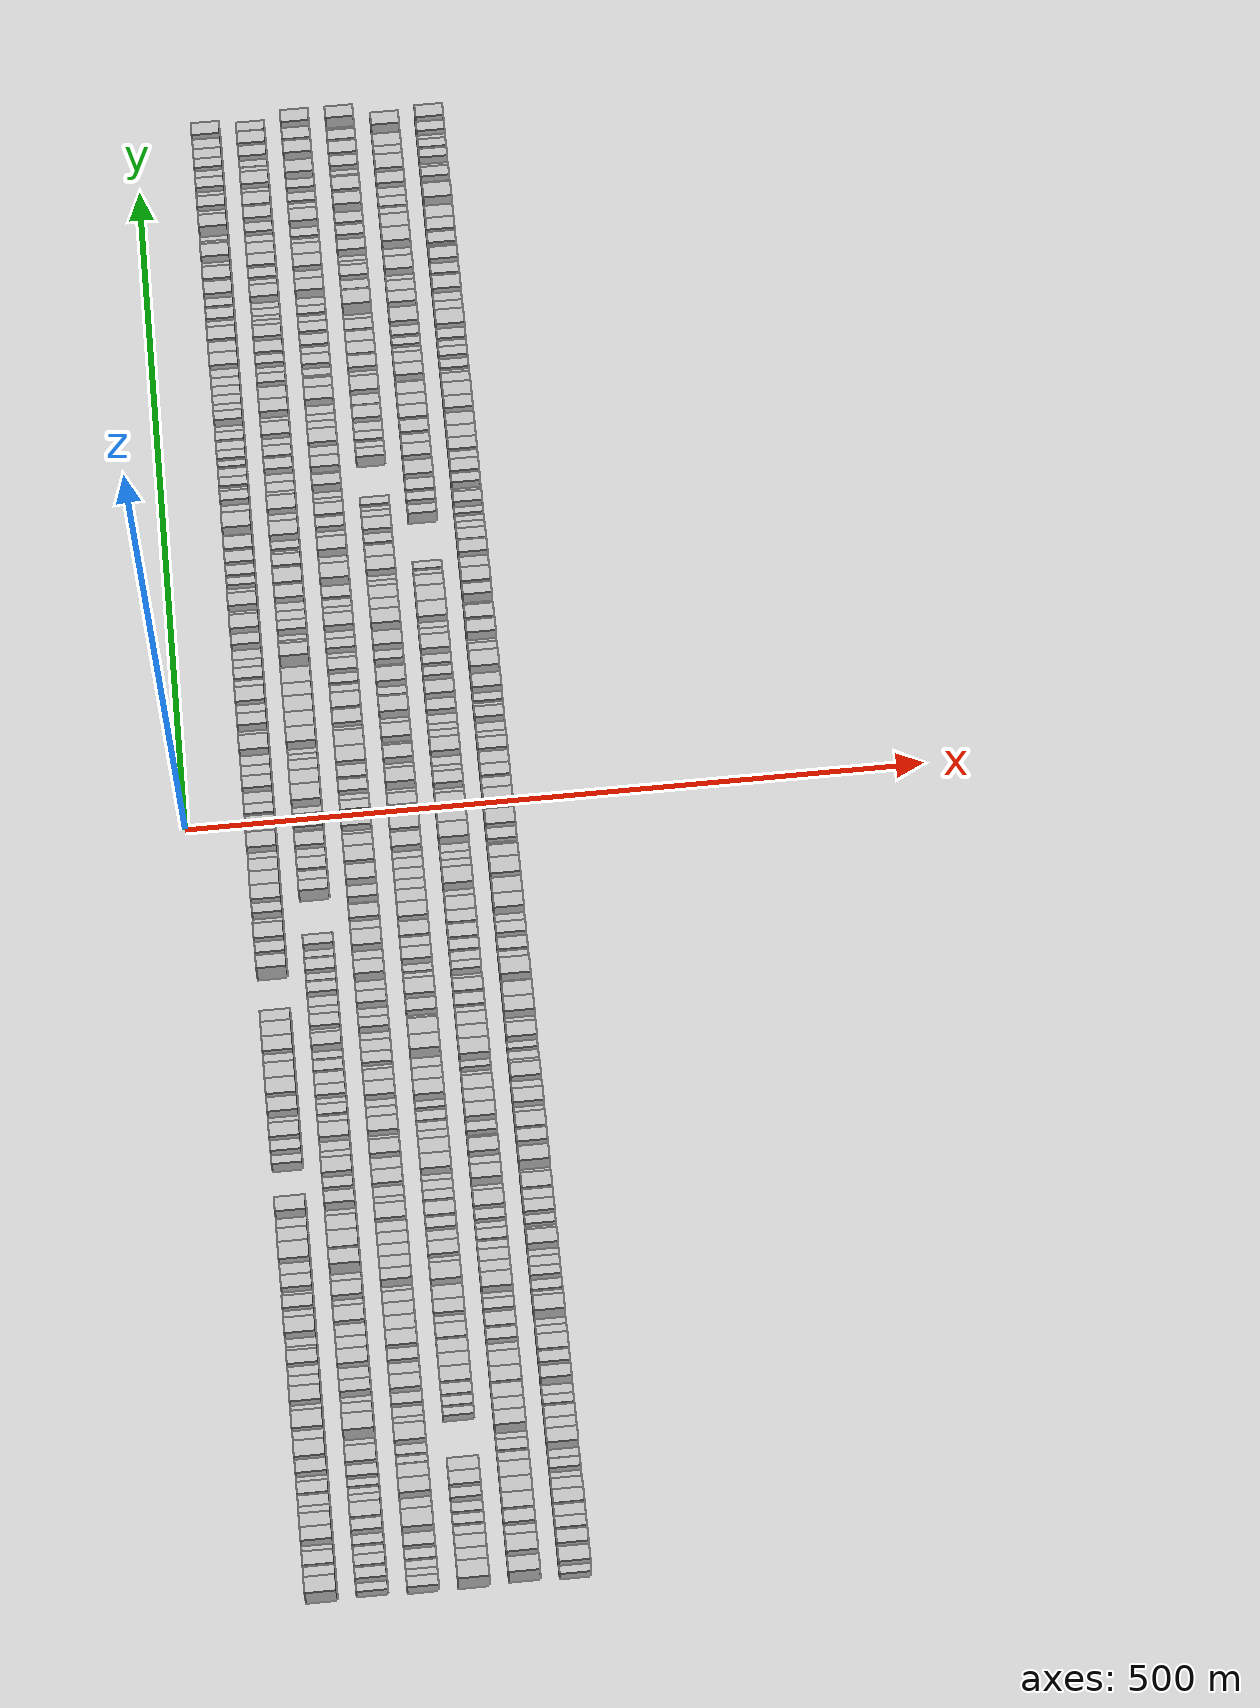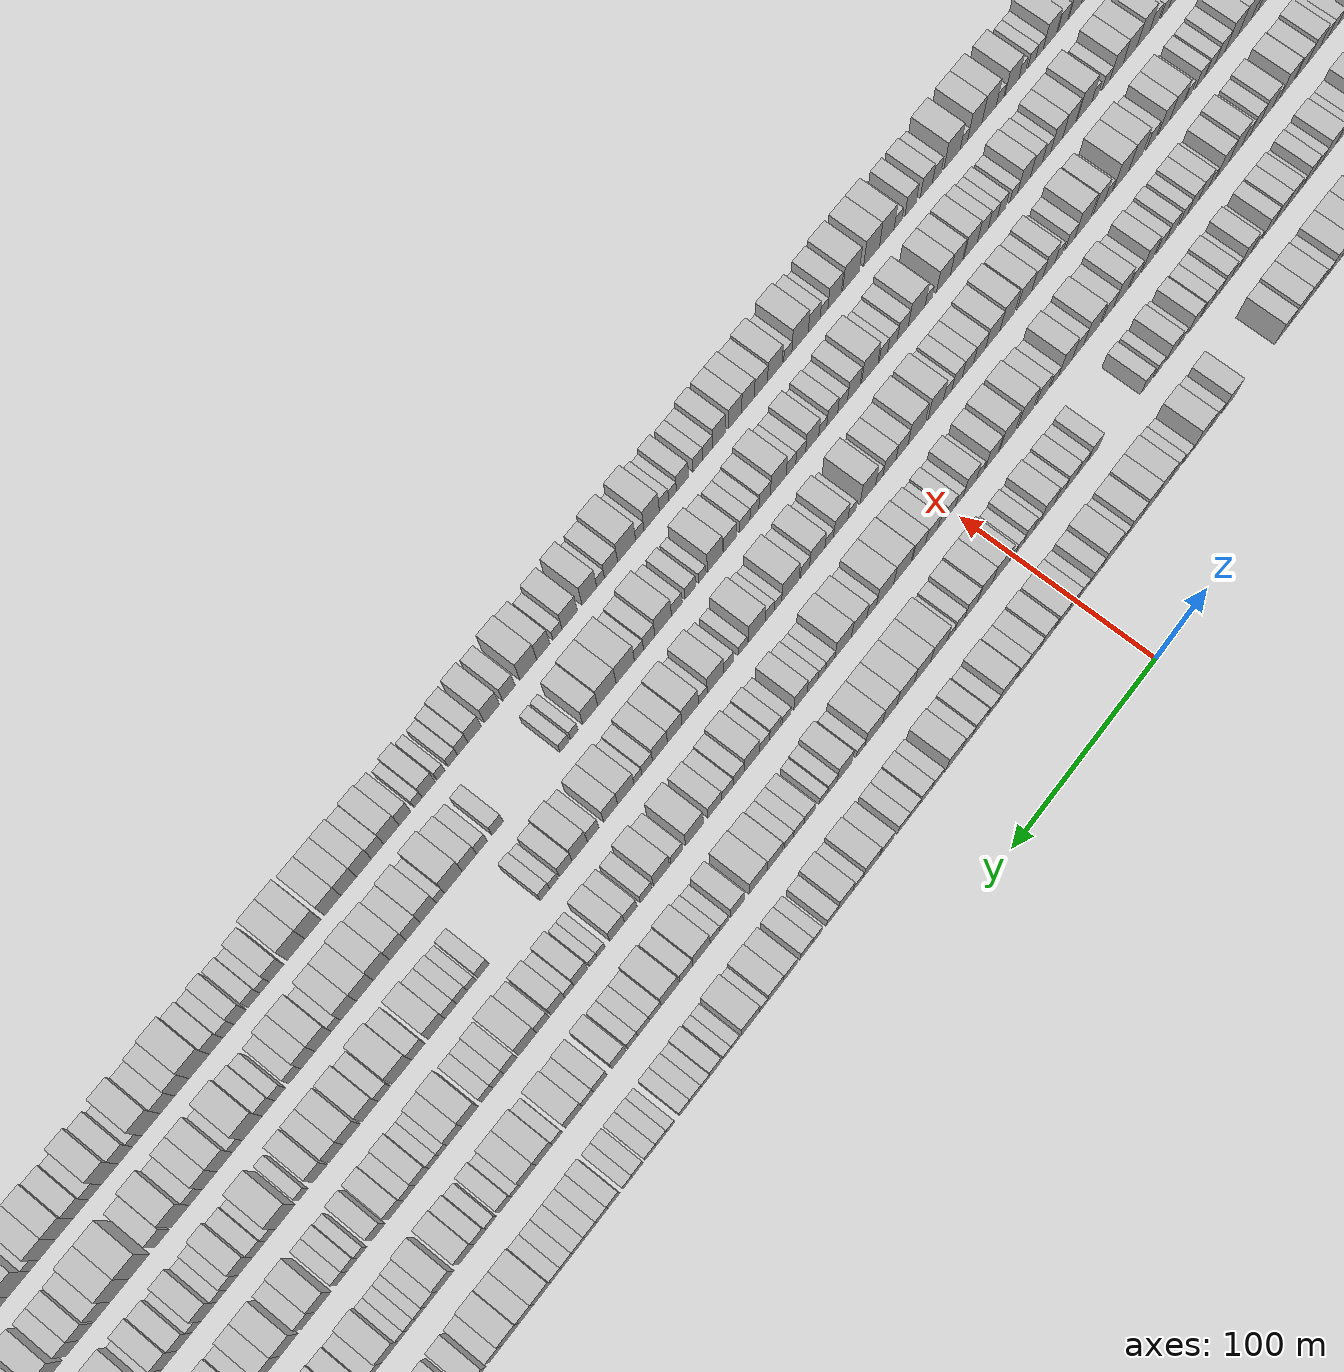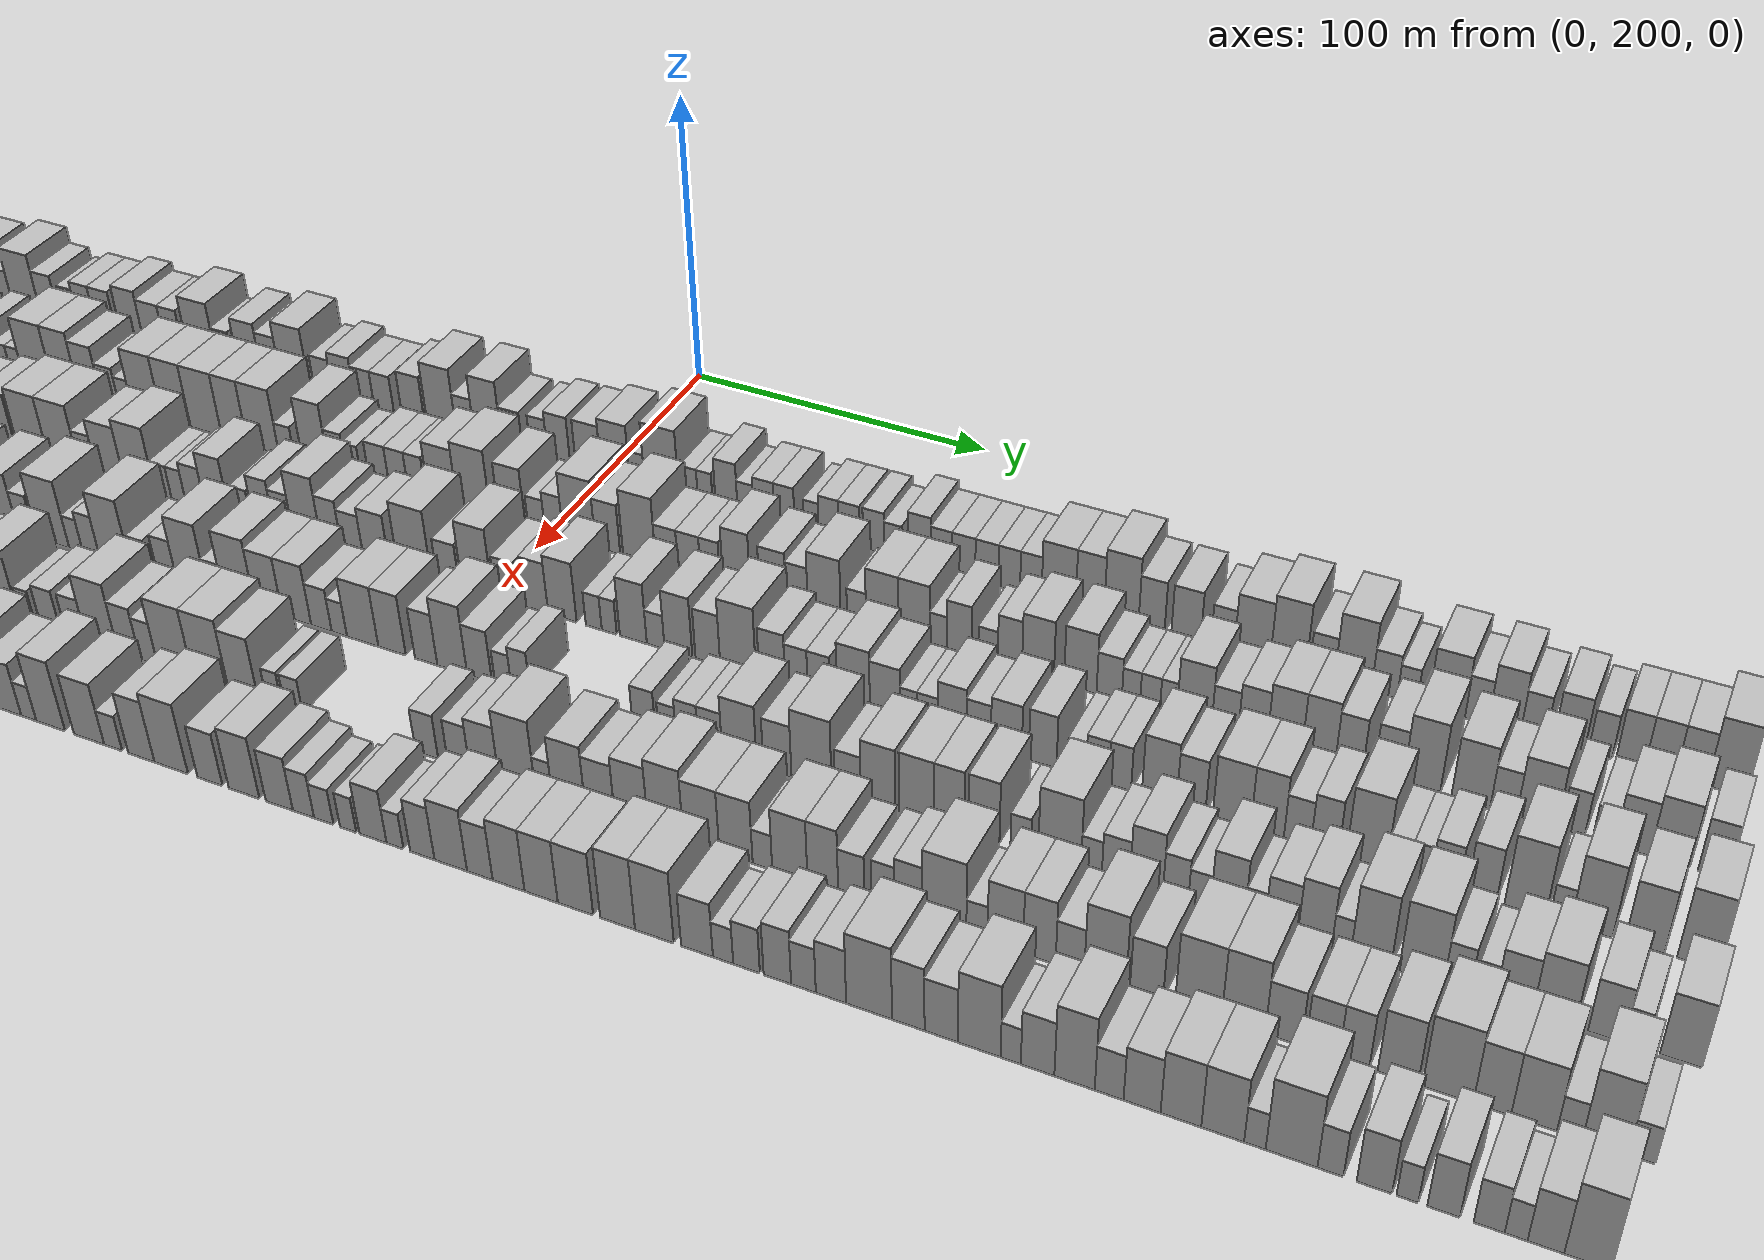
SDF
<sdf version="1.6">
 <world name="default">
  <scene>
   <sky><clouds><speed>12</speed></clouds></sky>
   <ambient>0.4 0.4 0.4 1</ambient>
   <background>0.7 0.7 0.7 1</background>
   <shadows>1</shadows>
  </scene>
  <gravity>0 0 -9.8066</gravity>
  <magnetic_field>6e-06 2.3e-05 -4.2e-05</magnetic_field>
  <physics default="0" name="default_physics" type="ode">
   <ode>
    <solver>
     <type>quick</type>
     <iters>10</iters>
     <sor>1.0</sor>
     <use_dynamic_moi_rescaling>0</use_dynamic_moi_rescaling>
    </solver>
    <constraints>
     <cfm>0</cfm>
     <erp>0.2</erp>
     <contact_max_correcting_vel>100</contact_max_correcting_vel>
     <contact_surface_layer>0.001</contact_surface_layer>
    </constraints>
   </ode>
   <max_step_size>0.004</max_step_size>
   <real_time_factor>1</real_time_factor>
   <real_time_update_rate>250</real_time_update_rate>
  </physics>
  <light name="sun" type="directional">
   <pose>0 0 10 0 0 0</pose>
   <diffuse>0.8 0.8 0.8 1</diffuse>
   <specular>0.2 0.2 0.2 1</specular>
   <attenuation>
    <range>1000</range>
    <constant>0.9</constant>
    <linear>0.01</linear>
    <quadratic>0.001</quadratic>
   </attenuation>
   <direction>-0.5 0.1 -0.9</direction>
  </light>
  <model name="building_1">
   <static>1</static>
   <pose>50.0000 -534.7158 0 0.000000 0.000000 0.000000</pose>
   <link name="link">
    <pose>0 0 12.00 0 0 0</pose>
    <collision name="collision"><geometry><box><size>20.0000 10.5683 24.0000</size></box></geometry></collision>
    <visual name="visual">
     <cast_shadows>0</cast_shadows>
     <geometry><box><size>20.0000 10.5683 24.0000</size></box></geometry>
     <material>
      <script>
       <uri>model://HANNAS_wall/materials/scripts</uri>
       <uri>model://HANNAS_wall/materials/textures</uri>
       <name>vrc/HANNAS_wall</name>
      </script>
     </material>
    </visual>
   </link>
  </model>
  <model name="building_2">
   <static>1</static>
   <pose>50.0000 -525.3660 0 0.000000 0.000000 0.000000</pose>
   <link name="link">
    <pose>0 0 9.00 0 0 0</pose>
    <collision name="collision"><geometry><box><size>20.0000 8.1313 18.0000</size></box></geometry></collision>
    <visual name="visual">
     <cast_shadows>0</cast_shadows>
     <geometry><box><size>20.0000 8.1313 18.0000</size></box></geometry>
     <material>
      <script>
       <uri>model://HANNAS_wall/materials/scripts</uri>
       <uri>model://HANNAS_wall/materials/textures</uri>
       <name>vrc/HANNAS_wall</name>
      </script>
     </material>
    </visual>
   </link>
  </model>
  <model name="building_3">
   <static>1</static>
   <pose>50.0000 -516.7216 0 0.000000 0.000000 0.000000</pose>
   <link name="link">
    <pose>0 0 10.50 0 0 0</pose>
    <collision name="collision"><geometry><box><size>20.0000 9.1576 21.0000</size></box></geometry></collision>
    <visual name="visual">
     <cast_shadows>0</cast_shadows>
     <geometry><box><size>20.0000 9.1576 21.0000</size></box></geometry>
     <material>
      <script>
       <uri>model://HANNAS_wall/materials/scripts</uri>
       <uri>model://HANNAS_wall/materials/textures</uri>
       <name>vrc/HANNAS_wall</name>
      </script>
     </material>
    </visual>
   </link>
  </model>
  <model name="building_4">
   <static>1</static>
   <pose>50.0000 -509.1825 0 0.000000 0.000000 0.000000</pose>
   <link name="link">
    <pose>0 0 6.00 0 0 0</pose>
    <collision name="collision"><geometry><box><size>20.0000 5.9204 12.0000</size></box></geometry></collision>
    <visual name="visual">
     <cast_shadows>0</cast_shadows>
     <geometry><box><size>20.0000 5.9204 12.0000</size></box></geometry>
     <material>
      <script>
       <uri>model://HANNAS_wall/materials/scripts</uri>
       <uri>model://HANNAS_wall/materials/textures</uri>
       <name>vrc/HANNAS_wall</name>
      </script>
     </material>
    </visual>
   </link>
  </model>
  <model name="building_5">
   <static>1</static>
   <pose>50.0000 -500.7630 0 0.000000 0.000000 0.000000</pose>
   <link name="link">
    <pose>0 0 10.50 0 0 0</pose>
    <collision name="collision"><geometry><box><size>20.0000 8.9187 21.0000</size></box></geometry></collision>
    <visual name="visual">
     <cast_shadows>0</cast_shadows>
     <geometry><box><size>20.0000 8.9187 21.0000</size></box></geometry>
     <material>
      <script>
       <uri>model://HANNAS_wall/materials/scripts</uri>
       <uri>model://HANNAS_wall/materials/textures</uri>
       <name>vrc/HANNAS_wall</name>
      </script>
     </material>
    </visual>
   </link>
  </model>
  <model name="building_6">
   <static>1</static>
   <pose>50.0000 -491.8383 0 0.000000 0.000000 0.000000</pose>
   <link name="link">
    <pose>0 0 10.50 0 0 0</pose>
    <collision name="collision"><geometry><box><size>20.0000 8.9307 21.0000</size></box></geometry></collision>
    <visual name="visual">
     <cast_shadows>0</cast_shadows>
     <geometry><box><size>20.0000 8.9307 21.0000</size></box></geometry>
     <material>
      <script>
       <uri>model://HANNAS_wall/materials/scripts</uri>
       <uri>model://HANNAS_wall/materials/textures</uri>
       <name>vrc/HANNAS_wall</name>
      </script>
     </material>
    </visual>
   </link>
  </model>
  <model name="building_7">
   <static>1</static>
   <pose>50.0000 -484.3149 0 0.000000 0.000000 0.000000</pose>
   <link name="link">
    <pose>0 0 7.50 0 0 0</pose>
    <collision name="collision"><geometry><box><size>20.0000 6.1162 15.0000</size></box></geometry></collision>
    <visual name="visual">
     <cast_shadows>0</cast_shadows>
     <geometry><box><size>20.0000 6.1162 15.0000</size></box></geometry>
     <material>
      <script>
       <uri>model://HANNAS_wall/materials/scripts</uri>
       <uri>model://HANNAS_wall/materials/textures</uri>
       <name>vrc/HANNAS_wall</name>
      </script>
     </material>
    </visual>
   </link>
  </model>
  <model name="building_8">
   <static>1</static>
   <pose>50.0000 -477.5582 0 0.000000 0.000000 0.000000</pose>
   <link name="link">
    <pose>0 0 7.50 0 0 0</pose>
    <collision name="collision"><geometry><box><size>20.0000 7.3971 15.0000</size></box></geometry></collision>
    <visual name="visual">
     <cast_shadows>0</cast_shadows>
     <geometry><box><size>20.0000 7.3971 15.0000</size></box></geometry>
     <material>
      <script>
       <uri>model://HANNAS_wall/materials/scripts</uri>
       <uri>model://HANNAS_wall/materials/textures</uri>
       <name>vrc/HANNAS_wall</name>
      </script>
     </material>
    </visual>
   </link>
  </model>
  <model name="building_9">
   <static>1</static>
   <pose>50.0000 -469.8206 0 0.000000 0.000000 0.000000</pose>
   <link name="link">
    <pose>0 0 9.00 0 0 0</pose>
    <collision name="collision"><geometry><box><size>20.0000 8.0781 18.0000</size></box></geometry></collision>
    <visual name="visual">
     <cast_shadows>0</cast_shadows>
     <geometry><box><size>20.0000 8.0781 18.0000</size></box></geometry>
     <material>
      <script>
       <uri>model://HANNAS_wall/materials/scripts</uri>
       <uri>model://HANNAS_wall/materials/textures</uri>
       <name>vrc/HANNAS_wall</name>
      </script>
     </material>
    </visual>
   </link>
  </model>
  <model name="building_10">
   <static>1</static>
   <pose>50.0000 -463.3755 0 0.000000 0.000000 0.000000</pose>
   <link name="link">
    <pose>0 0 6.00 0 0 0</pose>
    <collision name="collision"><geometry><box><size>20.0000 4.8121 12.0000</size></box></geometry></collision>
    <visual name="visual">
     <cast_shadows>0</cast_shadows>
     <geometry><box><size>20.0000 4.8121 12.0000</size></box></geometry>
     <material>
      <script>
       <uri>model://HANNAS_wall/materials/scripts</uri>
       <uri>model://HANNAS_wall/materials/textures</uri>
       <name>vrc/HANNAS_wall</name>
      </script>
     </material>
    </visual>
   </link>
  </model>
  <model name="building_11">
   <static>1</static>
   <pose>50.0000 -455.6227 0 0.000000 0.000000 0.000000</pose>
   <link name="link">
    <pose>0 0 9.00 0 0 0</pose>
    <collision name="collision"><geometry><box><size>20.0000 8.6935 18.0000</size></box></geometry></collision>
    <visual name="visual">
     <cast_shadows>0</cast_shadows>
     <geometry><box><size>20.0000 8.6935 18.0000</size></box></geometry>
     <material>
      <script>
       <uri>model://HANNAS_wall/materials/scripts</uri>
       <uri>model://HANNAS_wall/materials/textures</uri>
       <name>vrc/HANNAS_wall</name>
      </script>
     </material>
    </visual>
   </link>
  </model>
  <model name="building_12">
   <static>1</static>
   <pose>50.0000 -445.8741 0 0.000000 0.000000 0.000000</pose>
   <link name="link">
    <pose>0 0 12.00 0 0 0</pose>
    <collision name="collision"><geometry><box><size>20.0000 10.8036 24.0000</size></box></geometry></collision>
    <visual name="visual">
     <cast_shadows>0</cast_shadows>
     <geometry><box><size>20.0000 10.8036 24.0000</size></box></geometry>
     <material>
      <script>
       <uri>model://HANNAS_wall/materials/scripts</uri>
       <uri>model://HANNAS_wall/materials/textures</uri>
       <name>vrc/HANNAS_wall</name>
      </script>
     </material>
    </visual>
   </link>
  </model>
  <model name="building_13">
   <static>1</static>
   <pose>50.0000 -436.4379 0 0.000000 0.000000 0.000000</pose>
   <link name="link">
    <pose>0 0 9.00 0 0 0</pose>
    <collision name="collision"><geometry><box><size>20.0000 8.0688 18.0000</size></box></geometry></collision>
    <visual name="visual">
     <cast_shadows>0</cast_shadows>
     <geometry><box><size>20.0000 8.0688 18.0000</size></box></geometry>
     <material>
      <script>
       <uri>model://HANNAS_wall/materials/scripts</uri>
       <uri>model://HANNAS_wall/materials/textures</uri>
       <name>vrc/HANNAS_wall</name>
      </script>
     </material>
    </visual>
   </link>
  </model>
  <model name="building_14">
   <static>1</static>
   <pose>50.0000 -426.5476 0 0.000000 0.000000 0.000000</pose>
   <link name="link">
    <pose>0 0 12.00 0 0 0</pose>
    <collision name="collision"><geometry><box><size>20.0000 11.7119 24.0000</size></box></geometry></collision>
    <visual name="visual">
     <cast_shadows>0</cast_shadows>
     <geometry><box><size>20.0000 11.7119 24.0000</size></box></geometry>
     <material>
      <script>
       <uri>model://HANNAS_wall/materials/scripts</uri>
       <uri>model://HANNAS_wall/materials/textures</uri>
       <name>vrc/HANNAS_wall</name>
      </script>
     </material>
    </visual>
   </link>
  </model>
  <model name="building_15">
   <static>1</static>
   <pose>50.0000 -417.6448 0 0.000000 0.000000 0.000000</pose>
   <link name="link">
    <pose>0 0 7.50 0 0 0</pose>
    <collision name="collision"><geometry><box><size>20.0000 6.0938 15.0000</size></box></geometry></collision>
    <visual name="visual">
     <cast_shadows>0</cast_shadows>
     <geometry><box><size>20.0000 6.0938 15.0000</size></box></geometry>
     <material>
      <script>
       <uri>model://HANNAS_wall/materials/scripts</uri>
       <uri>model://HANNAS_wall/materials/textures</uri>
       <name>vrc/HANNAS_wall</name>
      </script>
     </material>
    </visual>
   </link>
  </model>
  <model name="building_16">
   <static>1</static>
   <pose>50.0000 -409.5746 0 0.000000 0.000000 0.000000</pose>
   <link name="link">
    <pose>0 0 12.00 0 0 0</pose>
    <collision name="collision"><geometry><box><size>20.0000 10.0467 24.0000</size></box></geometry></collision>
    <visual name="visual">
     <cast_shadows>0</cast_shadows>
     <geometry><box><size>20.0000 10.0467 24.0000</size></box></geometry>
     <material>
      <script>
       <uri>model://HANNAS_wall/materials/scripts</uri>
       <uri>model://HANNAS_wall/materials/textures</uri>
       <name>vrc/HANNAS_wall</name>
      </script>
     </material>
    </visual>
   </link>
  </model>
  <model name="building_17">
   <static>1</static>
   <pose>50.0000 -400.2621 0 0.000000 0.000000 0.000000</pose>
   <link name="link">
    <pose>0 0 9.00 0 0 0</pose>
    <collision name="collision"><geometry><box><size>20.0000 8.5783 18.0000</size></box></geometry></collision>
    <visual name="visual">
     <cast_shadows>0</cast_shadows>
     <geometry><box><size>20.0000 8.5783 18.0000</size></box></geometry>
     <material>
      <script>
       <uri>model://HANNAS_wall/materials/scripts</uri>
       <uri>model://HANNAS_wall/materials/textures</uri>
       <name>vrc/HANNAS_wall</name>
      </script>
     </material>
    </visual>
   </link>
  </model>
  <model name="building_18">
   <static>1</static>
   <pose>50.0000 -392.3119 0 0.000000 0.000000 0.000000</pose>
   <link name="link">
    <pose>0 0 7.50 0 0 0</pose>
    <collision name="collision"><geometry><box><size>20.0000 7.3221 15.0000</size></box></geometry></collision>
    <visual name="visual">
     <cast_shadows>0</cast_shadows>
     <geometry><box><size>20.0000 7.3221 15.0000</size></box></geometry>
     <material>
      <script>
       <uri>model://HANNAS_wall/materials/scripts</uri>
       <uri>model://HANNAS_wall/materials/textures</uri>
       <name>vrc/HANNAS_wall</name>
      </script>
     </material>
    </visual>
   </link>
  </model>
  <model name="building_19">
   <static>1</static>
   <pose>50.0000 -384.1086 0 0.000000 0.000000 0.000000</pose>
   <link name="link">
    <pose>0 0 10.50 0 0 0</pose>
    <collision name="collision"><geometry><box><size>20.0000 9.0845 21.0000</size></box></geometry></collision>
    <visual name="visual">
     <cast_shadows>0</cast_shadows>
     <geometry><box><size>20.0000 9.0845 21.0000</size></box></geometry>
     <material>
      <script>
       <uri>model://HANNAS_wall/materials/scripts</uri>
       <uri>model://HANNAS_wall/materials/textures</uri>
       <name>vrc/HANNAS_wall</name>
      </script>
     </material>
    </visual>
   </link>
  </model>
  <model name="building_20">
   <static>1</static>
   <pose>50.0000 -376.9728 0 0.000000 0.000000 0.000000</pose>
   <link name="link">
    <pose>0 0 6.00 0 0 0</pose>
    <collision name="collision"><geometry><box><size>20.0000 5.1870 12.0000</size></box></geometry></collision>
    <visual name="visual">
     <cast_shadows>0</cast_shadows>
     <geometry><box><size>20.0000 5.1870 12.0000</size></box></geometry>
     <material>
      <script>
       <uri>model://HANNAS_wall/materials/scripts</uri>
       <uri>model://HANNAS_wall/materials/textures</uri>
       <name>vrc/HANNAS_wall</name>
      </script>
     </material>
    </visual>
   </link>
  </model>
  <model name="building_21">
   <static>1</static>
   <pose>50.0000 -371.6373 0 0.000000 0.000000 0.000000</pose>
   <link name="link">
    <pose>0 0 6.00 0 0 0</pose>
    <collision name="collision"><geometry><box><size>20.0000 5.4841 12.0000</size></box></geometry></collision>
    <visual name="visual">
     <cast_shadows>0</cast_shadows>
     <geometry><box><size>20.0000 5.4841 12.0000</size></box></geometry>
     <material>
      <script>
       <uri>model://HANNAS_wall/materials/scripts</uri>
       <uri>model://HANNAS_wall/materials/textures</uri>
       <name>vrc/HANNAS_wall</name>
      </script>
     </material>
    </visual>
   </link>
  </model>
  <model name="building_22">
   <static>1</static>
   <pose>50.0000 -363.6183 0 0.000000 0.000000 0.000000</pose>
   <link name="link">
    <pose>0 0 12.00 0 0 0</pose>
    <collision name="collision"><geometry><box><size>20.0000 10.5539 24.0000</size></box></geometry></collision>
    <visual name="visual">
     <cast_shadows>0</cast_shadows>
     <geometry><box><size>20.0000 10.5539 24.0000</size></box></geometry>
     <material>
      <script>
       <uri>model://HANNAS_wall/materials/scripts</uri>
       <uri>model://HANNAS_wall/materials/textures</uri>
       <name>vrc/HANNAS_wall</name>
      </script>
     </material>
    </visual>
   </link>
  </model>
  <model name="building_23">
   <static>1</static>
   <pose>50.0000 -354.6401 0 0.000000 0.000000 0.000000</pose>
   <link name="link">
    <pose>0 0 7.50 0 0 0</pose>
    <collision name="collision"><geometry><box><size>20.0000 7.4026 15.0000</size></box></geometry></collision>
    <visual name="visual">
     <cast_shadows>0</cast_shadows>
     <geometry><box><size>20.0000 7.4026 15.0000</size></box></geometry>
     <material>
      <script>
       <uri>model://HANNAS_wall/materials/scripts</uri>
       <uri>model://HANNAS_wall/materials/textures</uri>
       <name>vrc/HANNAS_wall</name>
      </script>
     </material>
    </visual>
   </link>
  </model>
  <model name="building_24">
   <static>1</static>
   <pose>50.0000 -346.7290 0 0.000000 0.000000 0.000000</pose>
   <link name="link">
    <pose>0 0 10.50 0 0 0</pose>
    <collision name="collision"><geometry><box><size>20.0000 8.4196 21.0000</size></box></geometry></collision>
    <visual name="visual">
     <cast_shadows>0</cast_shadows>
     <geometry><box><size>20.0000 8.4196 21.0000</size></box></geometry>
     <material>
      <script>
       <uri>model://HANNAS_wall/materials/scripts</uri>
       <uri>model://HANNAS_wall/materials/textures</uri>
       <name>vrc/HANNAS_wall</name>
      </script>
     </material>
    </visual>
   </link>
  </model>
  <model name="building_25">
   <static>1</static>
   <pose>50.0000 -339.9588 0 0.000000 0.000000 0.000000</pose>
   <link name="link">
    <pose>0 0 6.00 0 0 0</pose>
    <collision name="collision"><geometry><box><size>20.0000 5.1209 12.0000</size></box></geometry></collision>
    <visual name="visual">
     <cast_shadows>0</cast_shadows>
     <geometry><box><size>20.0000 5.1209 12.0000</size></box></geometry>
     <material>
      <script>
       <uri>model://HANNAS_wall/materials/scripts</uri>
       <uri>model://HANNAS_wall/materials/textures</uri>
       <name>vrc/HANNAS_wall</name>
      </script>
     </material>
    </visual>
   </link>
  </model>
  <model name="building_26">
   <static>1</static>
   <pose>50.0000 -331.9432 0 0.000000 0.000000 0.000000</pose>
   <link name="link">
    <pose>0 0 9.00 0 0 0</pose>
    <collision name="collision"><geometry><box><size>20.0000 8.9103 18.0000</size></box></geometry></collision>
    <visual name="visual">
     <cast_shadows>0</cast_shadows>
     <geometry><box><size>20.0000 8.9103 18.0000</size></box></geometry>
     <material>
      <script>
       <uri>model://HANNAS_wall/materials/scripts</uri>
       <uri>model://HANNAS_wall/materials/textures</uri>
       <name>vrc/HANNAS_wall</name>
      </script>
     </material>
    </visual>
   </link>
  </model>
  <model name="building_27">
   <static>1</static>
   <pose>50.0000 -323.6414 0 0.000000 0.000000 0.000000</pose>
   <link name="link">
    <pose>0 0 9.00 0 0 0</pose>
    <collision name="collision"><geometry><box><size>20.0000 7.6932 18.0000</size></box></geometry></collision>
    <visual name="visual">
     <cast_shadows>0</cast_shadows>
     <geometry><box><size>20.0000 7.6932 18.0000</size></box></geometry>
     <material>
      <script>
       <uri>model://HANNAS_wall/materials/scripts</uri>
       <uri>model://HANNAS_wall/materials/textures</uri>
       <name>vrc/HANNAS_wall</name>
      </script>
     </material>
    </visual>
   </link>
  </model>
  <model name="building_28">
   <static>1</static>
   <pose>50.0000 -312.8694 0 0.000000 0.000000 0.000000</pose>
   <link name="link">
    <pose>0 0 12.00 0 0 0</pose>
    <collision name="collision"><geometry><box><size>20.0000 11.8508 24.0000</size></box></geometry></collision>
    <visual name="visual">
     <cast_shadows>0</cast_shadows>
     <geometry><box><size>20.0000 11.8508 24.0000</size></box></geometry>
     <material>
      <script>
       <uri>model://HANNAS_wall/materials/scripts</uri>
       <uri>model://HANNAS_wall/materials/textures</uri>
       <name>vrc/HANNAS_wall</name>
      </script>
     </material>
    </visual>
   </link>
  </model>
  <model name="building_29">
   <static>1</static>
   <pose>50.0000 -301.7609 0 0.000000 0.000000 0.000000</pose>
   <link name="link">
    <pose>0 0 10.50 0 0 0</pose>
    <collision name="collision"><geometry><box><size>20.0000 10.3662 21.0000</size></box></geometry></collision>
    <visual name="visual">
     <cast_shadows>0</cast_shadows>
     <geometry><box><size>20.0000 10.3662 21.0000</size></box></geometry>
     <material>
      <script>
       <uri>model://HANNAS_wall/materials/scripts</uri>
       <uri>model://HANNAS_wall/materials/textures</uri>
       <name>vrc/HANNAS_wall</name>
      </script>
     </material>
    </visual>
   </link>
  </model>
  <model name="building_30">
   <static>1</static>
   <pose>50.0000 -291.3286 0 0.000000 0.000000 0.000000</pose>
   <link name="link">
    <pose>0 0 7.50 0 0 0</pose>
    <collision name="collision"><geometry><box><size>20.0000 6.4985 15.0000</size></box></geometry></collision>
    <visual name="visual">
     <cast_shadows>0</cast_shadows>
     <geometry><box><size>20.0000 6.4985 15.0000</size></box></geometry>
     <material>
      <script>
       <uri>model://HANNAS_wall/materials/scripts</uri>
       <uri>model://HANNAS_wall/materials/textures</uri>
       <name>vrc/HANNAS_wall</name>
      </script>
     </material>
    </visual>
   </link>
  </model>
  <model name="building_31">
   <static>1</static>
   <pose>50.0000 -281.1221 0 0.000000 0.000000 0.000000</pose>
   <link name="link">
    <pose>0 0 12.00 0 0 0</pose>
    <collision name="collision"><geometry><box><size>20.0000 9.9145 24.0000</size></box></geometry></collision>
    <visual name="visual">
     <cast_shadows>0</cast_shadows>
     <geometry><box><size>20.0000 9.9145 24.0000</size></box></geometry>
     <material>
      <script>
       <uri>model://HANNAS_wall/materials/scripts</uri>
       <uri>model://HANNAS_wall/materials/textures</uri>
       <name>vrc/HANNAS_wall</name>
      </script>
     </material>
    </visual>
   </link>
  </model>
  <model name="building_32">
   <static>1</static>
   <pose>50.0000 -247.1076 0 0.000000 0.000000 0.000000</pose>
   <link name="link">
    <pose>0 0 7.50 0 0 0</pose>
    <collision name="collision"><geometry><box><size>20.0000 6.0382 15.0000</size></box></geometry></collision>
    <visual name="visual">
     <cast_shadows>0</cast_shadows>
     <geometry><box><size>20.0000 6.0382 15.0000</size></box></geometry>
     <material>
      <script>
       <uri>model://HANNAS_wall/materials/scripts</uri>
       <uri>model://HANNAS_wall/materials/textures</uri>
       <name>vrc/HANNAS_wall</name>
      </script>
     </material>
    </visual>
   </link>
  </model>
  <model name="building_33">
   <static>1</static>
   <pose>50.0000 -238.3960 0 0.000000 0.000000 0.000000</pose>
   <link name="link">
    <pose>0 0 9.00 0 0 0</pose>
    <collision name="collision"><geometry><box><size>20.0000 7.3849 18.0000</size></box></geometry></collision>
    <visual name="visual">
     <cast_shadows>0</cast_shadows>
     <geometry><box><size>20.0000 7.3849 18.0000</size></box></geometry>
     <material>
      <script>
       <uri>model://HANNAS_wall/materials/scripts</uri>
       <uri>model://HANNAS_wall/materials/textures</uri>
       <name>vrc/HANNAS_wall</name>
      </script>
     </material>
    </visual>
   </link>
  </model>
  <model name="building_34">
   <static>1</static>
   <pose>50.0000 -229.7345 0 0.000000 0.000000 0.000000</pose>
   <link name="link">
    <pose>0 0 12.00 0 0 0</pose>
    <collision name="collision"><geometry><box><size>20.0000 9.9381 24.0000</size></box></geometry></collision>
    <visual name="visual">
     <cast_shadows>0</cast_shadows>
     <geometry><box><size>20.0000 9.9381 24.0000</size></box></geometry>
     <material>
      <script>
       <uri>model://HANNAS_wall/materials/scripts</uri>
       <uri>model://HANNAS_wall/materials/textures</uri>
       <name>vrc/HANNAS_wall</name>
      </script>
     </material>
    </visual>
   </link>
  </model>
  <model name="building_35">
   <static>1</static>
   <pose>50.0000 -219.2893 0 0.000000 0.000000 0.000000</pose>
   <link name="link">
    <pose>0 0 6.00 0 0 0</pose>
    <collision name="collision"><geometry><box><size>20.0000 4.9522 12.0000</size></box></geometry></collision>
    <visual name="visual">
     <cast_shadows>0</cast_shadows>
     <geometry><box><size>20.0000 4.9522 12.0000</size></box></geometry>
     <material>
      <script>
       <uri>model://HANNAS_wall/materials/scripts</uri>
       <uri>model://HANNAS_wall/materials/textures</uri>
       <name>vrc/HANNAS_wall</name>
      </script>
     </material>
    </visual>
   </link>
  </model>
  <model name="building_36">
   <static>1</static>
   <pose>50.0000 -210.7638 0 0.000000 0.000000 0.000000</pose>
   <link name="link">
    <pose>0 0 10.50 0 0 0</pose>
    <collision name="collision"><geometry><box><size>20.0000 10.0988 21.0000</size></box></geometry></collision>
    <visual name="visual">
     <cast_shadows>0</cast_shadows>
     <geometry><box><size>20.0000 10.0988 21.0000</size></box></geometry>
     <material>
      <script>
       <uri>model://HANNAS_wall/materials/scripts</uri>
       <uri>model://HANNAS_wall/materials/textures</uri>
       <name>vrc/HANNAS_wall</name>
      </script>
     </material>
    </visual>
   </link>
  </model>
  <model name="building_37">
   <static>1</static>
   <pose>50.0000 -199.0971 0 0.000000 0.000000 0.000000</pose>
   <link name="link">
    <pose>0 0 12.00 0 0 0</pose>
    <collision name="collision"><geometry><box><size>20.0000 11.2346 24.0000</size></box></geometry></collision>
    <visual name="visual">
     <cast_shadows>0</cast_shadows>
     <geometry><box><size>20.0000 11.2346 24.0000</size></box></geometry>
     <material>
      <script>
       <uri>model://HANNAS_wall/materials/scripts</uri>
       <uri>model://HANNAS_wall/materials/textures</uri>
       <name>vrc/HANNAS_wall</name>
      </script>
     </material>
    </visual>
   </link>
  </model>
  <model name="building_38">
   <static>1</static>
   <pose>50.0000 -188.0680 0 0.000000 0.000000 0.000000</pose>
   <link name="link">
    <pose>0 0 12.00 0 0 0</pose>
    <collision name="collision"><geometry><box><size>20.0000 10.8237 24.0000</size></box></geometry></collision>
    <visual name="visual">
     <cast_shadows>0</cast_shadows>
     <geometry><box><size>20.0000 10.8237 24.0000</size></box></geometry>
     <material>
      <script>
       <uri>model://HANNAS_wall/materials/scripts</uri>
       <uri>model://HANNAS_wall/materials/textures</uri>
       <name>vrc/HANNAS_wall</name>
      </script>
     </material>
    </visual>
   </link>
  </model>
  <model name="building_39">
   <static>1</static>
   <pose>50.0000 -178.5790 0 0.000000 0.000000 0.000000</pose>
   <link name="link">
    <pose>0 0 9.00 0 0 0</pose>
    <collision name="collision"><geometry><box><size>20.0000 8.1543 18.0000</size></box></geometry></collision>
    <visual name="visual">
     <cast_shadows>0</cast_shadows>
     <geometry><box><size>20.0000 8.1543 18.0000</size></box></geometry>
     <material>
      <script>
       <uri>model://HANNAS_wall/materials/scripts</uri>
       <uri>model://HANNAS_wall/materials/textures</uri>
       <name>vrc/HANNAS_wall</name>
      </script>
     </material>
    </visual>
   </link>
  </model>
  <model name="building_40">
   <static>1</static>
   <pose>50.0000 -169.2701 0 0.000000 0.000000 0.000000</pose>
   <link name="link">
    <pose>0 0 12.00 0 0 0</pose>
    <collision name="collision"><geometry><box><size>20.0000 10.4635 24.0000</size></box></geometry></collision>
    <visual name="visual">
     <cast_shadows>0</cast_shadows>
     <geometry><box><size>20.0000 10.4635 24.0000</size></box></geometry>
     <material>
      <script>
       <uri>model://HANNAS_wall/materials/scripts</uri>
       <uri>model://HANNAS_wall/materials/textures</uri>
       <name>vrc/HANNAS_wall</name>
      </script>
     </material>
    </visual>
   </link>
  </model>
  <model name="building_41">
   <static>1</static>
   <pose>50.0000 -158.8248 0 0.000000 0.000000 0.000000</pose>
   <link name="link">
    <pose>0 0 12.00 0 0 0</pose>
    <collision name="collision"><geometry><box><size>20.0000 10.4271 24.0000</size></box></geometry></collision>
    <visual name="visual">
     <cast_shadows>0</cast_shadows>
     <geometry><box><size>20.0000 10.4271 24.0000</size></box></geometry>
     <material>
      <script>
       <uri>model://HANNAS_wall/materials/scripts</uri>
       <uri>model://HANNAS_wall/materials/textures</uri>
       <name>vrc/HANNAS_wall</name>
      </script>
     </material>
    </visual>
   </link>
  </model>
  <model name="building_42">
   <static>1</static>
   <pose>50.0000 -149.0748 0 0.000000 0.000000 0.000000</pose>
   <link name="link">
    <pose>0 0 10.50 0 0 0</pose>
    <collision name="collision"><geometry><box><size>20.0000 9.0729 21.0000</size></box></geometry></collision>
    <visual name="visual">
     <cast_shadows>0</cast_shadows>
     <geometry><box><size>20.0000 9.0729 21.0000</size></box></geometry>
     <material>
      <script>
       <uri>model://HANNAS_wall/materials/scripts</uri>
       <uri>model://HANNAS_wall/materials/textures</uri>
       <name>vrc/HANNAS_wall</name>
      </script>
     </material>
    </visual>
   </link>
  </model>
  <model name="building_43">
   <static>1</static>
   <pose>50.0000 -109.4234 0 0.000000 0.000000 0.000000</pose>
   <link name="link">
    <pose>0 0 10.50 0 0 0</pose>
    <collision name="collision"><geometry><box><size>20.0000 9.4100 21.0000</size></box></geometry></collision>
    <visual name="visual">
     <cast_shadows>0</cast_shadows>
     <geometry><box><size>20.0000 9.4100 21.0000</size></box></geometry>
     <material>
      <script>
       <uri>model://HANNAS_wall/materials/scripts</uri>
       <uri>model://HANNAS_wall/materials/textures</uri>
       <name>vrc/HANNAS_wall</name>
      </script>
     </material>
    </visual>
   </link>
  </model>
  <model name="building_44">
   <static>1</static>
   <pose>50.0000 -97.8108 0 0.000000 0.000000 0.000000</pose>
   <link name="link">
    <pose>0 0 9.00 0 0 0</pose>
    <collision name="collision"><geometry><box><size>20.0000 7.8151 18.0000</size></box></geometry></collision>
    <visual name="visual">
     <cast_shadows>0</cast_shadows>
     <geometry><box><size>20.0000 7.8151 18.0000</size></box></geometry>
     <material>
      <script>
       <uri>model://HANNAS_wall/materials/scripts</uri>
       <uri>model://HANNAS_wall/materials/textures</uri>
       <name>vrc/HANNAS_wall</name>
      </script>
     </material>
    </visual>
   </link>
  </model>
  <model name="building_45">
   <static>1</static>
   <pose>50.0000 -88.4266 0 0.000000 0.000000 0.000000</pose>
   <link name="link">
    <pose>0 0 12.00 0 0 0</pose>
    <collision name="collision"><geometry><box><size>20.0000 10.9532 24.0000</size></box></geometry></collision>
    <visual name="visual">
     <cast_shadows>0</cast_shadows>
     <geometry><box><size>20.0000 10.9532 24.0000</size></box></geometry>
     <material>
      <script>
       <uri>model://HANNAS_wall/materials/scripts</uri>
       <uri>model://HANNAS_wall/materials/textures</uri>
       <name>vrc/HANNAS_wall</name>
      </script>
     </material>
    </visual>
   </link>
  </model>
  <model name="building_46">
   <static>1</static>
   <pose>50.0000 -78.0642 0 0.000000 0.000000 0.000000</pose>
   <link name="link">
    <pose>0 0 6.00 0 0 0</pose>
    <collision name="collision"><geometry><box><size>20.0000 5.7716 12.0000</size></box></geometry></collision>
    <visual name="visual">
     <cast_shadows>0</cast_shadows>
     <geometry><box><size>20.0000 5.7716 12.0000</size></box></geometry>
     <material>
      <script>
       <uri>model://HANNAS_wall/materials/scripts</uri>
       <uri>model://HANNAS_wall/materials/textures</uri>
       <name>vrc/HANNAS_wall</name>
      </script>
     </material>
    </visual>
   </link>
  </model>
  <model name="building_47">
   <static>1</static>
   <pose>50.0000 -69.4956 0 0.000000 0.000000 0.000000</pose>
   <link name="link">
    <pose>0 0 9.00 0 0 0</pose>
    <collision name="collision"><geometry><box><size>20.0000 7.3656 18.0000</size></box></geometry></collision>
    <visual name="visual">
     <cast_shadows>0</cast_shadows>
     <geometry><box><size>20.0000 7.3656 18.0000</size></box></geometry>
     <material>
      <script>
       <uri>model://HANNAS_wall/materials/scripts</uri>
       <uri>model://HANNAS_wall/materials/textures</uri>
       <name>vrc/HANNAS_wall</name>
      </script>
     </material>
    </visual>
   </link>
  </model>
  <model name="building_48">
   <static>1</static>
   <pose>50.0000 -60.5503 0 0.000000 0.000000 0.000000</pose>
   <link name="link">
    <pose>0 0 12.00 0 0 0</pose>
    <collision name="collision"><geometry><box><size>20.0000 10.5250 24.0000</size></box></geometry></collision>
    <visual name="visual">
     <cast_shadows>0</cast_shadows>
     <geometry><box><size>20.0000 10.5250 24.0000</size></box></geometry>
     <material>
      <script>
       <uri>model://HANNAS_wall/materials/scripts</uri>
       <uri>model://HANNAS_wall/materials/textures</uri>
       <name>vrc/HANNAS_wall</name>
      </script>
     </material>
    </visual>
   </link>
  </model>
  <model name="building_49">
   <static>1</static>
   <pose>50.0000 -50.3264 0 0.000000 0.000000 0.000000</pose>
   <link name="link">
    <pose>0 0 12.00 0 0 0</pose>
    <collision name="collision"><geometry><box><size>20.0000 9.9229 24.0000</size></box></geometry></collision>
    <visual name="visual">
     <cast_shadows>0</cast_shadows>
     <geometry><box><size>20.0000 9.9229 24.0000</size></box></geometry>
     <material>
      <script>
       <uri>model://HANNAS_wall/materials/scripts</uri>
       <uri>model://HANNAS_wall/materials/textures</uri>
       <name>vrc/HANNAS_wall</name>
      </script>
     </material>
    </visual>
   </link>
  </model>
  <model name="building_50">
   <static>1</static>
   <pose>50.0000 -40.1800 0 0.000000 0.000000 0.000000</pose>
   <link name="link">
    <pose>0 0 10.50 0 0 0</pose>
    <collision name="collision"><geometry><box><size>20.0000 10.3700 21.0000</size></box></geometry></collision>
    <visual name="visual">
     <cast_shadows>0</cast_shadows>
     <geometry><box><size>20.0000 10.3700 21.0000</size></box></geometry>
     <material>
      <script>
       <uri>model://HANNAS_wall/materials/scripts</uri>
       <uri>model://HANNAS_wall/materials/textures</uri>
       <name>vrc/HANNAS_wall</name>
      </script>
     </material>
    </visual>
   </link>
  </model>
  <model name="building_51">
   <static>1</static>
   <pose>50.0000 -31.4588 0 0.000000 0.000000 0.000000</pose>
   <link name="link">
    <pose>0 0 7.50 0 0 0</pose>
    <collision name="collision"><geometry><box><size>20.0000 7.0724 15.0000</size></box></geometry></collision>
    <visual name="visual">
     <cast_shadows>0</cast_shadows>
     <geometry><box><size>20.0000 7.0724 15.0000</size></box></geometry>
     <material>
      <script>
       <uri>model://HANNAS_wall/materials/scripts</uri>
       <uri>model://HANNAS_wall/materials/textures</uri>
       <name>vrc/HANNAS_wall</name>
      </script>
     </material>
    </visual>
   </link>
  </model>
  <model name="building_52">
   <static>1</static>
   <pose>50.0000 -22.1356 0 0.000000 0.000000 0.000000</pose>
   <link name="link">
    <pose>0 0 12.00 0 0 0</pose>
    <collision name="collision"><geometry><box><size>20.0000 11.5739 24.0000</size></box></geometry></collision>
    <visual name="visual">
     <cast_shadows>0</cast_shadows>
     <geometry><box><size>20.0000 11.5739 24.0000</size></box></geometry>
     <material>
      <script>
       <uri>model://HANNAS_wall/materials/scripts</uri>
       <uri>model://HANNAS_wall/materials/textures</uri>
       <name>vrc/HANNAS_wall</name>
      </script>
     </material>
    </visual>
   </link>
  </model>
  <model name="building_53">
   <static>1</static>
   <pose>50.0000 -12.4399 0 0.000000 0.000000 0.000000</pose>
   <link name="link">
    <pose>0 0 9.00 0 0 0</pose>
    <collision name="collision"><geometry><box><size>20.0000 7.8175 18.0000</size></box></geometry></collision>
    <visual name="visual">
     <cast_shadows>0</cast_shadows>
     <geometry><box><size>20.0000 7.8175 18.0000</size></box></geometry>
     <material>
      <script>
       <uri>model://HANNAS_wall/materials/scripts</uri>
       <uri>model://HANNAS_wall/materials/textures</uri>
       <name>vrc/HANNAS_wall</name>
      </script>
     </material>
    </visual>
   </link>
  </model>
  <model name="building_54">
   <static>1</static>
   <pose>50.0000 -3.4987 0 0.000000 0.000000 0.000000</pose>
   <link name="link">
    <pose>0 0 7.50 0 0 0</pose>
    <collision name="collision"><geometry><box><size>20.0000 6.0649 15.0000</size></box></geometry></collision>
    <visual name="visual">
     <cast_shadows>0</cast_shadows>
     <geometry><box><size>20.0000 6.0649 15.0000</size></box></geometry>
     <material>
      <script>
       <uri>model://HANNAS_wall/materials/scripts</uri>
       <uri>model://HANNAS_wall/materials/textures</uri>
       <name>vrc/HANNAS_wall</name>
      </script>
     </material>
    </visual>
   </link>
  </model>
  <model name="building_55">
   <static>1</static>
   <pose>50.0000 3.2016 0 0.000000 0.000000 0.000000</pose>
   <link name="link">
    <pose>0 0 9.00 0 0 0</pose>
    <collision name="collision"><geometry><box><size>20.0000 7.3358 18.0000</size></box></geometry></collision>
    <visual name="visual">
     <cast_shadows>0</cast_shadows>
     <geometry><box><size>20.0000 7.3358 18.0000</size></box></geometry>
     <material>
      <script>
       <uri>model://HANNAS_wall/materials/scripts</uri>
       <uri>model://HANNAS_wall/materials/textures</uri>
       <name>vrc/HANNAS_wall</name>
      </script>
     </material>
    </visual>
   </link>
  </model>
  <model name="building_56">
   <static>1</static>
   <pose>50.0000 11.0267 0 0.000000 0.000000 0.000000</pose>
   <link name="link">
    <pose>0 0 9.00 0 0 0</pose>
    <collision name="collision"><geometry><box><size>20.0000 8.3143 18.0000</size></box></geometry></collision>
    <visual name="visual">
     <cast_shadows>0</cast_shadows>
     <geometry><box><size>20.0000 8.3143 18.0000</size></box></geometry>
     <material>
      <script>
       <uri>model://HANNAS_wall/materials/scripts</uri>
       <uri>model://HANNAS_wall/materials/textures</uri>
       <name>vrc/HANNAS_wall</name>
      </script>
     </material>
    </visual>
   </link>
  </model>
  <model name="building_57">
   <static>1</static>
   <pose>50.0000 21.7299 0 0.000000 0.000000 0.000000</pose>
   <link name="link">
    <pose>0 0 10.50 0 0 0</pose>
    <collision name="collision"><geometry><box><size>20.0000 9.0920 21.0000</size></box></geometry></collision>
    <visual name="visual">
     <cast_shadows>0</cast_shadows>
     <geometry><box><size>20.0000 9.0920 21.0000</size></box></geometry>
     <material>
      <script>
       <uri>model://HANNAS_wall/materials/scripts</uri>
       <uri>model://HANNAS_wall/materials/textures</uri>
       <name>vrc/HANNAS_wall</name>
      </script>
     </material>
    </visual>
   </link>
  </model>
  <model name="building_58">
   <static>1</static>
   <pose>50.0000 30.6359 0 0.000000 0.000000 0.000000</pose>
   <link name="link">
    <pose>0 0 9.00 0 0 0</pose>
    <collision name="collision"><geometry><box><size>20.0000 8.7200 18.0000</size></box></geometry></collision>
    <visual name="visual">
     <cast_shadows>0</cast_shadows>
     <geometry><box><size>20.0000 8.7200 18.0000</size></box></geometry>
     <material>
      <script>
       <uri>model://HANNAS_wall/materials/scripts</uri>
       <uri>model://HANNAS_wall/materials/textures</uri>
       <name>vrc/HANNAS_wall</name>
      </script>
     </material>
    </visual>
   </link>
  </model>
  <model name="building_59">
   <static>1</static>
   <pose>50.0000 38.6688 0 0.000000 0.000000 0.000000</pose>
   <link name="link">
    <pose>0 0 9.00 0 0 0</pose>
    <collision name="collision"><geometry><box><size>20.0000 7.3459 18.0000</size></box></geometry></collision>
    <visual name="visual">
     <cast_shadows>0</cast_shadows>
     <geometry><box><size>20.0000 7.3459 18.0000</size></box></geometry>
     <material>
      <script>
       <uri>model://HANNAS_wall/materials/scripts</uri>
       <uri>model://HANNAS_wall/materials/textures</uri>
       <name>vrc/HANNAS_wall</name>
      </script>
     </material>
    </visual>
   </link>
  </model>
  <model name="building_60">
   <static>1</static>
   <pose>50.0000 49.9367 0 0.000000 0.000000 0.000000</pose>
   <link name="link">
    <pose>0 0 12.00 0 0 0</pose>
    <collision name="collision"><geometry><box><size>20.0000 11.1899 24.0000</size></box></geometry></collision>
    <visual name="visual">
     <cast_shadows>0</cast_shadows>
     <geometry><box><size>20.0000 11.1899 24.0000</size></box></geometry>
     <material>
      <script>
       <uri>model://HANNAS_wall/materials/scripts</uri>
       <uri>model://HANNAS_wall/materials/textures</uri>
       <name>vrc/HANNAS_wall</name>
      </script>
     </material>
    </visual>
   </link>
  </model>
  <model name="building_61">
   <static>1</static>
   <pose>50.0000 58.8382 0 0.000000 0.000000 0.000000</pose>
   <link name="link">
    <pose>0 0 7.50 0 0 0</pose>
    <collision name="collision"><geometry><box><size>20.0000 6.6130 15.0000</size></box></geometry></collision>
    <visual name="visual">
     <cast_shadows>0</cast_shadows>
     <geometry><box><size>20.0000 6.6130 15.0000</size></box></geometry>
     <material>
      <script>
       <uri>model://HANNAS_wall/materials/scripts</uri>
       <uri>model://HANNAS_wall/materials/textures</uri>
       <name>vrc/HANNAS_wall</name>
      </script>
     </material>
    </visual>
   </link>
  </model>
  <model name="building_62">
   <static>1</static>
   <pose>50.0000 68.6400 0 0.000000 0.000000 0.000000</pose>
   <link name="link">
    <pose>0 0 10.50 0 0 0</pose>
    <collision name="collision"><geometry><box><size>20.0000 8.9907 21.0000</size></box></geometry></collision>
    <visual name="visual">
     <cast_shadows>0</cast_shadows>
     <geometry><box><size>20.0000 8.9907 21.0000</size></box></geometry>
     <material>
      <script>
       <uri>model://HANNAS_wall/materials/scripts</uri>
       <uri>model://HANNAS_wall/materials/textures</uri>
       <name>vrc/HANNAS_wall</name>
      </script>
     </material>
    </visual>
   </link>
  </model>
  <model name="building_63">
   <static>1</static>
   <pose>50.0000 76.8447 0 0.000000 0.000000 0.000000</pose>
   <link name="link">
    <pose>0 0 9.00 0 0 0</pose>
    <collision name="collision"><geometry><box><size>20.0000 7.4186 18.0000</size></box></geometry></collision>
    <visual name="visual">
     <cast_shadows>0</cast_shadows>
     <geometry><box><size>20.0000 7.4186 18.0000</size></box></geometry>
     <material>
      <script>
       <uri>model://HANNAS_wall/materials/scripts</uri>
       <uri>model://HANNAS_wall/materials/textures</uri>
       <name>vrc/HANNAS_wall</name>
      </script>
     </material>
    </visual>
   </link>
  </model>
  <model name="building_64">
   <static>1</static>
   <pose>50.0000 86.0745 0 0.000000 0.000000 0.000000</pose>
   <link name="link">
    <pose>0 0 12.00 0 0 0</pose>
    <collision name="collision"><geometry><box><size>20.0000 11.0412 24.0000</size></box></geometry></collision>
    <visual name="visual">
     <cast_shadows>0</cast_shadows>
     <geometry><box><size>20.0000 11.0412 24.0000</size></box></geometry>
     <material>
      <script>
       <uri>model://HANNAS_wall/materials/scripts</uri>
       <uri>model://HANNAS_wall/materials/textures</uri>
       <name>vrc/HANNAS_wall</name>
      </script>
     </material>
    </visual>
   </link>
  </model>
  <model name="building_65">
   <static>1</static>
   <pose>50.0000 97.1075 0 0.000000 0.000000 0.000000</pose>
   <link name="link">
    <pose>0 0 7.50 0 0 0</pose>
    <collision name="collision"><geometry><box><size>20.0000 7.0248 15.0000</size></box></geometry></collision>
    <visual name="visual">
     <cast_shadows>0</cast_shadows>
     <geometry><box><size>20.0000 7.0248 15.0000</size></box></geometry>
     <material>
      <script>
       <uri>model://HANNAS_wall/materials/scripts</uri>
       <uri>model://HANNAS_wall/materials/textures</uri>
       <name>vrc/HANNAS_wall</name>
      </script>
     </material>
    </visual>
   </link>
  </model>
  <model name="building_66">
   <static>1</static>
   <pose>50.0000 104.7695 0 0.000000 0.000000 0.000000</pose>
   <link name="link">
    <pose>0 0 9.00 0 0 0</pose>
    <collision name="collision"><geometry><box><size>20.0000 8.2992 18.0000</size></box></geometry></collision>
    <visual name="visual">
     <cast_shadows>0</cast_shadows>
     <geometry><box><size>20.0000 8.2992 18.0000</size></box></geometry>
     <material>
      <script>
       <uri>model://HANNAS_wall/materials/scripts</uri>
       <uri>model://HANNAS_wall/materials/textures</uri>
       <name>vrc/HANNAS_wall</name>
      </script>
     </material>
    </visual>
   </link>
  </model>
  <model name="building_67">
   <static>1</static>
   <pose>50.0000 112.5774 0 0.000000 0.000000 0.000000</pose>
   <link name="link">
    <pose>0 0 7.50 0 0 0</pose>
    <collision name="collision"><geometry><box><size>20.0000 7.3165 15.0000</size></box></geometry></collision>
    <visual name="visual">
     <cast_shadows>0</cast_shadows>
     <geometry><box><size>20.0000 7.3165 15.0000</size></box></geometry>
     <material>
      <script>
       <uri>model://HANNAS_wall/materials/scripts</uri>
       <uri>model://HANNAS_wall/materials/textures</uri>
       <name>vrc/HANNAS_wall</name>
      </script>
     </material>
    </visual>
   </link>
  </model>
  <model name="building_68">
   <static>1</static>
   <pose>50.0000 119.9070 0 0.000000 0.000000 0.000000</pose>
   <link name="link">
    <pose>0 0 7.50 0 0 0</pose>
    <collision name="collision"><geometry><box><size>20.0000 7.3428 15.0000</size></box></geometry></collision>
    <visual name="visual">
     <cast_shadows>0</cast_shadows>
     <geometry><box><size>20.0000 7.3428 15.0000</size></box></geometry>
     <material>
      <script>
       <uri>model://HANNAS_wall/materials/scripts</uri>
       <uri>model://HANNAS_wall/materials/textures</uri>
       <name>vrc/HANNAS_wall</name>
      </script>
     </material>
    </visual>
   </link>
  </model>
  <model name="building_69">
   <static>1</static>
   <pose>50.0000 130.7418 0 0.000000 0.000000 0.000000</pose>
   <link name="link">
    <pose>0 0 9.00 0 0 0</pose>
    <collision name="collision"><geometry><box><size>20.0000 8.3268 18.0000</size></box></geometry></collision>
    <visual name="visual">
     <cast_shadows>0</cast_shadows>
     <geometry><box><size>20.0000 8.3268 18.0000</size></box></geometry>
     <material>
      <script>
       <uri>model://HANNAS_wall/materials/scripts</uri>
       <uri>model://HANNAS_wall/materials/textures</uri>
       <name>vrc/HANNAS_wall</name>
      </script>
     </material>
    </visual>
   </link>
  </model>
  <model name="building_70">
   <static>1</static>
   <pose>50.0000 141.2380 0 0.000000 0.000000 0.000000</pose>
   <link name="link">
    <pose>0 0 12.00 0 0 0</pose>
    <collision name="collision"><geometry><box><size>20.0000 10.6655 24.0000</size></box></geometry></collision>
    <visual name="visual">
     <cast_shadows>0</cast_shadows>
     <geometry><box><size>20.0000 10.6655 24.0000</size></box></geometry>
     <material>
      <script>
       <uri>model://HANNAS_wall/materials/scripts</uri>
       <uri>model://HANNAS_wall/materials/textures</uri>
       <name>vrc/HANNAS_wall</name>
      </script>
     </material>
    </visual>
   </link>
  </model>
  <model name="building_71">
   <static>1</static>
   <pose>50.0000 149.9145 0 0.000000 0.000000 0.000000</pose>
   <link name="link">
    <pose>0 0 7.50 0 0 0</pose>
    <collision name="collision"><geometry><box><size>20.0000 6.6874 15.0000</size></box></geometry></collision>
    <visual name="visual">
     <cast_shadows>0</cast_shadows>
     <geometry><box><size>20.0000 6.6874 15.0000</size></box></geometry>
     <material>
      <script>
       <uri>model://HANNAS_wall/materials/scripts</uri>
       <uri>model://HANNAS_wall/materials/textures</uri>
       <name>vrc/HANNAS_wall</name>
      </script>
     </material>
    </visual>
   </link>
  </model>
  <model name="building_72">
   <static>1</static>
   <pose>50.0000 158.2253 0 0.000000 0.000000 0.000000</pose>
   <link name="link">
    <pose>0 0 12.00 0 0 0</pose>
    <collision name="collision"><geometry><box><size>20.0000 9.9344 24.0000</size></box></geometry></collision>
    <visual name="visual">
     <cast_shadows>0</cast_shadows>
     <geometry><box><size>20.0000 9.9344 24.0000</size></box></geometry>
     <material>
      <script>
       <uri>model://HANNAS_wall/materials/scripts</uri>
       <uri>model://HANNAS_wall/materials/textures</uri>
       <name>vrc/HANNAS_wall</name>
      </script>
     </material>
    </visual>
   </link>
  </model>
  <model name="building_73">
   <static>1</static>
   <pose>50.0000 166.9220 0 0.000000 0.000000 0.000000</pose>
   <link name="link">
    <pose>0 0 7.50 0 0 0</pose>
    <collision name="collision"><geometry><box><size>20.0000 7.4589 15.0000</size></box></geometry></collision>
    <visual name="visual">
     <cast_shadows>0</cast_shadows>
     <geometry><box><size>20.0000 7.4589 15.0000</size></box></geometry>
     <material>
      <script>
       <uri>model://HANNAS_wall/materials/scripts</uri>
       <uri>model://HANNAS_wall/materials/textures</uri>
       <name>vrc/HANNAS_wall</name>
      </script>
     </material>
    </visual>
   </link>
  </model>
  <model name="building_74">
   <static>1</static>
   <pose>50.0000 176.7063 0 0.000000 0.000000 0.000000</pose>
   <link name="link">
    <pose>0 0 7.50 0 0 0</pose>
    <collision name="collision"><geometry><box><size>20.0000 6.1096 15.0000</size></box></geometry></collision>
    <visual name="visual">
     <cast_shadows>0</cast_shadows>
     <geometry><box><size>20.0000 6.1096 15.0000</size></box></geometry>
     <material>
      <script>
       <uri>model://HANNAS_wall/materials/scripts</uri>
       <uri>model://HANNAS_wall/materials/textures</uri>
       <name>vrc/HANNAS_wall</name>
      </script>
     </material>
    </visual>
   </link>
  </model>
  <model name="building_75">
   <static>1</static>
   <pose>50.0000 183.7355 0 0.000000 0.000000 0.000000</pose>
   <link name="link">
    <pose>0 0 9.00 0 0 0</pose>
    <collision name="collision"><geometry><box><size>20.0000 7.9489 18.0000</size></box></geometry></collision>
    <visual name="visual">
     <cast_shadows>0</cast_shadows>
     <geometry><box><size>20.0000 7.9489 18.0000</size></box></geometry>
     <material>
      <script>
       <uri>model://HANNAS_wall/materials/scripts</uri>
       <uri>model://HANNAS_wall/materials/textures</uri>
       <name>vrc/HANNAS_wall</name>
      </script>
     </material>
    </visual>
   </link>
  </model>
  <model name="building_76">
   <static>1</static>
   <pose>50.0000 194.1709 0 0.000000 0.000000 0.000000</pose>
   <link name="link">
    <pose>0 0 9.00 0 0 0</pose>
    <collision name="collision"><geometry><box><size>20.0000 8.9219 18.0000</size></box></geometry></collision>
    <visual name="visual">
     <cast_shadows>0</cast_shadows>
     <geometry><box><size>20.0000 8.9219 18.0000</size></box></geometry>
     <material>
      <script>
       <uri>model://HANNAS_wall/materials/scripts</uri>
       <uri>model://HANNAS_wall/materials/textures</uri>
       <name>vrc/HANNAS_wall</name>
      </script>
     </material>
    </visual>
   </link>
  </model>
  <model name="building_77">
   <static>1</static>
   <pose>50.0000 203.6097 0 0.000000 0.000000 0.000000</pose>
   <link name="link">
    <pose>0 0 10.50 0 0 0</pose>
    <collision name="collision"><geometry><box><size>20.0000 9.9557 21.0000</size></box></geometry></collision>
    <visual name="visual">
     <cast_shadows>0</cast_shadows>
     <geometry><box><size>20.0000 9.9557 21.0000</size></box></geometry>
     <material>
      <script>
       <uri>model://HANNAS_wall/materials/scripts</uri>
       <uri>model://HANNAS_wall/materials/textures</uri>
       <name>vrc/HANNAS_wall</name>
      </script>
     </material>
    </visual>
   </link>
  </model>
  <model name="building_78">
   <static>1</static>
   <pose>50.0000 211.1815 0 0.000000 0.000000 0.000000</pose>
   <link name="link">
    <pose>0 0 6.00 0 0 0</pose>
    <collision name="collision"><geometry><box><size>20.0000 5.1879 12.0000</size></box></geometry></collision>
    <visual name="visual">
     <cast_shadows>0</cast_shadows>
     <geometry><box><size>20.0000 5.1879 12.0000</size></box></geometry>
     <material>
      <script>
       <uri>model://HANNAS_wall/materials/scripts</uri>
       <uri>model://HANNAS_wall/materials/textures</uri>
       <name>vrc/HANNAS_wall</name>
      </script>
     </material>
    </visual>
   </link>
  </model>
  <model name="building_79">
   <static>1</static>
   <pose>50.0000 219.6512 0 0.000000 0.000000 0.000000</pose>
   <link name="link">
    <pose>0 0 12.00 0 0 0</pose>
    <collision name="collision"><geometry><box><size>20.0000 11.7516 24.0000</size></box></geometry></collision>
    <visual name="visual">
     <cast_shadows>0</cast_shadows>
     <geometry><box><size>20.0000 11.7516 24.0000</size></box></geometry>
     <material>
      <script>
       <uri>model://HANNAS_wall/materials/scripts</uri>
       <uri>model://HANNAS_wall/materials/textures</uri>
       <name>vrc/HANNAS_wall</name>
      </script>
     </material>
    </visual>
   </link>
  </model>
  <model name="building_80">
   <static>1</static>
   <pose>50.0000 229.2806 0 0.000000 0.000000 0.000000</pose>
   <link name="link">
    <pose>0 0 6.00 0 0 0</pose>
    <collision name="collision"><geometry><box><size>20.0000 5.5071 12.0000</size></box></geometry></collision>
    <visual name="visual">
     <cast_shadows>0</cast_shadows>
     <geometry><box><size>20.0000 5.5071 12.0000</size></box></geometry>
     <material>
      <script>
       <uri>model://HANNAS_wall/materials/scripts</uri>
       <uri>model://HANNAS_wall/materials/textures</uri>
       <name>vrc/HANNAS_wall</name>
      </script>
     </material>
    </visual>
   </link>
  </model>
  <model name="building_81">
   <static>1</static>
   <pose>50.0000 234.5594 0 0.000000 0.000000 0.000000</pose>
   <link name="link">
    <pose>0 0 6.00 0 0 0</pose>
    <collision name="collision"><geometry><box><size>20.0000 5.0505 12.0000</size></box></geometry></collision>
    <visual name="visual">
     <cast_shadows>0</cast_shadows>
     <geometry><box><size>20.0000 5.0505 12.0000</size></box></geometry>
     <material>
      <script>
       <uri>model://HANNAS_wall/materials/scripts</uri>
       <uri>model://HANNAS_wall/materials/textures</uri>
       <name>vrc/HANNAS_wall</name>
      </script>
     </material>
    </visual>
   </link>
  </model>
  <model name="building_82">
   <static>1</static>
   <pose>50.0000 241.7893 0 0.000000 0.000000 0.000000</pose>
   <link name="link">
    <pose>0 0 9.00 0 0 0</pose>
    <collision name="collision"><geometry><box><size>20.0000 7.4093 18.0000</size></box></geometry></collision>
    <visual name="visual">
     <cast_shadows>0</cast_shadows>
     <geometry><box><size>20.0000 7.4093 18.0000</size></box></geometry>
     <material>
      <script>
       <uri>model://HANNAS_wall/materials/scripts</uri>
       <uri>model://HANNAS_wall/materials/textures</uri>
       <name>vrc/HANNAS_wall</name>
      </script>
     </material>
    </visual>
   </link>
  </model>
  <model name="building_83">
   <static>1</static>
   <pose>50.0000 248.2131 0 0.000000 0.000000 0.000000</pose>
   <link name="link">
    <pose>0 0 6.00 0 0 0</pose>
    <collision name="collision"><geometry><box><size>20.0000 5.4383 12.0000</size></box></geometry></collision>
    <visual name="visual">
     <cast_shadows>0</cast_shadows>
     <geometry><box><size>20.0000 5.4383 12.0000</size></box></geometry>
     <material>
      <script>
       <uri>model://HANNAS_wall/materials/scripts</uri>
       <uri>model://HANNAS_wall/materials/textures</uri>
       <name>vrc/HANNAS_wall</name>
      </script>
     </material>
    </visual>
   </link>
  </model>
  <model name="building_84">
   <static>1</static>
   <pose>50.0000 254.3886 0 0.000000 0.000000 0.000000</pose>
   <link name="link">
    <pose>0 0 7.50 0 0 0</pose>
    <collision name="collision"><geometry><box><size>20.0000 6.9126 15.0000</size></box></geometry></collision>
    <visual name="visual">
     <cast_shadows>0</cast_shadows>
     <geometry><box><size>20.0000 6.9126 15.0000</size></box></geometry>
     <material>
      <script>
       <uri>model://HANNAS_wall/materials/scripts</uri>
       <uri>model://HANNAS_wall/materials/textures</uri>
       <name>vrc/HANNAS_wall</name>
      </script>
     </material>
    </visual>
   </link>
  </model>
  <model name="building_85">
   <static>1</static>
   <pose>50.0000 261.1928 0 0.000000 0.000000 0.000000</pose>
   <link name="link">
    <pose>0 0 7.50 0 0 0</pose>
    <collision name="collision"><geometry><box><size>20.0000 6.6959 15.0000</size></box></geometry></collision>
    <visual name="visual">
     <cast_shadows>0</cast_shadows>
     <geometry><box><size>20.0000 6.6959 15.0000</size></box></geometry>
     <material>
      <script>
       <uri>model://HANNAS_wall/materials/scripts</uri>
       <uri>model://HANNAS_wall/materials/textures</uri>
       <name>vrc/HANNAS_wall</name>
      </script>
     </material>
    </visual>
   </link>
  </model>
  <model name="building_86">
   <static>1</static>
   <pose>50.0000 270.0255 0 0.000000 0.000000 0.000000</pose>
   <link name="link">
    <pose>0 0 6.00 0 0 0</pose>
    <collision name="collision"><geometry><box><size>20.0000 4.9695 12.0000</size></box></geometry></collision>
    <visual name="visual">
     <cast_shadows>0</cast_shadows>
     <geometry><box><size>20.0000 4.9695 12.0000</size></box></geometry>
     <material>
      <script>
       <uri>model://HANNAS_wall/materials/scripts</uri>
       <uri>model://HANNAS_wall/materials/textures</uri>
       <name>vrc/HANNAS_wall</name>
      </script>
     </material>
    </visual>
   </link>
  </model>
  <model name="building_87">
   <static>1</static>
   <pose>50.0000 275.7787 0 0.000000 0.000000 0.000000</pose>
   <link name="link">
    <pose>0 0 7.50 0 0 0</pose>
    <collision name="collision"><geometry><box><size>20.0000 6.5369 15.0000</size></box></geometry></collision>
    <visual name="visual">
     <cast_shadows>0</cast_shadows>
     <geometry><box><size>20.0000 6.5369 15.0000</size></box></geometry>
     <material>
      <script>
       <uri>model://HANNAS_wall/materials/scripts</uri>
       <uri>model://HANNAS_wall/materials/textures</uri>
       <name>vrc/HANNAS_wall</name>
      </script>
     </material>
    </visual>
   </link>
  </model>
  <model name="building_88">
   <static>1</static>
   <pose>50.0000 282.5182 0 0.000000 0.000000 0.000000</pose>
   <link name="link">
    <pose>0 0 7.50 0 0 0</pose>
    <collision name="collision"><geometry><box><size>20.0000 6.9420 15.0000</size></box></geometry></collision>
    <visual name="visual">
     <cast_shadows>0</cast_shadows>
     <geometry><box><size>20.0000 6.9420 15.0000</size></box></geometry>
     <material>
      <script>
       <uri>model://HANNAS_wall/materials/scripts</uri>
       <uri>model://HANNAS_wall/materials/textures</uri>
       <name>vrc/HANNAS_wall</name>
      </script>
     </material>
    </visual>
   </link>
  </model>
  <model name="building_89">
   <static>1</static>
   <pose>50.0000 290.3749 0 0.000000 0.000000 0.000000</pose>
   <link name="link">
    <pose>0 0 7.50 0 0 0</pose>
    <collision name="collision"><geometry><box><size>20.0000 6.7715 15.0000</size></box></geometry></collision>
    <visual name="visual">
     <cast_shadows>0</cast_shadows>
     <geometry><box><size>20.0000 6.7715 15.0000</size></box></geometry>
     <material>
      <script>
       <uri>model://HANNAS_wall/materials/scripts</uri>
       <uri>model://HANNAS_wall/materials/textures</uri>
       <name>vrc/HANNAS_wall</name>
      </script>
     </material>
    </visual>
   </link>
  </model>
  <model name="building_90">
   <static>1</static>
   <pose>50.0000 296.6431 0 0.000000 0.000000 0.000000</pose>
   <link name="link">
    <pose>0 0 6.00 0 0 0</pose>
    <collision name="collision"><geometry><box><size>20.0000 5.7649 12.0000</size></box></geometry></collision>
    <visual name="visual">
     <cast_shadows>0</cast_shadows>
     <geometry><box><size>20.0000 5.7649 12.0000</size></box></geometry>
     <material>
      <script>
       <uri>model://HANNAS_wall/materials/scripts</uri>
       <uri>model://HANNAS_wall/materials/textures</uri>
       <name>vrc/HANNAS_wall</name>
      </script>
     </material>
    </visual>
   </link>
  </model>
  <model name="building_91">
   <static>1</static>
   <pose>50.0000 305.1294 0 0.000000 0.000000 0.000000</pose>
   <link name="link">
    <pose>0 0 9.00 0 0 0</pose>
    <collision name="collision"><geometry><box><size>20.0000 7.2079 18.0000</size></box></geometry></collision>
    <visual name="visual">
     <cast_shadows>0</cast_shadows>
     <geometry><box><size>20.0000 7.2079 18.0000</size></box></geometry>
     <material>
      <script>
       <uri>model://HANNAS_wall/materials/scripts</uri>
       <uri>model://HANNAS_wall/materials/textures</uri>
       <name>vrc/HANNAS_wall</name>
      </script>
     </material>
    </visual>
   </link>
  </model>
  <model name="building_92">
   <static>1</static>
   <pose>50.0000 312.1229 0 0.000000 0.000000 0.000000</pose>
   <link name="link">
    <pose>0 0 7.50 0 0 0</pose>
    <collision name="collision"><geometry><box><size>20.0000 6.7791 15.0000</size></box></geometry></collision>
    <visual name="visual">
     <cast_shadows>0</cast_shadows>
     <geometry><box><size>20.0000 6.7791 15.0000</size></box></geometry>
     <material>
      <script>
       <uri>model://HANNAS_wall/materials/scripts</uri>
       <uri>model://HANNAS_wall/materials/textures</uri>
       <name>vrc/HANNAS_wall</name>
      </script>
     </material>
    </visual>
   </link>
  </model>
  <model name="building_93">
   <static>1</static>
   <pose>50.0000 319.1293 0 0.000000 0.000000 0.000000</pose>
   <link name="link">
    <pose>0 0 7.50 0 0 0</pose>
    <collision name="collision"><geometry><box><size>20.0000 7.2337 15.0000</size></box></geometry></collision>
    <visual name="visual">
     <cast_shadows>0</cast_shadows>
     <geometry><box><size>20.0000 7.2337 15.0000</size></box></geometry>
     <material>
      <script>
       <uri>model://HANNAS_wall/materials/scripts</uri>
       <uri>model://HANNAS_wall/materials/textures</uri>
       <name>vrc/HANNAS_wall</name>
      </script>
     </material>
    </visual>
   </link>
  </model>
  <model name="building_94">
   <static>1</static>
   <pose>50.0000 326.3462 0 0.000000 0.000000 0.000000</pose>
   <link name="link">
    <pose>0 0 7.50 0 0 0</pose>
    <collision name="collision"><geometry><box><size>20.0000 7.2000 15.0000</size></box></geometry></collision>
    <visual name="visual">
     <cast_shadows>0</cast_shadows>
     <geometry><box><size>20.0000 7.2000 15.0000</size></box></geometry>
     <material>
      <script>
       <uri>model://HANNAS_wall/materials/scripts</uri>
       <uri>model://HANNAS_wall/materials/textures</uri>
       <name>vrc/HANNAS_wall</name>
      </script>
     </material>
    </visual>
   </link>
  </model>
  <model name="building_95">
   <static>1</static>
   <pose>50.0000 333.3479 0 0.000000 0.000000 0.000000</pose>
   <link name="link">
    <pose>0 0 7.50 0 0 0</pose>
    <collision name="collision"><geometry><box><size>20.0000 6.8034 15.0000</size></box></geometry></collision>
    <visual name="visual">
     <cast_shadows>0</cast_shadows>
     <geometry><box><size>20.0000 6.8034 15.0000</size></box></geometry>
     <material>
      <script>
       <uri>model://HANNAS_wall/materials/scripts</uri>
       <uri>model://HANNAS_wall/materials/textures</uri>
       <name>vrc/HANNAS_wall</name>
      </script>
     </material>
    </visual>
   </link>
  </model>
  <model name="building_96">
   <static>1</static>
   <pose>50.0000 340.0782 0 0.000000 0.000000 0.000000</pose>
   <link name="link">
    <pose>0 0 7.50 0 0 0</pose>
    <collision name="collision"><geometry><box><size>20.0000 6.6573 15.0000</size></box></geometry></collision>
    <visual name="visual">
     <cast_shadows>0</cast_shadows>
     <geometry><box><size>20.0000 6.6573 15.0000</size></box></geometry>
     <material>
      <script>
       <uri>model://HANNAS_wall/materials/scripts</uri>
       <uri>model://HANNAS_wall/materials/textures</uri>
       <name>vrc/HANNAS_wall</name>
      </script>
     </material>
    </visual>
   </link>
  </model>
  <model name="building_97">
   <static>1</static>
   <pose>50.0000 348.6228 0 0.000000 0.000000 0.000000</pose>
   <link name="link">
    <pose>0 0 10.50 0 0 0</pose>
    <collision name="collision"><geometry><box><size>20.0000 10.4319 21.0000</size></box></geometry></collision>
    <visual name="visual">
     <cast_shadows>0</cast_shadows>
     <geometry><box><size>20.0000 10.4319 21.0000</size></box></geometry>
     <material>
      <script>
       <uri>model://HANNAS_wall/materials/scripts</uri>
       <uri>model://HANNAS_wall/materials/textures</uri>
       <name>vrc/HANNAS_wall</name>
      </script>
     </material>
    </visual>
   </link>
  </model>
  <model name="building_98">
   <static>1</static>
   <pose>50.0000 358.1698 0 0.000000 0.000000 0.000000</pose>
   <link name="link">
    <pose>0 0 10.50 0 0 0</pose>
    <collision name="collision"><geometry><box><size>20.0000 8.6621 21.0000</size></box></geometry></collision>
    <visual name="visual">
     <cast_shadows>0</cast_shadows>
     <geometry><box><size>20.0000 8.6621 21.0000</size></box></geometry>
     <material>
      <script>
       <uri>model://HANNAS_wall/materials/scripts</uri>
       <uri>model://HANNAS_wall/materials/textures</uri>
       <name>vrc/HANNAS_wall</name>
      </script>
     </material>
    </visual>
   </link>
  </model>
  <model name="building_99">
   <static>1</static>
   <pose>50.0000 367.6900 0 0.000000 0.000000 0.000000</pose>
   <link name="link">
    <pose>0 0 12.00 0 0 0</pose>
    <collision name="collision"><geometry><box><size>20.0000 10.3783 24.0000</size></box></geometry></collision>
    <visual name="visual">
     <cast_shadows>0</cast_shadows>
     <geometry><box><size>20.0000 10.3783 24.0000</size></box></geometry>
     <material>
      <script>
       <uri>model://HANNAS_wall/materials/scripts</uri>
       <uri>model://HANNAS_wall/materials/textures</uri>
       <name>vrc/HANNAS_wall</name>
      </script>
     </material>
    </visual>
   </link>
  </model>
  <model name="building_100">
   <static>1</static>
   <pose>50.0000 376.7805 0 0.000000 0.000000 0.000000</pose>
   <link name="link">
    <pose>0 0 9.00 0 0 0</pose>
    <collision name="collision"><geometry><box><size>20.0000 7.8027 18.0000</size></box></geometry></collision>
    <visual name="visual">
     <cast_shadows>0</cast_shadows>
     <geometry><box><size>20.0000 7.8027 18.0000</size></box></geometry>
     <material>
      <script>
       <uri>model://HANNAS_wall/materials/scripts</uri>
       <uri>model://HANNAS_wall/materials/textures</uri>
       <name>vrc/HANNAS_wall</name>
      </script>
     </material>
    </visual>
   </link>
  </model>
  <model name="building_101">
   <static>1</static>
   <pose>50.0000 387.0285 0 0.000000 0.000000 0.000000</pose>
   <link name="link">
    <pose>0 0 9.00 0 0 0</pose>
    <collision name="collision"><geometry><box><size>20.0000 8.6932 18.0000</size></box></geometry></collision>
    <visual name="visual">
     <cast_shadows>0</cast_shadows>
     <geometry><box><size>20.0000 8.6932 18.0000</size></box></geometry>
     <material>
      <script>
       <uri>model://HANNAS_wall/materials/scripts</uri>
       <uri>model://HANNAS_wall/materials/textures</uri>
       <name>vrc/HANNAS_wall</name>
      </script>
     </material>
    </visual>
   </link>
  </model>
  <model name="building_102">
   <static>1</static>
   <pose>50.0000 397.7797 0 0.000000 0.000000 0.000000</pose>
   <link name="link">
    <pose>0 0 7.50 0 0 0</pose>
    <collision name="collision"><geometry><box><size>20.0000 6.8093 15.0000</size></box></geometry></collision>
    <visual name="visual">
     <cast_shadows>0</cast_shadows>
     <geometry><box><size>20.0000 6.8093 15.0000</size></box></geometry>
     <material>
      <script>
       <uri>model://HANNAS_wall/materials/scripts</uri>
       <uri>model://HANNAS_wall/materials/textures</uri>
       <name>vrc/HANNAS_wall</name>
      </script>
     </material>
    </visual>
   </link>
  </model>
  <model name="building_103">
   <static>1</static>
   <pose>50.0000 406.4162 0 0.000000 0.000000 0.000000</pose>
   <link name="link">
    <pose>0 0 10.50 0 0 0</pose>
    <collision name="collision"><geometry><box><size>20.0000 10.4635 21.0000</size></box></geometry></collision>
    <visual name="visual">
     <cast_shadows>0</cast_shadows>
     <geometry><box><size>20.0000 10.4635 21.0000</size></box></geometry>
     <material>
      <script>
       <uri>model://HANNAS_wall/materials/scripts</uri>
       <uri>model://HANNAS_wall/materials/textures</uri>
       <name>vrc/HANNAS_wall</name>
      </script>
     </material>
    </visual>
   </link>
  </model>
  <model name="building_104">
   <static>1</static>
   <pose>50.0000 416.7853 0 0.000000 0.000000 0.000000</pose>
   <link name="link">
    <pose>0 0 12.00 0 0 0</pose>
    <collision name="collision"><geometry><box><size>20.0000 10.2746 24.0000</size></box></geometry></collision>
    <visual name="visual">
     <cast_shadows>0</cast_shadows>
     <geometry><box><size>20.0000 10.2746 24.0000</size></box></geometry>
     <material>
      <script>
       <uri>model://HANNAS_wall/materials/scripts</uri>
       <uri>model://HANNAS_wall/materials/textures</uri>
       <name>vrc/HANNAS_wall</name>
      </script>
     </material>
    </visual>
   </link>
  </model>
  <model name="building_105">
   <static>1</static>
   <pose>50.0000 426.5001 0 0.000000 0.000000 0.000000</pose>
   <link name="link">
    <pose>0 0 7.50 0 0 0</pose>
    <collision name="collision"><geometry><box><size>20.0000 7.1551 15.0000</size></box></geometry></collision>
    <visual name="visual">
     <cast_shadows>0</cast_shadows>
     <geometry><box><size>20.0000 7.1551 15.0000</size></box></geometry>
     <material>
      <script>
       <uri>model://HANNAS_wall/materials/scripts</uri>
       <uri>model://HANNAS_wall/materials/textures</uri>
       <name>vrc/HANNAS_wall</name>
      </script>
     </material>
    </visual>
   </link>
  </model>
  <model name="building_106">
   <static>1</static>
   <pose>50.0000 435.2924 0 0.000000 0.000000 0.000000</pose>
   <link name="link">
    <pose>0 0 12.00 0 0 0</pose>
    <collision name="collision"><geometry><box><size>20.0000 10.4293 24.0000</size></box></geometry></collision>
    <visual name="visual">
     <cast_shadows>0</cast_shadows>
     <geometry><box><size>20.0000 10.4293 24.0000</size></box></geometry>
     <material>
      <script>
       <uri>model://HANNAS_wall/materials/scripts</uri>
       <uri>model://HANNAS_wall/materials/textures</uri>
       <name>vrc/HANNAS_wall</name>
      </script>
     </material>
    </visual>
   </link>
  </model>
  <model name="building_107">
   <static>1</static>
   <pose>50.0000 444.1435 0 0.000000 0.000000 0.000000</pose>
   <link name="link">
    <pose>0 0 7.50 0 0 0</pose>
    <collision name="collision"><geometry><box><size>20.0000 7.2730 15.0000</size></box></geometry></collision>
    <visual name="visual">
     <cast_shadows>0</cast_shadows>
     <geometry><box><size>20.0000 7.2730 15.0000</size></box></geometry>
     <material>
      <script>
       <uri>model://HANNAS_wall/materials/scripts</uri>
       <uri>model://HANNAS_wall/materials/textures</uri>
       <name>vrc/HANNAS_wall</name>
      </script>
     </material>
    </visual>
   </link>
  </model>
  <model name="building_108">
   <static>1</static>
   <pose>50.0000 450.5867 0 0.000000 0.000000 0.000000</pose>
   <link name="link">
    <pose>0 0 6.00 0 0 0</pose>
    <collision name="collision"><geometry><box><size>20.0000 5.6134 12.0000</size></box></geometry></collision>
    <visual name="visual">
     <cast_shadows>0</cast_shadows>
     <geometry><box><size>20.0000 5.6134 12.0000</size></box></geometry>
     <material>
      <script>
       <uri>model://HANNAS_wall/materials/scripts</uri>
       <uri>model://HANNAS_wall/materials/textures</uri>
       <name>vrc/HANNAS_wall</name>
      </script>
     </material>
    </visual>
   </link>
  </model>
  <model name="building_109">
   <static>1</static>
   <pose>50.0000 461.4292 0 0.000000 0.000000 0.000000</pose>
   <link name="link">
    <pose>0 0 10.50 0 0 0</pose>
    <collision name="collision"><geometry><box><size>20.0000 10.0715 21.0000</size></box></geometry></collision>
    <visual name="visual">
     <cast_shadows>0</cast_shadows>
     <geometry><box><size>20.0000 10.0715 21.0000</size></box></geometry>
     <material>
      <script>
       <uri>model://HANNAS_wall/materials/scripts</uri>
       <uri>model://HANNAS_wall/materials/textures</uri>
       <name>vrc/HANNAS_wall</name>
      </script>
     </material>
    </visual>
   </link>
  </model>
  <model name="building_110">
   <static>1</static>
   <pose>50.0000 469.7003 0 0.000000 0.000000 0.000000</pose>
   <link name="link">
    <pose>0 0 7.50 0 0 0</pose>
    <collision name="collision"><geometry><box><size>20.0000 6.4708 15.0000</size></box></geometry></collision>
    <visual name="visual">
     <cast_shadows>0</cast_shadows>
     <geometry><box><size>20.0000 6.4708 15.0000</size></box></geometry>
     <material>
      <script>
       <uri>model://HANNAS_wall/materials/scripts</uri>
       <uri>model://HANNAS_wall/materials/textures</uri>
       <name>vrc/HANNAS_wall</name>
      </script>
     </material>
    </visual>
   </link>
  </model>
  <model name="building_111">
   <static>1</static>
   <pose>50.0000 477.3151 0 0.000000 0.000000 0.000000</pose>
   <link name="link">
    <pose>0 0 10.50 0 0 0</pose>
    <collision name="collision"><geometry><box><size>20.0000 8.7586 21.0000</size></box></geometry></collision>
    <visual name="visual">
     <cast_shadows>0</cast_shadows>
     <geometry><box><size>20.0000 8.7586 21.0000</size></box></geometry>
     <material>
      <script>
       <uri>model://HANNAS_wall/materials/scripts</uri>
       <uri>model://HANNAS_wall/materials/textures</uri>
       <name>vrc/HANNAS_wall</name>
      </script>
     </material>
    </visual>
   </link>
  </model>
  <model name="building_112">
   <static>1</static>
   <pose>50.0000 485.1216 0 0.000000 0.000000 0.000000</pose>
   <link name="link">
    <pose>0 0 7.50 0 0 0</pose>
    <collision name="collision"><geometry><box><size>20.0000 6.8545 15.0000</size></box></geometry></collision>
    <visual name="visual">
     <cast_shadows>0</cast_shadows>
     <geometry><box><size>20.0000 6.8545 15.0000</size></box></geometry>
     <material>
      <script>
       <uri>model://HANNAS_wall/materials/scripts</uri>
       <uri>model://HANNAS_wall/materials/textures</uri>
       <name>vrc/HANNAS_wall</name>
      </script>
     </material>
    </visual>
   </link>
  </model>
  <model name="building_113">
   <static>1</static>
   <pose>50.0000 494.6960 0 0.000000 0.000000 0.000000</pose>
   <link name="link">
    <pose>0 0 9.00 0 0 0</pose>
    <collision name="collision"><geometry><box><size>20.0000 8.2941 18.0000</size></box></geometry></collision>
    <visual name="visual">
     <cast_shadows>0</cast_shadows>
     <geometry><box><size>20.0000 8.2941 18.0000</size></box></geometry>
     <material>
      <script>
       <uri>model://HANNAS_wall/materials/scripts</uri>
       <uri>model://HANNAS_wall/materials/textures</uri>
       <name>vrc/HANNAS_wall</name>
      </script>
     </material>
    </visual>
   </link>
  </model>
  <model name="building_114">
   <static>1</static>
   <pose>50.0000 502.9993 0 0.000000 0.000000 0.000000</pose>
   <link name="link">
    <pose>0 0 7.50 0 0 0</pose>
    <collision name="collision"><geometry><box><size>20.0000 6.3126 15.0000</size></box></geometry></collision>
    <visual name="visual">
     <cast_shadows>0</cast_shadows>
     <geometry><box><size>20.0000 6.3126 15.0000</size></box></geometry>
     <material>
      <script>
       <uri>model://HANNAS_wall/materials/scripts</uri>
       <uri>model://HANNAS_wall/materials/textures</uri>
       <name>vrc/HANNAS_wall</name>
      </script>
     </material>
    </visual>
   </link>
  </model>
  <model name="building_115">
   <static>1</static>
   <pose>50.0000 510.9421 0 0.000000 0.000000 0.000000</pose>
   <link name="link">
    <pose>0 0 9.00 0 0 0</pose>
    <collision name="collision"><geometry><box><size>20.0000 7.5730 18.0000</size></box></geometry></collision>
    <visual name="visual">
     <cast_shadows>0</cast_shadows>
     <geometry><box><size>20.0000 7.5730 18.0000</size></box></geometry>
     <material>
      <script>
       <uri>model://HANNAS_wall/materials/scripts</uri>
       <uri>model://HANNAS_wall/materials/textures</uri>
       <name>vrc/HANNAS_wall</name>
      </script>
     </material>
    </visual>
   </link>
  </model>
  <model name="building_116">
   <static>1</static>
   <pose>50.0000 518.7507 0 0.000000 0.000000 0.000000</pose>
   <link name="link">
    <pose>0 0 9.00 0 0 0</pose>
    <collision name="collision"><geometry><box><size>20.0000 8.0443 18.0000</size></box></geometry></collision>
    <visual name="visual">
     <cast_shadows>0</cast_shadows>
     <geometry><box><size>20.0000 8.0443 18.0000</size></box></geometry>
     <material>
      <script>
       <uri>model://HANNAS_wall/materials/scripts</uri>
       <uri>model://HANNAS_wall/materials/textures</uri>
       <name>vrc/HANNAS_wall</name>
      </script>
     </material>
    </visual>
   </link>
  </model>
  <model name="building_117">
   <static>1</static>
   <pose>50.0000 526.8168 0 0.000000 0.000000 0.000000</pose>
   <link name="link">
    <pose>0 0 9.00 0 0 0</pose>
    <collision name="collision"><geometry><box><size>20.0000 8.0880 18.0000</size></box></geometry></collision>
    <visual name="visual">
     <cast_shadows>0</cast_shadows>
     <geometry><box><size>20.0000 8.0880 18.0000</size></box></geometry>
     <material>
      <script>
       <uri>model://HANNAS_wall/materials/scripts</uri>
       <uri>model://HANNAS_wall/materials/textures</uri>
       <name>vrc/HANNAS_wall</name>
      </script>
     </material>
    </visual>
   </link>
  </model>
  <model name="building_118">
   <static>1</static>
   <pose>50.0000 535.9149 0 0.000000 0.000000 0.000000</pose>
   <link name="link">
    <pose>0 0 12.00 0 0 0</pose>
    <collision name="collision"><geometry><box><size>20.0000 10.1081 24.0000</size></box></geometry></collision>
    <visual name="visual">
     <cast_shadows>0</cast_shadows>
     <geometry><box><size>20.0000 10.1081 24.0000</size></box></geometry>
     <material>
      <script>
       <uri>model://HANNAS_wall/materials/scripts</uri>
       <uri>model://HANNAS_wall/materials/textures</uri>
       <name>vrc/HANNAS_wall</name>
      </script>
     </material>
    </visual>
   </link>
  </model>
  <model name="building_119">
   <static>1</static>
   <pose>82.0000 -536.1386 0 0.000000 0.000000 0.000000</pose>
   <link name="link">
    <pose>0 0 6.00 0 0 0</pose>
    <collision name="collision"><geometry><box><size>20.0000 5.7229 12.0000</size></box></geometry></collision>
    <visual name="visual">
     <cast_shadows>0</cast_shadows>
     <geometry><box><size>20.0000 5.7229 12.0000</size></box></geometry>
     <material>
      <script>
       <uri>model://HANNAS_wall/materials/scripts</uri>
       <uri>model://HANNAS_wall/materials/textures</uri>
       <name>vrc/HANNAS_wall</name>
      </script>
     </material>
    </visual>
   </link>
  </model>
  <model name="building_120">
   <static>1</static>
   <pose>82.0000 -527.5840 0 0.000000 0.000000 0.000000</pose>
   <link name="link">
    <pose>0 0 7.50 0 0 0</pose>
    <collision name="collision"><geometry><box><size>20.0000 7.3862 15.0000</size></box></geometry></collision>
    <visual name="visual">
     <cast_shadows>0</cast_shadows>
     <geometry><box><size>20.0000 7.3862 15.0000</size></box></geometry>
     <material>
      <script>
       <uri>model://HANNAS_wall/materials/scripts</uri>
       <uri>model://HANNAS_wall/materials/textures</uri>
       <name>vrc/HANNAS_wall</name>
      </script>
     </material>
    </visual>
   </link>
  </model>
  <model name="building_121">
   <static>1</static>
   <pose>82.0000 -520.2640 0 0.000000 0.000000 0.000000</pose>
   <link name="link">
    <pose>0 0 9.00 0 0 0</pose>
    <collision name="collision"><geometry><box><size>20.0000 7.2538 18.0000</size></box></geometry></collision>
    <visual name="visual">
     <cast_shadows>0</cast_shadows>
     <geometry><box><size>20.0000 7.2538 18.0000</size></box></geometry>
     <material>
      <script>
       <uri>model://HANNAS_wall/materials/scripts</uri>
       <uri>model://HANNAS_wall/materials/textures</uri>
       <name>vrc/HANNAS_wall</name>
      </script>
     </material>
    </visual>
   </link>
  </model>
  <model name="building_122">
   <static>1</static>
   <pose>82.0000 -513.5412 0 0.000000 0.000000 0.000000</pose>
   <link name="link">
    <pose>0 0 7.50 0 0 0</pose>
    <collision name="collision"><geometry><box><size>20.0000 6.1918 15.0000</size></box></geometry></collision>
    <visual name="visual">
     <cast_shadows>0</cast_shadows>
     <geometry><box><size>20.0000 6.1918 15.0000</size></box></geometry>
     <material>
      <script>
       <uri>model://HANNAS_wall/materials/scripts</uri>
       <uri>model://HANNAS_wall/materials/textures</uri>
       <name>vrc/HANNAS_wall</name>
      </script>
     </material>
    </visual>
   </link>
  </model>
  <model name="building_123">
   <static>1</static>
   <pose>82.0000 -506.1625 0 0.000000 0.000000 0.000000</pose>
   <link name="link">
    <pose>0 0 7.50 0 0 0</pose>
    <collision name="collision"><geometry><box><size>20.0000 6.5655 15.0000</size></box></geometry></collision>
    <visual name="visual">
     <cast_shadows>0</cast_shadows>
     <geometry><box><size>20.0000 6.5655 15.0000</size></box></geometry>
     <material>
      <script>
       <uri>model://HANNAS_wall/materials/scripts</uri>
       <uri>model://HANNAS_wall/materials/textures</uri>
       <name>vrc/HANNAS_wall</name>
      </script>
     </material>
    </visual>
   </link>
  </model>
  <model name="building_124">
   <static>1</static>
   <pose>82.0000 -497.0468 0 0.000000 0.000000 0.000000</pose>
   <link name="link">
    <pose>0 0 9.00 0 0 0</pose>
    <collision name="collision"><geometry><box><size>20.0000 7.6659 18.0000</size></box></geometry></collision>
    <visual name="visual">
     <cast_shadows>0</cast_shadows>
     <geometry><box><size>20.0000 7.6659 18.0000</size></box></geometry>
     <material>
      <script>
       <uri>model://HANNAS_wall/materials/scripts</uri>
       <uri>model://HANNAS_wall/materials/textures</uri>
       <name>vrc/HANNAS_wall</name>
      </script>
     </material>
    </visual>
   </link>
  </model>
  <model name="building_125">
   <static>1</static>
   <pose>82.0000 -488.2323 0 0.000000 0.000000 0.000000</pose>
   <link name="link">
    <pose>0 0 10.50 0 0 0</pose>
    <collision name="collision"><geometry><box><size>20.0000 9.9631 21.0000</size></box></geometry></collision>
    <visual name="visual">
     <cast_shadows>0</cast_shadows>
     <geometry><box><size>20.0000 9.9631 21.0000</size></box></geometry>
     <material>
      <script>
       <uri>model://HANNAS_wall/materials/scripts</uri>
       <uri>model://HANNAS_wall/materials/textures</uri>
       <name>vrc/HANNAS_wall</name>
      </script>
     </material>
    </visual>
   </link>
  </model>
  <model name="building_126">
   <static>1</static>
   <pose>82.0000 -479.9297 0 0.000000 0.000000 0.000000</pose>
   <link name="link">
    <pose>0 0 7.50 0 0 0</pose>
    <collision name="collision"><geometry><box><size>20.0000 6.6422 15.0000</size></box></geometry></collision>
    <visual name="visual">
     <cast_shadows>0</cast_shadows>
     <geometry><box><size>20.0000 6.6422 15.0000</size></box></geometry>
     <material>
      <script>
       <uri>model://HANNAS_wall/materials/scripts</uri>
       <uri>model://HANNAS_wall/materials/textures</uri>
       <name>vrc/HANNAS_wall</name>
      </script>
     </material>
    </visual>
   </link>
  </model>
  <model name="building_127">
   <static>1</static>
   <pose>82.0000 -474.0983 0 0.000000 0.000000 0.000000</pose>
   <link name="link">
    <pose>0 0 6.00 0 0 0</pose>
    <collision name="collision"><geometry><box><size>20.0000 5.0206 12.0000</size></box></geometry></collision>
    <visual name="visual">
     <cast_shadows>0</cast_shadows>
     <geometry><box><size>20.0000 5.0206 12.0000</size></box></geometry>
     <material>
      <script>
       <uri>model://HANNAS_wall/materials/scripts</uri>
       <uri>model://HANNAS_wall/materials/textures</uri>
       <name>vrc/HANNAS_wall</name>
      </script>
     </material>
    </visual>
   </link>
  </model>
  <model name="building_128">
   <static>1</static>
   <pose>82.0000 -467.9950 0 0.000000 0.000000 0.000000</pose>
   <link name="link">
    <pose>0 0 6.00 0 0 0</pose>
    <collision name="collision"><geometry><box><size>20.0000 5.1860 12.0000</size></box></geometry></collision>
    <visual name="visual">
     <cast_shadows>0</cast_shadows>
     <geometry><box><size>20.0000 5.1860 12.0000</size></box></geometry>
     <material>
      <script>
       <uri>model://HANNAS_wall/materials/scripts</uri>
       <uri>model://HANNAS_wall/materials/textures</uri>
       <name>vrc/HANNAS_wall</name>
      </script>
     </material>
    </visual>
   </link>
  </model>
  <model name="building_129">
   <static>1</static>
   <pose>82.0000 -461.6492 0 0.000000 0.000000 0.000000</pose>
   <link name="link">
    <pose>0 0 9.00 0 0 0</pose>
    <collision name="collision"><geometry><box><size>20.0000 7.5056 18.0000</size></box></geometry></collision>
    <visual name="visual">
     <cast_shadows>0</cast_shadows>
     <geometry><box><size>20.0000 7.5056 18.0000</size></box></geometry>
     <material>
      <script>
       <uri>model://HANNAS_wall/materials/scripts</uri>
       <uri>model://HANNAS_wall/materials/textures</uri>
       <name>vrc/HANNAS_wall</name>
      </script>
     </material>
    </visual>
   </link>
  </model>
  <model name="building_130">
   <static>1</static>
   <pose>82.0000 -452.4360 0 0.000000 0.000000 0.000000</pose>
   <link name="link">
    <pose>0 0 12.00 0 0 0</pose>
    <collision name="collision"><geometry><box><size>20.0000 10.9207 24.0000</size></box></geometry></collision>
    <visual name="visual">
     <cast_shadows>0</cast_shadows>
     <geometry><box><size>20.0000 10.9207 24.0000</size></box></geometry>
     <material>
      <script>
       <uri>model://HANNAS_wall/materials/scripts</uri>
       <uri>model://HANNAS_wall/materials/textures</uri>
       <name>vrc/HANNAS_wall</name>
      </script>
     </material>
    </visual>
   </link>
  </model>
  <model name="building_131">
   <static>1</static>
   <pose>82.0000 -442.3716 0 0.000000 0.000000 0.000000</pose>
   <link name="link">
    <pose>0 0 6.00 0 0 0</pose>
    <collision name="collision"><geometry><box><size>20.0000 5.2080 12.0000</size></box></geometry></collision>
    <visual name="visual">
     <cast_shadows>0</cast_shadows>
     <geometry><box><size>20.0000 5.2080 12.0000</size></box></geometry>
     <material>
      <script>
       <uri>model://HANNAS_wall/materials/scripts</uri>
       <uri>model://HANNAS_wall/materials/textures</uri>
       <name>vrc/HANNAS_wall</name>
      </script>
     </material>
    </visual>
   </link>
  </model>
  <model name="building_132">
   <static>1</static>
   <pose>82.0000 -431.2203 0 0.000000 0.000000 0.000000</pose>
   <link name="link">
    <pose>0 0 12.00 0 0 0</pose>
    <collision name="collision"><geometry><box><size>20.0000 11.0946 24.0000</size></box></geometry></collision>
    <visual name="visual">
     <cast_shadows>0</cast_shadows>
     <geometry><box><size>20.0000 11.0946 24.0000</size></box></geometry>
     <material>
      <script>
       <uri>model://HANNAS_wall/materials/scripts</uri>
       <uri>model://HANNAS_wall/materials/textures</uri>
       <name>vrc/HANNAS_wall</name>
      </script>
     </material>
    </visual>
   </link>
  </model>
  <model name="building_133">
   <static>1</static>
   <pose>82.0000 -421.3788 0 0.000000 0.000000 0.000000</pose>
   <link name="link">
    <pose>0 0 9.00 0 0 0</pose>
    <collision name="collision"><geometry><box><size>20.0000 8.5883 18.0000</size></box></geometry></collision>
    <visual name="visual">
     <cast_shadows>0</cast_shadows>
     <geometry><box><size>20.0000 8.5883 18.0000</size></box></geometry>
     <material>
      <script>
       <uri>model://HANNAS_wall/materials/scripts</uri>
       <uri>model://HANNAS_wall/materials/textures</uri>
       <name>vrc/HANNAS_wall</name>
      </script>
     </material>
    </visual>
   </link>
  </model>
  <model name="building_134">
   <static>1</static>
   <pose>82.0000 -414.2741 0 0.000000 0.000000 0.000000</pose>
   <link name="link">
    <pose>0 0 6.00 0 0 0</pose>
    <collision name="collision"><geometry><box><size>20.0000 5.6212 12.0000</size></box></geometry></collision>
    <visual name="visual">
     <cast_shadows>0</cast_shadows>
     <geometry><box><size>20.0000 5.6212 12.0000</size></box></geometry>
     <material>
      <script>
       <uri>model://HANNAS_wall/materials/scripts</uri>
       <uri>model://HANNAS_wall/materials/textures</uri>
       <name>vrc/HANNAS_wall</name>
      </script>
     </material>
    </visual>
   </link>
  </model>
  <model name="building_135">
   <static>1</static>
   <pose>82.0000 -405.4393 0 0.000000 0.000000 0.000000</pose>
   <link name="link">
    <pose>0 0 9.00 0 0 0</pose>
    <collision name="collision"><geometry><box><size>20.0000 8.0485 18.0000</size></box></geometry></collision>
    <visual name="visual">
     <cast_shadows>0</cast_shadows>
     <geometry><box><size>20.0000 8.0485 18.0000</size></box></geometry>
     <material>
      <script>
       <uri>model://HANNAS_wall/materials/scripts</uri>
       <uri>model://HANNAS_wall/materials/textures</uri>
       <name>vrc/HANNAS_wall</name>
      </script>
     </material>
    </visual>
   </link>
  </model>
  <model name="building_136">
   <static>1</static>
   <pose>82.0000 -397.5836 0 0.000000 0.000000 0.000000</pose>
   <link name="link">
    <pose>0 0 9.00 0 0 0</pose>
    <collision name="collision"><geometry><box><size>20.0000 7.6629 18.0000</size></box></geometry></collision>
    <visual name="visual">
     <cast_shadows>0</cast_shadows>
     <geometry><box><size>20.0000 7.6629 18.0000</size></box></geometry>
     <material>
      <script>
       <uri>model://HANNAS_wall/materials/scripts</uri>
       <uri>model://HANNAS_wall/materials/textures</uri>
       <name>vrc/HANNAS_wall</name>
      </script>
     </material>
    </visual>
   </link>
  </model>
  <model name="building_137">
   <static>1</static>
   <pose>82.0000 -387.7537 0 0.000000 0.000000 0.000000</pose>
   <link name="link">
    <pose>0 0 12.00 0 0 0</pose>
    <collision name="collision"><geometry><box><size>20.0000 9.9969 24.0000</size></box></geometry></collision>
    <visual name="visual">
     <cast_shadows>0</cast_shadows>
     <geometry><box><size>20.0000 9.9969 24.0000</size></box></geometry>
     <material>
      <script>
       <uri>model://HANNAS_wall/materials/scripts</uri>
       <uri>model://HANNAS_wall/materials/textures</uri>
       <name>vrc/HANNAS_wall</name>
      </script>
     </material>
    </visual>
   </link>
  </model>
  <model name="building_138">
   <static>1</static>
   <pose>82.0000 -378.2867 0 0.000000 0.000000 0.000000</pose>
   <link name="link">
    <pose>0 0 10.50 0 0 0</pose>
    <collision name="collision"><geometry><box><size>20.0000 8.9370 21.0000</size></box></geometry></collision>
    <visual name="visual">
     <cast_shadows>0</cast_shadows>
     <geometry><box><size>20.0000 8.9370 21.0000</size></box></geometry>
     <material>
      <script>
       <uri>model://HANNAS_wall/materials/scripts</uri>
       <uri>model://HANNAS_wall/materials/textures</uri>
       <name>vrc/HANNAS_wall</name>
      </script>
     </material>
    </visual>
   </link>
  </model>
  <model name="building_139">
   <static>1</static>
   <pose>82.0000 -368.6589 0 0.000000 0.000000 0.000000</pose>
   <link name="link">
    <pose>0 0 9.00 0 0 0</pose>
    <collision name="collision"><geometry><box><size>20.0000 8.3187 18.0000</size></box></geometry></collision>
    <visual name="visual">
     <cast_shadows>0</cast_shadows>
     <geometry><box><size>20.0000 8.3187 18.0000</size></box></geometry>
     <material>
      <script>
       <uri>model://HANNAS_wall/materials/scripts</uri>
       <uri>model://HANNAS_wall/materials/textures</uri>
       <name>vrc/HANNAS_wall</name>
      </script>
     </material>
    </visual>
   </link>
  </model>
  <model name="building_140">
   <static>1</static>
   <pose>82.0000 -359.1769 0 0.000000 0.000000 0.000000</pose>
   <link name="link">
    <pose>0 0 12.00 0 0 0</pose>
    <collision name="collision"><geometry><box><size>20.0000 10.6454 24.0000</size></box></geometry></collision>
    <visual name="visual">
     <cast_shadows>0</cast_shadows>
     <geometry><box><size>20.0000 10.6454 24.0000</size></box></geometry>
     <material>
      <script>
       <uri>model://HANNAS_wall/materials/scripts</uri>
       <uri>model://HANNAS_wall/materials/textures</uri>
       <name>vrc/HANNAS_wall</name>
      </script>
     </material>
    </visual>
   </link>
  </model>
  <model name="building_141">
   <static>1</static>
   <pose>82.0000 -350.4412 0 0.000000 0.000000 0.000000</pose>
   <link name="link">
    <pose>0 0 7.50 0 0 0</pose>
    <collision name="collision"><geometry><box><size>20.0000 6.8260 15.0000</size></box></geometry></collision>
    <visual name="visual">
     <cast_shadows>0</cast_shadows>
     <geometry><box><size>20.0000 6.8260 15.0000</size></box></geometry>
     <material>
      <script>
       <uri>model://HANNAS_wall/materials/scripts</uri>
       <uri>model://HANNAS_wall/materials/textures</uri>
       <name>vrc/HANNAS_wall</name>
      </script>
     </material>
    </visual>
   </link>
  </model>
  <model name="building_142">
   <static>1</static>
   <pose>82.0000 -342.0538 0 0.000000 0.000000 0.000000</pose>
   <link name="link">
    <pose>0 0 12.00 0 0 0</pose>
    <collision name="collision"><geometry><box><size>20.0000 9.9488 24.0000</size></box></geometry></collision>
    <visual name="visual">
     <cast_shadows>0</cast_shadows>
     <geometry><box><size>20.0000 9.9488 24.0000</size></box></geometry>
     <material>
      <script>
       <uri>model://HANNAS_wall/materials/scripts</uri>
       <uri>model://HANNAS_wall/materials/textures</uri>
       <name>vrc/HANNAS_wall</name>
      </script>
     </material>
    </visual>
   </link>
  </model>
  <model name="building_143">
   <static>1</static>
   <pose>82.0000 -331.2459 0 0.000000 0.000000 0.000000</pose>
   <link name="link">
    <pose>0 0 6.00 0 0 0</pose>
    <collision name="collision"><geometry><box><size>20.0000 5.6671 12.0000</size></box></geometry></collision>
    <visual name="visual">
     <cast_shadows>0</cast_shadows>
     <geometry><box><size>20.0000 5.6671 12.0000</size></box></geometry>
     <material>
      <script>
       <uri>model://HANNAS_wall/materials/scripts</uri>
       <uri>model://HANNAS_wall/materials/textures</uri>
       <name>vrc/HANNAS_wall</name>
      </script>
     </material>
    </visual>
   </link>
  </model>
  <model name="building_144">
   <static>1</static>
   <pose>82.0000 -320.3212 0 0.000000 0.000000 0.000000</pose>
   <link name="link">
    <pose>0 0 12.00 0 0 0</pose>
    <collision name="collision"><geometry><box><size>20.0000 10.1823 24.0000</size></box></geometry></collision>
    <visual name="visual">
     <cast_shadows>0</cast_shadows>
     <geometry><box><size>20.0000 10.1823 24.0000</size></box></geometry>
     <material>
      <script>
       <uri>model://HANNAS_wall/materials/scripts</uri>
       <uri>model://HANNAS_wall/materials/textures</uri>
       <name>vrc/HANNAS_wall</name>
      </script>
     </material>
    </visual>
   </link>
  </model>
  <model name="building_145">
   <static>1</static>
   <pose>82.0000 -308.3288 0 0.000000 0.000000 0.000000</pose>
   <link name="link">
    <pose>0 0 12.00 0 0 0</pose>
    <collision name="collision"><geometry><box><size>20.0000 11.8025 24.0000</size></box></geometry></collision>
    <visual name="visual">
     <cast_shadows>0</cast_shadows>
     <geometry><box><size>20.0000 11.8025 24.0000</size></box></geometry>
     <material>
      <script>
       <uri>model://HANNAS_wall/materials/scripts</uri>
       <uri>model://HANNAS_wall/materials/textures</uri>
       <name>vrc/HANNAS_wall</name>
      </script>
     </material>
    </visual>
   </link>
  </model>
  <model name="building_146">
   <static>1</static>
   <pose>82.0000 -297.3168 0 0.000000 0.000000 0.000000</pose>
   <link name="link">
    <pose>0 0 12.00 0 0 0</pose>
    <collision name="collision"><geometry><box><size>20.0000 10.2214 24.0000</size></box></geometry></collision>
    <visual name="visual">
     <cast_shadows>0</cast_shadows>
     <geometry><box><size>20.0000 10.2214 24.0000</size></box></geometry>
     <material>
      <script>
       <uri>model://HANNAS_wall/materials/scripts</uri>
       <uri>model://HANNAS_wall/materials/textures</uri>
       <name>vrc/HANNAS_wall</name>
      </script>
     </material>
    </visual>
   </link>
  </model>
  <model name="building_147">
   <static>1</static>
   <pose>82.0000 -287.3278 0 0.000000 0.000000 0.000000</pose>
   <link name="link">
    <pose>0 0 6.00 0 0 0</pose>
    <collision name="collision"><geometry><box><size>20.0000 5.7566 12.0000</size></box></geometry></collision>
    <visual name="visual">
     <cast_shadows>0</cast_shadows>
     <geometry><box><size>20.0000 5.7566 12.0000</size></box></geometry>
     <material>
      <script>
       <uri>model://HANNAS_wall/materials/scripts</uri>
       <uri>model://HANNAS_wall/materials/textures</uri>
       <name>vrc/HANNAS_wall</name>
      </script>
     </material>
    </visual>
   </link>
  </model>
  <model name="building_148">
   <static>1</static>
   <pose>82.0000 -277.2090 0 0.000000 0.000000 0.000000</pose>
   <link name="link">
    <pose>0 0 9.00 0 0 0</pose>
    <collision name="collision"><geometry><box><size>20.0000 8.4811 18.0000</size></box></geometry></collision>
    <visual name="visual">
     <cast_shadows>0</cast_shadows>
     <geometry><box><size>20.0000 8.4811 18.0000</size></box></geometry>
     <material>
      <script>
       <uri>model://HANNAS_wall/materials/scripts</uri>
       <uri>model://HANNAS_wall/materials/textures</uri>
       <name>vrc/HANNAS_wall</name>
      </script>
     </material>
    </visual>
   </link>
  </model>
  <model name="building_149">
   <static>1</static>
   <pose>82.0000 -267.3044 0 0.000000 0.000000 0.000000</pose>
   <link name="link">
    <pose>0 0 9.00 0 0 0</pose>
    <collision name="collision"><geometry><box><size>20.0000 7.3281 18.0000</size></box></geometry></collision>
    <visual name="visual">
     <cast_shadows>0</cast_shadows>
     <geometry><box><size>20.0000 7.3281 18.0000</size></box></geometry>
     <material>
      <script>
       <uri>model://HANNAS_wall/materials/scripts</uri>
       <uri>model://HANNAS_wall/materials/textures</uri>
       <name>vrc/HANNAS_wall</name>
      </script>
     </material>
    </visual>
   </link>
  </model>
  <model name="building_150">
   <static>1</static>
   <pose>82.0000 -257.3598 0 0.000000 0.000000 0.000000</pose>
   <link name="link">
    <pose>0 0 12.00 0 0 0</pose>
    <collision name="collision"><geometry><box><size>20.0000 10.5610 24.0000</size></box></geometry></collision>
    <visual name="visual">
     <cast_shadows>0</cast_shadows>
     <geometry><box><size>20.0000 10.5610 24.0000</size></box></geometry>
     <material>
      <script>
       <uri>model://HANNAS_wall/materials/scripts</uri>
       <uri>model://HANNAS_wall/materials/textures</uri>
       <name>vrc/HANNAS_wall</name>
      </script>
     </material>
    </visual>
   </link>
  </model>
  <model name="building_151">
   <static>1</static>
   <pose>82.0000 -248.3810 0 0.000000 0.000000 0.000000</pose>
   <link name="link">
    <pose>0 0 7.50 0 0 0</pose>
    <collision name="collision"><geometry><box><size>20.0000 7.3967 15.0000</size></box></geometry></collision>
    <visual name="visual">
     <cast_shadows>0</cast_shadows>
     <geometry><box><size>20.0000 7.3967 15.0000</size></box></geometry>
     <material>
      <script>
       <uri>model://HANNAS_wall/materials/scripts</uri>
       <uri>model://HANNAS_wall/materials/textures</uri>
       <name>vrc/HANNAS_wall</name>
      </script>
     </material>
    </visual>
   </link>
  </model>
  <model name="building_152">
   <static>1</static>
   <pose>82.0000 -241.3477 0 0.000000 0.000000 0.000000</pose>
   <link name="link">
    <pose>0 0 7.50 0 0 0</pose>
    <collision name="collision"><geometry><box><size>20.0000 6.6700 15.0000</size></box></geometry></collision>
    <visual name="visual">
     <cast_shadows>0</cast_shadows>
     <geometry><box><size>20.0000 6.6700 15.0000</size></box></geometry>
     <material>
      <script>
       <uri>model://HANNAS_wall/materials/scripts</uri>
       <uri>model://HANNAS_wall/materials/textures</uri>
       <name>vrc/HANNAS_wall</name>
      </script>
     </material>
    </visual>
   </link>
  </model>
  <model name="building_153">
   <static>1</static>
   <pose>82.0000 -231.7637 0 0.000000 0.000000 0.000000</pose>
   <link name="link">
    <pose>0 0 10.50 0 0 0</pose>
    <collision name="collision"><geometry><box><size>20.0000 10.4980 21.0000</size></box></geometry></collision>
    <visual name="visual">
     <cast_shadows>0</cast_shadows>
     <geometry><box><size>20.0000 10.4980 21.0000</size></box></geometry>
     <material>
      <script>
       <uri>model://HANNAS_wall/materials/scripts</uri>
       <uri>model://HANNAS_wall/materials/textures</uri>
       <name>vrc/HANNAS_wall</name>
      </script>
     </material>
    </visual>
   </link>
  </model>
  <model name="building_154">
   <static>1</static>
   <pose>82.0000 -223.2858 0 0.000000 0.000000 0.000000</pose>
   <link name="link">
    <pose>0 0 7.50 0 0 0</pose>
    <collision name="collision"><geometry><box><size>20.0000 6.4578 15.0000</size></box></geometry></collision>
    <visual name="visual">
     <cast_shadows>0</cast_shadows>
     <geometry><box><size>20.0000 6.4578 15.0000</size></box></geometry>
     <material>
      <script>
       <uri>model://HANNAS_wall/materials/scripts</uri>
       <uri>model://HANNAS_wall/materials/textures</uri>
       <name>vrc/HANNAS_wall</name>
      </script>
     </material>
    </visual>
   </link>
  </model>
  <model name="building_155">
   <static>1</static>
   <pose>82.0000 -216.4100 0 0.000000 0.000000 0.000000</pose>
   <link name="link">
    <pose>0 0 9.00 0 0 0</pose>
    <collision name="collision"><geometry><box><size>20.0000 7.2937 18.0000</size></box></geometry></collision>
    <visual name="visual">
     <cast_shadows>0</cast_shadows>
     <geometry><box><size>20.0000 7.2937 18.0000</size></box></geometry>
     <material>
      <script>
       <uri>model://HANNAS_wall/materials/scripts</uri>
       <uri>model://HANNAS_wall/materials/textures</uri>
       <name>vrc/HANNAS_wall</name>
      </script>
     </material>
    </visual>
   </link>
  </model>
  <model name="building_156">
   <static>1</static>
   <pose>82.0000 -209.1555 0 0.000000 0.000000 0.000000</pose>
   <link name="link">
    <pose>0 0 6.00 0 0 0</pose>
    <collision name="collision"><geometry><box><size>20.0000 5.2155 12.0000</size></box></geometry></collision>
    <visual name="visual">
     <cast_shadows>0</cast_shadows>
     <geometry><box><size>20.0000 5.2155 12.0000</size></box></geometry>
     <material>
      <script>
       <uri>model://HANNAS_wall/materials/scripts</uri>
       <uri>model://HANNAS_wall/materials/textures</uri>
       <name>vrc/HANNAS_wall</name>
      </script>
     </material>
    </visual>
   </link>
  </model>
  <model name="building_157">
   <static>1</static>
   <pose>82.0000 -202.7087 0 0.000000 0.000000 0.000000</pose>
   <link name="link">
    <pose>0 0 9.00 0 0 0</pose>
    <collision name="collision"><geometry><box><size>20.0000 7.6779 18.0000</size></box></geometry></collision>
    <visual name="visual">
     <cast_shadows>0</cast_shadows>
     <geometry><box><size>20.0000 7.6779 18.0000</size></box></geometry>
     <material>
      <script>
       <uri>model://HANNAS_wall/materials/scripts</uri>
       <uri>model://HANNAS_wall/materials/textures</uri>
       <name>vrc/HANNAS_wall</name>
      </script>
     </material>
    </visual>
   </link>
  </model>
  <model name="building_158">
   <static>1</static>
   <pose>82.0000 -194.6517 0 0.000000 0.000000 0.000000</pose>
   <link name="link">
    <pose>0 0 9.00 0 0 0</pose>
    <collision name="collision"><geometry><box><size>20.0000 8.4361 18.0000</size></box></geometry></collision>
    <visual name="visual">
     <cast_shadows>0</cast_shadows>
     <geometry><box><size>20.0000 8.4361 18.0000</size></box></geometry>
     <material>
      <script>
       <uri>model://HANNAS_wall/materials/scripts</uri>
       <uri>model://HANNAS_wall/materials/textures</uri>
       <name>vrc/HANNAS_wall</name>
      </script>
     </material>
    </visual>
   </link>
  </model>
  <model name="building_159">
   <static>1</static>
   <pose>82.0000 -185.6386 0 0.000000 0.000000 0.000000</pose>
   <link name="link">
    <pose>0 0 9.00 0 0 0</pose>
    <collision name="collision"><geometry><box><size>20.0000 7.5902 18.0000</size></box></geometry></collision>
    <visual name="visual">
     <cast_shadows>0</cast_shadows>
     <geometry><box><size>20.0000 7.5902 18.0000</size></box></geometry>
     <material>
      <script>
       <uri>model://HANNAS_wall/materials/scripts</uri>
       <uri>model://HANNAS_wall/materials/textures</uri>
       <name>vrc/HANNAS_wall</name>
      </script>
     </material>
    </visual>
   </link>
  </model>
  <model name="building_160">
   <static>1</static>
   <pose>82.0000 -176.1401 0 0.000000 0.000000 0.000000</pose>
   <link name="link">
    <pose>0 0 6.00 0 0 0</pose>
    <collision name="collision"><geometry><box><size>20.0000 5.4068 12.0000</size></box></geometry></collision>
    <visual name="visual">
     <cast_shadows>0</cast_shadows>
     <geometry><box><size>20.0000 5.4068 12.0000</size></box></geometry>
     <material>
      <script>
       <uri>model://HANNAS_wall/materials/scripts</uri>
       <uri>model://HANNAS_wall/materials/textures</uri>
       <name>vrc/HANNAS_wall</name>
      </script>
     </material>
    </visual>
   </link>
  </model>
  <model name="building_161">
   <static>1</static>
   <pose>82.0000 -167.9277 0 0.000000 0.000000 0.000000</pose>
   <link name="link">
    <pose>0 0 10.50 0 0 0</pose>
    <collision name="collision"><geometry><box><size>20.0000 9.0180 21.0000</size></box></geometry></collision>
    <visual name="visual">
     <cast_shadows>0</cast_shadows>
     <geometry><box><size>20.0000 9.0180 21.0000</size></box></geometry>
     <material>
      <script>
       <uri>model://HANNAS_wall/materials/scripts</uri>
       <uri>model://HANNAS_wall/materials/textures</uri>
       <name>vrc/HANNAS_wall</name>
      </script>
     </material>
    </visual>
   </link>
  </model>
  <model name="building_162">
   <static>1</static>
   <pose>82.0000 -160.4993 0 0.000000 0.000000 0.000000</pose>
   <link name="link">
    <pose>0 0 6.00 0 0 0</pose>
    <collision name="collision"><geometry><box><size>20.0000 5.8388 12.0000</size></box></geometry></collision>
    <visual name="visual">
     <cast_shadows>0</cast_shadows>
     <geometry><box><size>20.0000 5.8388 12.0000</size></box></geometry>
     <material>
      <script>
       <uri>model://HANNAS_wall/materials/scripts</uri>
       <uri>model://HANNAS_wall/materials/textures</uri>
       <name>vrc/HANNAS_wall</name>
      </script>
     </material>
    </visual>
   </link>
  </model>
  <model name="building_163">
   <static>1</static>
   <pose>82.0000 -153.3152 0 0.000000 0.000000 0.000000</pose>
   <link name="link">
    <pose>0 0 9.00 0 0 0</pose>
    <collision name="collision"><geometry><box><size>20.0000 8.5295 18.0000</size></box></geometry></collision>
    <visual name="visual">
     <cast_shadows>0</cast_shadows>
     <geometry><box><size>20.0000 8.5295 18.0000</size></box></geometry>
     <material>
      <script>
       <uri>model://HANNAS_wall/materials/scripts</uri>
       <uri>model://HANNAS_wall/materials/textures</uri>
       <name>vrc/HANNAS_wall</name>
      </script>
     </material>
    </visual>
   </link>
  </model>
  <model name="building_164">
   <static>1</static>
   <pose>82.0000 -145.8263 0 0.000000 0.000000 0.000000</pose>
   <link name="link">
    <pose>0 0 7.50 0 0 0</pose>
    <collision name="collision"><geometry><box><size>20.0000 6.4483 15.0000</size></box></geometry></collision>
    <visual name="visual">
     <cast_shadows>0</cast_shadows>
     <geometry><box><size>20.0000 6.4483 15.0000</size></box></geometry>
     <material>
      <script>
       <uri>model://HANNAS_wall/materials/scripts</uri>
       <uri>model://HANNAS_wall/materials/textures</uri>
       <name>vrc/HANNAS_wall</name>
      </script>
     </material>
    </visual>
   </link>
  </model>
  <model name="building_165">
   <static>1</static>
   <pose>82.0000 -139.0373 0 0.000000 0.000000 0.000000</pose>
   <link name="link">
    <pose>0 0 7.50 0 0 0</pose>
    <collision name="collision"><geometry><box><size>20.0000 7.1297 15.0000</size></box></geometry></collision>
    <visual name="visual">
     <cast_shadows>0</cast_shadows>
     <geometry><box><size>20.0000 7.1297 15.0000</size></box></geometry>
     <material>
      <script>
       <uri>model://HANNAS_wall/materials/scripts</uri>
       <uri>model://HANNAS_wall/materials/textures</uri>
       <name>vrc/HANNAS_wall</name>
      </script>
     </material>
    </visual>
   </link>
  </model>
  <model name="building_166">
   <static>1</static>
   <pose>82.0000 -129.6316 0 0.000000 0.000000 0.000000</pose>
   <link name="link">
    <pose>0 0 9.00 0 0 0</pose>
    <collision name="collision"><geometry><box><size>20.0000 7.6817 18.0000</size></box></geometry></collision>
    <visual name="visual">
     <cast_shadows>0</cast_shadows>
     <geometry><box><size>20.0000 7.6817 18.0000</size></box></geometry>
     <material>
      <script>
       <uri>model://HANNAS_wall/materials/scripts</uri>
       <uri>model://HANNAS_wall/materials/textures</uri>
       <name>vrc/HANNAS_wall</name>
      </script>
     </material>
    </visual>
   </link>
  </model>
  <model name="building_167">
   <static>1</static>
   <pose>82.0000 -120.1277 0 0.000000 0.000000 0.000000</pose>
   <link name="link">
    <pose>0 0 6.00 0 0 0</pose>
    <collision name="collision"><geometry><box><size>20.0000 5.3262 12.0000</size></box></geometry></collision>
    <visual name="visual">
     <cast_shadows>0</cast_shadows>
     <geometry><box><size>20.0000 5.3262 12.0000</size></box></geometry>
     <material>
      <script>
       <uri>model://HANNAS_wall/materials/scripts</uri>
       <uri>model://HANNAS_wall/materials/textures</uri>
       <name>vrc/HANNAS_wall</name>
      </script>
     </material>
    </visual>
   </link>
  </model>
  <model name="building_168">
   <static>1</static>
   <pose>82.0000 -113.2924 0 0.000000 0.000000 0.000000</pose>
   <link name="link">
    <pose>0 0 9.00 0 0 0</pose>
    <collision name="collision"><geometry><box><size>20.0000 8.3443 18.0000</size></box></geometry></collision>
    <visual name="visual">
     <cast_shadows>0</cast_shadows>
     <geometry><box><size>20.0000 8.3443 18.0000</size></box></geometry>
     <material>
      <script>
       <uri>model://HANNAS_wall/materials/scripts</uri>
       <uri>model://HANNAS_wall/materials/textures</uri>
       <name>vrc/HANNAS_wall</name>
      </script>
     </material>
    </visual>
   </link>
  </model>
  <model name="building_169">
   <static>1</static>
   <pose>82.0000 -103.5043 0 0.000000 0.000000 0.000000</pose>
   <link name="link">
    <pose>0 0 6.00 0 0 0</pose>
    <collision name="collision"><geometry><box><size>20.0000 5.2319 12.0000</size></box></geometry></collision>
    <visual name="visual">
     <cast_shadows>0</cast_shadows>
     <geometry><box><size>20.0000 5.2319 12.0000</size></box></geometry>
     <material>
      <script>
       <uri>model://HANNAS_wall/materials/scripts</uri>
       <uri>model://HANNAS_wall/materials/textures</uri>
       <name>vrc/HANNAS_wall</name>
      </script>
     </material>
    </visual>
   </link>
  </model>
  <model name="building_170">
   <static>1</static>
   <pose>82.0000 -94.3085 0 0.000000 0.000000 0.000000</pose>
   <link name="link">
    <pose>0 0 7.50 0 0 0</pose>
    <collision name="collision"><geometry><box><size>20.0000 7.1596 15.0000</size></box></geometry></collision>
    <visual name="visual">
     <cast_shadows>0</cast_shadows>
     <geometry><box><size>20.0000 7.1596 15.0000</size></box></geometry>
     <material>
      <script>
       <uri>model://HANNAS_wall/materials/scripts</uri>
       <uri>model://HANNAS_wall/materials/textures</uri>
       <name>vrc/HANNAS_wall</name>
      </script>
     </material>
    </visual>
   </link>
  </model>
  <model name="building_171">
   <static>1</static>
   <pose>82.0000 -56.0364 0 0.000000 0.000000 0.000000</pose>
   <link name="link">
    <pose>0 0 9.00 0 0 0</pose>
    <collision name="collision"><geometry><box><size>20.0000 7.7949 18.0000</size></box></geometry></collision>
    <visual name="visual">
     <cast_shadows>0</cast_shadows>
     <geometry><box><size>20.0000 7.7949 18.0000</size></box></geometry>
     <material>
      <script>
       <uri>model://HANNAS_wall/materials/scripts</uri>
       <uri>model://HANNAS_wall/materials/textures</uri>
       <name>vrc/HANNAS_wall</name>
      </script>
     </material>
    </visual>
   </link>
  </model>
  <model name="building_172">
   <static>1</static>
   <pose>82.0000 -47.7264 0 0.000000 0.000000 0.000000</pose>
   <link name="link">
    <pose>0 0 7.50 0 0 0</pose>
    <collision name="collision"><geometry><box><size>20.0000 6.8251 15.0000</size></box></geometry></collision>
    <visual name="visual">
     <cast_shadows>0</cast_shadows>
     <geometry><box><size>20.0000 6.8251 15.0000</size></box></geometry>
     <material>
      <script>
       <uri>model://HANNAS_wall/materials/scripts</uri>
       <uri>model://HANNAS_wall/materials/textures</uri>
       <name>vrc/HANNAS_wall</name>
      </script>
     </material>
    </visual>
   </link>
  </model>
  <model name="building_173">
   <static>1</static>
   <pose>82.0000 -40.0137 0 0.000000 0.000000 0.000000</pose>
   <link name="link">
    <pose>0 0 9.00 0 0 0</pose>
    <collision name="collision"><geometry><box><size>20.0000 8.6003 18.0000</size></box></geometry></collision>
    <visual name="visual">
     <cast_shadows>0</cast_shadows>
     <geometry><box><size>20.0000 8.6003 18.0000</size></box></geometry>
     <material>
      <script>
       <uri>model://HANNAS_wall/materials/scripts</uri>
       <uri>model://HANNAS_wall/materials/textures</uri>
       <name>vrc/HANNAS_wall</name>
      </script>
     </material>
    </visual>
   </link>
  </model>
  <model name="building_174">
   <static>1</static>
   <pose>82.0000 -32.0801 0 0.000000 0.000000 0.000000</pose>
   <link name="link">
    <pose>0 0 7.50 0 0 0</pose>
    <collision name="collision"><geometry><box><size>20.0000 7.2669 15.0000</size></box></geometry></collision>
    <visual name="visual">
     <cast_shadows>0</cast_shadows>
     <geometry><box><size>20.0000 7.2669 15.0000</size></box></geometry>
     <material>
      <script>
       <uri>model://HANNAS_wall/materials/scripts</uri>
       <uri>model://HANNAS_wall/materials/textures</uri>
       <name>vrc/HANNAS_wall</name>
      </script>
     </material>
    </visual>
   </link>
  </model>
  <model name="building_175">
   <static>1</static>
   <pose>82.0000 -23.4046 0 0.000000 0.000000 0.000000</pose>
   <link name="link">
    <pose>0 0 10.50 0 0 0</pose>
    <collision name="collision"><geometry><box><size>20.0000 10.0842 21.0000</size></box></geometry></collision>
    <visual name="visual">
     <cast_shadows>0</cast_shadows>
     <geometry><box><size>20.0000 10.0842 21.0000</size></box></geometry>
     <material>
      <script>
       <uri>model://HANNAS_wall/materials/scripts</uri>
       <uri>model://HANNAS_wall/materials/textures</uri>
       <name>vrc/HANNAS_wall</name>
      </script>
     </material>
    </visual>
   </link>
  </model>
  <model name="building_176">
   <static>1</static>
   <pose>82.0000 -15.9410 0 0.000000 0.000000 0.000000</pose>
   <link name="link">
    <pose>0 0 6.00 0 0 0</pose>
    <collision name="collision"><geometry><box><size>20.0000 4.8431 12.0000</size></box></geometry></collision>
    <visual name="visual">
     <cast_shadows>0</cast_shadows>
     <geometry><box><size>20.0000 4.8431 12.0000</size></box></geometry>
     <material>
      <script>
       <uri>model://HANNAS_wall/materials/scripts</uri>
       <uri>model://HANNAS_wall/materials/textures</uri>
       <name>vrc/HANNAS_wall</name>
      </script>
     </material>
    </visual>
   </link>
  </model>
  <model name="building_177">
   <static>1</static>
   <pose>82.0000 -9.8748 0 0.000000 0.000000 0.000000</pose>
   <link name="link">
    <pose>0 0 9.00 0 0 0</pose>
    <collision name="collision"><geometry><box><size>20.0000 7.2894 18.0000</size></box></geometry></collision>
    <visual name="visual">
     <cast_shadows>0</cast_shadows>
     <geometry><box><size>20.0000 7.2894 18.0000</size></box></geometry>
     <material>
      <script>
       <uri>model://HANNAS_wall/materials/scripts</uri>
       <uri>model://HANNAS_wall/materials/textures</uri>
       <name>vrc/HANNAS_wall</name>
      </script>
     </material>
    </visual>
   </link>
  </model>
  <model name="building_178">
   <static>1</static>
   <pose>82.0000 -3.6931 0 0.000000 0.000000 0.000000</pose>
   <link name="link">
    <pose>0 0 6.00 0 0 0</pose>
    <collision name="collision"><geometry><box><size>20.0000 5.0739 12.0000</size></box></geometry></collision>
    <visual name="visual">
     <cast_shadows>0</cast_shadows>
     <geometry><box><size>20.0000 5.0739 12.0000</size></box></geometry>
     <material>
      <script>
       <uri>model://HANNAS_wall/materials/scripts</uri>
       <uri>model://HANNAS_wall/materials/textures</uri>
       <name>vrc/HANNAS_wall</name>
      </script>
     </material>
    </visual>
   </link>
  </model>
  <model name="building_179">
   <static>1</static>
   <pose>82.0000 1.2968 0 0.000000 0.000000 0.000000</pose>
   <link name="link">
    <pose>0 0 6.00 0 0 0</pose>
    <collision name="collision"><geometry><box><size>20.0000 4.9061 12.0000</size></box></geometry></collision>
    <visual name="visual">
     <cast_shadows>0</cast_shadows>
     <geometry><box><size>20.0000 4.9061 12.0000</size></box></geometry>
     <material>
      <script>
       <uri>model://HANNAS_wall/materials/scripts</uri>
       <uri>model://HANNAS_wall/materials/textures</uri>
       <name>vrc/HANNAS_wall</name>
      </script>
     </material>
    </visual>
   </link>
  </model>
  <model name="building_180">
   <static>1</static>
   <pose>82.0000 9.7335 0 0.000000 0.000000 0.000000</pose>
   <link name="link">
    <pose>0 0 12.00 0 0 0</pose>
    <collision name="collision"><geometry><box><size>20.0000 11.9673 24.0000</size></box></geometry></collision>
    <visual name="visual">
     <cast_shadows>0</cast_shadows>
     <geometry><box><size>20.0000 11.9673 24.0000</size></box></geometry>
     <material>
      <script>
       <uri>model://HANNAS_wall/materials/scripts</uri>
       <uri>model://HANNAS_wall/materials/textures</uri>
       <name>vrc/HANNAS_wall</name>
      </script>
     </material>
    </visual>
   </link>
  </model>
  <model name="building_181">
   <static>1</static>
   <pose>82.0000 20.8601 0 0.000000 0.000000 0.000000</pose>
   <link name="link">
    <pose>0 0 12.00 0 0 0</pose>
    <collision name="collision"><geometry><box><size>20.0000 10.2859 24.0000</size></box></geometry></collision>
    <visual name="visual">
     <cast_shadows>0</cast_shadows>
     <geometry><box><size>20.0000 10.2859 24.0000</size></box></geometry>
     <material>
      <script>
       <uri>model://HANNAS_wall/materials/scripts</uri>
       <uri>model://HANNAS_wall/materials/textures</uri>
       <name>vrc/HANNAS_wall</name>
      </script>
     </material>
    </visual>
   </link>
  </model>
  <model name="building_182">
   <static>1</static>
   <pose>82.0000 30.4940 0 0.000000 0.000000 0.000000</pose>
   <link name="link">
    <pose>0 0 10.50 0 0 0</pose>
    <collision name="collision"><geometry><box><size>20.0000 8.9818 21.0000</size></box></geometry></collision>
    <visual name="visual">
     <cast_shadows>0</cast_shadows>
     <geometry><box><size>20.0000 8.9818 21.0000</size></box></geometry>
     <material>
      <script>
       <uri>model://HANNAS_wall/materials/scripts</uri>
       <uri>model://HANNAS_wall/materials/textures</uri>
       <name>vrc/HANNAS_wall</name>
      </script>
     </material>
    </visual>
   </link>
  </model>
  <model name="building_183">
   <static>1</static>
   <pose>82.0000 38.4248 0 0.000000 0.000000 0.000000</pose>
   <link name="link">
    <pose>0 0 7.50 0 0 0</pose>
    <collision name="collision"><geometry><box><size>20.0000 6.8798 15.0000</size></box></geometry></collision>
    <visual name="visual">
     <cast_shadows>0</cast_shadows>
     <geometry><box><size>20.0000 6.8798 15.0000</size></box></geometry>
     <material>
      <script>
       <uri>model://HANNAS_wall/materials/scripts</uri>
       <uri>model://HANNAS_wall/materials/textures</uri>
       <name>vrc/HANNAS_wall</name>
      </script>
     </material>
    </visual>
   </link>
  </model>
  <model name="building_184">
   <static>1</static>
   <pose>82.0000 44.4490 0 0.000000 0.000000 0.000000</pose>
   <link name="link">
    <pose>0 0 6.00 0 0 0</pose>
    <collision name="collision"><geometry><box><size>20.0000 5.1686 12.0000</size></box></geometry></collision>
    <visual name="visual">
     <cast_shadows>0</cast_shadows>
     <geometry><box><size>20.0000 5.1686 12.0000</size></box></geometry>
     <material>
      <script>
       <uri>model://HANNAS_wall/materials/scripts</uri>
       <uri>model://HANNAS_wall/materials/textures</uri>
       <name>vrc/HANNAS_wall</name>
      </script>
     </material>
    </visual>
   </link>
  </model>
  <model name="building_185">
   <static>1</static>
   <pose>82.0000 52.7431 0 0.000000 0.000000 0.000000</pose>
   <link name="link">
    <pose>0 0 12.00 0 0 0</pose>
    <collision name="collision"><geometry><box><size>20.0000 11.4195 24.0000</size></box></geometry></collision>
    <visual name="visual">
     <cast_shadows>0</cast_shadows>
     <geometry><box><size>20.0000 11.4195 24.0000</size></box></geometry>
     <material>
      <script>
       <uri>model://HANNAS_wall/materials/scripts</uri>
       <uri>model://HANNAS_wall/materials/textures</uri>
       <name>vrc/HANNAS_wall</name>
      </script>
     </material>
    </visual>
   </link>
  </model>
  <model name="building_186">
   <static>1</static>
   <pose>82.0000 64.0200 0 0.000000 0.000000 0.000000</pose>
   <link name="link">
    <pose>0 0 12.00 0 0 0</pose>
    <collision name="collision"><geometry><box><size>20.0000 11.1344 24.0000</size></box></geometry></collision>
    <visual name="visual">
     <cast_shadows>0</cast_shadows>
     <geometry><box><size>20.0000 11.1344 24.0000</size></box></geometry>
     <material>
      <script>
       <uri>model://HANNAS_wall/materials/scripts</uri>
       <uri>model://HANNAS_wall/materials/textures</uri>
       <name>vrc/HANNAS_wall</name>
      </script>
     </material>
    </visual>
   </link>
  </model>
  <model name="building_187">
   <static>1</static>
   <pose>82.0000 75.5389 0 0.000000 0.000000 0.000000</pose>
   <link name="link">
    <pose>0 0 12.00 0 0 0</pose>
    <collision name="collision"><geometry><box><size>20.0000 11.9035 24.0000</size></box></geometry></collision>
    <visual name="visual">
     <cast_shadows>0</cast_shadows>
     <geometry><box><size>20.0000 11.9035 24.0000</size></box></geometry>
     <material>
      <script>
       <uri>model://HANNAS_wall/materials/scripts</uri>
       <uri>model://HANNAS_wall/materials/textures</uri>
       <name>vrc/HANNAS_wall</name>
      </script>
     </material>
    </visual>
   </link>
  </model>
  <model name="building_188">
   <static>1</static>
   <pose>82.0000 86.3078 0 0.000000 0.000000 0.000000</pose>
   <link name="link">
    <pose>0 0 12.00 0 0 0</pose>
    <collision name="collision"><geometry><box><size>20.0000 9.6342 24.0000</size></box></geometry></collision>
    <visual name="visual">
     <cast_shadows>0</cast_shadows>
     <geometry><box><size>20.0000 9.6342 24.0000</size></box></geometry>
     <material>
      <script>
       <uri>model://HANNAS_wall/materials/scripts</uri>
       <uri>model://HANNAS_wall/materials/textures</uri>
       <name>vrc/HANNAS_wall</name>
      </script>
     </material>
    </visual>
   </link>
  </model>
  <model name="building_189">
   <static>1</static>
   <pose>82.0000 97.0439 0 0.000000 0.000000 0.000000</pose>
   <link name="link">
    <pose>0 0 12.00 0 0 0</pose>
    <collision name="collision"><geometry><box><size>20.0000 11.8379 24.0000</size></box></geometry></collision>
    <visual name="visual">
     <cast_shadows>0</cast_shadows>
     <geometry><box><size>20.0000 11.8379 24.0000</size></box></geometry>
     <material>
      <script>
       <uri>model://HANNAS_wall/materials/scripts</uri>
       <uri>model://HANNAS_wall/materials/textures</uri>
       <name>vrc/HANNAS_wall</name>
      </script>
     </material>
    </visual>
   </link>
  </model>
  <model name="building_190">
   <static>1</static>
   <pose>82.0000 105.8691 0 0.000000 0.000000 0.000000</pose>
   <link name="link">
    <pose>0 0 6.00 0 0 0</pose>
    <collision name="collision"><geometry><box><size>20.0000 5.8126 12.0000</size></box></geometry></collision>
    <visual name="visual">
     <cast_shadows>0</cast_shadows>
     <geometry><box><size>20.0000 5.8126 12.0000</size></box></geometry>
     <material>
      <script>
       <uri>model://HANNAS_wall/materials/scripts</uri>
       <uri>model://HANNAS_wall/materials/textures</uri>
       <name>vrc/HANNAS_wall</name>
      </script>
     </material>
    </visual>
   </link>
  </model>
  <model name="building_191">
   <static>1</static>
   <pose>82.0000 116.6392 0 0.000000 0.000000 0.000000</pose>
   <link name="link">
    <pose>0 0 12.00 0 0 0</pose>
    <collision name="collision"><geometry><box><size>20.0000 9.7276 24.0000</size></box></geometry></collision>
    <visual name="visual">
     <cast_shadows>0</cast_shadows>
     <geometry><box><size>20.0000 9.7276 24.0000</size></box></geometry>
     <material>
      <script>
       <uri>model://HANNAS_wall/materials/scripts</uri>
       <uri>model://HANNAS_wall/materials/textures</uri>
       <name>vrc/HANNAS_wall</name>
      </script>
     </material>
    </visual>
   </link>
  </model>
  <model name="building_192">
   <static>1</static>
   <pose>82.0000 124.6727 0 0.000000 0.000000 0.000000</pose>
   <link name="link">
    <pose>0 0 7.50 0 0 0</pose>
    <collision name="collision"><geometry><box><size>20.0000 6.3396 15.0000</size></box></geometry></collision>
    <visual name="visual">
     <cast_shadows>0</cast_shadows>
     <geometry><box><size>20.0000 6.3396 15.0000</size></box></geometry>
     <material>
      <script>
       <uri>model://HANNAS_wall/materials/scripts</uri>
       <uri>model://HANNAS_wall/materials/textures</uri>
       <name>vrc/HANNAS_wall</name>
      </script>
     </material>
    </visual>
   </link>
  </model>
  <model name="building_193">
   <static>1</static>
   <pose>82.0000 130.5390 0 0.000000 0.000000 0.000000</pose>
   <link name="link">
    <pose>0 0 6.00 0 0 0</pose>
    <collision name="collision"><geometry><box><size>20.0000 5.3929 12.0000</size></box></geometry></collision>
    <visual name="visual">
     <cast_shadows>0</cast_shadows>
     <geometry><box><size>20.0000 5.3929 12.0000</size></box></geometry>
     <material>
      <script>
       <uri>model://HANNAS_wall/materials/scripts</uri>
       <uri>model://HANNAS_wall/materials/textures</uri>
       <name>vrc/HANNAS_wall</name>
      </script>
     </material>
    </visual>
   </link>
  </model>
  <model name="building_194">
   <static>1</static>
   <pose>82.0000 139.8363 0 0.000000 0.000000 0.000000</pose>
   <link name="link">
    <pose>0 0 7.50 0 0 0</pose>
    <collision name="collision"><geometry><box><size>20.0000 7.2018 15.0000</size></box></geometry></collision>
    <visual name="visual">
     <cast_shadows>0</cast_shadows>
     <geometry><box><size>20.0000 7.2018 15.0000</size></box></geometry>
     <material>
      <script>
       <uri>model://HANNAS_wall/materials/scripts</uri>
       <uri>model://HANNAS_wall/materials/textures</uri>
       <name>vrc/HANNAS_wall</name>
      </script>
     </material>
    </visual>
   </link>
  </model>
  <model name="building_195">
   <static>1</static>
   <pose>82.0000 146.8855 0 0.000000 0.000000 0.000000</pose>
   <link name="link">
    <pose>0 0 7.50 0 0 0</pose>
    <collision name="collision"><geometry><box><size>20.0000 6.8965 15.0000</size></box></geometry></collision>
    <visual name="visual">
     <cast_shadows>0</cast_shadows>
     <geometry><box><size>20.0000 6.8965 15.0000</size></box></geometry>
     <material>
      <script>
       <uri>model://HANNAS_wall/materials/scripts</uri>
       <uri>model://HANNAS_wall/materials/textures</uri>
       <name>vrc/HANNAS_wall</name>
      </script>
     </material>
    </visual>
   </link>
  </model>
  <model name="building_196">
   <static>1</static>
   <pose>82.0000 153.4600 0 0.000000 0.000000 0.000000</pose>
   <link name="link">
    <pose>0 0 7.50 0 0 0</pose>
    <collision name="collision"><geometry><box><size>20.0000 6.2525 15.0000</size></box></geometry></collision>
    <visual name="visual">
     <cast_shadows>0</cast_shadows>
     <geometry><box><size>20.0000 6.2525 15.0000</size></box></geometry>
     <material>
      <script>
       <uri>model://HANNAS_wall/materials/scripts</uri>
       <uri>model://HANNAS_wall/materials/textures</uri>
       <name>vrc/HANNAS_wall</name>
      </script>
     </material>
    </visual>
   </link>
  </model>
  <model name="building_197">
   <static>1</static>
   <pose>82.0000 162.6628 0 0.000000 0.000000 0.000000</pose>
   <link name="link">
    <pose>0 0 10.50 0 0 0</pose>
    <collision name="collision"><geometry><box><size>20.0000 10.1530 21.0000</size></box></geometry></collision>
    <visual name="visual">
     <cast_shadows>0</cast_shadows>
     <geometry><box><size>20.0000 10.1530 21.0000</size></box></geometry>
     <material>
      <script>
       <uri>model://HANNAS_wall/materials/scripts</uri>
       <uri>model://HANNAS_wall/materials/textures</uri>
       <name>vrc/HANNAS_wall</name>
      </script>
     </material>
    </visual>
   </link>
  </model>
  <model name="building_198">
   <static>1</static>
   <pose>82.0000 173.5480 0 0.000000 0.000000 0.000000</pose>
   <link name="link">
    <pose>0 0 12.00 0 0 0</pose>
    <collision name="collision"><geometry><box><size>20.0000 11.6176 24.0000</size></box></geometry></collision>
    <visual name="visual">
     <cast_shadows>0</cast_shadows>
     <geometry><box><size>20.0000 11.6176 24.0000</size></box></geometry>
     <material>
      <script>
       <uri>model://HANNAS_wall/materials/scripts</uri>
       <uri>model://HANNAS_wall/materials/textures</uri>
       <name>vrc/HANNAS_wall</name>
      </script>
     </material>
    </visual>
   </link>
  </model>
  <model name="building_199">
   <static>1</static>
   <pose>82.0000 186.8791 0 0.000000 0.000000 0.000000</pose>
   <link name="link">
    <pose>0 0 10.50 0 0 0</pose>
    <collision name="collision"><geometry><box><size>20.0000 9.0445 21.0000</size></box></geometry></collision>
    <visual name="visual">
     <cast_shadows>0</cast_shadows>
     <geometry><box><size>20.0000 9.0445 21.0000</size></box></geometry>
     <material>
      <script>
       <uri>model://HANNAS_wall/materials/scripts</uri>
       <uri>model://HANNAS_wall/materials/textures</uri>
       <name>vrc/HANNAS_wall</name>
      </script>
     </material>
    </visual>
   </link>
  </model>
  <model name="building_200">
   <static>1</static>
   <pose>82.0000 195.3046 0 0.000000 0.000000 0.000000</pose>
   <link name="link">
    <pose>0 0 6.00 0 0 0</pose>
    <collision name="collision"><geometry><box><size>20.0000 5.8066 12.0000</size></box></geometry></collision>
    <visual name="visual">
     <cast_shadows>0</cast_shadows>
     <geometry><box><size>20.0000 5.8066 12.0000</size></box></geometry>
     <material>
      <script>
       <uri>model://HANNAS_wall/materials/scripts</uri>
       <uri>model://HANNAS_wall/materials/textures</uri>
       <name>vrc/HANNAS_wall</name>
      </script>
     </material>
    </visual>
   </link>
  </model>
  <model name="building_201">
   <static>1</static>
   <pose>82.0000 201.3339 0 0.000000 0.000000 0.000000</pose>
   <link name="link">
    <pose>0 0 7.50 0 0 0</pose>
    <collision name="collision"><geometry><box><size>20.0000 6.2519 15.0000</size></box></geometry></collision>
    <visual name="visual">
     <cast_shadows>0</cast_shadows>
     <geometry><box><size>20.0000 6.2519 15.0000</size></box></geometry>
     <material>
      <script>
       <uri>model://HANNAS_wall/materials/scripts</uri>
       <uri>model://HANNAS_wall/materials/textures</uri>
       <name>vrc/HANNAS_wall</name>
      </script>
     </material>
    </visual>
   </link>
  </model>
  <model name="building_202">
   <static>1</static>
   <pose>82.0000 209.9600 0 0.000000 0.000000 0.000000</pose>
   <link name="link">
    <pose>0 0 12.00 0 0 0</pose>
    <collision name="collision"><geometry><box><size>20.0000 11.0002 24.0000</size></box></geometry></collision>
    <visual name="visual">
     <cast_shadows>0</cast_shadows>
     <geometry><box><size>20.0000 11.0002 24.0000</size></box></geometry>
     <material>
      <script>
       <uri>model://HANNAS_wall/materials/scripts</uri>
       <uri>model://HANNAS_wall/materials/textures</uri>
       <name>vrc/HANNAS_wall</name>
      </script>
     </material>
    </visual>
   </link>
  </model>
  <model name="building_203">
   <static>1</static>
   <pose>82.0000 219.5792 0 0.000000 0.000000 0.000000</pose>
   <link name="link">
    <pose>0 0 9.00 0 0 0</pose>
    <collision name="collision"><geometry><box><size>20.0000 8.2384 18.0000</size></box></geometry></collision>
    <visual name="visual">
     <cast_shadows>0</cast_shadows>
     <geometry><box><size>20.0000 8.2384 18.0000</size></box></geometry>
     <material>
      <script>
       <uri>model://HANNAS_wall/materials/scripts</uri>
       <uri>model://HANNAS_wall/materials/textures</uri>
       <name>vrc/HANNAS_wall</name>
      </script>
     </material>
    </visual>
   </link>
  </model>
  <model name="building_204">
   <static>1</static>
   <pose>82.0000 230.1556 0 0.000000 0.000000 0.000000</pose>
   <link name="link">
    <pose>0 0 12.00 0 0 0</pose>
    <collision name="collision"><geometry><box><size>20.0000 10.9143 24.0000</size></box></geometry></collision>
    <visual name="visual">
     <cast_shadows>0</cast_shadows>
     <geometry><box><size>20.0000 10.9143 24.0000</size></box></geometry>
     <material>
      <script>
       <uri>model://HANNAS_wall/materials/scripts</uri>
       <uri>model://HANNAS_wall/materials/textures</uri>
       <name>vrc/HANNAS_wall</name>
      </script>
     </material>
    </visual>
   </link>
  </model>
  <model name="building_205">
   <static>1</static>
   <pose>82.0000 239.2922 0 0.000000 0.000000 0.000000</pose>
   <link name="link">
    <pose>0 0 7.50 0 0 0</pose>
    <collision name="collision"><geometry><box><size>20.0000 7.3589 15.0000</size></box></geometry></collision>
    <visual name="visual">
     <cast_shadows>0</cast_shadows>
     <geometry><box><size>20.0000 7.3589 15.0000</size></box></geometry>
     <material>
      <script>
       <uri>model://HANNAS_wall/materials/scripts</uri>
       <uri>model://HANNAS_wall/materials/textures</uri>
       <name>vrc/HANNAS_wall</name>
      </script>
     </material>
    </visual>
   </link>
  </model>
  <model name="building_206">
   <static>1</static>
   <pose>82.0000 246.6973 0 0.000000 0.000000 0.000000</pose>
   <link name="link">
    <pose>0 0 7.50 0 0 0</pose>
    <collision name="collision"><geometry><box><size>20.0000 7.4515 15.0000</size></box></geometry></collision>
    <visual name="visual">
     <cast_shadows>0</cast_shadows>
     <geometry><box><size>20.0000 7.4515 15.0000</size></box></geometry>
     <material>
      <script>
       <uri>model://HANNAS_wall/materials/scripts</uri>
       <uri>model://HANNAS_wall/materials/textures</uri>
       <name>vrc/HANNAS_wall</name>
      </script>
     </material>
    </visual>
   </link>
  </model>
  <model name="building_207">
   <static>1</static>
   <pose>82.0000 253.5806 0 0.000000 0.000000 0.000000</pose>
   <link name="link">
    <pose>0 0 7.50 0 0 0</pose>
    <collision name="collision"><geometry><box><size>20.0000 6.3149 15.0000</size></box></geometry></collision>
    <visual name="visual">
     <cast_shadows>0</cast_shadows>
     <geometry><box><size>20.0000 6.3149 15.0000</size></box></geometry>
     <material>
      <script>
       <uri>model://HANNAS_wall/materials/scripts</uri>
       <uri>model://HANNAS_wall/materials/textures</uri>
       <name>vrc/HANNAS_wall</name>
      </script>
     </material>
    </visual>
   </link>
  </model>
  <model name="building_208">
   <static>1</static>
   <pose>82.0000 262.1246 0 0.000000 0.000000 0.000000</pose>
   <link name="link">
    <pose>0 0 10.50 0 0 0</pose>
    <collision name="collision"><geometry><box><size>20.0000 8.7732 21.0000</size></box></geometry></collision>
    <visual name="visual">
     <cast_shadows>0</cast_shadows>
     <geometry><box><size>20.0000 8.7732 21.0000</size></box></geometry>
     <material>
      <script>
       <uri>model://HANNAS_wall/materials/scripts</uri>
       <uri>model://HANNAS_wall/materials/textures</uri>
       <name>vrc/HANNAS_wall</name>
      </script>
     </material>
    </visual>
   </link>
  </model>
  <model name="building_209">
   <static>1</static>
   <pose>82.0000 273.7693 0 0.000000 0.000000 0.000000</pose>
   <link name="link">
    <pose>0 0 9.00 0 0 0</pose>
    <collision name="collision"><geometry><box><size>20.0000 8.5161 18.0000</size></box></geometry></collision>
    <visual name="visual">
     <cast_shadows>0</cast_shadows>
     <geometry><box><size>20.0000 8.5161 18.0000</size></box></geometry>
     <material>
      <script>
       <uri>model://HANNAS_wall/materials/scripts</uri>
       <uri>model://HANNAS_wall/materials/textures</uri>
       <name>vrc/HANNAS_wall</name>
      </script>
     </material>
    </visual>
   </link>
  </model>
  <model name="building_210">
   <static>1</static>
   <pose>82.0000 281.4695 0 0.000000 0.000000 0.000000</pose>
   <link name="link">
    <pose>0 0 7.50 0 0 0</pose>
    <collision name="collision"><geometry><box><size>20.0000 6.8843 15.0000</size></box></geometry></collision>
    <visual name="visual">
     <cast_shadows>0</cast_shadows>
     <geometry><box><size>20.0000 6.8843 15.0000</size></box></geometry>
     <material>
      <script>
       <uri>model://HANNAS_wall/materials/scripts</uri>
       <uri>model://HANNAS_wall/materials/textures</uri>
       <name>vrc/HANNAS_wall</name>
      </script>
     </material>
    </visual>
   </link>
  </model>
  <model name="building_211">
   <static>1</static>
   <pose>82.0000 290.1029 0 0.000000 0.000000 0.000000</pose>
   <link name="link">
    <pose>0 0 10.50 0 0 0</pose>
    <collision name="collision"><geometry><box><size>20.0000 10.3825 21.0000</size></box></geometry></collision>
    <visual name="visual">
     <cast_shadows>0</cast_shadows>
     <geometry><box><size>20.0000 10.3825 21.0000</size></box></geometry>
     <material>
      <script>
       <uri>model://HANNAS_wall/materials/scripts</uri>
       <uri>model://HANNAS_wall/materials/textures</uri>
       <name>vrc/HANNAS_wall</name>
      </script>
     </material>
    </visual>
   </link>
  </model>
  <model name="building_212">
   <static>1</static>
   <pose>82.0000 300.2733 0 0.000000 0.000000 0.000000</pose>
   <link name="link">
    <pose>0 0 6.00 0 0 0</pose>
    <collision name="collision"><geometry><box><size>20.0000 5.9583 12.0000</size></box></geometry></collision>
    <visual name="visual">
     <cast_shadows>0</cast_shadows>
     <geometry><box><size>20.0000 5.9583 12.0000</size></box></geometry>
     <material>
      <script>
       <uri>model://HANNAS_wall/materials/scripts</uri>
       <uri>model://HANNAS_wall/materials/textures</uri>
       <name>vrc/HANNAS_wall</name>
      </script>
     </material>
    </visual>
   </link>
  </model>
  <model name="building_213">
   <static>1</static>
   <pose>82.0000 308.2723 0 0.000000 0.000000 0.000000</pose>
   <link name="link">
    <pose>0 0 10.50 0 0 0</pose>
    <collision name="collision"><geometry><box><size>20.0000 10.0398 21.0000</size></box></geometry></collision>
    <visual name="visual">
     <cast_shadows>0</cast_shadows>
     <geometry><box><size>20.0000 10.0398 21.0000</size></box></geometry>
     <material>
      <script>
       <uri>model://HANNAS_wall/materials/scripts</uri>
       <uri>model://HANNAS_wall/materials/textures</uri>
       <name>vrc/HANNAS_wall</name>
      </script>
     </material>
    </visual>
   </link>
  </model>
  <model name="building_214">
   <static>1</static>
   <pose>82.0000 318.1455 0 0.000000 0.000000 0.000000</pose>
   <link name="link">
    <pose>0 0 10.50 0 0 0</pose>
    <collision name="collision"><geometry><box><size>20.0000 9.7064 21.0000</size></box></geometry></collision>
    <visual name="visual">
     <cast_shadows>0</cast_shadows>
     <geometry><box><size>20.0000 9.7064 21.0000</size></box></geometry>
     <material>
      <script>
       <uri>model://HANNAS_wall/materials/scripts</uri>
       <uri>model://HANNAS_wall/materials/textures</uri>
       <name>vrc/HANNAS_wall</name>
      </script>
     </material>
    </visual>
   </link>
  </model>
  <model name="building_215">
   <static>1</static>
   <pose>82.0000 325.6004 0 0.000000 0.000000 0.000000</pose>
   <link name="link">
    <pose>0 0 6.00 0 0 0</pose>
    <collision name="collision"><geometry><box><size>20.0000 5.2034 12.0000</size></box></geometry></collision>
    <visual name="visual">
     <cast_shadows>0</cast_shadows>
     <geometry><box><size>20.0000 5.2034 12.0000</size></box></geometry>
     <material>
      <script>
       <uri>model://HANNAS_wall/materials/scripts</uri>
       <uri>model://HANNAS_wall/materials/textures</uri>
       <name>vrc/HANNAS_wall</name>
      </script>
     </material>
    </visual>
   </link>
  </model>
  <model name="building_216">
   <static>1</static>
   <pose>82.0000 331.9072 0 0.000000 0.000000 0.000000</pose>
   <link name="link">
    <pose>0 0 9.00 0 0 0</pose>
    <collision name="collision"><geometry><box><size>20.0000 7.4102 18.0000</size></box></geometry></collision>
    <visual name="visual">
     <cast_shadows>0</cast_shadows>
     <geometry><box><size>20.0000 7.4102 18.0000</size></box></geometry>
     <material>
      <script>
       <uri>model://HANNAS_wall/materials/scripts</uri>
       <uri>model://HANNAS_wall/materials/textures</uri>
       <name>vrc/HANNAS_wall</name>
      </script>
     </material>
    </visual>
   </link>
  </model>
  <model name="building_217">
   <static>1</static>
   <pose>82.0000 340.5462 0 0.000000 0.000000 0.000000</pose>
   <link name="link">
    <pose>0 0 6.00 0 0 0</pose>
    <collision name="collision"><geometry><box><size>20.0000 5.8679 12.0000</size></box></geometry></collision>
    <visual name="visual">
     <cast_shadows>0</cast_shadows>
     <geometry><box><size>20.0000 5.8679 12.0000</size></box></geometry>
     <material>
      <script>
       <uri>model://HANNAS_wall/materials/scripts</uri>
       <uri>model://HANNAS_wall/materials/textures</uri>
       <name>vrc/HANNAS_wall</name>
      </script>
     </material>
    </visual>
   </link>
  </model>
  <model name="building_218">
   <static>1</static>
   <pose>82.0000 347.0996 0 0.000000 0.000000 0.000000</pose>
   <link name="link">
    <pose>0 0 9.00 0 0 0</pose>
    <collision name="collision"><geometry><box><size>20.0000 7.2388 18.0000</size></box></geometry></collision>
    <visual name="visual">
     <cast_shadows>0</cast_shadows>
     <geometry><box><size>20.0000 7.2388 18.0000</size></box></geometry>
     <material>
      <script>
       <uri>model://HANNAS_wall/materials/scripts</uri>
       <uri>model://HANNAS_wall/materials/textures</uri>
       <name>vrc/HANNAS_wall</name>
      </script>
     </material>
    </visual>
   </link>
  </model>
  <model name="building_219">
   <static>1</static>
   <pose>82.0000 355.4389 0 0.000000 0.000000 0.000000</pose>
   <link name="link">
    <pose>0 0 10.50 0 0 0</pose>
    <collision name="collision"><geometry><box><size>20.0000 9.4398 21.0000</size></box></geometry></collision>
    <visual name="visual">
     <cast_shadows>0</cast_shadows>
     <geometry><box><size>20.0000 9.4398 21.0000</size></box></geometry>
     <material>
      <script>
       <uri>model://HANNAS_wall/materials/scripts</uri>
       <uri>model://HANNAS_wall/materials/textures</uri>
       <name>vrc/HANNAS_wall</name>
      </script>
     </material>
    </visual>
   </link>
  </model>
  <model name="building_220">
   <static>1</static>
   <pose>82.0000 367.9388 0 0.000000 0.000000 0.000000</pose>
   <link name="link">
    <pose>0 0 10.50 0 0 0</pose>
    <collision name="collision"><geometry><box><size>20.0000 9.5600 21.0000</size></box></geometry></collision>
    <visual name="visual">
     <cast_shadows>0</cast_shadows>
     <geometry><box><size>20.0000 9.5600 21.0000</size></box></geometry>
     <material>
      <script>
       <uri>model://HANNAS_wall/materials/scripts</uri>
       <uri>model://HANNAS_wall/materials/textures</uri>
       <name>vrc/HANNAS_wall</name>
      </script>
     </material>
    </visual>
   </link>
  </model>
  <model name="building_221">
   <static>1</static>
   <pose>82.0000 376.3859 0 0.000000 0.000000 0.000000</pose>
   <link name="link">
    <pose>0 0 7.50 0 0 0</pose>
    <collision name="collision"><geometry><box><size>20.0000 7.3343 15.0000</size></box></geometry></collision>
    <visual name="visual">
     <cast_shadows>0</cast_shadows>
     <geometry><box><size>20.0000 7.3343 15.0000</size></box></geometry>
     <material>
      <script>
       <uri>model://HANNAS_wall/materials/scripts</uri>
       <uri>model://HANNAS_wall/materials/textures</uri>
       <name>vrc/HANNAS_wall</name>
      </script>
     </material>
    </visual>
   </link>
  </model>
  <model name="building_222">
   <static>1</static>
   <pose>82.0000 382.6732 0 0.000000 0.000000 0.000000</pose>
   <link name="link">
    <pose>0 0 6.00 0 0 0</pose>
    <collision name="collision"><geometry><box><size>20.0000 5.2404 12.0000</size></box></geometry></collision>
    <visual name="visual">
     <cast_shadows>0</cast_shadows>
     <geometry><box><size>20.0000 5.2404 12.0000</size></box></geometry>
     <material>
      <script>
       <uri>model://HANNAS_wall/materials/scripts</uri>
       <uri>model://HANNAS_wall/materials/textures</uri>
       <name>vrc/HANNAS_wall</name>
      </script>
     </material>
    </visual>
   </link>
  </model>
  <model name="building_223">
   <static>1</static>
   <pose>82.0000 388.1612 0 0.000000 0.000000 0.000000</pose>
   <link name="link">
    <pose>0 0 6.00 0 0 0</pose>
    <collision name="collision"><geometry><box><size>20.0000 5.7356 12.0000</size></box></geometry></collision>
    <visual name="visual">
     <cast_shadows>0</cast_shadows>
     <geometry><box><size>20.0000 5.7356 12.0000</size></box></geometry>
     <material>
      <script>
       <uri>model://HANNAS_wall/materials/scripts</uri>
       <uri>model://HANNAS_wall/materials/textures</uri>
       <name>vrc/HANNAS_wall</name>
      </script>
     </material>
    </visual>
   </link>
  </model>
  <model name="building_224">
   <static>1</static>
   <pose>82.0000 393.4326 0 0.000000 0.000000 0.000000</pose>
   <link name="link">
    <pose>0 0 6.00 0 0 0</pose>
    <collision name="collision"><geometry><box><size>20.0000 4.8072 12.0000</size></box></geometry></collision>
    <visual name="visual">
     <cast_shadows>0</cast_shadows>
     <geometry><box><size>20.0000 4.8072 12.0000</size></box></geometry>
     <material>
      <script>
       <uri>model://HANNAS_wall/materials/scripts</uri>
       <uri>model://HANNAS_wall/materials/textures</uri>
       <name>vrc/HANNAS_wall</name>
      </script>
     </material>
    </visual>
   </link>
  </model>
  <model name="building_225">
   <static>1</static>
   <pose>82.0000 400.7855 0 0.000000 0.000000 0.000000</pose>
   <link name="link">
    <pose>0 0 10.50 0 0 0</pose>
    <collision name="collision"><geometry><box><size>20.0000 9.8985 21.0000</size></box></geometry></collision>
    <visual name="visual">
     <cast_shadows>0</cast_shadows>
     <geometry><box><size>20.0000 9.8985 21.0000</size></box></geometry>
     <material>
      <script>
       <uri>model://HANNAS_wall/materials/scripts</uri>
       <uri>model://HANNAS_wall/materials/textures</uri>
       <name>vrc/HANNAS_wall</name>
      </script>
     </material>
    </visual>
   </link>
  </model>
  <model name="building_226">
   <static>1</static>
   <pose>82.0000 409.4637 0 0.000000 0.000000 0.000000</pose>
   <link name="link">
    <pose>0 0 7.50 0 0 0</pose>
    <collision name="collision"><geometry><box><size>20.0000 7.4580 15.0000</size></box></geometry></collision>
    <visual name="visual">
     <cast_shadows>0</cast_shadows>
     <geometry><box><size>20.0000 7.4580 15.0000</size></box></geometry>
     <material>
      <script>
       <uri>model://HANNAS_wall/materials/scripts</uri>
       <uri>model://HANNAS_wall/materials/textures</uri>
       <name>vrc/HANNAS_wall</name>
      </script>
     </material>
    </visual>
   </link>
  </model>
  <model name="building_227">
   <static>1</static>
   <pose>82.0000 417.2483 0 0.000000 0.000000 0.000000</pose>
   <link name="link">
    <pose>0 0 9.00 0 0 0</pose>
    <collision name="collision"><geometry><box><size>20.0000 8.1112 18.0000</size></box></geometry></collision>
    <visual name="visual">
     <cast_shadows>0</cast_shadows>
     <geometry><box><size>20.0000 8.1112 18.0000</size></box></geometry>
     <material>
      <script>
       <uri>model://HANNAS_wall/materials/scripts</uri>
       <uri>model://HANNAS_wall/materials/textures</uri>
       <name>vrc/HANNAS_wall</name>
      </script>
     </material>
    </visual>
   </link>
  </model>
  <model name="building_228">
   <static>1</static>
   <pose>82.0000 426.0994 0 0.000000 0.000000 0.000000</pose>
   <link name="link">
    <pose>0 0 10.50 0 0 0</pose>
    <collision name="collision"><geometry><box><size>20.0000 9.5911 21.0000</size></box></geometry></collision>
    <visual name="visual">
     <cast_shadows>0</cast_shadows>
     <geometry><box><size>20.0000 9.5911 21.0000</size></box></geometry>
     <material>
      <script>
       <uri>model://HANNAS_wall/materials/scripts</uri>
       <uri>model://HANNAS_wall/materials/textures</uri>
       <name>vrc/HANNAS_wall</name>
      </script>
     </material>
    </visual>
   </link>
  </model>
  <model name="building_229">
   <static>1</static>
   <pose>82.0000 435.4924 0 0.000000 0.000000 0.000000</pose>
   <link name="link">
    <pose>0 0 10.50 0 0 0</pose>
    <collision name="collision"><geometry><box><size>20.0000 9.1949 21.0000</size></box></geometry></collision>
    <visual name="visual">
     <cast_shadows>0</cast_shadows>
     <geometry><box><size>20.0000 9.1949 21.0000</size></box></geometry>
     <material>
      <script>
       <uri>model://HANNAS_wall/materials/scripts</uri>
       <uri>model://HANNAS_wall/materials/textures</uri>
       <name>vrc/HANNAS_wall</name>
      </script>
     </material>
    </visual>
   </link>
  </model>
  <model name="building_230">
   <static>1</static>
   <pose>82.0000 443.8423 0 0.000000 0.000000 0.000000</pose>
   <link name="link">
    <pose>0 0 9.00 0 0 0</pose>
    <collision name="collision"><geometry><box><size>20.0000 7.5049 18.0000</size></box></geometry></collision>
    <visual name="visual">
     <cast_shadows>0</cast_shadows>
     <geometry><box><size>20.0000 7.5049 18.0000</size></box></geometry>
     <material>
      <script>
       <uri>model://HANNAS_wall/materials/scripts</uri>
       <uri>model://HANNAS_wall/materials/textures</uri>
       <name>vrc/HANNAS_wall</name>
      </script>
     </material>
    </visual>
   </link>
  </model>
  <model name="building_231">
   <static>1</static>
   <pose>82.0000 454.5261 0 0.000000 0.000000 0.000000</pose>
   <link name="link">
    <pose>0 0 9.00 0 0 0</pose>
    <collision name="collision"><geometry><box><size>20.0000 7.8626 18.0000</size></box></geometry></collision>
    <visual name="visual">
     <cast_shadows>0</cast_shadows>
     <geometry><box><size>20.0000 7.8626 18.0000</size></box></geometry>
     <material>
      <script>
       <uri>model://HANNAS_wall/materials/scripts</uri>
       <uri>model://HANNAS_wall/materials/textures</uri>
       <name>vrc/HANNAS_wall</name>
      </script>
     </material>
    </visual>
   </link>
  </model>
  <model name="building_232">
   <static>1</static>
   <pose>82.0000 463.3936 0 0.000000 0.000000 0.000000</pose>
   <link name="link">
    <pose>0 0 12.00 0 0 0</pose>
    <collision name="collision"><geometry><box><size>20.0000 9.8724 24.0000</size></box></geometry></collision>
    <visual name="visual">
     <cast_shadows>0</cast_shadows>
     <geometry><box><size>20.0000 9.8724 24.0000</size></box></geometry>
     <material>
      <script>
       <uri>model://HANNAS_wall/materials/scripts</uri>
       <uri>model://HANNAS_wall/materials/textures</uri>
       <name>vrc/HANNAS_wall</name>
      </script>
     </material>
    </visual>
   </link>
  </model>
  <model name="building_233">
   <static>1</static>
   <pose>82.0000 476.4300 0 0.000000 0.000000 0.000000</pose>
   <link name="link">
    <pose>0 0 10.50 0 0 0</pose>
    <collision name="collision"><geometry><box><size>20.0000 10.2004 21.0000</size></box></geometry></collision>
    <visual name="visual">
     <cast_shadows>0</cast_shadows>
     <geometry><box><size>20.0000 10.2004 21.0000</size></box></geometry>
     <material>
      <script>
       <uri>model://HANNAS_wall/materials/scripts</uri>
       <uri>model://HANNAS_wall/materials/textures</uri>
       <name>vrc/HANNAS_wall</name>
      </script>
     </material>
    </visual>
   </link>
  </model>
  <model name="building_234">
   <static>1</static>
   <pose>82.0000 484.9787 0 0.000000 0.000000 0.000000</pose>
   <link name="link">
    <pose>0 0 7.50 0 0 0</pose>
    <collision name="collision"><geometry><box><size>20.0000 6.8971 15.0000</size></box></geometry></collision>
    <visual name="visual">
     <cast_shadows>0</cast_shadows>
     <geometry><box><size>20.0000 6.8971 15.0000</size></box></geometry>
     <material>
      <script>
       <uri>model://HANNAS_wall/materials/scripts</uri>
       <uri>model://HANNAS_wall/materials/textures</uri>
       <name>vrc/HANNAS_wall</name>
      </script>
     </material>
    </visual>
   </link>
  </model>
  <model name="building_235">
   <static>1</static>
   <pose>82.0000 493.6586 0 0.000000 0.000000 0.000000</pose>
   <link name="link">
    <pose>0 0 10.50 0 0 0</pose>
    <collision name="collision"><geometry><box><size>20.0000 10.4626 21.0000</size></box></geometry></collision>
    <visual name="visual">
     <cast_shadows>0</cast_shadows>
     <geometry><box><size>20.0000 10.4626 21.0000</size></box></geometry>
     <material>
      <script>
       <uri>model://HANNAS_wall/materials/scripts</uri>
       <uri>model://HANNAS_wall/materials/textures</uri>
       <name>vrc/HANNAS_wall</name>
      </script>
     </material>
    </visual>
   </link>
  </model>
  <model name="building_236">
   <static>1</static>
   <pose>82.0000 502.9506 0 0.000000 0.000000 0.000000</pose>
   <link name="link">
    <pose>0 0 7.50 0 0 0</pose>
    <collision name="collision"><geometry><box><size>20.0000 6.1216 15.0000</size></box></geometry></collision>
    <visual name="visual">
     <cast_shadows>0</cast_shadows>
     <geometry><box><size>20.0000 6.1216 15.0000</size></box></geometry>
     <material>
      <script>
       <uri>model://HANNAS_wall/materials/scripts</uri>
       <uri>model://HANNAS_wall/materials/textures</uri>
       <name>vrc/HANNAS_wall</name>
      </script>
     </material>
    </visual>
   </link>
  </model>
  <model name="building_237">
   <static>1</static>
   <pose>82.0000 510.8361 0 0.000000 0.000000 0.000000</pose>
   <link name="link">
    <pose>0 0 6.00 0 0 0</pose>
    <collision name="collision"><geometry><box><size>20.0000 5.6493 12.0000</size></box></geometry></collision>
    <visual name="visual">
     <cast_shadows>0</cast_shadows>
     <geometry><box><size>20.0000 5.6493 12.0000</size></box></geometry>
     <material>
      <script>
       <uri>model://HANNAS_wall/materials/scripts</uri>
       <uri>model://HANNAS_wall/materials/textures</uri>
       <name>vrc/HANNAS_wall</name>
      </script>
     </material>
    </visual>
   </link>
  </model>
  <model name="building_238">
   <static>1</static>
   <pose>82.0000 518.0949 0 0.000000 0.000000 0.000000</pose>
   <link name="link">
    <pose>0 0 9.00 0 0 0</pose>
    <collision name="collision"><geometry><box><size>20.0000 8.8684 18.0000</size></box></geometry></collision>
    <visual name="visual">
     <cast_shadows>0</cast_shadows>
     <geometry><box><size>20.0000 8.8684 18.0000</size></box></geometry>
     <material>
      <script>
       <uri>model://HANNAS_wall/materials/scripts</uri>
       <uri>model://HANNAS_wall/materials/textures</uri>
       <name>vrc/HANNAS_wall</name>
      </script>
     </material>
    </visual>
   </link>
  </model>
  <model name="building_239">
   <static>1</static>
   <pose>82.0000 527.5415 0 0.000000 0.000000 0.000000</pose>
   <link name="link">
    <pose>0 0 10.50 0 0 0</pose>
    <collision name="collision"><geometry><box><size>20.0000 10.0247 21.0000</size></box></geometry></collision>
    <visual name="visual">
     <cast_shadows>0</cast_shadows>
     <geometry><box><size>20.0000 10.0247 21.0000</size></box></geometry>
     <material>
      <script>
       <uri>model://HANNAS_wall/materials/scripts</uri>
       <uri>model://HANNAS_wall/materials/textures</uri>
       <name>vrc/HANNAS_wall</name>
      </script>
     </material>
    </visual>
   </link>
  </model>
  <model name="building_240">
   <static>1</static>
   <pose>82.0000 538.3490 0 0.000000 0.000000 0.000000</pose>
   <link name="link">
    <pose>0 0 9.00 0 0 0</pose>
    <collision name="collision"><geometry><box><size>20.0000 7.5904 18.0000</size></box></geometry></collision>
    <visual name="visual">
     <cast_shadows>0</cast_shadows>
     <geometry><box><size>20.0000 7.5904 18.0000</size></box></geometry>
     <material>
      <script>
       <uri>model://HANNAS_wall/materials/scripts</uri>
       <uri>model://HANNAS_wall/materials/textures</uri>
       <name>vrc/HANNAS_wall</name>
      </script>
     </material>
    </visual>
   </link>
  </model>
  <model name="building_241">
   <static>1</static>
   <pose>114.0000 -536.4571 0 0.000000 0.000000 0.000000</pose>
   <link name="link">
    <pose>0 0 7.50 0 0 0</pose>
    <collision name="collision"><geometry><box><size>20.0000 7.0859 15.0000</size></box></geometry></collision>
    <visual name="visual">
     <cast_shadows>0</cast_shadows>
     <geometry><box><size>20.0000 7.0859 15.0000</size></box></geometry>
     <material>
      <script>
       <uri>model://HANNAS_wall/materials/scripts</uri>
       <uri>model://HANNAS_wall/materials/textures</uri>
       <name>vrc/HANNAS_wall</name>
      </script>
     </material>
    </visual>
   </link>
  </model>
  <model name="building_242">
   <static>1</static>
   <pose>114.0000 -530.2501 0 0.000000 0.000000 0.000000</pose>
   <link name="link">
    <pose>0 0 6.00 0 0 0</pose>
    <collision name="collision"><geometry><box><size>20.0000 5.3279 12.0000</size></box></geometry></collision>
    <visual name="visual">
     <cast_shadows>0</cast_shadows>
     <geometry><box><size>20.0000 5.3279 12.0000</size></box></geometry>
     <material>
      <script>
       <uri>model://HANNAS_wall/materials/scripts</uri>
       <uri>model://HANNAS_wall/materials/textures</uri>
       <name>vrc/HANNAS_wall</name>
      </script>
     </material>
    </visual>
   </link>
  </model>
  <model name="building_243">
   <static>1</static>
   <pose>114.0000 -524.8411 0 0.000000 0.000000 0.000000</pose>
   <link name="link">
    <pose>0 0 6.00 0 0 0</pose>
    <collision name="collision"><geometry><box><size>20.0000 5.4901 12.0000</size></box></geometry></collision>
    <visual name="visual">
     <cast_shadows>0</cast_shadows>
     <geometry><box><size>20.0000 5.4901 12.0000</size></box></geometry>
     <material>
      <script>
       <uri>model://HANNAS_wall/materials/scripts</uri>
       <uri>model://HANNAS_wall/materials/textures</uri>
       <name>vrc/HANNAS_wall</name>
      </script>
     </material>
    </visual>
   </link>
  </model>
  <model name="building_244">
   <static>1</static>
   <pose>114.0000 -518.6433 0 0.000000 0.000000 0.000000</pose>
   <link name="link">
    <pose>0 0 7.50 0 0 0</pose>
    <collision name="collision"><geometry><box><size>20.0000 6.9056 15.0000</size></box></geometry></collision>
    <visual name="visual">
     <cast_shadows>0</cast_shadows>
     <geometry><box><size>20.0000 6.9056 15.0000</size></box></geometry>
     <material>
      <script>
       <uri>model://HANNAS_wall/materials/scripts</uri>
       <uri>model://HANNAS_wall/materials/textures</uri>
       <name>vrc/HANNAS_wall</name>
      </script>
     </material>
    </visual>
   </link>
  </model>
  <model name="building_245">
   <static>1</static>
   <pose>114.0000 -509.9330 0 0.000000 0.000000 0.000000</pose>
   <link name="link">
    <pose>0 0 9.00 0 0 0</pose>
    <collision name="collision"><geometry><box><size>20.0000 8.5151 18.0000</size></box></geometry></collision>
    <visual name="visual">
     <cast_shadows>0</cast_shadows>
     <geometry><box><size>20.0000 8.5151 18.0000</size></box></geometry>
     <material>
      <script>
       <uri>model://HANNAS_wall/materials/scripts</uri>
       <uri>model://HANNAS_wall/materials/textures</uri>
       <name>vrc/HANNAS_wall</name>
      </script>
     </material>
    </visual>
   </link>
  </model>
  <model name="building_246">
   <static>1</static>
   <pose>114.0000 -497.7159 0 0.000000 0.000000 0.000000</pose>
   <link name="link">
    <pose>0 0 12.00 0 0 0</pose>
    <collision name="collision"><geometry><box><size>20.0000 11.9190 24.0000</size></box></geometry></collision>
    <visual name="visual">
     <cast_shadows>0</cast_shadows>
     <geometry><box><size>20.0000 11.9190 24.0000</size></box></geometry>
     <material>
      <script>
       <uri>model://HANNAS_wall/materials/scripts</uri>
       <uri>model://HANNAS_wall/materials/textures</uri>
       <name>vrc/HANNAS_wall</name>
      </script>
     </material>
    </visual>
   </link>
  </model>
  <model name="building_247">
   <static>1</static>
   <pose>114.0000 -487.5026 0 0.000000 0.000000 0.000000</pose>
   <link name="link">
    <pose>0 0 9.00 0 0 0</pose>
    <collision name="collision"><geometry><box><size>20.0000 8.5075 18.0000</size></box></geometry></collision>
    <visual name="visual">
     <cast_shadows>0</cast_shadows>
     <geometry><box><size>20.0000 8.5075 18.0000</size></box></geometry>
     <material>
      <script>
       <uri>model://HANNAS_wall/materials/scripts</uri>
       <uri>model://HANNAS_wall/materials/textures</uri>
       <name>vrc/HANNAS_wall</name>
      </script>
     </material>
    </visual>
   </link>
  </model>
  <model name="building_248">
   <static>1</static>
   <pose>114.0000 -476.3094 0 0.000000 0.000000 0.000000</pose>
   <link name="link">
    <pose>0 0 12.00 0 0 0</pose>
    <collision name="collision"><geometry><box><size>20.0000 9.8789 24.0000</size></box></geometry></collision>
    <visual name="visual">
     <cast_shadows>0</cast_shadows>
     <geometry><box><size>20.0000 9.8789 24.0000</size></box></geometry>
     <material>
      <script>
       <uri>model://HANNAS_wall/materials/scripts</uri>
       <uri>model://HANNAS_wall/materials/textures</uri>
       <name>vrc/HANNAS_wall</name>
      </script>
     </material>
    </visual>
   </link>
  </model>
  <model name="building_249">
   <static>1</static>
   <pose>114.0000 -466.4725 0 0.000000 0.000000 0.000000</pose>
   <link name="link">
    <pose>0 0 10.50 0 0 0</pose>
    <collision name="collision"><geometry><box><size>20.0000 9.7950 21.0000</size></box></geometry></collision>
    <visual name="visual">
     <cast_shadows>0</cast_shadows>
     <geometry><box><size>20.0000 9.7950 21.0000</size></box></geometry>
     <material>
      <script>
       <uri>model://HANNAS_wall/materials/scripts</uri>
       <uri>model://HANNAS_wall/materials/textures</uri>
       <name>vrc/HANNAS_wall</name>
      </script>
     </material>
    </visual>
   </link>
  </model>
  <model name="building_250">
   <static>1</static>
   <pose>114.0000 -456.1477 0 0.000000 0.000000 0.000000</pose>
   <link name="link">
    <pose>0 0 6.00 0 0 0</pose>
    <collision name="collision"><geometry><box><size>20.0000 4.8547 12.0000</size></box></geometry></collision>
    <visual name="visual">
     <cast_shadows>0</cast_shadows>
     <geometry><box><size>20.0000 4.8547 12.0000</size></box></geometry>
     <material>
      <script>
       <uri>model://HANNAS_wall/materials/scripts</uri>
       <uri>model://HANNAS_wall/materials/textures</uri>
       <name>vrc/HANNAS_wall</name>
      </script>
     </material>
    </visual>
   </link>
  </model>
  <model name="building_251">
   <static>1</static>
   <pose>114.0000 -450.3418 0 0.000000 0.000000 0.000000</pose>
   <link name="link">
    <pose>0 0 7.50 0 0 0</pose>
    <collision name="collision"><geometry><box><size>20.0000 6.7571 15.0000</size></box></geometry></collision>
    <visual name="visual">
     <cast_shadows>0</cast_shadows>
     <geometry><box><size>20.0000 6.7571 15.0000</size></box></geometry>
     <material>
      <script>
       <uri>model://HANNAS_wall/materials/scripts</uri>
       <uri>model://HANNAS_wall/materials/textures</uri>
       <name>vrc/HANNAS_wall</name>
      </script>
     </material>
    </visual>
   </link>
  </model>
  <model name="building_252">
   <static>1</static>
   <pose>114.0000 -441.2493 0 0.000000 0.000000 0.000000</pose>
   <link name="link">
    <pose>0 0 12.00 0 0 0</pose>
    <collision name="collision"><geometry><box><size>20.0000 11.4278 24.0000</size></box></geometry></collision>
    <visual name="visual">
     <cast_shadows>0</cast_shadows>
     <geometry><box><size>20.0000 11.4278 24.0000</size></box></geometry>
     <material>
      <script>
       <uri>model://HANNAS_wall/materials/scripts</uri>
       <uri>model://HANNAS_wall/materials/textures</uri>
       <name>vrc/HANNAS_wall</name>
      </script>
     </material>
    </visual>
   </link>
  </model>
  <model name="building_253">
   <static>1</static>
   <pose>114.0000 -432.1945 0 0.000000 0.000000 0.000000</pose>
   <link name="link">
    <pose>0 0 7.50 0 0 0</pose>
    <collision name="collision"><geometry><box><size>20.0000 6.6818 15.0000</size></box></geometry></collision>
    <visual name="visual">
     <cast_shadows>0</cast_shadows>
     <geometry><box><size>20.0000 6.6818 15.0000</size></box></geometry>
     <material>
      <script>
       <uri>model://HANNAS_wall/materials/scripts</uri>
       <uri>model://HANNAS_wall/materials/textures</uri>
       <name>vrc/HANNAS_wall</name>
      </script>
     </material>
    </visual>
   </link>
  </model>
  <model name="building_254">
   <static>1</static>
   <pose>114.0000 -425.4057 0 0.000000 0.000000 0.000000</pose>
   <link name="link">
    <pose>0 0 7.50 0 0 0</pose>
    <collision name="collision"><geometry><box><size>20.0000 6.8958 15.0000</size></box></geometry></collision>
    <visual name="visual">
     <cast_shadows>0</cast_shadows>
     <geometry><box><size>20.0000 6.8958 15.0000</size></box></geometry>
     <material>
      <script>
       <uri>model://HANNAS_wall/materials/scripts</uri>
       <uri>model://HANNAS_wall/materials/textures</uri>
       <name>vrc/HANNAS_wall</name>
      </script>
     </material>
    </visual>
   </link>
  </model>
  <model name="building_255">
   <static>1</static>
   <pose>114.0000 -417.2362 0 0.000000 0.000000 0.000000</pose>
   <link name="link">
    <pose>0 0 9.00 0 0 0</pose>
    <collision name="collision"><geometry><box><size>20.0000 7.4433 18.0000</size></box></geometry></collision>
    <visual name="visual">
     <cast_shadows>0</cast_shadows>
     <geometry><box><size>20.0000 7.4433 18.0000</size></box></geometry>
     <material>
      <script>
       <uri>model://HANNAS_wall/materials/scripts</uri>
       <uri>model://HANNAS_wall/materials/textures</uri>
       <name>vrc/HANNAS_wall</name>
      </script>
     </material>
    </visual>
   </link>
  </model>
  <model name="building_256">
   <static>1</static>
   <pose>114.0000 -406.7997 0 0.000000 0.000000 0.000000</pose>
   <link name="link">
    <pose>0 0 10.50 0 0 0</pose>
    <collision name="collision"><geometry><box><size>20.0000 9.4295 21.0000</size></box></geometry></collision>
    <visual name="visual">
     <cast_shadows>0</cast_shadows>
     <geometry><box><size>20.0000 9.4295 21.0000</size></box></geometry>
     <material>
      <script>
       <uri>model://HANNAS_wall/materials/scripts</uri>
       <uri>model://HANNAS_wall/materials/textures</uri>
       <name>vrc/HANNAS_wall</name>
      </script>
     </material>
    </visual>
   </link>
  </model>
  <model name="building_257">
   <static>1</static>
   <pose>114.0000 -397.9039 0 0.000000 0.000000 0.000000</pose>
   <link name="link">
    <pose>0 0 9.00 0 0 0</pose>
    <collision name="collision"><geometry><box><size>20.0000 8.3622 18.0000</size></box></geometry></collision>
    <visual name="visual">
     <cast_shadows>0</cast_shadows>
     <geometry><box><size>20.0000 8.3622 18.0000</size></box></geometry>
     <material>
      <script>
       <uri>model://HANNAS_wall/materials/scripts</uri>
       <uri>model://HANNAS_wall/materials/textures</uri>
       <name>vrc/HANNAS_wall</name>
      </script>
     </material>
    </visual>
   </link>
  </model>
  <model name="building_258">
   <static>1</static>
   <pose>114.0000 -387.6676 0 0.000000 0.000000 0.000000</pose>
   <link name="link">
    <pose>0 0 9.00 0 0 0</pose>
    <collision name="collision"><geometry><box><size>20.0000 8.1104 18.0000</size></box></geometry></collision>
    <visual name="visual">
     <cast_shadows>0</cast_shadows>
     <geometry><box><size>20.0000 8.1104 18.0000</size></box></geometry>
     <material>
      <script>
       <uri>model://HANNAS_wall/materials/scripts</uri>
       <uri>model://HANNAS_wall/materials/textures</uri>
       <name>vrc/HANNAS_wall</name>
      </script>
     </material>
    </visual>
   </link>
  </model>
  <model name="building_259">
   <static>1</static>
   <pose>114.0000 -378.3807 0 0.000000 0.000000 0.000000</pose>
   <link name="link">
    <pose>0 0 12.00 0 0 0</pose>
    <collision name="collision"><geometry><box><size>20.0000 10.4633 24.0000</size></box></geometry></collision>
    <visual name="visual">
     <cast_shadows>0</cast_shadows>
     <geometry><box><size>20.0000 10.4633 24.0000</size></box></geometry>
     <material>
      <script>
       <uri>model://HANNAS_wall/materials/scripts</uri>
       <uri>model://HANNAS_wall/materials/textures</uri>
       <name>vrc/HANNAS_wall</name>
      </script>
     </material>
    </visual>
   </link>
  </model>
  <model name="building_260">
   <static>1</static>
   <pose>114.0000 -367.9147 0 0.000000 0.000000 0.000000</pose>
   <link name="link">
    <pose>0 0 10.50 0 0 0</pose>
    <collision name="collision"><geometry><box><size>20.0000 10.4687 21.0000</size></box></geometry></collision>
    <visual name="visual">
     <cast_shadows>0</cast_shadows>
     <geometry><box><size>20.0000 10.4687 21.0000</size></box></geometry>
     <material>
      <script>
       <uri>model://HANNAS_wall/materials/scripts</uri>
       <uri>model://HANNAS_wall/materials/textures</uri>
       <name>vrc/HANNAS_wall</name>
      </script>
     </material>
    </visual>
   </link>
  </model>
  <model name="building_261">
   <static>1</static>
   <pose>114.0000 -358.2536 0 0.000000 0.000000 0.000000</pose>
   <link name="link">
    <pose>0 0 10.50 0 0 0</pose>
    <collision name="collision"><geometry><box><size>20.0000 8.8535 21.0000</size></box></geometry></collision>
    <visual name="visual">
     <cast_shadows>0</cast_shadows>
     <geometry><box><size>20.0000 8.8535 21.0000</size></box></geometry>
     <material>
      <script>
       <uri>model://HANNAS_wall/materials/scripts</uri>
       <uri>model://HANNAS_wall/materials/textures</uri>
       <name>vrc/HANNAS_wall</name>
      </script>
     </material>
    </visual>
   </link>
  </model>
  <model name="building_262">
   <static>1</static>
   <pose>114.0000 -349.4995 0 0.000000 0.000000 0.000000</pose>
   <link name="link">
    <pose>0 0 9.00 0 0 0</pose>
    <collision name="collision"><geometry><box><size>20.0000 8.6546 18.0000</size></box></geometry></collision>
    <visual name="visual">
     <cast_shadows>0</cast_shadows>
     <geometry><box><size>20.0000 8.6546 18.0000</size></box></geometry>
     <material>
      <script>
       <uri>model://HANNAS_wall/materials/scripts</uri>
       <uri>model://HANNAS_wall/materials/textures</uri>
       <name>vrc/HANNAS_wall</name>
      </script>
     </material>
    </visual>
   </link>
  </model>
  <model name="building_263">
   <static>1</static>
   <pose>114.0000 -342.6913 0 0.000000 0.000000 0.000000</pose>
   <link name="link">
    <pose>0 0 6.00 0 0 0</pose>
    <collision name="collision"><geometry><box><size>20.0000 4.9618 12.0000</size></box></geometry></collision>
    <visual name="visual">
     <cast_shadows>0</cast_shadows>
     <geometry><box><size>20.0000 4.9618 12.0000</size></box></geometry>
     <material>
      <script>
       <uri>model://HANNAS_wall/materials/scripts</uri>
       <uri>model://HANNAS_wall/materials/textures</uri>
       <name>vrc/HANNAS_wall</name>
      </script>
     </material>
    </visual>
   </link>
  </model>
  <model name="building_264">
   <static>1</static>
   <pose>114.0000 -333.2845 0 0.000000 0.000000 0.000000</pose>
   <link name="link">
    <pose>0 0 9.00 0 0 0</pose>
    <collision name="collision"><geometry><box><size>20.0000 7.8519 18.0000</size></box></geometry></collision>
    <visual name="visual">
     <cast_shadows>0</cast_shadows>
     <geometry><box><size>20.0000 7.8519 18.0000</size></box></geometry>
     <material>
      <script>
       <uri>model://HANNAS_wall/materials/scripts</uri>
       <uri>model://HANNAS_wall/materials/textures</uri>
       <name>vrc/HANNAS_wall</name>
      </script>
     </material>
    </visual>
   </link>
  </model>
  <model name="building_265">
   <static>1</static>
   <pose>114.0000 -325.2834 0 0.000000 0.000000 0.000000</pose>
   <link name="link">
    <pose>0 0 9.00 0 0 0</pose>
    <collision name="collision"><geometry><box><size>20.0000 8.1503 18.0000</size></box></geometry></collision>
    <visual name="visual">
     <cast_shadows>0</cast_shadows>
     <geometry><box><size>20.0000 8.1503 18.0000</size></box></geometry>
     <material>
      <script>
       <uri>model://HANNAS_wall/materials/scripts</uri>
       <uri>model://HANNAS_wall/materials/textures</uri>
       <name>vrc/HANNAS_wall</name>
      </script>
     </material>
    </visual>
   </link>
  </model>
  <model name="building_266">
   <static>1</static>
   <pose>114.0000 -317.1820 0 0.000000 0.000000 0.000000</pose>
   <link name="link">
    <pose>0 0 9.00 0 0 0</pose>
    <collision name="collision"><geometry><box><size>20.0000 8.0524 18.0000</size></box></geometry></collision>
    <visual name="visual">
     <cast_shadows>0</cast_shadows>
     <geometry><box><size>20.0000 8.0524 18.0000</size></box></geometry>
     <material>
      <script>
       <uri>model://HANNAS_wall/materials/scripts</uri>
       <uri>model://HANNAS_wall/materials/textures</uri>
       <name>vrc/HANNAS_wall</name>
      </script>
     </material>
    </visual>
   </link>
  </model>
  <model name="building_267">
   <static>1</static>
   <pose>114.0000 -309.0628 0 0.000000 0.000000 0.000000</pose>
   <link name="link">
    <pose>0 0 9.00 0 0 0</pose>
    <collision name="collision"><geometry><box><size>20.0000 8.1862 18.0000</size></box></geometry></collision>
    <visual name="visual">
     <cast_shadows>0</cast_shadows>
     <geometry><box><size>20.0000 8.1862 18.0000</size></box></geometry>
     <material>
      <script>
       <uri>model://HANNAS_wall/materials/scripts</uri>
       <uri>model://HANNAS_wall/materials/textures</uri>
       <name>vrc/HANNAS_wall</name>
      </script>
     </material>
    </visual>
   </link>
  </model>
  <model name="building_268">
   <static>1</static>
   <pose>114.0000 -301.2890 0 0.000000 0.000000 0.000000</pose>
   <link name="link">
    <pose>0 0 9.00 0 0 0</pose>
    <collision name="collision"><geometry><box><size>20.0000 7.3613 18.0000</size></box></geometry></collision>
    <visual name="visual">
     <cast_shadows>0</cast_shadows>
     <geometry><box><size>20.0000 7.3613 18.0000</size></box></geometry>
     <material>
      <script>
       <uri>model://HANNAS_wall/materials/scripts</uri>
       <uri>model://HANNAS_wall/materials/textures</uri>
       <name>vrc/HANNAS_wall</name>
      </script>
     </material>
    </visual>
   </link>
  </model>
  <model name="building_269">
   <static>1</static>
   <pose>114.0000 -292.2931 0 0.000000 0.000000 0.000000</pose>
   <link name="link">
    <pose>0 0 12.00 0 0 0</pose>
    <collision name="collision"><geometry><box><size>20.0000 10.6304 24.0000</size></box></geometry></collision>
    <visual name="visual">
     <cast_shadows>0</cast_shadows>
     <geometry><box><size>20.0000 10.6304 24.0000</size></box></geometry>
     <material>
      <script>
       <uri>model://HANNAS_wall/materials/scripts</uri>
       <uri>model://HANNAS_wall/materials/textures</uri>
       <name>vrc/HANNAS_wall</name>
      </script>
     </material>
    </visual>
   </link>
  </model>
  <model name="building_270">
   <static>1</static>
   <pose>114.0000 -283.2982 0 0.000000 0.000000 0.000000</pose>
   <link name="link">
    <pose>0 0 7.50 0 0 0</pose>
    <collision name="collision"><geometry><box><size>20.0000 7.3595 15.0000</size></box></geometry></collision>
    <visual name="visual">
     <cast_shadows>0</cast_shadows>
     <geometry><box><size>20.0000 7.3595 15.0000</size></box></geometry>
     <material>
      <script>
       <uri>model://HANNAS_wall/materials/scripts</uri>
       <uri>model://HANNAS_wall/materials/textures</uri>
       <name>vrc/HANNAS_wall</name>
      </script>
     </material>
    </visual>
   </link>
  </model>
  <model name="building_271">
   <static>1</static>
   <pose>114.0000 -276.0017 0 0.000000 0.000000 0.000000</pose>
   <link name="link">
    <pose>0 0 7.50 0 0 0</pose>
    <collision name="collision"><geometry><box><size>20.0000 7.2335 15.0000</size></box></geometry></collision>
    <visual name="visual">
     <cast_shadows>0</cast_shadows>
     <geometry><box><size>20.0000 7.2335 15.0000</size></box></geometry>
     <material>
      <script>
       <uri>model://HANNAS_wall/materials/scripts</uri>
       <uri>model://HANNAS_wall/materials/textures</uri>
       <name>vrc/HANNAS_wall</name>
      </script>
     </material>
    </visual>
   </link>
  </model>
  <model name="building_272">
   <static>1</static>
   <pose>114.0000 -267.5055 0 0.000000 0.000000 0.000000</pose>
   <link name="link">
    <pose>0 0 10.50 0 0 0</pose>
    <collision name="collision"><geometry><box><size>20.0000 9.7589 21.0000</size></box></geometry></collision>
    <visual name="visual">
     <cast_shadows>0</cast_shadows>
     <geometry><box><size>20.0000 9.7589 21.0000</size></box></geometry>
     <material>
      <script>
       <uri>model://HANNAS_wall/materials/scripts</uri>
       <uri>model://HANNAS_wall/materials/textures</uri>
       <name>vrc/HANNAS_wall</name>
      </script>
     </material>
    </visual>
   </link>
  </model>
  <model name="building_273">
   <static>1</static>
   <pose>114.0000 -258.1486 0 0.000000 0.000000 0.000000</pose>
   <link name="link">
    <pose>0 0 9.00 0 0 0</pose>
    <collision name="collision"><geometry><box><size>20.0000 8.9550 18.0000</size></box></geometry></collision>
    <visual name="visual">
     <cast_shadows>0</cast_shadows>
     <geometry><box><size>20.0000 8.9550 18.0000</size></box></geometry>
     <material>
      <script>
       <uri>model://HANNAS_wall/materials/scripts</uri>
       <uri>model://HANNAS_wall/materials/textures</uri>
       <name>vrc/HANNAS_wall</name>
      </script>
     </material>
    </visual>
   </link>
  </model>
  <model name="building_274">
   <static>1</static>
   <pose>114.0000 -246.6217 0 0.000000 0.000000 0.000000</pose>
   <link name="link">
    <pose>0 0 10.50 0 0 0</pose>
    <collision name="collision"><geometry><box><size>20.0000 10.0988 21.0000</size></box></geometry></collision>
    <visual name="visual">
     <cast_shadows>0</cast_shadows>
     <geometry><box><size>20.0000 10.0988 21.0000</size></box></geometry>
     <material>
      <script>
       <uri>model://HANNAS_wall/materials/scripts</uri>
       <uri>model://HANNAS_wall/materials/textures</uri>
       <name>vrc/HANNAS_wall</name>
      </script>
     </material>
    </visual>
   </link>
  </model>
  <model name="building_275">
   <static>1</static>
   <pose>114.0000 -238.7456 0 0.000000 0.000000 0.000000</pose>
   <link name="link">
    <pose>0 0 6.00 0 0 0</pose>
    <collision name="collision"><geometry><box><size>20.0000 5.6533 12.0000</size></box></geometry></collision>
    <visual name="visual">
     <cast_shadows>0</cast_shadows>
     <geometry><box><size>20.0000 5.6533 12.0000</size></box></geometry>
     <material>
      <script>
       <uri>model://HANNAS_wall/materials/scripts</uri>
       <uri>model://HANNAS_wall/materials/textures</uri>
       <name>vrc/HANNAS_wall</name>
      </script>
     </material>
    </visual>
   </link>
  </model>
  <model name="building_276">
   <static>1</static>
   <pose>114.0000 -230.8264 0 0.000000 0.000000 0.000000</pose>
   <link name="link">
    <pose>0 0 10.50 0 0 0</pose>
    <collision name="collision"><geometry><box><size>20.0000 10.1851 21.0000</size></box></geometry></collision>
    <visual name="visual">
     <cast_shadows>0</cast_shadows>
     <geometry><box><size>20.0000 10.1851 21.0000</size></box></geometry>
     <material>
      <script>
       <uri>model://HANNAS_wall/materials/scripts</uri>
       <uri>model://HANNAS_wall/materials/textures</uri>
       <name>vrc/HANNAS_wall</name>
      </script>
     </material>
    </visual>
   </link>
  </model>
  <model name="building_277">
   <static>1</static>
   <pose>114.0000 -221.9680 0 0.000000 0.000000 0.000000</pose>
   <link name="link">
    <pose>0 0 9.00 0 0 0</pose>
    <collision name="collision"><geometry><box><size>20.0000 7.5317 18.0000</size></box></geometry></collision>
    <visual name="visual">
     <cast_shadows>0</cast_shadows>
     <geometry><box><size>20.0000 7.5317 18.0000</size></box></geometry>
     <material>
      <script>
       <uri>model://HANNAS_wall/materials/scripts</uri>
       <uri>model://HANNAS_wall/materials/textures</uri>
       <name>vrc/HANNAS_wall</name>
      </script>
     </material>
    </visual>
   </link>
  </model>
  <model name="building_278">
   <static>1</static>
   <pose>114.0000 -215.1115 0 0.000000 0.000000 0.000000</pose>
   <link name="link">
    <pose>0 0 7.50 0 0 0</pose>
    <collision name="collision"><geometry><box><size>20.0000 6.1812 15.0000</size></box></geometry></collision>
    <visual name="visual">
     <cast_shadows>0</cast_shadows>
     <geometry><box><size>20.0000 6.1812 15.0000</size></box></geometry>
     <material>
      <script>
       <uri>model://HANNAS_wall/materials/scripts</uri>
       <uri>model://HANNAS_wall/materials/textures</uri>
       <name>vrc/HANNAS_wall</name>
      </script>
     </material>
    </visual>
   </link>
  </model>
  <model name="building_279">
   <static>1</static>
   <pose>114.0000 -207.0166 0 0.000000 0.000000 0.000000</pose>
   <link name="link">
    <pose>0 0 12.00 0 0 0</pose>
    <collision name="collision"><geometry><box><size>20.0000 10.0087 24.0000</size></box></geometry></collision>
    <visual name="visual">
     <cast_shadows>0</cast_shadows>
     <geometry><box><size>20.0000 10.0087 24.0000</size></box></geometry>
     <material>
      <script>
       <uri>model://HANNAS_wall/materials/scripts</uri>
       <uri>model://HANNAS_wall/materials/textures</uri>
       <name>vrc/HANNAS_wall</name>
      </script>
     </material>
    </visual>
   </link>
  </model>
  <model name="building_280">
   <static>1</static>
   <pose>114.0000 -197.3719 0 0.000000 0.000000 0.000000</pose>
   <link name="link">
    <pose>0 0 10.50 0 0 0</pose>
    <collision name="collision"><geometry><box><size>20.0000 9.2807 21.0000</size></box></geometry></collision>
    <visual name="visual">
     <cast_shadows>0</cast_shadows>
     <geometry><box><size>20.0000 9.2807 21.0000</size></box></geometry>
     <material>
      <script>
       <uri>model://HANNAS_wall/materials/scripts</uri>
       <uri>model://HANNAS_wall/materials/textures</uri>
       <name>vrc/HANNAS_wall</name>
      </script>
     </material>
    </visual>
   </link>
  </model>
  <model name="building_281">
   <static>1</static>
   <pose>114.0000 -189.2572 0 0.000000 0.000000 0.000000</pose>
   <link name="link">
    <pose>0 0 6.00 0 0 0</pose>
    <collision name="collision"><geometry><box><size>20.0000 4.9486 12.0000</size></box></geometry></collision>
    <visual name="visual">
     <cast_shadows>0</cast_shadows>
     <geometry><box><size>20.0000 4.9486 12.0000</size></box></geometry>
     <material>
      <script>
       <uri>model://HANNAS_wall/materials/scripts</uri>
       <uri>model://HANNAS_wall/materials/textures</uri>
       <name>vrc/HANNAS_wall</name>
      </script>
     </material>
    </visual>
   </link>
  </model>
  <model name="building_282">
   <static>1</static>
   <pose>114.0000 -182.9211 0 0.000000 0.000000 0.000000</pose>
   <link name="link">
    <pose>0 0 9.00 0 0 0</pose>
    <collision name="collision"><geometry><box><size>20.0000 7.7236 18.0000</size></box></geometry></collision>
    <visual name="visual">
     <cast_shadows>0</cast_shadows>
     <geometry><box><size>20.0000 7.7236 18.0000</size></box></geometry>
     <material>
      <script>
       <uri>model://HANNAS_wall/materials/scripts</uri>
       <uri>model://HANNAS_wall/materials/textures</uri>
       <name>vrc/HANNAS_wall</name>
      </script>
     </material>
    </visual>
   </link>
  </model>
  <model name="building_283">
   <static>1</static>
   <pose>114.0000 -174.9520 0 0.000000 0.000000 0.000000</pose>
   <link name="link">
    <pose>0 0 9.00 0 0 0</pose>
    <collision name="collision"><geometry><box><size>20.0000 8.2147 18.0000</size></box></geometry></collision>
    <visual name="visual">
     <cast_shadows>0</cast_shadows>
     <geometry><box><size>20.0000 8.2147 18.0000</size></box></geometry>
     <material>
      <script>
       <uri>model://HANNAS_wall/materials/scripts</uri>
       <uri>model://HANNAS_wall/materials/textures</uri>
       <name>vrc/HANNAS_wall</name>
      </script>
     </material>
    </visual>
   </link>
  </model>
  <model name="building_284">
   <static>1</static>
   <pose>114.0000 -167.7621 0 0.000000 0.000000 0.000000</pose>
   <link name="link">
    <pose>0 0 7.50 0 0 0</pose>
    <collision name="collision"><geometry><box><size>20.0000 6.1651 15.0000</size></box></geometry></collision>
    <visual name="visual">
     <cast_shadows>0</cast_shadows>
     <geometry><box><size>20.0000 6.1651 15.0000</size></box></geometry>
     <material>
      <script>
       <uri>model://HANNAS_wall/materials/scripts</uri>
       <uri>model://HANNAS_wall/materials/textures</uri>
       <name>vrc/HANNAS_wall</name>
      </script>
     </material>
    </visual>
   </link>
  </model>
  <model name="building_285">
   <static>1</static>
   <pose>114.0000 -158.0677 0 0.000000 0.000000 0.000000</pose>
   <link name="link">
    <pose>0 0 9.00 0 0 0</pose>
    <collision name="collision"><geometry><box><size>20.0000 7.2236 18.0000</size></box></geometry></collision>
    <visual name="visual">
     <cast_shadows>0</cast_shadows>
     <geometry><box><size>20.0000 7.2236 18.0000</size></box></geometry>
     <material>
      <script>
       <uri>model://HANNAS_wall/materials/scripts</uri>
       <uri>model://HANNAS_wall/materials/textures</uri>
       <name>vrc/HANNAS_wall</name>
      </script>
     </material>
    </visual>
   </link>
  </model>
  <model name="building_286">
   <static>1</static>
   <pose>114.0000 -150.8961 0 0.000000 0.000000 0.000000</pose>
   <link name="link">
    <pose>0 0 7.50 0 0 0</pose>
    <collision name="collision"><geometry><box><size>20.0000 7.1198 15.0000</size></box></geometry></collision>
    <visual name="visual">
     <cast_shadows>0</cast_shadows>
     <geometry><box><size>20.0000 7.1198 15.0000</size></box></geometry>
     <material>
      <script>
       <uri>model://HANNAS_wall/materials/scripts</uri>
       <uri>model://HANNAS_wall/materials/textures</uri>
       <name>vrc/HANNAS_wall</name>
      </script>
     </material>
    </visual>
   </link>
  </model>
  <model name="building_287">
   <static>1</static>
   <pose>114.0000 -141.0947 0 0.000000 0.000000 0.000000</pose>
   <link name="link">
    <pose>0 0 10.50 0 0 0</pose>
    <collision name="collision"><geometry><box><size>20.0000 8.4828 21.0000</size></box></geometry></collision>
    <visual name="visual">
     <cast_shadows>0</cast_shadows>
     <geometry><box><size>20.0000 8.4828 21.0000</size></box></geometry>
     <material>
      <script>
       <uri>model://HANNAS_wall/materials/scripts</uri>
       <uri>model://HANNAS_wall/materials/textures</uri>
       <name>vrc/HANNAS_wall</name>
      </script>
     </material>
    </visual>
   </link>
  </model>
  <model name="building_288">
   <static>1</static>
   <pose>114.0000 -131.2701 0 0.000000 0.000000 0.000000</pose>
   <link name="link">
    <pose>0 0 7.50 0 0 0</pose>
    <collision name="collision"><geometry><box><size>20.0000 7.1664 15.0000</size></box></geometry></collision>
    <visual name="visual">
     <cast_shadows>0</cast_shadows>
     <geometry><box><size>20.0000 7.1664 15.0000</size></box></geometry>
     <material>
      <script>
       <uri>model://HANNAS_wall/materials/scripts</uri>
       <uri>model://HANNAS_wall/materials/textures</uri>
       <name>vrc/HANNAS_wall</name>
      </script>
     </material>
    </visual>
   </link>
  </model>
  <model name="building_289">
   <static>1</static>
   <pose>114.0000 -120.7771 0 0.000000 0.000000 0.000000</pose>
   <link name="link">
    <pose>0 0 12.00 0 0 0</pose>
    <collision name="collision"><geometry><box><size>20.0000 9.8196 24.0000</size></box></geometry></collision>
    <visual name="visual">
     <cast_shadows>0</cast_shadows>
     <geometry><box><size>20.0000 9.8196 24.0000</size></box></geometry>
     <material>
      <script>
       <uri>model://HANNAS_wall/materials/scripts</uri>
       <uri>model://HANNAS_wall/materials/textures</uri>
       <name>vrc/HANNAS_wall</name>
      </script>
     </material>
    </visual>
   </link>
  </model>
  <model name="building_290">
   <static>1</static>
   <pose>114.0000 -111.5924 0 0.000000 0.000000 0.000000</pose>
   <link name="link">
    <pose>0 0 9.00 0 0 0</pose>
    <collision name="collision"><geometry><box><size>20.0000 8.5498 18.0000</size></box></geometry></collision>
    <visual name="visual">
     <cast_shadows>0</cast_shadows>
     <geometry><box><size>20.0000 8.5498 18.0000</size></box></geometry>
     <material>
      <script>
       <uri>model://HANNAS_wall/materials/scripts</uri>
       <uri>model://HANNAS_wall/materials/textures</uri>
       <name>vrc/HANNAS_wall</name>
      </script>
     </material>
    </visual>
   </link>
  </model>
  <model name="building_291">
   <static>1</static>
   <pose>114.0000 -99.6040 0 0.000000 0.000000 0.000000</pose>
   <link name="link">
    <pose>0 0 12.00 0 0 0</pose>
    <collision name="collision"><geometry><box><size>20.0000 11.4271 24.0000</size></box></geometry></collision>
    <visual name="visual">
     <cast_shadows>0</cast_shadows>
     <geometry><box><size>20.0000 11.4271 24.0000</size></box></geometry>
     <material>
      <script>
       <uri>model://HANNAS_wall/materials/scripts</uri>
       <uri>model://HANNAS_wall/materials/textures</uri>
       <name>vrc/HANNAS_wall</name>
      </script>
     </material>
    </visual>
   </link>
  </model>
  <model name="building_292">
   <static>1</static>
   <pose>114.0000 -89.6748 0 0.000000 0.000000 0.000000</pose>
   <link name="link">
    <pose>0 0 9.00 0 0 0</pose>
    <collision name="collision"><geometry><box><size>20.0000 8.4313 18.0000</size></box></geometry></collision>
    <visual name="visual">
     <cast_shadows>0</cast_shadows>
     <geometry><box><size>20.0000 8.4313 18.0000</size></box></geometry>
     <material>
      <script>
       <uri>model://HANNAS_wall/materials/scripts</uri>
       <uri>model://HANNAS_wall/materials/textures</uri>
       <name>vrc/HANNAS_wall</name>
      </script>
     </material>
    </visual>
   </link>
  </model>
  <model name="building_293">
   <static>1</static>
   <pose>114.0000 -80.5067 0 0.000000 0.000000 0.000000</pose>
   <link name="link">
    <pose>0 0 12.00 0 0 0</pose>
    <collision name="collision"><geometry><box><size>20.0000 9.9049 24.0000</size></box></geometry></collision>
    <visual name="visual">
     <cast_shadows>0</cast_shadows>
     <geometry><box><size>20.0000 9.9049 24.0000</size></box></geometry>
     <material>
      <script>
       <uri>model://HANNAS_wall/materials/scripts</uri>
       <uri>model://HANNAS_wall/materials/textures</uri>
       <name>vrc/HANNAS_wall</name>
      </script>
     </material>
    </visual>
   </link>
  </model>
  <model name="building_294">
   <static>1</static>
   <pose>114.0000 -72.7175 0 0.000000 0.000000 0.000000</pose>
   <link name="link">
    <pose>0 0 6.00 0 0 0</pose>
    <collision name="collision"><geometry><box><size>20.0000 5.6733 12.0000</size></box></geometry></collision>
    <visual name="visual">
     <cast_shadows>0</cast_shadows>
     <geometry><box><size>20.0000 5.6733 12.0000</size></box></geometry>
     <material>
      <script>
       <uri>model://HANNAS_wall/materials/scripts</uri>
       <uri>model://HANNAS_wall/materials/textures</uri>
       <name>vrc/HANNAS_wall</name>
      </script>
     </material>
    </visual>
   </link>
  </model>
  <model name="building_295">
   <static>1</static>
   <pose>114.0000 -63.6943 0 0.000000 0.000000 0.000000</pose>
   <link name="link">
    <pose>0 0 9.00 0 0 0</pose>
    <collision name="collision"><geometry><box><size>20.0000 8.3732 18.0000</size></box></geometry></collision>
    <visual name="visual">
     <cast_shadows>0</cast_shadows>
     <geometry><box><size>20.0000 8.3732 18.0000</size></box></geometry>
     <material>
      <script>
       <uri>model://HANNAS_wall/materials/scripts</uri>
       <uri>model://HANNAS_wall/materials/textures</uri>
       <name>vrc/HANNAS_wall</name>
      </script>
     </material>
    </visual>
   </link>
  </model>
  <model name="building_296">
   <static>1</static>
   <pose>114.0000 -51.9372 0 0.000000 0.000000 0.000000</pose>
   <link name="link">
    <pose>0 0 12.00 0 0 0</pose>
    <collision name="collision"><geometry><box><size>20.0000 11.1409 24.0000</size></box></geometry></collision>
    <visual name="visual">
     <cast_shadows>0</cast_shadows>
     <geometry><box><size>20.0000 11.1409 24.0000</size></box></geometry>
     <material>
      <script>
       <uri>model://HANNAS_wall/materials/scripts</uri>
       <uri>model://HANNAS_wall/materials/textures</uri>
       <name>vrc/HANNAS_wall</name>
      </script>
     </material>
    </visual>
   </link>
  </model>
  <model name="building_297">
   <static>1</static>
   <pose>114.0000 -38.7687 0 0.000000 0.000000 0.000000</pose>
   <link name="link">
    <pose>0 0 12.00 0 0 0</pose>
    <collision name="collision"><geometry><box><size>20.0000 11.1961 24.0000</size></box></geometry></collision>
    <visual name="visual">
     <cast_shadows>0</cast_shadows>
     <geometry><box><size>20.0000 11.1961 24.0000</size></box></geometry>
     <material>
      <script>
       <uri>model://HANNAS_wall/materials/scripts</uri>
       <uri>model://HANNAS_wall/materials/textures</uri>
       <name>vrc/HANNAS_wall</name>
      </script>
     </material>
    </visual>
   </link>
  </model>
  <model name="building_298">
   <static>1</static>
   <pose>114.0000 -27.6499 0 0.000000 0.000000 0.000000</pose>
   <link name="link">
    <pose>0 0 10.50 0 0 0</pose>
    <collision name="collision"><geometry><box><size>20.0000 9.0417 21.0000</size></box></geometry></collision>
    <visual name="visual">
     <cast_shadows>0</cast_shadows>
     <geometry><box><size>20.0000 9.0417 21.0000</size></box></geometry>
     <material>
      <script>
       <uri>model://HANNAS_wall/materials/scripts</uri>
       <uri>model://HANNAS_wall/materials/textures</uri>
       <name>vrc/HANNAS_wall</name>
      </script>
     </material>
    </visual>
   </link>
  </model>
  <model name="building_299">
   <static>1</static>
   <pose>114.0000 -19.5275 0 0.000000 0.000000 0.000000</pose>
   <link name="link">
    <pose>0 0 6.00 0 0 0</pose>
    <collision name="collision"><geometry><box><size>20.0000 5.2030 12.0000</size></box></geometry></collision>
    <visual name="visual">
     <cast_shadows>0</cast_shadows>
     <geometry><box><size>20.0000 5.2030 12.0000</size></box></geometry>
     <material>
      <script>
       <uri>model://HANNAS_wall/materials/scripts</uri>
       <uri>model://HANNAS_wall/materials/textures</uri>
       <name>vrc/HANNAS_wall</name>
      </script>
     </material>
    </visual>
   </link>
  </model>
  <model name="building_300">
   <static>1</static>
   <pose>114.0000 -12.3879 0 0.000000 0.000000 0.000000</pose>
   <link name="link">
    <pose>0 0 10.50 0 0 0</pose>
    <collision name="collision"><geometry><box><size>20.0000 9.0762 21.0000</size></box></geometry></collision>
    <visual name="visual">
     <cast_shadows>0</cast_shadows>
     <geometry><box><size>20.0000 9.0762 21.0000</size></box></geometry>
     <material>
      <script>
       <uri>model://HANNAS_wall/materials/scripts</uri>
       <uri>model://HANNAS_wall/materials/textures</uri>
       <name>vrc/HANNAS_wall</name>
      </script>
     </material>
    </visual>
   </link>
  </model>
  <model name="building_301">
   <static>1</static>
   <pose>114.0000 -5.0800 0 0.000000 0.000000 0.000000</pose>
   <link name="link">
    <pose>0 0 6.00 0 0 0</pose>
    <collision name="collision"><geometry><box><size>20.0000 5.5395 12.0000</size></box></geometry></collision>
    <visual name="visual">
     <cast_shadows>0</cast_shadows>
     <geometry><box><size>20.0000 5.5395 12.0000</size></box></geometry>
     <material>
      <script>
       <uri>model://HANNAS_wall/materials/scripts</uri>
       <uri>model://HANNAS_wall/materials/textures</uri>
       <name>vrc/HANNAS_wall</name>
      </script>
     </material>
    </visual>
   </link>
  </model>
  <model name="building_302">
   <static>1</static>
   <pose>114.0000 1.1679 0 0.000000 0.000000 0.000000</pose>
   <link name="link">
    <pose>0 0 7.50 0 0 0</pose>
    <collision name="collision"><geometry><box><size>20.0000 6.9563 15.0000</size></box></geometry></collision>
    <visual name="visual">
     <cast_shadows>0</cast_shadows>
     <geometry><box><size>20.0000 6.9563 15.0000</size></box></geometry>
     <material>
      <script>
       <uri>model://HANNAS_wall/materials/scripts</uri>
       <uri>model://HANNAS_wall/materials/textures</uri>
       <name>vrc/HANNAS_wall</name>
      </script>
     </material>
    </visual>
   </link>
  </model>
  <model name="building_303">
   <static>1</static>
   <pose>114.0000 7.4035 0 0.000000 0.000000 0.000000</pose>
   <link name="link">
    <pose>0 0 6.00 0 0 0</pose>
    <collision name="collision"><geometry><box><size>20.0000 5.5149 12.0000</size></box></geometry></collision>
    <visual name="visual">
     <cast_shadows>0</cast_shadows>
     <geometry><box><size>20.0000 5.5149 12.0000</size></box></geometry>
     <material>
      <script>
       <uri>model://HANNAS_wall/materials/scripts</uri>
       <uri>model://HANNAS_wall/materials/textures</uri>
       <name>vrc/HANNAS_wall</name>
      </script>
     </material>
    </visual>
   </link>
  </model>
  <model name="building_304">
   <static>1</static>
   <pose>114.0000 14.5427 0 0.000000 0.000000 0.000000</pose>
   <link name="link">
    <pose>0 0 9.00 0 0 0</pose>
    <collision name="collision"><geometry><box><size>20.0000 8.7635 18.0000</size></box></geometry></collision>
    <visual name="visual">
     <cast_shadows>0</cast_shadows>
     <geometry><box><size>20.0000 8.7635 18.0000</size></box></geometry>
     <material>
      <script>
       <uri>model://HANNAS_wall/materials/scripts</uri>
       <uri>model://HANNAS_wall/materials/textures</uri>
       <name>vrc/HANNAS_wall</name>
      </script>
     </material>
    </visual>
   </link>
  </model>
  <model name="building_305">
   <static>1</static>
   <pose>114.0000 23.5124 0 0.000000 0.000000 0.000000</pose>
   <link name="link">
    <pose>0 0 10.50 0 0 0</pose>
    <collision name="collision"><geometry><box><size>20.0000 9.1759 21.0000</size></box></geometry></collision>
    <visual name="visual">
     <cast_shadows>0</cast_shadows>
     <geometry><box><size>20.0000 9.1759 21.0000</size></box></geometry>
     <material>
      <script>
       <uri>model://HANNAS_wall/materials/scripts</uri>
       <uri>model://HANNAS_wall/materials/textures</uri>
       <name>vrc/HANNAS_wall</name>
      </script>
     </material>
    </visual>
   </link>
  </model>
  <model name="building_306">
   <static>1</static>
   <pose>114.0000 34.9645 0 0.000000 0.000000 0.000000</pose>
   <link name="link">
    <pose>0 0 12.00 0 0 0</pose>
    <collision name="collision"><geometry><box><size>20.0000 11.7283 24.0000</size></box></geometry></collision>
    <visual name="visual">
     <cast_shadows>0</cast_shadows>
     <geometry><box><size>20.0000 11.7283 24.0000</size></box></geometry>
     <material>
      <script>
       <uri>model://HANNAS_wall/materials/scripts</uri>
       <uri>model://HANNAS_wall/materials/textures</uri>
       <name>vrc/HANNAS_wall</name>
      </script>
     </material>
    </visual>
   </link>
  </model>
  <model name="building_307">
   <static>1</static>
   <pose>114.0000 46.7430 0 0.000000 0.000000 0.000000</pose>
   <link name="link">
    <pose>0 0 12.00 0 0 0</pose>
    <collision name="collision"><geometry><box><size>20.0000 11.8288 24.0000</size></box></geometry></collision>
    <visual name="visual">
     <cast_shadows>0</cast_shadows>
     <geometry><box><size>20.0000 11.8288 24.0000</size></box></geometry>
     <material>
      <script>
       <uri>model://HANNAS_wall/materials/scripts</uri>
       <uri>model://HANNAS_wall/materials/textures</uri>
       <name>vrc/HANNAS_wall</name>
      </script>
     </material>
    </visual>
   </link>
  </model>
  <model name="building_308">
   <static>1</static>
   <pose>114.0000 55.9606 0 0.000000 0.000000 0.000000</pose>
   <link name="link">
    <pose>0 0 7.50 0 0 0</pose>
    <collision name="collision"><geometry><box><size>20.0000 6.6064 15.0000</size></box></geometry></collision>
    <visual name="visual">
     <cast_shadows>0</cast_shadows>
     <geometry><box><size>20.0000 6.6064 15.0000</size></box></geometry>
     <material>
      <script>
       <uri>model://HANNAS_wall/materials/scripts</uri>
       <uri>model://HANNAS_wall/materials/textures</uri>
       <name>vrc/HANNAS_wall</name>
      </script>
     </material>
    </visual>
   </link>
  </model>
  <model name="building_309">
   <static>1</static>
   <pose>114.0000 64.4863 0 0.000000 0.000000 0.000000</pose>
   <link name="link">
    <pose>0 0 10.50 0 0 0</pose>
    <collision name="collision"><geometry><box><size>20.0000 10.4450 21.0000</size></box></geometry></collision>
    <visual name="visual">
     <cast_shadows>0</cast_shadows>
     <geometry><box><size>20.0000 10.4450 21.0000</size></box></geometry>
     <material>
      <script>
       <uri>model://HANNAS_wall/materials/scripts</uri>
       <uri>model://HANNAS_wall/materials/textures</uri>
       <name>vrc/HANNAS_wall</name>
      </script>
     </material>
    </visual>
   </link>
  </model>
  <model name="building_310">
   <static>1</static>
   <pose>114.0000 75.3846 0 0.000000 0.000000 0.000000</pose>
   <link name="link">
    <pose>0 0 12.00 0 0 0</pose>
    <collision name="collision"><geometry><box><size>20.0000 11.3515 24.0000</size></box></geometry></collision>
    <visual name="visual">
     <cast_shadows>0</cast_shadows>
     <geometry><box><size>20.0000 11.3515 24.0000</size></box></geometry>
     <material>
      <script>
       <uri>model://HANNAS_wall/materials/scripts</uri>
       <uri>model://HANNAS_wall/materials/textures</uri>
       <name>vrc/HANNAS_wall</name>
      </script>
     </material>
    </visual>
   </link>
  </model>
  <model name="building_311">
   <static>1</static>
   <pose>114.0000 84.0602 0 0.000000 0.000000 0.000000</pose>
   <link name="link">
    <pose>0 0 6.00 0 0 0</pose>
    <collision name="collision"><geometry><box><size>20.0000 5.9997 12.0000</size></box></geometry></collision>
    <visual name="visual">
     <cast_shadows>0</cast_shadows>
     <geometry><box><size>20.0000 5.9997 12.0000</size></box></geometry>
     <material>
      <script>
       <uri>model://HANNAS_wall/materials/scripts</uri>
       <uri>model://HANNAS_wall/materials/textures</uri>
       <name>vrc/HANNAS_wall</name>
      </script>
     </material>
    </visual>
   </link>
  </model>
  <model name="building_312">
   <static>1</static>
   <pose>114.0000 89.7220 0 0.000000 0.000000 0.000000</pose>
   <link name="link">
    <pose>0 0 6.00 0 0 0</pose>
    <collision name="collision"><geometry><box><size>20.0000 5.3241 12.0000</size></box></geometry></collision>
    <visual name="visual">
     <cast_shadows>0</cast_shadows>
     <geometry><box><size>20.0000 5.3241 12.0000</size></box></geometry>
     <material>
      <script>
       <uri>model://HANNAS_wall/materials/scripts</uri>
       <uri>model://HANNAS_wall/materials/textures</uri>
       <name>vrc/HANNAS_wall</name>
      </script>
     </material>
    </visual>
   </link>
  </model>
  <model name="building_313">
   <static>1</static>
   <pose>114.0000 95.9960 0 0.000000 0.000000 0.000000</pose>
   <link name="link">
    <pose>0 0 7.50 0 0 0</pose>
    <collision name="collision"><geometry><box><size>20.0000 7.2240 15.0000</size></box></geometry></collision>
    <visual name="visual">
     <cast_shadows>0</cast_shadows>
     <geometry><box><size>20.0000 7.2240 15.0000</size></box></geometry>
     <material>
      <script>
       <uri>model://HANNAS_wall/materials/scripts</uri>
       <uri>model://HANNAS_wall/materials/textures</uri>
       <name>vrc/HANNAS_wall</name>
      </script>
     </material>
    </visual>
   </link>
  </model>
  <model name="building_314">
   <static>1</static>
   <pose>114.0000 104.0517 0 0.000000 0.000000 0.000000</pose>
   <link name="link">
    <pose>0 0 10.50 0 0 0</pose>
    <collision name="collision"><geometry><box><size>20.0000 8.8873 21.0000</size></box></geometry></collision>
    <visual name="visual">
     <cast_shadows>0</cast_shadows>
     <geometry><box><size>20.0000 8.8873 21.0000</size></box></geometry>
     <material>
      <script>
       <uri>model://HANNAS_wall/materials/scripts</uri>
       <uri>model://HANNAS_wall/materials/textures</uri>
       <name>vrc/HANNAS_wall</name>
      </script>
     </material>
    </visual>
   </link>
  </model>
  <model name="building_315">
   <static>1</static>
   <pose>114.0000 113.4347 0 0.000000 0.000000 0.000000</pose>
   <link name="link">
    <pose>0 0 6.00 0 0 0</pose>
    <collision name="collision"><geometry><box><size>20.0000 5.8788 12.0000</size></box></geometry></collision>
    <visual name="visual">
     <cast_shadows>0</cast_shadows>
     <geometry><box><size>20.0000 5.8788 12.0000</size></box></geometry>
     <material>
      <script>
       <uri>model://HANNAS_wall/materials/scripts</uri>
       <uri>model://HANNAS_wall/materials/textures</uri>
       <name>vrc/HANNAS_wall</name>
      </script>
     </material>
    </visual>
   </link>
  </model>
  <model name="building_316">
   <static>1</static>
   <pose>114.0000 121.0120 0 0.000000 0.000000 0.000000</pose>
   <link name="link">
    <pose>0 0 9.00 0 0 0</pose>
    <collision name="collision"><geometry><box><size>20.0000 7.2758 18.0000</size></box></geometry></collision>
    <visual name="visual">
     <cast_shadows>0</cast_shadows>
     <geometry><box><size>20.0000 7.2758 18.0000</size></box></geometry>
     <material>
      <script>
       <uri>model://HANNAS_wall/materials/scripts</uri>
       <uri>model://HANNAS_wall/materials/textures</uri>
       <name>vrc/HANNAS_wall</name>
      </script>
     </material>
    </visual>
   </link>
  </model>
  <model name="building_317">
   <static>1</static>
   <pose>114.0000 128.0363 0 0.000000 0.000000 0.000000</pose>
   <link name="link">
    <pose>0 0 7.50 0 0 0</pose>
    <collision name="collision"><geometry><box><size>20.0000 6.7727 15.0000</size></box></geometry></collision>
    <visual name="visual">
     <cast_shadows>0</cast_shadows>
     <geometry><box><size>20.0000 6.7727 15.0000</size></box></geometry>
     <material>
      <script>
       <uri>model://HANNAS_wall/materials/scripts</uri>
       <uri>model://HANNAS_wall/materials/textures</uri>
       <name>vrc/HANNAS_wall</name>
      </script>
     </material>
    </visual>
   </link>
  </model>
  <model name="building_318">
   <static>1</static>
   <pose>114.0000 136.4475 0 0.000000 0.000000 0.000000</pose>
   <link name="link">
    <pose>0 0 12.00 0 0 0</pose>
    <collision name="collision"><geometry><box><size>20.0000 10.0498 24.0000</size></box></geometry></collision>
    <visual name="visual">
     <cast_shadows>0</cast_shadows>
     <geometry><box><size>20.0000 10.0498 24.0000</size></box></geometry>
     <material>
      <script>
       <uri>model://HANNAS_wall/materials/scripts</uri>
       <uri>model://HANNAS_wall/materials/textures</uri>
       <name>vrc/HANNAS_wall</name>
      </script>
     </material>
    </visual>
   </link>
  </model>
  <model name="building_319">
   <static>1</static>
   <pose>114.0000 145.0746 0 0.000000 0.000000 0.000000</pose>
   <link name="link">
    <pose>0 0 9.00 0 0 0</pose>
    <collision name="collision"><geometry><box><size>20.0000 7.2045 18.0000</size></box></geometry></collision>
    <visual name="visual">
     <cast_shadows>0</cast_shadows>
     <geometry><box><size>20.0000 7.2045 18.0000</size></box></geometry>
     <material>
      <script>
       <uri>model://HANNAS_wall/materials/scripts</uri>
       <uri>model://HANNAS_wall/materials/textures</uri>
       <name>vrc/HANNAS_wall</name>
      </script>
     </material>
    </visual>
   </link>
  </model>
  <model name="building_320">
   <static>1</static>
   <pose>114.0000 152.3968 0 0.000000 0.000000 0.000000</pose>
   <link name="link">
    <pose>0 0 7.50 0 0 0</pose>
    <collision name="collision"><geometry><box><size>20.0000 7.4398 15.0000</size></box></geometry></collision>
    <visual name="visual">
     <cast_shadows>0</cast_shadows>
     <geometry><box><size>20.0000 7.4398 15.0000</size></box></geometry>
     <material>
      <script>
       <uri>model://HANNAS_wall/materials/scripts</uri>
       <uri>model://HANNAS_wall/materials/textures</uri>
       <name>vrc/HANNAS_wall</name>
      </script>
     </material>
    </visual>
   </link>
  </model>
  <model name="building_321">
   <static>1</static>
   <pose>114.0000 160.6067 0 0.000000 0.000000 0.000000</pose>
   <link name="link">
    <pose>0 0 9.00 0 0 0</pose>
    <collision name="collision"><geometry><box><size>20.0000 8.9800 18.0000</size></box></geometry></collision>
    <visual name="visual">
     <cast_shadows>0</cast_shadows>
     <geometry><box><size>20.0000 8.9800 18.0000</size></box></geometry>
     <material>
      <script>
       <uri>model://HANNAS_wall/materials/scripts</uri>
       <uri>model://HANNAS_wall/materials/textures</uri>
       <name>vrc/HANNAS_wall</name>
      </script>
     </material>
    </visual>
   </link>
  </model>
  <model name="building_322">
   <static>1</static>
   <pose>114.0000 173.8413 0 0.000000 0.000000 0.000000</pose>
   <link name="link">
    <pose>0 0 12.00 0 0 0</pose>
    <collision name="collision"><geometry><box><size>20.0000 11.4893 24.0000</size></box></geometry></collision>
    <visual name="visual">
     <cast_shadows>0</cast_shadows>
     <geometry><box><size>20.0000 11.4893 24.0000</size></box></geometry>
     <material>
      <script>
       <uri>model://HANNAS_wall/materials/scripts</uri>
       <uri>model://HANNAS_wall/materials/textures</uri>
       <name>vrc/HANNAS_wall</name>
      </script>
     </material>
    </visual>
   </link>
  </model>
  <model name="building_323">
   <static>1</static>
   <pose>114.0000 185.3060 0 0.000000 0.000000 0.000000</pose>
   <link name="link">
    <pose>0 0 7.50 0 0 0</pose>
    <collision name="collision"><geometry><box><size>20.0000 7.4400 15.0000</size></box></geometry></collision>
    <visual name="visual">
     <cast_shadows>0</cast_shadows>
     <geometry><box><size>20.0000 7.4400 15.0000</size></box></geometry>
     <material>
      <script>
       <uri>model://HANNAS_wall/materials/scripts</uri>
       <uri>model://HANNAS_wall/materials/textures</uri>
       <name>vrc/HANNAS_wall</name>
      </script>
     </material>
    </visual>
   </link>
  </model>
  <model name="building_324">
   <static>1</static>
   <pose>114.0000 195.1386 0 0.000000 0.000000 0.000000</pose>
   <link name="link">
    <pose>0 0 12.00 0 0 0</pose>
    <collision name="collision"><geometry><box><size>20.0000 10.2252 24.0000</size></box></geometry></collision>
    <visual name="visual">
     <cast_shadows>0</cast_shadows>
     <geometry><box><size>20.0000 10.2252 24.0000</size></box></geometry>
     <material>
      <script>
       <uri>model://HANNAS_wall/materials/scripts</uri>
       <uri>model://HANNAS_wall/materials/textures</uri>
       <name>vrc/HANNAS_wall</name>
      </script>
     </material>
    </visual>
   </link>
  </model>
  <model name="building_325">
   <static>1</static>
   <pose>114.0000 204.9755 0 0.000000 0.000000 0.000000</pose>
   <link name="link">
    <pose>0 0 7.50 0 0 0</pose>
    <collision name="collision"><geometry><box><size>20.0000 7.4486 15.0000</size></box></geometry></collision>
    <visual name="visual">
     <cast_shadows>0</cast_shadows>
     <geometry><box><size>20.0000 7.4486 15.0000</size></box></geometry>
     <material>
      <script>
       <uri>model://HANNAS_wall/materials/scripts</uri>
       <uri>model://HANNAS_wall/materials/textures</uri>
       <name>vrc/HANNAS_wall</name>
      </script>
     </material>
    </visual>
   </link>
  </model>
  <model name="building_326">
   <static>1</static>
   <pose>114.0000 214.7155 0 0.000000 0.000000 0.000000</pose>
   <link name="link">
    <pose>0 0 9.00 0 0 0</pose>
    <collision name="collision"><geometry><box><size>20.0000 8.0315 18.0000</size></box></geometry></collision>
    <visual name="visual">
     <cast_shadows>0</cast_shadows>
     <geometry><box><size>20.0000 8.0315 18.0000</size></box></geometry>
     <material>
      <script>
       <uri>model://HANNAS_wall/materials/scripts</uri>
       <uri>model://HANNAS_wall/materials/textures</uri>
       <name>vrc/HANNAS_wall</name>
      </script>
     </material>
    </visual>
   </link>
  </model>
  <model name="building_327">
   <static>1</static>
   <pose>114.0000 223.3928 0 0.000000 0.000000 0.000000</pose>
   <link name="link">
    <pose>0 0 10.50 0 0 0</pose>
    <collision name="collision"><geometry><box><size>20.0000 9.3229 21.0000</size></box></geometry></collision>
    <visual name="visual">
     <cast_shadows>0</cast_shadows>
     <geometry><box><size>20.0000 9.3229 21.0000</size></box></geometry>
     <material>
      <script>
       <uri>model://HANNAS_wall/materials/scripts</uri>
       <uri>model://HANNAS_wall/materials/textures</uri>
       <name>vrc/HANNAS_wall</name>
      </script>
     </material>
    </visual>
   </link>
  </model>
  <model name="building_328">
   <static>1</static>
   <pose>114.0000 233.6411 0 0.000000 0.000000 0.000000</pose>
   <link name="link">
    <pose>0 0 6.00 0 0 0</pose>
    <collision name="collision"><geometry><box><size>20.0000 5.1737 12.0000</size></box></geometry></collision>
    <visual name="visual">
     <cast_shadows>0</cast_shadows>
     <geometry><box><size>20.0000 5.1737 12.0000</size></box></geometry>
     <material>
      <script>
       <uri>model://HANNAS_wall/materials/scripts</uri>
       <uri>model://HANNAS_wall/materials/textures</uri>
       <name>vrc/HANNAS_wall</name>
      </script>
     </material>
    </visual>
   </link>
  </model>
  <model name="building_329">
   <static>1</static>
   <pose>114.0000 238.6378 0 0.000000 0.000000 0.000000</pose>
   <link name="link">
    <pose>0 0 6.00 0 0 0</pose>
    <collision name="collision"><geometry><box><size>20.0000 4.8197 12.0000</size></box></geometry></collision>
    <visual name="visual">
     <cast_shadows>0</cast_shadows>
     <geometry><box><size>20.0000 4.8197 12.0000</size></box></geometry>
     <material>
      <script>
       <uri>model://HANNAS_wall/materials/scripts</uri>
       <uri>model://HANNAS_wall/materials/textures</uri>
       <name>vrc/HANNAS_wall</name>
      </script>
     </material>
    </visual>
   </link>
  </model>
  <model name="building_330">
   <static>1</static>
   <pose>114.0000 246.3784 0 0.000000 0.000000 0.000000</pose>
   <link name="link">
    <pose>0 0 10.50 0 0 0</pose>
    <collision name="collision"><geometry><box><size>20.0000 8.6616 21.0000</size></box></geometry></collision>
    <visual name="visual">
     <cast_shadows>0</cast_shadows>
     <geometry><box><size>20.0000 8.6616 21.0000</size></box></geometry>
     <material>
      <script>
       <uri>model://HANNAS_wall/materials/scripts</uri>
       <uri>model://HANNAS_wall/materials/textures</uri>
       <name>vrc/HANNAS_wall</name>
      </script>
     </material>
    </visual>
   </link>
  </model>
  <model name="building_331">
   <static>1</static>
   <pose>114.0000 253.5466 0 0.000000 0.000000 0.000000</pose>
   <link name="link">
    <pose>0 0 6.00 0 0 0</pose>
    <collision name="collision"><geometry><box><size>20.0000 5.6749 12.0000</size></box></geometry></collision>
    <visual name="visual">
     <cast_shadows>0</cast_shadows>
     <geometry><box><size>20.0000 5.6749 12.0000</size></box></geometry>
     <material>
      <script>
       <uri>model://HANNAS_wall/materials/scripts</uri>
       <uri>model://HANNAS_wall/materials/textures</uri>
       <name>vrc/HANNAS_wall</name>
      </script>
     </material>
    </visual>
   </link>
  </model>
  <model name="building_332">
   <static>1</static>
   <pose>114.0000 260.7727 0 0.000000 0.000000 0.000000</pose>
   <link name="link">
    <pose>0 0 10.50 0 0 0</pose>
    <collision name="collision"><geometry><box><size>20.0000 8.7772 21.0000</size></box></geometry></collision>
    <visual name="visual">
     <cast_shadows>0</cast_shadows>
     <geometry><box><size>20.0000 8.7772 21.0000</size></box></geometry>
     <material>
      <script>
       <uri>model://HANNAS_wall/materials/scripts</uri>
       <uri>model://HANNAS_wall/materials/textures</uri>
       <name>vrc/HANNAS_wall</name>
      </script>
     </material>
    </visual>
   </link>
  </model>
  <model name="building_333">
   <static>1</static>
   <pose>114.0000 270.0495 0 0.000000 0.000000 0.000000</pose>
   <link name="link">
    <pose>0 0 9.00 0 0 0</pose>
    <collision name="collision"><geometry><box><size>20.0000 7.7764 18.0000</size></box></geometry></collision>
    <visual name="visual">
     <cast_shadows>0</cast_shadows>
     <geometry><box><size>20.0000 7.7764 18.0000</size></box></geometry>
     <material>
      <script>
       <uri>model://HANNAS_wall/materials/scripts</uri>
       <uri>model://HANNAS_wall/materials/textures</uri>
       <name>vrc/HANNAS_wall</name>
      </script>
     </material>
    </visual>
   </link>
  </model>
  <model name="building_334">
   <static>1</static>
   <pose>114.0000 279.5026 0 0.000000 0.000000 0.000000</pose>
   <link name="link">
    <pose>0 0 12.00 0 0 0</pose>
    <collision name="collision"><geometry><box><size>20.0000 11.1298 24.0000</size></box></geometry></collision>
    <visual name="visual">
     <cast_shadows>0</cast_shadows>
     <geometry><box><size>20.0000 11.1298 24.0000</size></box></geometry>
     <material>
      <script>
       <uri>model://HANNAS_wall/materials/scripts</uri>
       <uri>model://HANNAS_wall/materials/textures</uri>
       <name>vrc/HANNAS_wall</name>
      </script>
     </material>
    </visual>
   </link>
  </model>
  <model name="building_335">
   <static>1</static>
   <pose>114.0000 290.0503 0 0.000000 0.000000 0.000000</pose>
   <link name="link">
    <pose>0 0 9.00 0 0 0</pose>
    <collision name="collision"><geometry><box><size>20.0000 7.9657 18.0000</size></box></geometry></collision>
    <visual name="visual">
     <cast_shadows>0</cast_shadows>
     <geometry><box><size>20.0000 7.9657 18.0000</size></box></geometry>
     <material>
      <script>
       <uri>model://HANNAS_wall/materials/scripts</uri>
       <uri>model://HANNAS_wall/materials/textures</uri>
       <name>vrc/HANNAS_wall</name>
      </script>
     </material>
    </visual>
   </link>
  </model>
  <model name="building_336">
   <static>1</static>
   <pose>114.0000 297.4807 0 0.000000 0.000000 0.000000</pose>
   <link name="link">
    <pose>0 0 7.50 0 0 0</pose>
    <collision name="collision"><geometry><box><size>20.0000 6.8951 15.0000</size></box></geometry></collision>
    <visual name="visual">
     <cast_shadows>0</cast_shadows>
     <geometry><box><size>20.0000 6.8951 15.0000</size></box></geometry>
     <material>
      <script>
       <uri>model://HANNAS_wall/materials/scripts</uri>
       <uri>model://HANNAS_wall/materials/textures</uri>
       <name>vrc/HANNAS_wall</name>
      </script>
     </material>
    </visual>
   </link>
  </model>
  <model name="building_337">
   <static>1</static>
   <pose>114.0000 304.3739 0 0.000000 0.000000 0.000000</pose>
   <link name="link">
    <pose>0 0 7.50 0 0 0</pose>
    <collision name="collision"><geometry><box><size>20.0000 6.8912 15.0000</size></box></geometry></collision>
    <visual name="visual">
     <cast_shadows>0</cast_shadows>
     <geometry><box><size>20.0000 6.8912 15.0000</size></box></geometry>
     <material>
      <script>
       <uri>model://HANNAS_wall/materials/scripts</uri>
       <uri>model://HANNAS_wall/materials/textures</uri>
       <name>vrc/HANNAS_wall</name>
      </script>
     </material>
    </visual>
   </link>
  </model>
  <model name="building_338">
   <static>1</static>
   <pose>114.0000 314.7518 0 0.000000 0.000000 0.000000</pose>
   <link name="link">
    <pose>0 0 10.50 0 0 0</pose>
    <collision name="collision"><geometry><box><size>20.0000 9.8646 21.0000</size></box></geometry></collision>
    <visual name="visual">
     <cast_shadows>0</cast_shadows>
     <geometry><box><size>20.0000 9.8646 21.0000</size></box></geometry>
     <material>
      <script>
       <uri>model://HANNAS_wall/materials/scripts</uri>
       <uri>model://HANNAS_wall/materials/textures</uri>
       <name>vrc/HANNAS_wall</name>
      </script>
     </material>
    </visual>
   </link>
  </model>
  <model name="building_339">
   <static>1</static>
   <pose>114.0000 324.1696 0 0.000000 0.000000 0.000000</pose>
   <link name="link">
    <pose>0 0 9.00 0 0 0</pose>
    <collision name="collision"><geometry><box><size>20.0000 8.9711 18.0000</size></box></geometry></collision>
    <visual name="visual">
     <cast_shadows>0</cast_shadows>
     <geometry><box><size>20.0000 8.9711 18.0000</size></box></geometry>
     <material>
      <script>
       <uri>model://HANNAS_wall/materials/scripts</uri>
       <uri>model://HANNAS_wall/materials/textures</uri>
       <name>vrc/HANNAS_wall</name>
      </script>
     </material>
    </visual>
   </link>
  </model>
  <model name="building_340">
   <static>1</static>
   <pose>114.0000 331.1522 0 0.000000 0.000000 0.000000</pose>
   <link name="link">
    <pose>0 0 6.00 0 0 0</pose>
    <collision name="collision"><geometry><box><size>20.0000 4.9940 12.0000</size></box></geometry></collision>
    <visual name="visual">
     <cast_shadows>0</cast_shadows>
     <geometry><box><size>20.0000 4.9940 12.0000</size></box></geometry>
     <material>
      <script>
       <uri>model://HANNAS_wall/materials/scripts</uri>
       <uri>model://HANNAS_wall/materials/textures</uri>
       <name>vrc/HANNAS_wall</name>
      </script>
     </material>
    </visual>
   </link>
  </model>
  <model name="building_341">
   <static>1</static>
   <pose>114.0000 336.6437 0 0.000000 0.000000 0.000000</pose>
   <link name="link">
    <pose>0 0 6.00 0 0 0</pose>
    <collision name="collision"><geometry><box><size>20.0000 5.9891 12.0000</size></box></geometry></collision>
    <visual name="visual">
     <cast_shadows>0</cast_shadows>
     <geometry><box><size>20.0000 5.9891 12.0000</size></box></geometry>
     <material>
      <script>
       <uri>model://HANNAS_wall/materials/scripts</uri>
       <uri>model://HANNAS_wall/materials/textures</uri>
       <name>vrc/HANNAS_wall</name>
      </script>
     </material>
    </visual>
   </link>
  </model>
  <model name="building_342">
   <static>1</static>
   <pose>114.0000 343.8548 0 0.000000 0.000000 0.000000</pose>
   <link name="link">
    <pose>0 0 9.00 0 0 0</pose>
    <collision name="collision"><geometry><box><size>20.0000 8.4331 18.0000</size></box></geometry></collision>
    <visual name="visual">
     <cast_shadows>0</cast_shadows>
     <geometry><box><size>20.0000 8.4331 18.0000</size></box></geometry>
     <material>
      <script>
       <uri>model://HANNAS_wall/materials/scripts</uri>
       <uri>model://HANNAS_wall/materials/textures</uri>
       <name>vrc/HANNAS_wall</name>
      </script>
     </material>
    </visual>
   </link>
  </model>
  <model name="building_343">
   <static>1</static>
   <pose>114.0000 351.6047 0 0.000000 0.000000 0.000000</pose>
   <link name="link">
    <pose>0 0 7.50 0 0 0</pose>
    <collision name="collision"><geometry><box><size>20.0000 7.0665 15.0000</size></box></geometry></collision>
    <visual name="visual">
     <cast_shadows>0</cast_shadows>
     <geometry><box><size>20.0000 7.0665 15.0000</size></box></geometry>
     <material>
      <script>
       <uri>model://HANNAS_wall/materials/scripts</uri>
       <uri>model://HANNAS_wall/materials/textures</uri>
       <name>vrc/HANNAS_wall</name>
      </script>
     </material>
    </visual>
   </link>
  </model>
  <model name="building_344">
   <static>1</static>
   <pose>114.0000 359.5753 0 0.000000 0.000000 0.000000</pose>
   <link name="link">
    <pose>0 0 9.00 0 0 0</pose>
    <collision name="collision"><geometry><box><size>20.0000 8.8747 18.0000</size></box></geometry></collision>
    <visual name="visual">
     <cast_shadows>0</cast_shadows>
     <geometry><box><size>20.0000 8.8747 18.0000</size></box></geometry>
     <material>
      <script>
       <uri>model://HANNAS_wall/materials/scripts</uri>
       <uri>model://HANNAS_wall/materials/textures</uri>
       <name>vrc/HANNAS_wall</name>
      </script>
     </material>
    </visual>
   </link>
  </model>
  <model name="building_345">
   <static>1</static>
   <pose>114.0000 369.9719 0 0.000000 0.000000 0.000000</pose>
   <link name="link">
    <pose>0 0 9.00 0 0 0</pose>
    <collision name="collision"><geometry><box><size>20.0000 7.9187 18.0000</size></box></geometry></collision>
    <visual name="visual">
     <cast_shadows>0</cast_shadows>
     <geometry><box><size>20.0000 7.9187 18.0000</size></box></geometry>
     <material>
      <script>
       <uri>model://HANNAS_wall/materials/scripts</uri>
       <uri>model://HANNAS_wall/materials/textures</uri>
       <name>vrc/HANNAS_wall</name>
      </script>
     </material>
    </visual>
   </link>
  </model>
  <model name="building_346">
   <static>1</static>
   <pose>114.0000 379.5474 0 0.000000 0.000000 0.000000</pose>
   <link name="link">
    <pose>0 0 6.00 0 0 0</pose>
    <collision name="collision"><geometry><box><size>20.0000 5.2322 12.0000</size></box></geometry></collision>
    <visual name="visual">
     <cast_shadows>0</cast_shadows>
     <geometry><box><size>20.0000 5.2322 12.0000</size></box></geometry>
     <material>
      <script>
       <uri>model://HANNAS_wall/materials/scripts</uri>
       <uri>model://HANNAS_wall/materials/textures</uri>
       <name>vrc/HANNAS_wall</name>
      </script>
     </material>
    </visual>
   </link>
  </model>
  <model name="building_347">
   <static>1</static>
   <pose>114.0000 385.3514 0 0.000000 0.000000 0.000000</pose>
   <link name="link">
    <pose>0 0 7.50 0 0 0</pose>
    <collision name="collision"><geometry><box><size>20.0000 6.3759 15.0000</size></box></geometry></collision>
    <visual name="visual">
     <cast_shadows>0</cast_shadows>
     <geometry><box><size>20.0000 6.3759 15.0000</size></box></geometry>
     <material>
      <script>
       <uri>model://HANNAS_wall/materials/scripts</uri>
       <uri>model://HANNAS_wall/materials/textures</uri>
       <name>vrc/HANNAS_wall</name>
      </script>
     </material>
    </visual>
   </link>
  </model>
  <model name="building_348">
   <static>1</static>
   <pose>114.0000 391.6869 0 0.000000 0.000000 0.000000</pose>
   <link name="link">
    <pose>0 0 7.50 0 0 0</pose>
    <collision name="collision"><geometry><box><size>20.0000 6.2952 15.0000</size></box></geometry></collision>
    <visual name="visual">
     <cast_shadows>0</cast_shadows>
     <geometry><box><size>20.0000 6.2952 15.0000</size></box></geometry>
     <material>
      <script>
       <uri>model://HANNAS_wall/materials/scripts</uri>
       <uri>model://HANNAS_wall/materials/textures</uri>
       <name>vrc/HANNAS_wall</name>
      </script>
     </material>
    </visual>
   </link>
  </model>
  <model name="building_349">
   <static>1</static>
   <pose>114.0000 402.6107 0 0.000000 0.000000 0.000000</pose>
   <link name="link">
    <pose>0 0 10.50 0 0 0</pose>
    <collision name="collision"><geometry><box><size>20.0000 9.5524 21.0000</size></box></geometry></collision>
    <visual name="visual">
     <cast_shadows>0</cast_shadows>
     <geometry><box><size>20.0000 9.5524 21.0000</size></box></geometry>
     <material>
      <script>
       <uri>model://HANNAS_wall/materials/scripts</uri>
       <uri>model://HANNAS_wall/materials/textures</uri>
       <name>vrc/HANNAS_wall</name>
      </script>
     </material>
    </visual>
   </link>
  </model>
  <model name="building_350">
   <static>1</static>
   <pose>114.0000 411.3188 0 0.000000 0.000000 0.000000</pose>
   <link name="link">
    <pose>0 0 9.00 0 0 0</pose>
    <collision name="collision"><geometry><box><size>20.0000 7.8639 18.0000</size></box></geometry></collision>
    <visual name="visual">
     <cast_shadows>0</cast_shadows>
     <geometry><box><size>20.0000 7.8639 18.0000</size></box></geometry>
     <material>
      <script>
       <uri>model://HANNAS_wall/materials/scripts</uri>
       <uri>model://HANNAS_wall/materials/textures</uri>
       <name>vrc/HANNAS_wall</name>
      </script>
     </material>
    </visual>
   </link>
  </model>
  <model name="building_351">
   <static>1</static>
   <pose>114.0000 422.3757 0 0.000000 0.000000 0.000000</pose>
   <link name="link">
    <pose>0 0 10.50 0 0 0</pose>
    <collision name="collision"><geometry><box><size>20.0000 10.2498 21.0000</size></box></geometry></collision>
    <visual name="visual">
     <cast_shadows>0</cast_shadows>
     <geometry><box><size>20.0000 10.2498 21.0000</size></box></geometry>
     <material>
      <script>
       <uri>model://HANNAS_wall/materials/scripts</uri>
       <uri>model://HANNAS_wall/materials/textures</uri>
       <name>vrc/HANNAS_wall</name>
      </script>
     </material>
    </visual>
   </link>
  </model>
  <model name="building_352">
   <static>1</static>
   <pose>114.0000 431.9205 0 0.000000 0.000000 0.000000</pose>
   <link name="link">
    <pose>0 0 10.50 0 0 0</pose>
    <collision name="collision"><geometry><box><size>20.0000 8.8399 21.0000</size></box></geometry></collision>
    <visual name="visual">
     <cast_shadows>0</cast_shadows>
     <geometry><box><size>20.0000 8.8399 21.0000</size></box></geometry>
     <material>
      <script>
       <uri>model://HANNAS_wall/materials/scripts</uri>
       <uri>model://HANNAS_wall/materials/textures</uri>
       <name>vrc/HANNAS_wall</name>
      </script>
     </material>
    </visual>
   </link>
  </model>
  <model name="building_353">
   <static>1</static>
   <pose>114.0000 439.8973 0 0.000000 0.000000 0.000000</pose>
   <link name="link">
    <pose>0 0 7.50 0 0 0</pose>
    <collision name="collision"><geometry><box><size>20.0000 7.1136 15.0000</size></box></geometry></collision>
    <visual name="visual">
     <cast_shadows>0</cast_shadows>
     <geometry><box><size>20.0000 7.1136 15.0000</size></box></geometry>
     <material>
      <script>
       <uri>model://HANNAS_wall/materials/scripts</uri>
       <uri>model://HANNAS_wall/materials/textures</uri>
       <name>vrc/HANNAS_wall</name>
      </script>
     </material>
    </visual>
   </link>
  </model>
  <model name="building_354">
   <static>1</static>
   <pose>114.0000 447.1032 0 0.000000 0.000000 0.000000</pose>
   <link name="link">
    <pose>0 0 9.00 0 0 0</pose>
    <collision name="collision"><geometry><box><size>20.0000 7.2982 18.0000</size></box></geometry></collision>
    <visual name="visual">
     <cast_shadows>0</cast_shadows>
     <geometry><box><size>20.0000 7.2982 18.0000</size></box></geometry>
     <material>
      <script>
       <uri>model://HANNAS_wall/materials/scripts</uri>
       <uri>model://HANNAS_wall/materials/textures</uri>
       <name>vrc/HANNAS_wall</name>
      </script>
     </material>
    </visual>
   </link>
  </model>
  <model name="building_355">
   <static>1</static>
   <pose>114.0000 457.9803 0 0.000000 0.000000 0.000000</pose>
   <link name="link">
    <pose>0 0 12.00 0 0 0</pose>
    <collision name="collision"><geometry><box><size>20.0000 10.4559 24.0000</size></box></geometry></collision>
    <visual name="visual">
     <cast_shadows>0</cast_shadows>
     <geometry><box><size>20.0000 10.4559 24.0000</size></box></geometry>
     <material>
      <script>
       <uri>model://HANNAS_wall/materials/scripts</uri>
       <uri>model://HANNAS_wall/materials/textures</uri>
       <name>vrc/HANNAS_wall</name>
      </script>
     </material>
    </visual>
   </link>
  </model>
  <model name="building_356">
   <static>1</static>
   <pose>114.0000 466.1855 0 0.000000 0.000000 0.000000</pose>
   <link name="link">
    <pose>0 0 6.00 0 0 0</pose>
    <collision name="collision"><geometry><box><size>20.0000 5.9545 12.0000</size></box></geometry></collision>
    <visual name="visual">
     <cast_shadows>0</cast_shadows>
     <geometry><box><size>20.0000 5.9545 12.0000</size></box></geometry>
     <material>
      <script>
       <uri>model://HANNAS_wall/materials/scripts</uri>
       <uri>model://HANNAS_wall/materials/textures</uri>
       <name>vrc/HANNAS_wall</name>
      </script>
     </material>
    </visual>
   </link>
  </model>
  <model name="building_357">
   <static>1</static>
   <pose>114.0000 471.8690 0 0.000000 0.000000 0.000000</pose>
   <link name="link">
    <pose>0 0 6.00 0 0 0</pose>
    <collision name="collision"><geometry><box><size>20.0000 5.4126 12.0000</size></box></geometry></collision>
    <visual name="visual">
     <cast_shadows>0</cast_shadows>
     <geometry><box><size>20.0000 5.4126 12.0000</size></box></geometry>
     <material>
      <script>
       <uri>model://HANNAS_wall/materials/scripts</uri>
       <uri>model://HANNAS_wall/materials/textures</uri>
       <name>vrc/HANNAS_wall</name>
      </script>
     </material>
    </visual>
   </link>
  </model>
  <model name="building_358">
   <static>1</static>
   <pose>114.0000 478.1960 0 0.000000 0.000000 0.000000</pose>
   <link name="link">
    <pose>0 0 7.50 0 0 0</pose>
    <collision name="collision"><geometry><box><size>20.0000 7.2413 15.0000</size></box></geometry></collision>
    <visual name="visual">
     <cast_shadows>0</cast_shadows>
     <geometry><box><size>20.0000 7.2413 15.0000</size></box></geometry>
     <material>
      <script>
       <uri>model://HANNAS_wall/materials/scripts</uri>
       <uri>model://HANNAS_wall/materials/textures</uri>
       <name>vrc/HANNAS_wall</name>
      </script>
     </material>
    </visual>
   </link>
  </model>
  <model name="building_359">
   <static>1</static>
   <pose>114.0000 487.5260 0 0.000000 0.000000 0.000000</pose>
   <link name="link">
    <pose>0 0 9.00 0 0 0</pose>
    <collision name="collision"><geometry><box><size>20.0000 7.4186 18.0000</size></box></geometry></collision>
    <visual name="visual">
     <cast_shadows>0</cast_shadows>
     <geometry><box><size>20.0000 7.4186 18.0000</size></box></geometry>
     <material>
      <script>
       <uri>model://HANNAS_wall/materials/scripts</uri>
       <uri>model://HANNAS_wall/materials/textures</uri>
       <name>vrc/HANNAS_wall</name>
      </script>
     </material>
    </visual>
   </link>
  </model>
  <model name="building_360">
   <static>1</static>
   <pose>114.0000 498.3604 0 0.000000 0.000000 0.000000</pose>
   <link name="link">
    <pose>0 0 12.00 0 0 0</pose>
    <collision name="collision"><geometry><box><size>20.0000 10.2502 24.0000</size></box></geometry></collision>
    <visual name="visual">
     <cast_shadows>0</cast_shadows>
     <geometry><box><size>20.0000 10.2502 24.0000</size></box></geometry>
     <material>
      <script>
       <uri>model://HANNAS_wall/materials/scripts</uri>
       <uri>model://HANNAS_wall/materials/textures</uri>
       <name>vrc/HANNAS_wall</name>
      </script>
     </material>
    </visual>
   </link>
  </model>
  <model name="building_361">
   <static>1</static>
   <pose>114.0000 507.0831 0 0.000000 0.000000 0.000000</pose>
   <link name="link">
    <pose>0 0 6.00 0 0 0</pose>
    <collision name="collision"><geometry><box><size>20.0000 5.1952 12.0000</size></box></geometry></collision>
    <visual name="visual">
     <cast_shadows>0</cast_shadows>
     <geometry><box><size>20.0000 5.1952 12.0000</size></box></geometry>
     <material>
      <script>
       <uri>model://HANNAS_wall/materials/scripts</uri>
       <uri>model://HANNAS_wall/materials/textures</uri>
       <name>vrc/HANNAS_wall</name>
      </script>
     </material>
    </visual>
   </link>
  </model>
  <model name="building_362">
   <static>1</static>
   <pose>114.0000 514.8184 0 0.000000 0.000000 0.000000</pose>
   <link name="link">
    <pose>0 0 12.00 0 0 0</pose>
    <collision name="collision"><geometry><box><size>20.0000 10.2754 24.0000</size></box></geometry></collision>
    <visual name="visual">
     <cast_shadows>0</cast_shadows>
     <geometry><box><size>20.0000 10.2754 24.0000</size></box></geometry>
     <material>
      <script>
       <uri>model://HANNAS_wall/materials/scripts</uri>
       <uri>model://HANNAS_wall/materials/textures</uri>
       <name>vrc/HANNAS_wall</name>
      </script>
     </material>
    </visual>
   </link>
  </model>
  <model name="building_363">
   <static>1</static>
   <pose>114.0000 527.7346 0 0.000000 0.000000 0.000000</pose>
   <link name="link">
    <pose>0 0 10.50 0 0 0</pose>
    <collision name="collision"><geometry><box><size>20.0000 9.5572 21.0000</size></box></geometry></collision>
    <visual name="visual">
     <cast_shadows>0</cast_shadows>
     <geometry><box><size>20.0000 9.5572 21.0000</size></box></geometry>
     <material>
      <script>
       <uri>model://HANNAS_wall/materials/scripts</uri>
       <uri>model://HANNAS_wall/materials/textures</uri>
       <name>vrc/HANNAS_wall</name>
      </script>
     </material>
    </visual>
   </link>
  </model>
  <model name="building_364">
   <static>1</static>
   <pose>114.0000 540.5787 0 0.000000 0.000000 0.000000</pose>
   <link name="link">
    <pose>0 0 12.00 0 0 0</pose>
    <collision name="collision"><geometry><box><size>20.0000 10.1309 24.0000</size></box></geometry></collision>
    <visual name="visual">
     <cast_shadows>0</cast_shadows>
     <geometry><box><size>20.0000 10.1309 24.0000</size></box></geometry>
     <material>
      <script>
       <uri>model://HANNAS_wall/materials/scripts</uri>
       <uri>model://HANNAS_wall/materials/textures</uri>
       <name>vrc/HANNAS_wall</name>
      </script>
     </material>
    </visual>
   </link>
  </model>
  <model name="building_365">
   <static>1</static>
   <pose>146.0000 -534.1707 0 0.000000 0.000000 0.000000</pose>
   <link name="link">
    <pose>0 0 12.00 0 0 0</pose>
    <collision name="collision"><geometry><box><size>20.0000 11.6585 24.0000</size></box></geometry></collision>
    <visual name="visual">
     <cast_shadows>0</cast_shadows>
     <geometry><box><size>20.0000 11.6585 24.0000</size></box></geometry>
     <material>
      <script>
       <uri>model://HANNAS_wall/materials/scripts</uri>
       <uri>model://HANNAS_wall/materials/textures</uri>
       <name>vrc/HANNAS_wall</name>
      </script>
     </material>
    </visual>
   </link>
  </model>
  <model name="building_366">
   <static>1</static>
   <pose>146.0000 -523.0991 0 0.000000 0.000000 0.000000</pose>
   <link name="link">
    <pose>0 0 9.00 0 0 0</pose>
    <collision name="collision"><geometry><box><size>20.0000 8.4848 18.0000</size></box></geometry></collision>
    <visual name="visual">
     <cast_shadows>0</cast_shadows>
     <geometry><box><size>20.0000 8.4848 18.0000</size></box></geometry>
     <material>
      <script>
       <uri>model://HANNAS_wall/materials/scripts</uri>
       <uri>model://HANNAS_wall/materials/textures</uri>
       <name>vrc/HANNAS_wall</name>
      </script>
     </material>
    </visual>
   </link>
  </model>
  <model name="building_367">
   <static>1</static>
   <pose>146.0000 -514.5302 0 0.000000 0.000000 0.000000</pose>
   <link name="link">
    <pose>0 0 9.00 0 0 0</pose>
    <collision name="collision"><geometry><box><size>20.0000 8.6531 18.0000</size></box></geometry></collision>
    <visual name="visual">
     <cast_shadows>0</cast_shadows>
     <geometry><box><size>20.0000 8.6531 18.0000</size></box></geometry>
     <material>
      <script>
       <uri>model://HANNAS_wall/materials/scripts</uri>
       <uri>model://HANNAS_wall/materials/textures</uri>
       <name>vrc/HANNAS_wall</name>
      </script>
     </material>
    </visual>
   </link>
  </model>
  <model name="building_368">
   <static>1</static>
   <pose>146.0000 -506.7891 0 0.000000 0.000000 0.000000</pose>
   <link name="link">
    <pose>0 0 7.50 0 0 0</pose>
    <collision name="collision"><geometry><box><size>20.0000 6.8290 15.0000</size></box></geometry></collision>
    <visual name="visual">
     <cast_shadows>0</cast_shadows>
     <geometry><box><size>20.0000 6.8290 15.0000</size></box></geometry>
     <material>
      <script>
       <uri>model://HANNAS_wall/materials/scripts</uri>
       <uri>model://HANNAS_wall/materials/textures</uri>
       <name>vrc/HANNAS_wall</name>
      </script>
     </material>
    </visual>
   </link>
  </model>
  <model name="building_369">
   <static>1</static>
   <pose>146.0000 -498.9618 0 0.000000 0.000000 0.000000</pose>
   <link name="link">
    <pose>0 0 7.50 0 0 0</pose>
    <collision name="collision"><geometry><box><size>20.0000 6.8257 15.0000</size></box></geometry></collision>
    <visual name="visual">
     <cast_shadows>0</cast_shadows>
     <geometry><box><size>20.0000 6.8257 15.0000</size></box></geometry>
     <material>
      <script>
       <uri>model://HANNAS_wall/materials/scripts</uri>
       <uri>model://HANNAS_wall/materials/textures</uri>
       <name>vrc/HANNAS_wall</name>
      </script>
     </material>
    </visual>
   </link>
  </model>
  <model name="building_370">
   <static>1</static>
   <pose>146.0000 -491.2418 0 0.000000 0.000000 0.000000</pose>
   <link name="link">
    <pose>0 0 7.50 0 0 0</pose>
    <collision name="collision"><geometry><box><size>20.0000 6.6142 15.0000</size></box></geometry></collision>
    <visual name="visual">
     <cast_shadows>0</cast_shadows>
     <geometry><box><size>20.0000 6.6142 15.0000</size></box></geometry>
     <material>
      <script>
       <uri>model://HANNAS_wall/materials/scripts</uri>
       <uri>model://HANNAS_wall/materials/textures</uri>
       <name>vrc/HANNAS_wall</name>
      </script>
     </material>
    </visual>
   </link>
  </model>
  <model name="building_371">
   <static>1</static>
   <pose>146.0000 -481.5346 0 0.000000 0.000000 0.000000</pose>
   <link name="link">
    <pose>0 0 7.50 0 0 0</pose>
    <collision name="collision"><geometry><box><size>20.0000 6.8001 15.0000</size></box></geometry></collision>
    <visual name="visual">
     <cast_shadows>0</cast_shadows>
     <geometry><box><size>20.0000 6.8001 15.0000</size></box></geometry>
     <material>
      <script>
       <uri>model://HANNAS_wall/materials/scripts</uri>
       <uri>model://HANNAS_wall/materials/textures</uri>
       <name>vrc/HANNAS_wall</name>
      </script>
     </material>
    </visual>
   </link>
  </model>
  <model name="building_372">
   <static>1</static>
   <pose>146.0000 -473.6203 0 0.000000 0.000000 0.000000</pose>
   <link name="link">
    <pose>0 0 10.50 0 0 0</pose>
    <collision name="collision"><geometry><box><size>20.0000 9.0285 21.0000</size></box></geometry></collision>
    <visual name="visual">
     <cast_shadows>0</cast_shadows>
     <geometry><box><size>20.0000 9.0285 21.0000</size></box></geometry>
     <material>
      <script>
       <uri>model://HANNAS_wall/materials/scripts</uri>
       <uri>model://HANNAS_wall/materials/textures</uri>
       <name>vrc/HANNAS_wall</name>
      </script>
     </material>
    </visual>
   </link>
  </model>
  <model name="building_373">
   <static>1</static>
   <pose>146.0000 -464.8048 0 0.000000 0.000000 0.000000</pose>
   <link name="link">
    <pose>0 0 10.50 0 0 0</pose>
    <collision name="collision"><geometry><box><size>20.0000 8.6025 21.0000</size></box></geometry></collision>
    <visual name="visual">
     <cast_shadows>0</cast_shadows>
     <geometry><box><size>20.0000 8.6025 21.0000</size></box></geometry>
     <material>
      <script>
       <uri>model://HANNAS_wall/materials/scripts</uri>
       <uri>model://HANNAS_wall/materials/textures</uri>
       <name>vrc/HANNAS_wall</name>
      </script>
     </material>
    </visual>
   </link>
  </model>
  <model name="building_374">
   <static>1</static>
   <pose>146.0000 -427.0368 0 0.000000 0.000000 0.000000</pose>
   <link name="link">
    <pose>0 0 6.00 0 0 0</pose>
    <collision name="collision"><geometry><box><size>20.0000 5.6445 12.0000</size></box></geometry></collision>
    <visual name="visual">
     <cast_shadows>0</cast_shadows>
     <geometry><box><size>20.0000 5.6445 12.0000</size></box></geometry>
     <material>
      <script>
       <uri>model://HANNAS_wall/materials/scripts</uri>
       <uri>model://HANNAS_wall/materials/textures</uri>
       <name>vrc/HANNAS_wall</name>
      </script>
     </material>
    </visual>
   </link>
  </model>
  <model name="building_375">
   <static>1</static>
   <pose>146.0000 -420.9960 0 0.000000 0.000000 0.000000</pose>
   <link name="link">
    <pose>0 0 7.50 0 0 0</pose>
    <collision name="collision"><geometry><box><size>20.0000 6.4370 15.0000</size></box></geometry></collision>
    <visual name="visual">
     <cast_shadows>0</cast_shadows>
     <geometry><box><size>20.0000 6.4370 15.0000</size></box></geometry>
     <material>
      <script>
       <uri>model://HANNAS_wall/materials/scripts</uri>
       <uri>model://HANNAS_wall/materials/textures</uri>
       <name>vrc/HANNAS_wall</name>
      </script>
     </material>
    </visual>
   </link>
  </model>
  <model name="building_376">
   <static>1</static>
   <pose>146.0000 -413.9029 0 0.000000 0.000000 0.000000</pose>
   <link name="link">
    <pose>0 0 9.00 0 0 0</pose>
    <collision name="collision"><geometry><box><size>20.0000 7.7493 18.0000</size></box></geometry></collision>
    <visual name="visual">
     <cast_shadows>0</cast_shadows>
     <geometry><box><size>20.0000 7.7493 18.0000</size></box></geometry>
     <material>
      <script>
       <uri>model://HANNAS_wall/materials/scripts</uri>
       <uri>model://HANNAS_wall/materials/textures</uri>
       <name>vrc/HANNAS_wall</name>
      </script>
     </material>
    </visual>
   </link>
  </model>
  <model name="building_377">
   <static>1</static>
   <pose>146.0000 -404.9308 0 0.000000 0.000000 0.000000</pose>
   <link name="link">
    <pose>0 0 10.50 0 0 0</pose>
    <collision name="collision"><geometry><box><size>20.0000 10.1949 21.0000</size></box></geometry></collision>
    <visual name="visual">
     <cast_shadows>0</cast_shadows>
     <geometry><box><size>20.0000 10.1949 21.0000</size></box></geometry>
     <material>
      <script>
       <uri>model://HANNAS_wall/materials/scripts</uri>
       <uri>model://HANNAS_wall/materials/textures</uri>
       <name>vrc/HANNAS_wall</name>
      </script>
     </material>
    </visual>
   </link>
  </model>
  <model name="building_378">
   <static>1</static>
   <pose>146.0000 -395.3208 0 0.000000 0.000000 0.000000</pose>
   <link name="link">
    <pose>0 0 10.50 0 0 0</pose>
    <collision name="collision"><geometry><box><size>20.0000 9.0250 21.0000</size></box></geometry></collision>
    <visual name="visual">
     <cast_shadows>0</cast_shadows>
     <geometry><box><size>20.0000 9.0250 21.0000</size></box></geometry>
     <material>
      <script>
       <uri>model://HANNAS_wall/materials/scripts</uri>
       <uri>model://HANNAS_wall/materials/textures</uri>
       <name>vrc/HANNAS_wall</name>
      </script>
     </material>
    </visual>
   </link>
  </model>
  <model name="building_379">
   <static>1</static>
   <pose>146.0000 -386.2634 0 0.000000 0.000000 0.000000</pose>
   <link name="link">
    <pose>0 0 10.50 0 0 0</pose>
    <collision name="collision"><geometry><box><size>20.0000 9.0898 21.0000</size></box></geometry></collision>
    <visual name="visual">
     <cast_shadows>0</cast_shadows>
     <geometry><box><size>20.0000 9.0898 21.0000</size></box></geometry>
     <material>
      <script>
       <uri>model://HANNAS_wall/materials/scripts</uri>
       <uri>model://HANNAS_wall/materials/textures</uri>
       <name>vrc/HANNAS_wall</name>
      </script>
     </material>
    </visual>
   </link>
  </model>
  <model name="building_380">
   <static>1</static>
   <pose>146.0000 -375.7224 0 0.000000 0.000000 0.000000</pose>
   <link name="link">
    <pose>0 0 10.50 0 0 0</pose>
    <collision name="collision"><geometry><box><size>20.0000 9.9923 21.0000</size></box></geometry></collision>
    <visual name="visual">
     <cast_shadows>0</cast_shadows>
     <geometry><box><size>20.0000 9.9923 21.0000</size></box></geometry>
     <material>
      <script>
       <uri>model://HANNAS_wall/materials/scripts</uri>
       <uri>model://HANNAS_wall/materials/textures</uri>
       <name>vrc/HANNAS_wall</name>
      </script>
     </material>
    </visual>
   </link>
  </model>
  <model name="building_381">
   <static>1</static>
   <pose>146.0000 -367.3770 0 0.000000 0.000000 0.000000</pose>
   <link name="link">
    <pose>0 0 7.50 0 0 0</pose>
    <collision name="collision"><geometry><box><size>20.0000 6.6984 15.0000</size></box></geometry></collision>
    <visual name="visual">
     <cast_shadows>0</cast_shadows>
     <geometry><box><size>20.0000 6.6984 15.0000</size></box></geometry>
     <material>
      <script>
       <uri>model://HANNAS_wall/materials/scripts</uri>
       <uri>model://HANNAS_wall/materials/textures</uri>
       <name>vrc/HANNAS_wall</name>
      </script>
     </material>
    </visual>
   </link>
  </model>
  <model name="building_382">
   <static>1</static>
   <pose>146.0000 -359.3785 0 0.000000 0.000000 0.000000</pose>
   <link name="link">
    <pose>0 0 10.50 0 0 0</pose>
    <collision name="collision"><geometry><box><size>20.0000 9.2987 21.0000</size></box></geometry></collision>
    <visual name="visual">
     <cast_shadows>0</cast_shadows>
     <geometry><box><size>20.0000 9.2987 21.0000</size></box></geometry>
     <material>
      <script>
       <uri>model://HANNAS_wall/materials/scripts</uri>
       <uri>model://HANNAS_wall/materials/textures</uri>
       <name>vrc/HANNAS_wall</name>
      </script>
     </material>
    </visual>
   </link>
  </model>
  <model name="building_383">
   <static>1</static>
   <pose>146.0000 -350.0383 0 0.000000 0.000000 0.000000</pose>
   <link name="link">
    <pose>0 0 10.50 0 0 0</pose>
    <collision name="collision"><geometry><box><size>20.0000 9.3816 21.0000</size></box></geometry></collision>
    <visual name="visual">
     <cast_shadows>0</cast_shadows>
     <geometry><box><size>20.0000 9.3816 21.0000</size></box></geometry>
     <material>
      <script>
       <uri>model://HANNAS_wall/materials/scripts</uri>
       <uri>model://HANNAS_wall/materials/textures</uri>
       <name>vrc/HANNAS_wall</name>
      </script>
     </material>
    </visual>
   </link>
  </model>
  <model name="building_384">
   <static>1</static>
   <pose>146.0000 -336.4694 0 0.000000 0.000000 0.000000</pose>
   <link name="link">
    <pose>0 0 12.00 0 0 0</pose>
    <collision name="collision"><geometry><box><size>20.0000 11.7562 24.0000</size></box></geometry></collision>
    <visual name="visual">
     <cast_shadows>0</cast_shadows>
     <geometry><box><size>20.0000 11.7562 24.0000</size></box></geometry>
     <material>
      <script>
       <uri>model://HANNAS_wall/materials/scripts</uri>
       <uri>model://HANNAS_wall/materials/textures</uri>
       <name>vrc/HANNAS_wall</name>
      </script>
     </material>
    </visual>
   </link>
  </model>
  <model name="building_385">
   <static>1</static>
   <pose>146.0000 -327.3974 0 0.000000 0.000000 0.000000</pose>
   <link name="link">
    <pose>0 0 7.50 0 0 0</pose>
    <collision name="collision"><geometry><box><size>20.0000 6.3878 15.0000</size></box></geometry></collision>
    <visual name="visual">
     <cast_shadows>0</cast_shadows>
     <geometry><box><size>20.0000 6.3878 15.0000</size></box></geometry>
     <material>
      <script>
       <uri>model://HANNAS_wall/materials/scripts</uri>
       <uri>model://HANNAS_wall/materials/textures</uri>
       <name>vrc/HANNAS_wall</name>
      </script>
     </material>
    </visual>
   </link>
  </model>
  <model name="building_386">
   <static>1</static>
   <pose>146.0000 -319.5078 0 0.000000 0.000000 0.000000</pose>
   <link name="link">
    <pose>0 0 10.50 0 0 0</pose>
    <collision name="collision"><geometry><box><size>20.0000 9.3915 21.0000</size></box></geometry></collision>
    <visual name="visual">
     <cast_shadows>0</cast_shadows>
     <geometry><box><size>20.0000 9.3915 21.0000</size></box></geometry>
     <material>
      <script>
       <uri>model://HANNAS_wall/materials/scripts</uri>
       <uri>model://HANNAS_wall/materials/textures</uri>
       <name>vrc/HANNAS_wall</name>
      </script>
     </material>
    </visual>
   </link>
  </model>
  <model name="building_387">
   <static>1</static>
   <pose>146.0000 -310.8826 0 0.000000 0.000000 0.000000</pose>
   <link name="link">
    <pose>0 0 9.00 0 0 0</pose>
    <collision name="collision"><geometry><box><size>20.0000 7.8588 18.0000</size></box></geometry></collision>
    <visual name="visual">
     <cast_shadows>0</cast_shadows>
     <geometry><box><size>20.0000 7.8588 18.0000</size></box></geometry>
     <material>
      <script>
       <uri>model://HANNAS_wall/materials/scripts</uri>
       <uri>model://HANNAS_wall/materials/textures</uri>
       <name>vrc/HANNAS_wall</name>
      </script>
     </material>
    </visual>
   </link>
  </model>
  <model name="building_388">
   <static>1</static>
   <pose>146.0000 -301.2039 0 0.000000 0.000000 0.000000</pose>
   <link name="link">
    <pose>0 0 9.00 0 0 0</pose>
    <collision name="collision"><geometry><box><size>20.0000 7.4986 18.0000</size></box></geometry></collision>
    <visual name="visual">
     <cast_shadows>0</cast_shadows>
     <geometry><box><size>20.0000 7.4986 18.0000</size></box></geometry>
     <material>
      <script>
       <uri>model://HANNAS_wall/materials/scripts</uri>
       <uri>model://HANNAS_wall/materials/textures</uri>
       <name>vrc/HANNAS_wall</name>
      </script>
     </material>
    </visual>
   </link>
  </model>
  <model name="building_389">
   <static>1</static>
   <pose>146.0000 -292.6396 0 0.000000 0.000000 0.000000</pose>
   <link name="link">
    <pose>0 0 10.50 0 0 0</pose>
    <collision name="collision"><geometry><box><size>20.0000 9.6301 21.0000</size></box></geometry></collision>
    <visual name="visual">
     <cast_shadows>0</cast_shadows>
     <geometry><box><size>20.0000 9.6301 21.0000</size></box></geometry>
     <material>
      <script>
       <uri>model://HANNAS_wall/materials/scripts</uri>
       <uri>model://HANNAS_wall/materials/textures</uri>
       <name>vrc/HANNAS_wall</name>
      </script>
     </material>
    </visual>
   </link>
  </model>
  <model name="building_390">
   <static>1</static>
   <pose>146.0000 -281.4027 0 0.000000 0.000000 0.000000</pose>
   <link name="link">
    <pose>0 0 7.50 0 0 0</pose>
    <collision name="collision"><geometry><box><size>20.0000 6.8437 15.0000</size></box></geometry></collision>
    <visual name="visual">
     <cast_shadows>0</cast_shadows>
     <geometry><box><size>20.0000 6.8437 15.0000</size></box></geometry>
     <material>
      <script>
       <uri>model://HANNAS_wall/materials/scripts</uri>
       <uri>model://HANNAS_wall/materials/textures</uri>
       <name>vrc/HANNAS_wall</name>
      </script>
     </material>
    </visual>
   </link>
  </model>
  <model name="building_391">
   <static>1</static>
   <pose>146.0000 -274.6642 0 0.000000 0.000000 0.000000</pose>
   <link name="link">
    <pose>0 0 7.50 0 0 0</pose>
    <collision name="collision"><geometry><box><size>20.0000 6.6334 15.0000</size></box></geometry></collision>
    <visual name="visual">
     <cast_shadows>0</cast_shadows>
     <geometry><box><size>20.0000 6.6334 15.0000</size></box></geometry>
     <material>
      <script>
       <uri>model://HANNAS_wall/materials/scripts</uri>
       <uri>model://HANNAS_wall/materials/textures</uri>
       <name>vrc/HANNAS_wall</name>
      </script>
     </material>
    </visual>
   </link>
  </model>
  <model name="building_392">
   <static>1</static>
   <pose>146.0000 -268.7744 0 0.000000 0.000000 0.000000</pose>
   <link name="link">
    <pose>0 0 6.00 0 0 0</pose>
    <collision name="collision"><geometry><box><size>20.0000 5.1462 12.0000</size></box></geometry></collision>
    <visual name="visual">
     <cast_shadows>0</cast_shadows>
     <geometry><box><size>20.0000 5.1462 12.0000</size></box></geometry>
     <material>
      <script>
       <uri>model://HANNAS_wall/materials/scripts</uri>
       <uri>model://HANNAS_wall/materials/textures</uri>
       <name>vrc/HANNAS_wall</name>
      </script>
     </material>
    </visual>
   </link>
  </model>
  <model name="building_393">
   <static>1</static>
   <pose>146.0000 -260.9566 0 0.000000 0.000000 0.000000</pose>
   <link name="link">
    <pose>0 0 12.00 0 0 0</pose>
    <collision name="collision"><geometry><box><size>20.0000 10.4893 24.0000</size></box></geometry></collision>
    <visual name="visual">
     <cast_shadows>0</cast_shadows>
     <geometry><box><size>20.0000 10.4893 24.0000</size></box></geometry>
     <material>
      <script>
       <uri>model://HANNAS_wall/materials/scripts</uri>
       <uri>model://HANNAS_wall/materials/textures</uri>
       <name>vrc/HANNAS_wall</name>
      </script>
     </material>
    </visual>
   </link>
  </model>
  <model name="building_394">
   <static>1</static>
   <pose>146.0000 -250.6134 0 0.000000 0.000000 0.000000</pose>
   <link name="link">
    <pose>0 0 12.00 0 0 0</pose>
    <collision name="collision"><geometry><box><size>20.0000 10.1972 24.0000</size></box></geometry></collision>
    <visual name="visual">
     <cast_shadows>0</cast_shadows>
     <geometry><box><size>20.0000 10.1972 24.0000</size></box></geometry>
     <material>
      <script>
       <uri>model://HANNAS_wall/materials/scripts</uri>
       <uri>model://HANNAS_wall/materials/textures</uri>
       <name>vrc/HANNAS_wall</name>
      </script>
     </material>
    </visual>
   </link>
  </model>
  <model name="building_395">
   <static>1</static>
   <pose>146.0000 -241.6438 0 0.000000 0.000000 0.000000</pose>
   <link name="link">
    <pose>0 0 9.00 0 0 0</pose>
    <collision name="collision"><geometry><box><size>20.0000 7.7420 18.0000</size></box></geometry></collision>
    <visual name="visual">
     <cast_shadows>0</cast_shadows>
     <geometry><box><size>20.0000 7.7420 18.0000</size></box></geometry>
     <material>
      <script>
       <uri>model://HANNAS_wall/materials/scripts</uri>
       <uri>model://HANNAS_wall/materials/textures</uri>
       <name>vrc/HANNAS_wall</name>
      </script>
     </material>
    </visual>
   </link>
  </model>
  <model name="building_396">
   <static>1</static>
   <pose>146.0000 -234.1545 0 0.000000 0.000000 0.000000</pose>
   <link name="link">
    <pose>0 0 7.50 0 0 0</pose>
    <collision name="collision"><geometry><box><size>20.0000 7.2367 15.0000</size></box></geometry></collision>
    <visual name="visual">
     <cast_shadows>0</cast_shadows>
     <geometry><box><size>20.0000 7.2367 15.0000</size></box></geometry>
     <material>
      <script>
       <uri>model://HANNAS_wall/materials/scripts</uri>
       <uri>model://HANNAS_wall/materials/textures</uri>
       <name>vrc/HANNAS_wall</name>
      </script>
     </material>
    </visual>
   </link>
  </model>
  <model name="building_397">
   <static>1</static>
   <pose>146.0000 -226.0897 0 0.000000 0.000000 0.000000</pose>
   <link name="link">
    <pose>0 0 7.50 0 0 0</pose>
    <collision name="collision"><geometry><box><size>20.0000 6.8929 15.0000</size></box></geometry></collision>
    <visual name="visual">
     <cast_shadows>0</cast_shadows>
     <geometry><box><size>20.0000 6.8929 15.0000</size></box></geometry>
     <material>
      <script>
       <uri>model://HANNAS_wall/materials/scripts</uri>
       <uri>model://HANNAS_wall/materials/textures</uri>
       <name>vrc/HANNAS_wall</name>
      </script>
     </material>
    </visual>
   </link>
  </model>
  <model name="building_398">
   <static>1</static>
   <pose>146.0000 -217.0744 0 0.000000 0.000000 0.000000</pose>
   <link name="link">
    <pose>0 0 6.00 0 0 0</pose>
    <collision name="collision"><geometry><box><size>20.0000 5.1376 12.0000</size></box></geometry></collision>
    <visual name="visual">
     <cast_shadows>0</cast_shadows>
     <geometry><box><size>20.0000 5.1376 12.0000</size></box></geometry>
     <material>
      <script>
       <uri>model://HANNAS_wall/materials/scripts</uri>
       <uri>model://HANNAS_wall/materials/textures</uri>
       <name>vrc/HANNAS_wall</name>
      </script>
     </material>
    </visual>
   </link>
  </model>
  <model name="building_399">
   <static>1</static>
   <pose>146.0000 -208.2843 0 0.000000 0.000000 0.000000</pose>
   <link name="link">
    <pose>0 0 10.50 0 0 0</pose>
    <collision name="collision"><geometry><box><size>20.0000 10.4427 21.0000</size></box></geometry></collision>
    <visual name="visual">
     <cast_shadows>0</cast_shadows>
     <geometry><box><size>20.0000 10.4427 21.0000</size></box></geometry>
     <material>
      <script>
       <uri>model://HANNAS_wall/materials/scripts</uri>
       <uri>model://HANNAS_wall/materials/textures</uri>
       <name>vrc/HANNAS_wall</name>
      </script>
     </material>
    </visual>
   </link>
  </model>
  <model name="building_400">
   <static>1</static>
   <pose>146.0000 -198.8221 0 0.000000 0.000000 0.000000</pose>
   <link name="link">
    <pose>0 0 10.50 0 0 0</pose>
    <collision name="collision"><geometry><box><size>20.0000 8.4816 21.0000</size></box></geometry></collision>
    <visual name="visual">
     <cast_shadows>0</cast_shadows>
     <geometry><box><size>20.0000 8.4816 21.0000</size></box></geometry>
     <material>
      <script>
       <uri>model://HANNAS_wall/materials/scripts</uri>
       <uri>model://HANNAS_wall/materials/textures</uri>
       <name>vrc/HANNAS_wall</name>
      </script>
     </material>
    </visual>
   </link>
  </model>
  <model name="building_401">
   <static>1</static>
   <pose>146.0000 -189.0805 0 0.000000 0.000000 0.000000</pose>
   <link name="link">
    <pose>0 0 7.50 0 0 0</pose>
    <collision name="collision"><geometry><box><size>20.0000 7.0016 15.0000</size></box></geometry></collision>
    <visual name="visual">
     <cast_shadows>0</cast_shadows>
     <geometry><box><size>20.0000 7.0016 15.0000</size></box></geometry>
     <material>
      <script>
       <uri>model://HANNAS_wall/materials/scripts</uri>
       <uri>model://HANNAS_wall/materials/textures</uri>
       <name>vrc/HANNAS_wall</name>
      </script>
     </material>
    </visual>
   </link>
  </model>
  <model name="building_402">
   <static>1</static>
   <pose>146.0000 -177.3734 0 0.000000 0.000000 0.000000</pose>
   <link name="link">
    <pose>0 0 12.00 0 0 0</pose>
    <collision name="collision"><geometry><box><size>20.0000 10.4127 24.0000</size></box></geometry></collision>
    <visual name="visual">
     <cast_shadows>0</cast_shadows>
     <geometry><box><size>20.0000 10.4127 24.0000</size></box></geometry>
     <material>
      <script>
       <uri>model://HANNAS_wall/materials/scripts</uri>
       <uri>model://HANNAS_wall/materials/textures</uri>
       <name>vrc/HANNAS_wall</name>
      </script>
     </material>
    </visual>
   </link>
  </model>
  <model name="building_403">
   <static>1</static>
   <pose>146.0000 -166.4023 0 0.000000 0.000000 0.000000</pose>
   <link name="link">
    <pose>0 0 12.00 0 0 0</pose>
    <collision name="collision"><geometry><box><size>20.0000 11.5294 24.0000</size></box></geometry></collision>
    <visual name="visual">
     <cast_shadows>0</cast_shadows>
     <geometry><box><size>20.0000 11.5294 24.0000</size></box></geometry>
     <material>
      <script>
       <uri>model://HANNAS_wall/materials/scripts</uri>
       <uri>model://HANNAS_wall/materials/textures</uri>
       <name>vrc/HANNAS_wall</name>
      </script>
     </material>
    </visual>
   </link>
  </model>
  <model name="building_404">
   <static>1</static>
   <pose>146.0000 -156.8957 0 0.000000 0.000000 0.000000</pose>
   <link name="link">
    <pose>0 0 6.00 0 0 0</pose>
    <collision name="collision"><geometry><box><size>20.0000 5.4838 12.0000</size></box></geometry></collision>
    <visual name="visual">
     <cast_shadows>0</cast_shadows>
     <geometry><box><size>20.0000 5.4838 12.0000</size></box></geometry>
     <material>
      <script>
       <uri>model://HANNAS_wall/materials/scripts</uri>
       <uri>model://HANNAS_wall/materials/textures</uri>
       <name>vrc/HANNAS_wall</name>
      </script>
     </material>
    </visual>
   </link>
  </model>
  <model name="building_405">
   <static>1</static>
   <pose>146.0000 -149.7955 0 0.000000 0.000000 0.000000</pose>
   <link name="link">
    <pose>0 0 10.50 0 0 0</pose>
    <collision name="collision"><geometry><box><size>20.0000 8.7166 21.0000</size></box></geometry></collision>
    <visual name="visual">
     <cast_shadows>0</cast_shadows>
     <geometry><box><size>20.0000 8.7166 21.0000</size></box></geometry>
     <material>
      <script>
       <uri>model://HANNAS_wall/materials/scripts</uri>
       <uri>model://HANNAS_wall/materials/textures</uri>
       <name>vrc/HANNAS_wall</name>
      </script>
     </material>
    </visual>
   </link>
  </model>
  <model name="building_406">
   <static>1</static>
   <pose>146.0000 -137.7235 0 0.000000 0.000000 0.000000</pose>
   <link name="link">
    <pose>0 0 12.00 0 0 0</pose>
    <collision name="collision"><geometry><box><size>20.0000 11.4274 24.0000</size></box></geometry></collision>
    <visual name="visual">
     <cast_shadows>0</cast_shadows>
     <geometry><box><size>20.0000 11.4274 24.0000</size></box></geometry>
     <material>
      <script>
       <uri>model://HANNAS_wall/materials/scripts</uri>
       <uri>model://HANNAS_wall/materials/textures</uri>
       <name>vrc/HANNAS_wall</name>
      </script>
     </material>
    </visual>
   </link>
  </model>
  <model name="building_407">
   <static>1</static>
   <pose>146.0000 -128.4675 0 0.000000 0.000000 0.000000</pose>
   <link name="link">
    <pose>0 0 7.50 0 0 0</pose>
    <collision name="collision"><geometry><box><size>20.0000 7.0846 15.0000</size></box></geometry></collision>
    <visual name="visual">
     <cast_shadows>0</cast_shadows>
     <geometry><box><size>20.0000 7.0846 15.0000</size></box></geometry>
     <material>
      <script>
       <uri>model://HANNAS_wall/materials/scripts</uri>
       <uri>model://HANNAS_wall/materials/textures</uri>
       <name>vrc/HANNAS_wall</name>
      </script>
     </material>
    </visual>
   </link>
  </model>
  <model name="building_408">
   <static>1</static>
   <pose>146.0000 -120.1508 0 0.000000 0.000000 0.000000</pose>
   <link name="link">
    <pose>0 0 6.00 0 0 0</pose>
    <collision name="collision"><geometry><box><size>20.0000 5.5487 12.0000</size></box></geometry></collision>
    <visual name="visual">
     <cast_shadows>0</cast_shadows>
     <geometry><box><size>20.0000 5.5487 12.0000</size></box></geometry>
     <material>
      <script>
       <uri>model://HANNAS_wall/materials/scripts</uri>
       <uri>model://HANNAS_wall/materials/textures</uri>
       <name>vrc/HANNAS_wall</name>
      </script>
     </material>
    </visual>
   </link>
  </model>
  <model name="building_409">
   <static>1</static>
   <pose>146.0000 -112.8753 0 0.000000 0.000000 0.000000</pose>
   <link name="link">
    <pose>0 0 10.50 0 0 0</pose>
    <collision name="collision"><geometry><box><size>20.0000 9.0022 21.0000</size></box></geometry></collision>
    <visual name="visual">
     <cast_shadows>0</cast_shadows>
     <geometry><box><size>20.0000 9.0022 21.0000</size></box></geometry>
     <material>
      <script>
       <uri>model://HANNAS_wall/materials/scripts</uri>
       <uri>model://HANNAS_wall/materials/textures</uri>
       <name>vrc/HANNAS_wall</name>
      </script>
     </material>
    </visual>
   </link>
  </model>
  <model name="building_410">
   <static>1</static>
   <pose>146.0000 -104.3147 0 0.000000 0.000000 0.000000</pose>
   <link name="link">
    <pose>0 0 9.00 0 0 0</pose>
    <collision name="collision"><geometry><box><size>20.0000 8.1191 18.0000</size></box></geometry></collision>
    <visual name="visual">
     <cast_shadows>0</cast_shadows>
     <geometry><box><size>20.0000 8.1191 18.0000</size></box></geometry>
     <material>
      <script>
       <uri>model://HANNAS_wall/materials/scripts</uri>
       <uri>model://HANNAS_wall/materials/textures</uri>
       <name>vrc/HANNAS_wall</name>
      </script>
     </material>
    </visual>
   </link>
  </model>
  <model name="building_411">
   <static>1</static>
   <pose>146.0000 -95.0143 0 0.000000 0.000000 0.000000</pose>
   <link name="link">
    <pose>0 0 10.50 0 0 0</pose>
    <collision name="collision"><geometry><box><size>20.0000 10.4817 21.0000</size></box></geometry></collision>
    <visual name="visual">
     <cast_shadows>0</cast_shadows>
     <geometry><box><size>20.0000 10.4817 21.0000</size></box></geometry>
     <material>
      <script>
       <uri>model://HANNAS_wall/materials/scripts</uri>
       <uri>model://HANNAS_wall/materials/textures</uri>
       <name>vrc/HANNAS_wall</name>
      </script>
     </material>
    </visual>
   </link>
  </model>
  <model name="building_412">
   <static>1</static>
   <pose>146.0000 -82.5199 0 0.000000 0.000000 0.000000</pose>
   <link name="link">
    <pose>0 0 12.00 0 0 0</pose>
    <collision name="collision"><geometry><box><size>20.0000 10.5071 24.0000</size></box></geometry></collision>
    <visual name="visual">
     <cast_shadows>0</cast_shadows>
     <geometry><box><size>20.0000 10.5071 24.0000</size></box></geometry>
     <material>
      <script>
       <uri>model://HANNAS_wall/materials/scripts</uri>
       <uri>model://HANNAS_wall/materials/textures</uri>
       <name>vrc/HANNAS_wall</name>
      </script>
     </material>
    </visual>
   </link>
  </model>
  <model name="building_413">
   <static>1</static>
   <pose>146.0000 -72.0682 0 0.000000 0.000000 0.000000</pose>
   <link name="link">
    <pose>0 0 10.50 0 0 0</pose>
    <collision name="collision"><geometry><box><size>20.0000 10.3963 21.0000</size></box></geometry></collision>
    <visual name="visual">
     <cast_shadows>0</cast_shadows>
     <geometry><box><size>20.0000 10.3963 21.0000</size></box></geometry>
     <material>
      <script>
       <uri>model://HANNAS_wall/materials/scripts</uri>
       <uri>model://HANNAS_wall/materials/textures</uri>
       <name>vrc/HANNAS_wall</name>
      </script>
     </material>
    </visual>
   </link>
  </model>
  <model name="building_414">
   <static>1</static>
   <pose>146.0000 -62.5730 0 0.000000 0.000000 0.000000</pose>
   <link name="link">
    <pose>0 0 9.00 0 0 0</pose>
    <collision name="collision"><geometry><box><size>20.0000 8.5942 18.0000</size></box></geometry></collision>
    <visual name="visual">
     <cast_shadows>0</cast_shadows>
     <geometry><box><size>20.0000 8.5942 18.0000</size></box></geometry>
     <material>
      <script>
       <uri>model://HANNAS_wall/materials/scripts</uri>
       <uri>model://HANNAS_wall/materials/textures</uri>
       <name>vrc/HANNAS_wall</name>
      </script>
     </material>
    </visual>
   </link>
  </model>
  <model name="building_415">
   <static>1</static>
   <pose>146.0000 -54.2857 0 0.000000 0.000000 0.000000</pose>
   <link name="link">
    <pose>0 0 9.00 0 0 0</pose>
    <collision name="collision"><geometry><box><size>20.0000 7.9803 18.0000</size></box></geometry></collision>
    <visual name="visual">
     <cast_shadows>0</cast_shadows>
     <geometry><box><size>20.0000 7.9803 18.0000</size></box></geometry>
     <material>
      <script>
       <uri>model://HANNAS_wall/materials/scripts</uri>
       <uri>model://HANNAS_wall/materials/textures</uri>
       <name>vrc/HANNAS_wall</name>
      </script>
     </material>
    </visual>
   </link>
  </model>
  <model name="building_416">
   <static>1</static>
   <pose>146.0000 -46.5705 0 0.000000 0.000000 0.000000</pose>
   <link name="link">
    <pose>0 0 9.00 0 0 0</pose>
    <collision name="collision"><geometry><box><size>20.0000 7.4501 18.0000</size></box></geometry></collision>
    <visual name="visual">
     <cast_shadows>0</cast_shadows>
     <geometry><box><size>20.0000 7.4501 18.0000</size></box></geometry>
     <material>
      <script>
       <uri>model://HANNAS_wall/materials/scripts</uri>
       <uri>model://HANNAS_wall/materials/textures</uri>
       <name>vrc/HANNAS_wall</name>
      </script>
     </material>
    </visual>
   </link>
  </model>
  <model name="building_417">
   <static>1</static>
   <pose>146.0000 -39.7782 0 0.000000 0.000000 0.000000</pose>
   <link name="link">
    <pose>0 0 7.50 0 0 0</pose>
    <collision name="collision"><geometry><box><size>20.0000 6.1346 15.0000</size></box></geometry></collision>
    <visual name="visual">
     <cast_shadows>0</cast_shadows>
     <geometry><box><size>20.0000 6.1346 15.0000</size></box></geometry>
     <material>
      <script>
       <uri>model://HANNAS_wall/materials/scripts</uri>
       <uri>model://HANNAS_wall/materials/textures</uri>
       <name>vrc/HANNAS_wall</name>
      </script>
     </material>
    </visual>
   </link>
  </model>
  <model name="building_418">
   <static>1</static>
   <pose>146.0000 -31.2885 0 0.000000 0.000000 0.000000</pose>
   <link name="link">
    <pose>0 0 12.00 0 0 0</pose>
    <collision name="collision"><geometry><box><size>20.0000 10.8448 24.0000</size></box></geometry></collision>
    <visual name="visual">
     <cast_shadows>0</cast_shadows>
     <geometry><box><size>20.0000 10.8448 24.0000</size></box></geometry>
     <material>
      <script>
       <uri>model://HANNAS_wall/materials/scripts</uri>
       <uri>model://HANNAS_wall/materials/textures</uri>
       <name>vrc/HANNAS_wall</name>
      </script>
     </material>
    </visual>
   </link>
  </model>
  <model name="building_419">
   <static>1</static>
   <pose>146.0000 -17.8905 0 0.000000 0.000000 0.000000</pose>
   <link name="link">
    <pose>0 0 12.00 0 0 0</pose>
    <collision name="collision"><geometry><box><size>20.0000 11.9510 24.0000</size></box></geometry></collision>
    <visual name="visual">
     <cast_shadows>0</cast_shadows>
     <geometry><box><size>20.0000 11.9510 24.0000</size></box></geometry>
     <material>
      <script>
       <uri>model://HANNAS_wall/materials/scripts</uri>
       <uri>model://HANNAS_wall/materials/textures</uri>
       <name>vrc/HANNAS_wall</name>
      </script>
     </material>
    </visual>
   </link>
  </model>
  <model name="building_420">
   <static>1</static>
   <pose>146.0000 -7.6861 0 0.000000 0.000000 0.000000</pose>
   <link name="link">
    <pose>0 0 9.00 0 0 0</pose>
    <collision name="collision"><geometry><box><size>20.0000 8.4579 18.0000</size></box></geometry></collision>
    <visual name="visual">
     <cast_shadows>0</cast_shadows>
     <geometry><box><size>20.0000 8.4579 18.0000</size></box></geometry>
     <material>
      <script>
       <uri>model://HANNAS_wall/materials/scripts</uri>
       <uri>model://HANNAS_wall/materials/textures</uri>
       <name>vrc/HANNAS_wall</name>
      </script>
     </material>
    </visual>
   </link>
  </model>
  <model name="building_421">
   <static>1</static>
   <pose>146.0000 1.0330 0 0.000000 0.000000 0.000000</pose>
   <link name="link">
    <pose>0 0 9.00 0 0 0</pose>
    <collision name="collision"><geometry><box><size>20.0000 8.9803 18.0000</size></box></geometry></collision>
    <visual name="visual">
     <cast_shadows>0</cast_shadows>
     <geometry><box><size>20.0000 8.9803 18.0000</size></box></geometry>
     <material>
      <script>
       <uri>model://HANNAS_wall/materials/scripts</uri>
       <uri>model://HANNAS_wall/materials/textures</uri>
       <name>vrc/HANNAS_wall</name>
      </script>
     </material>
    </visual>
   </link>
  </model>
  <model name="building_422">
   <static>1</static>
   <pose>146.0000 8.1309 0 0.000000 0.000000 0.000000</pose>
   <link name="link">
    <pose>0 0 6.00 0 0 0</pose>
    <collision name="collision"><geometry><box><size>20.0000 5.2154 12.0000</size></box></geometry></collision>
    <visual name="visual">
     <cast_shadows>0</cast_shadows>
     <geometry><box><size>20.0000 5.2154 12.0000</size></box></geometry>
     <material>
      <script>
       <uri>model://HANNAS_wall/materials/scripts</uri>
       <uri>model://HANNAS_wall/materials/textures</uri>
       <name>vrc/HANNAS_wall</name>
      </script>
     </material>
    </visual>
   </link>
  </model>
  <model name="building_423">
   <static>1</static>
   <pose>146.0000 16.0932 0 0.000000 0.000000 0.000000</pose>
   <link name="link">
    <pose>0 0 12.00 0 0 0</pose>
    <collision name="collision"><geometry><box><size>20.0000 10.7092 24.0000</size></box></geometry></collision>
    <visual name="visual">
     <cast_shadows>0</cast_shadows>
     <geometry><box><size>20.0000 10.7092 24.0000</size></box></geometry>
     <material>
      <script>
       <uri>model://HANNAS_wall/materials/scripts</uri>
       <uri>model://HANNAS_wall/materials/textures</uri>
       <name>vrc/HANNAS_wall</name>
      </script>
     </material>
    </visual>
   </link>
  </model>
  <model name="building_424">
   <static>1</static>
   <pose>146.0000 27.1707 0 0.000000 0.000000 0.000000</pose>
   <link name="link">
    <pose>0 0 6.00 0 0 0</pose>
    <collision name="collision"><geometry><box><size>20.0000 5.4456 12.0000</size></box></geometry></collision>
    <visual name="visual">
     <cast_shadows>0</cast_shadows>
     <geometry><box><size>20.0000 5.4456 12.0000</size></box></geometry>
     <material>
      <script>
       <uri>model://HANNAS_wall/materials/scripts</uri>
       <uri>model://HANNAS_wall/materials/textures</uri>
       <name>vrc/HANNAS_wall</name>
      </script>
     </material>
    </visual>
   </link>
  </model>
  <model name="building_425">
   <static>1</static>
   <pose>146.0000 34.9148 0 0.000000 0.000000 0.000000</pose>
   <link name="link">
    <pose>0 0 10.50 0 0 0</pose>
    <collision name="collision"><geometry><box><size>20.0000 10.0427 21.0000</size></box></geometry></collision>
    <visual name="visual">
     <cast_shadows>0</cast_shadows>
     <geometry><box><size>20.0000 10.0427 21.0000</size></box></geometry>
     <material>
      <script>
       <uri>model://HANNAS_wall/materials/scripts</uri>
       <uri>model://HANNAS_wall/materials/textures</uri>
       <name>vrc/HANNAS_wall</name>
      </script>
     </material>
    </visual>
   </link>
  </model>
  <model name="building_426">
   <static>1</static>
   <pose>146.0000 42.8468 0 0.000000 0.000000 0.000000</pose>
   <link name="link">
    <pose>0 0 6.00 0 0 0</pose>
    <collision name="collision"><geometry><box><size>20.0000 5.8213 12.0000</size></box></geometry></collision>
    <visual name="visual">
     <cast_shadows>0</cast_shadows>
     <geometry><box><size>20.0000 5.8213 12.0000</size></box></geometry>
     <material>
      <script>
       <uri>model://HANNAS_wall/materials/scripts</uri>
       <uri>model://HANNAS_wall/materials/textures</uri>
       <name>vrc/HANNAS_wall</name>
      </script>
     </material>
    </visual>
   </link>
  </model>
  <model name="building_427">
   <static>1</static>
   <pose>146.0000 50.9816 0 0.000000 0.000000 0.000000</pose>
   <link name="link">
    <pose>0 0 10.50 0 0 0</pose>
    <collision name="collision"><geometry><box><size>20.0000 10.4484 21.0000</size></box></geometry></collision>
    <visual name="visual">
     <cast_shadows>0</cast_shadows>
     <geometry><box><size>20.0000 10.4484 21.0000</size></box></geometry>
     <material>
      <script>
       <uri>model://HANNAS_wall/materials/scripts</uri>
       <uri>model://HANNAS_wall/materials/textures</uri>
       <name>vrc/HANNAS_wall</name>
      </script>
     </material>
    </visual>
   </link>
  </model>
  <model name="building_428">
   <static>1</static>
   <pose>146.0000 59.3180 0 0.000000 0.000000 0.000000</pose>
   <link name="link">
    <pose>0 0 7.50 0 0 0</pose>
    <collision name="collision"><geometry><box><size>20.0000 6.2244 15.0000</size></box></geometry></collision>
    <visual name="visual">
     <cast_shadows>0</cast_shadows>
     <geometry><box><size>20.0000 6.2244 15.0000</size></box></geometry>
     <material>
      <script>
       <uri>model://HANNAS_wall/materials/scripts</uri>
       <uri>model://HANNAS_wall/materials/textures</uri>
       <name>vrc/HANNAS_wall</name>
      </script>
     </material>
    </visual>
   </link>
  </model>
  <model name="building_429">
   <static>1</static>
   <pose>146.0000 69.2566 0 0.000000 0.000000 0.000000</pose>
   <link name="link">
    <pose>0 0 12.00 0 0 0</pose>
    <collision name="collision"><geometry><box><size>20.0000 11.6528 24.0000</size></box></geometry></collision>
    <visual name="visual">
     <cast_shadows>0</cast_shadows>
     <geometry><box><size>20.0000 11.6528 24.0000</size></box></geometry>
     <material>
      <script>
       <uri>model://HANNAS_wall/materials/scripts</uri>
       <uri>model://HANNAS_wall/materials/textures</uri>
       <name>vrc/HANNAS_wall</name>
      </script>
     </material>
    </visual>
   </link>
  </model>
  <model name="building_430">
   <static>1</static>
   <pose>146.0000 77.5924 0 0.000000 0.000000 0.000000</pose>
   <link name="link">
    <pose>0 0 6.00 0 0 0</pose>
    <collision name="collision"><geometry><box><size>20.0000 5.0188 12.0000</size></box></geometry></collision>
    <visual name="visual">
     <cast_shadows>0</cast_shadows>
     <geometry><box><size>20.0000 5.0188 12.0000</size></box></geometry>
     <material>
      <script>
       <uri>model://HANNAS_wall/materials/scripts</uri>
       <uri>model://HANNAS_wall/materials/textures</uri>
       <name>vrc/HANNAS_wall</name>
      </script>
     </material>
    </visual>
   </link>
  </model>
  <model name="building_431">
   <static>1</static>
   <pose>146.0000 83.1686 0 0.000000 0.000000 0.000000</pose>
   <link name="link">
    <pose>0 0 7.50 0 0 0</pose>
    <collision name="collision"><geometry><box><size>20.0000 6.1337 15.0000</size></box></geometry></collision>
    <visual name="visual">
     <cast_shadows>0</cast_shadows>
     <geometry><box><size>20.0000 6.1337 15.0000</size></box></geometry>
     <material>
      <script>
       <uri>model://HANNAS_wall/materials/scripts</uri>
       <uri>model://HANNAS_wall/materials/textures</uri>
       <name>vrc/HANNAS_wall</name>
      </script>
     </material>
    </visual>
   </link>
  </model>
  <model name="building_432">
   <static>1</static>
   <pose>146.0000 91.8049 0 0.000000 0.000000 0.000000</pose>
   <link name="link">
    <pose>0 0 12.00 0 0 0</pose>
    <collision name="collision"><geometry><box><size>20.0000 11.1388 24.0000</size></box></geometry></collision>
    <visual name="visual">
     <cast_shadows>0</cast_shadows>
     <geometry><box><size>20.0000 11.1388 24.0000</size></box></geometry>
     <material>
      <script>
       <uri>model://HANNAS_wall/materials/scripts</uri>
       <uri>model://HANNAS_wall/materials/textures</uri>
       <name>vrc/HANNAS_wall</name>
      </script>
     </material>
    </visual>
   </link>
  </model>
  <model name="building_433">
   <static>1</static>
   <pose>146.0000 101.3119 0 0.000000 0.000000 0.000000</pose>
   <link name="link">
    <pose>0 0 6.00 0 0 0</pose>
    <collision name="collision"><geometry><box><size>20.0000 5.8752 12.0000</size></box></geometry></collision>
    <visual name="visual">
     <cast_shadows>0</cast_shadows>
     <geometry><box><size>20.0000 5.8752 12.0000</size></box></geometry>
     <material>
      <script>
       <uri>model://HANNAS_wall/materials/scripts</uri>
       <uri>model://HANNAS_wall/materials/textures</uri>
       <name>vrc/HANNAS_wall</name>
      </script>
     </material>
    </visual>
   </link>
  </model>
  <model name="building_434">
   <static>1</static>
   <pose>146.0000 110.6543 0 0.000000 0.000000 0.000000</pose>
   <link name="link">
    <pose>0 0 7.50 0 0 0</pose>
    <collision name="collision"><geometry><box><size>20.0000 6.8095 15.0000</size></box></geometry></collision>
    <visual name="visual">
     <cast_shadows>0</cast_shadows>
     <geometry><box><size>20.0000 6.8095 15.0000</size></box></geometry>
     <material>
      <script>
       <uri>model://HANNAS_wall/materials/scripts</uri>
       <uri>model://HANNAS_wall/materials/textures</uri>
       <name>vrc/HANNAS_wall</name>
      </script>
     </material>
    </visual>
   </link>
  </model>
  <model name="building_435">
   <static>1</static>
   <pose>146.0000 119.4018 0 0.000000 0.000000 0.000000</pose>
   <link name="link">
    <pose>0 0 12.00 0 0 0</pose>
    <collision name="collision"><geometry><box><size>20.0000 10.6855 24.0000</size></box></geometry></collision>
    <visual name="visual">
     <cast_shadows>0</cast_shadows>
     <geometry><box><size>20.0000 10.6855 24.0000</size></box></geometry>
     <material>
      <script>
       <uri>model://HANNAS_wall/materials/scripts</uri>
       <uri>model://HANNAS_wall/materials/textures</uri>
       <name>vrc/HANNAS_wall</name>
      </script>
     </material>
    </visual>
   </link>
  </model>
  <model name="building_436">
   <static>1</static>
   <pose>146.0000 127.6341 0 0.000000 0.000000 0.000000</pose>
   <link name="link">
    <pose>0 0 6.00 0 0 0</pose>
    <collision name="collision"><geometry><box><size>20.0000 5.7791 12.0000</size></box></geometry></collision>
    <visual name="visual">
     <cast_shadows>0</cast_shadows>
     <geometry><box><size>20.0000 5.7791 12.0000</size></box></geometry>
     <material>
      <script>
       <uri>model://HANNAS_wall/materials/scripts</uri>
       <uri>model://HANNAS_wall/materials/textures</uri>
       <name>vrc/HANNAS_wall</name>
      </script>
     </material>
    </visual>
   </link>
  </model>
  <model name="building_437">
   <static>1</static>
   <pose>146.0000 135.9705 0 0.000000 0.000000 0.000000</pose>
   <link name="link">
    <pose>0 0 12.00 0 0 0</pose>
    <collision name="collision"><geometry><box><size>20.0000 10.8936 24.0000</size></box></geometry></collision>
    <visual name="visual">
     <cast_shadows>0</cast_shadows>
     <geometry><box><size>20.0000 10.8936 24.0000</size></box></geometry>
     <material>
      <script>
       <uri>model://HANNAS_wall/materials/scripts</uri>
       <uri>model://HANNAS_wall/materials/textures</uri>
       <name>vrc/HANNAS_wall</name>
      </script>
     </material>
    </visual>
   </link>
  </model>
  <model name="building_438">
   <static>1</static>
   <pose>146.0000 146.1739 0 0.000000 0.000000 0.000000</pose>
   <link name="link">
    <pose>0 0 10.50 0 0 0</pose>
    <collision name="collision"><geometry><box><size>20.0000 9.5132 21.0000</size></box></geometry></collision>
    <visual name="visual">
     <cast_shadows>0</cast_shadows>
     <geometry><box><size>20.0000 9.5132 21.0000</size></box></geometry>
     <material>
      <script>
       <uri>model://HANNAS_wall/materials/scripts</uri>
       <uri>model://HANNAS_wall/materials/textures</uri>
       <name>vrc/HANNAS_wall</name>
      </script>
     </material>
    </visual>
   </link>
  </model>
  <model name="building_439">
   <static>1</static>
   <pose>146.0000 155.7803 0 0.000000 0.000000 0.000000</pose>
   <link name="link">
    <pose>0 0 10.50 0 0 0</pose>
    <collision name="collision"><geometry><box><size>20.0000 9.6996 21.0000</size></box></geometry></collision>
    <visual name="visual">
     <cast_shadows>0</cast_shadows>
     <geometry><box><size>20.0000 9.6996 21.0000</size></box></geometry>
     <material>
      <script>
       <uri>model://HANNAS_wall/materials/scripts</uri>
       <uri>model://HANNAS_wall/materials/textures</uri>
       <name>vrc/HANNAS_wall</name>
      </script>
     </material>
    </visual>
   </link>
  </model>
  <model name="building_440">
   <static>1</static>
   <pose>146.0000 164.0898 0 0.000000 0.000000 0.000000</pose>
   <link name="link">
    <pose>0 0 7.50 0 0 0</pose>
    <collision name="collision"><geometry><box><size>20.0000 6.9195 15.0000</size></box></geometry></collision>
    <visual name="visual">
     <cast_shadows>0</cast_shadows>
     <geometry><box><size>20.0000 6.9195 15.0000</size></box></geometry>
     <material>
      <script>
       <uri>model://HANNAS_wall/materials/scripts</uri>
       <uri>model://HANNAS_wall/materials/textures</uri>
       <name>vrc/HANNAS_wall</name>
      </script>
     </material>
    </visual>
   </link>
  </model>
  <model name="building_441">
   <static>1</static>
   <pose>146.0000 170.1136 0 0.000000 0.000000 0.000000</pose>
   <link name="link">
    <pose>0 0 6.00 0 0 0</pose>
    <collision name="collision"><geometry><box><size>20.0000 5.1281 12.0000</size></box></geometry></collision>
    <visual name="visual">
     <cast_shadows>0</cast_shadows>
     <geometry><box><size>20.0000 5.1281 12.0000</size></box></geometry>
     <material>
      <script>
       <uri>model://HANNAS_wall/materials/scripts</uri>
       <uri>model://HANNAS_wall/materials/textures</uri>
       <name>vrc/HANNAS_wall</name>
      </script>
     </material>
    </visual>
   </link>
  </model>
  <model name="building_442">
   <static>1</static>
   <pose>146.0000 177.9181 0 0.000000 0.000000 0.000000</pose>
   <link name="link">
    <pose>0 0 10.50 0 0 0</pose>
    <collision name="collision"><geometry><box><size>20.0000 10.4809 21.0000</size></box></geometry></collision>
    <visual name="visual">
     <cast_shadows>0</cast_shadows>
     <geometry><box><size>20.0000 10.4809 21.0000</size></box></geometry>
     <material>
      <script>
       <uri>model://HANNAS_wall/materials/scripts</uri>
       <uri>model://HANNAS_wall/materials/textures</uri>
       <name>vrc/HANNAS_wall</name>
      </script>
     </material>
    </visual>
   </link>
  </model>
  <model name="building_443">
   <static>1</static>
   <pose>146.0000 187.7058 0 0.000000 0.000000 0.000000</pose>
   <link name="link">
    <pose>0 0 10.50 0 0 0</pose>
    <collision name="collision"><geometry><box><size>20.0000 9.0945 21.0000</size></box></geometry></collision>
    <visual name="visual">
     <cast_shadows>0</cast_shadows>
     <geometry><box><size>20.0000 9.0945 21.0000</size></box></geometry>
     <material>
      <script>
       <uri>model://HANNAS_wall/materials/scripts</uri>
       <uri>model://HANNAS_wall/materials/textures</uri>
       <name>vrc/HANNAS_wall</name>
      </script>
     </material>
    </visual>
   </link>
  </model>
  <model name="building_444">
   <static>1</static>
   <pose>146.0000 198.9295 0 0.000000 0.000000 0.000000</pose>
   <link name="link">
    <pose>0 0 9.00 0 0 0</pose>
    <collision name="collision"><geometry><box><size>20.0000 7.3530 18.0000</size></box></geometry></collision>
    <visual name="visual">
     <cast_shadows>0</cast_shadows>
     <geometry><box><size>20.0000 7.3530 18.0000</size></box></geometry>
     <material>
      <script>
       <uri>model://HANNAS_wall/materials/scripts</uri>
       <uri>model://HANNAS_wall/materials/textures</uri>
       <name>vrc/HANNAS_wall</name>
      </script>
     </material>
    </visual>
   </link>
  </model>
  <model name="building_445">
   <static>1</static>
   <pose>146.0000 207.4786 0 0.000000 0.000000 0.000000</pose>
   <link name="link">
    <pose>0 0 12.00 0 0 0</pose>
    <collision name="collision"><geometry><box><size>20.0000 9.7452 24.0000</size></box></geometry></collision>
    <visual name="visual">
     <cast_shadows>0</cast_shadows>
     <geometry><box><size>20.0000 9.7452 24.0000</size></box></geometry>
     <material>
      <script>
       <uri>model://HANNAS_wall/materials/scripts</uri>
       <uri>model://HANNAS_wall/materials/textures</uri>
       <name>vrc/HANNAS_wall</name>
      </script>
     </material>
    </visual>
   </link>
  </model>
  <model name="building_446">
   <static>1</static>
   <pose>146.0000 216.3402 0 0.000000 0.000000 0.000000</pose>
   <link name="link">
    <pose>0 0 9.00 0 0 0</pose>
    <collision name="collision"><geometry><box><size>20.0000 7.9781 18.0000</size></box></geometry></collision>
    <visual name="visual">
     <cast_shadows>0</cast_shadows>
     <geometry><box><size>20.0000 7.9781 18.0000</size></box></geometry>
     <material>
      <script>
       <uri>model://HANNAS_wall/materials/scripts</uri>
       <uri>model://HANNAS_wall/materials/textures</uri>
       <name>vrc/HANNAS_wall</name>
      </script>
     </material>
    </visual>
   </link>
  </model>
  <model name="building_447">
   <static>1</static>
   <pose>146.0000 223.9571 0 0.000000 0.000000 0.000000</pose>
   <link name="link">
    <pose>0 0 6.00 0 0 0</pose>
    <collision name="collision"><geometry><box><size>20.0000 5.2555 12.0000</size></box></geometry></collision>
    <visual name="visual">
     <cast_shadows>0</cast_shadows>
     <geometry><box><size>20.0000 5.2555 12.0000</size></box></geometry>
     <material>
      <script>
       <uri>model://HANNAS_wall/materials/scripts</uri>
       <uri>model://HANNAS_wall/materials/textures</uri>
       <name>vrc/HANNAS_wall</name>
      </script>
     </material>
    </visual>
   </link>
  </model>
  <model name="building_448">
   <static>1</static>
   <pose>146.0000 229.5962 0 0.000000 0.000000 0.000000</pose>
   <link name="link">
    <pose>0 0 7.50 0 0 0</pose>
    <collision name="collision"><geometry><box><size>20.0000 6.0228 15.0000</size></box></geometry></collision>
    <visual name="visual">
     <cast_shadows>0</cast_shadows>
     <geometry><box><size>20.0000 6.0228 15.0000</size></box></geometry>
     <material>
      <script>
       <uri>model://HANNAS_wall/materials/scripts</uri>
       <uri>model://HANNAS_wall/materials/textures</uri>
       <name>vrc/HANNAS_wall</name>
      </script>
     </material>
    </visual>
   </link>
  </model>
  <model name="building_449">
   <static>1</static>
   <pose>146.0000 268.0793 0 0.000000 0.000000 0.000000</pose>
   <link name="link">
    <pose>0 0 7.50 0 0 0</pose>
    <collision name="collision"><geometry><box><size>20.0000 6.9811 15.0000</size></box></geometry></collision>
    <visual name="visual">
     <cast_shadows>0</cast_shadows>
     <geometry><box><size>20.0000 6.9811 15.0000</size></box></geometry>
     <material>
      <script>
       <uri>model://HANNAS_wall/materials/scripts</uri>
       <uri>model://HANNAS_wall/materials/textures</uri>
       <name>vrc/HANNAS_wall</name>
      </script>
     </material>
    </visual>
   </link>
  </model>
  <model name="building_450">
   <static>1</static>
   <pose>146.0000 275.2077 0 0.000000 0.000000 0.000000</pose>
   <link name="link">
    <pose>0 0 6.00 0 0 0</pose>
    <collision name="collision"><geometry><box><size>20.0000 5.2757 12.0000</size></box></geometry></collision>
    <visual name="visual">
     <cast_shadows>0</cast_shadows>
     <geometry><box><size>20.0000 5.2757 12.0000</size></box></geometry>
     <material>
      <script>
       <uri>model://HANNAS_wall/materials/scripts</uri>
       <uri>model://HANNAS_wall/materials/textures</uri>
       <name>vrc/HANNAS_wall</name>
      </script>
     </material>
    </visual>
   </link>
  </model>
  <model name="building_451">
   <static>1</static>
   <pose>146.0000 281.1973 0 0.000000 0.000000 0.000000</pose>
   <link name="link">
    <pose>0 0 7.50 0 0 0</pose>
    <collision name="collision"><geometry><box><size>20.0000 6.7036 15.0000</size></box></geometry></collision>
    <visual name="visual">
     <cast_shadows>0</cast_shadows>
     <geometry><box><size>20.0000 6.7036 15.0000</size></box></geometry>
     <material>
      <script>
       <uri>model://HANNAS_wall/materials/scripts</uri>
       <uri>model://HANNAS_wall/materials/textures</uri>
       <name>vrc/HANNAS_wall</name>
      </script>
     </material>
    </visual>
   </link>
  </model>
  <model name="building_452">
   <static>1</static>
   <pose>146.0000 288.1399 0 0.000000 0.000000 0.000000</pose>
   <link name="link">
    <pose>0 0 7.50 0 0 0</pose>
    <collision name="collision"><geometry><box><size>20.0000 7.1816 15.0000</size></box></geometry></collision>
    <visual name="visual">
     <cast_shadows>0</cast_shadows>
     <geometry><box><size>20.0000 7.1816 15.0000</size></box></geometry>
     <material>
      <script>
       <uri>model://HANNAS_wall/materials/scripts</uri>
       <uri>model://HANNAS_wall/materials/textures</uri>
       <name>vrc/HANNAS_wall</name>
      </script>
     </material>
    </visual>
   </link>
  </model>
  <model name="building_453">
   <static>1</static>
   <pose>146.0000 296.8395 0 0.000000 0.000000 0.000000</pose>
   <link name="link">
    <pose>0 0 10.50 0 0 0</pose>
    <collision name="collision"><geometry><box><size>20.0000 10.2176 21.0000</size></box></geometry></collision>
    <visual name="visual">
     <cast_shadows>0</cast_shadows>
     <geometry><box><size>20.0000 10.2176 21.0000</size></box></geometry>
     <material>
      <script>
       <uri>model://HANNAS_wall/materials/scripts</uri>
       <uri>model://HANNAS_wall/materials/textures</uri>
       <name>vrc/HANNAS_wall</name>
      </script>
     </material>
    </visual>
   </link>
  </model>
  <model name="building_454">
   <static>1</static>
   <pose>146.0000 308.0796 0 0.000000 0.000000 0.000000</pose>
   <link name="link">
    <pose>0 0 9.00 0 0 0</pose>
    <collision name="collision"><geometry><box><size>20.0000 8.2625 18.0000</size></box></geometry></collision>
    <visual name="visual">
     <cast_shadows>0</cast_shadows>
     <geometry><box><size>20.0000 8.2625 18.0000</size></box></geometry>
     <material>
      <script>
       <uri>model://HANNAS_wall/materials/scripts</uri>
       <uri>model://HANNAS_wall/materials/textures</uri>
       <name>vrc/HANNAS_wall</name>
      </script>
     </material>
    </visual>
   </link>
  </model>
  <model name="building_455">
   <static>1</static>
   <pose>146.0000 318.0580 0 0.000000 0.000000 0.000000</pose>
   <link name="link">
    <pose>0 0 12.00 0 0 0</pose>
    <collision name="collision"><geometry><box><size>20.0000 11.6944 24.0000</size></box></geometry></collision>
    <visual name="visual">
     <cast_shadows>0</cast_shadows>
     <geometry><box><size>20.0000 11.6944 24.0000</size></box></geometry>
     <material>
      <script>
       <uri>model://HANNAS_wall/materials/scripts</uri>
       <uri>model://HANNAS_wall/materials/textures</uri>
       <name>vrc/HANNAS_wall</name>
      </script>
     </material>
    </visual>
   </link>
  </model>
  <model name="building_456">
   <static>1</static>
   <pose>146.0000 328.6145 0 0.000000 0.000000 0.000000</pose>
   <link name="link">
    <pose>0 0 7.50 0 0 0</pose>
    <collision name="collision"><geometry><box><size>20.0000 7.4185 15.0000</size></box></geometry></collision>
    <visual name="visual">
     <cast_shadows>0</cast_shadows>
     <geometry><box><size>20.0000 7.4185 15.0000</size></box></geometry>
     <material>
      <script>
       <uri>model://HANNAS_wall/materials/scripts</uri>
       <uri>model://HANNAS_wall/materials/textures</uri>
       <name>vrc/HANNAS_wall</name>
      </script>
     </material>
    </visual>
   </link>
  </model>
  <model name="building_457">
   <static>1</static>
   <pose>146.0000 337.2680 0 0.000000 0.000000 0.000000</pose>
   <link name="link">
    <pose>0 0 10.50 0 0 0</pose>
    <collision name="collision"><geometry><box><size>20.0000 9.8885 21.0000</size></box></geometry></collision>
    <visual name="visual">
     <cast_shadows>0</cast_shadows>
     <geometry><box><size>20.0000 9.8885 21.0000</size></box></geometry>
     <material>
      <script>
       <uri>model://HANNAS_wall/materials/scripts</uri>
       <uri>model://HANNAS_wall/materials/textures</uri>
       <name>vrc/HANNAS_wall</name>
      </script>
     </material>
    </visual>
   </link>
  </model>
  <model name="building_458">
   <static>1</static>
   <pose>146.0000 348.1820 0 0.000000 0.000000 0.000000</pose>
   <link name="link">
    <pose>0 0 10.50 0 0 0</pose>
    <collision name="collision"><geometry><box><size>20.0000 9.9396 21.0000</size></box></geometry></collision>
    <visual name="visual">
     <cast_shadows>0</cast_shadows>
     <geometry><box><size>20.0000 9.9396 21.0000</size></box></geometry>
     <material>
      <script>
       <uri>model://HANNAS_wall/materials/scripts</uri>
       <uri>model://HANNAS_wall/materials/textures</uri>
       <name>vrc/HANNAS_wall</name>
      </script>
     </material>
    </visual>
   </link>
  </model>
  <model name="building_459">
   <static>1</static>
   <pose>146.0000 357.4132 0 0.000000 0.000000 0.000000</pose>
   <link name="link">
    <pose>0 0 10.50 0 0 0</pose>
    <collision name="collision"><geometry><box><size>20.0000 8.5228 21.0000</size></box></geometry></collision>
    <visual name="visual">
     <cast_shadows>0</cast_shadows>
     <geometry><box><size>20.0000 8.5228 21.0000</size></box></geometry>
     <material>
      <script>
       <uri>model://HANNAS_wall/materials/scripts</uri>
       <uri>model://HANNAS_wall/materials/textures</uri>
       <name>vrc/HANNAS_wall</name>
      </script>
     </material>
    </visual>
   </link>
  </model>
  <model name="building_460">
   <static>1</static>
   <pose>146.0000 366.9933 0 0.000000 0.000000 0.000000</pose>
   <link name="link">
    <pose>0 0 10.50 0 0 0</pose>
    <collision name="collision"><geometry><box><size>20.0000 8.6375 21.0000</size></box></geometry></collision>
    <visual name="visual">
     <cast_shadows>0</cast_shadows>
     <geometry><box><size>20.0000 8.6375 21.0000</size></box></geometry>
     <material>
      <script>
       <uri>model://HANNAS_wall/materials/scripts</uri>
       <uri>model://HANNAS_wall/materials/textures</uri>
       <name>vrc/HANNAS_wall</name>
      </script>
     </material>
    </visual>
   </link>
  </model>
  <model name="building_461">
   <static>1</static>
   <pose>146.0000 377.1082 0 0.000000 0.000000 0.000000</pose>
   <link name="link">
    <pose>0 0 6.00 0 0 0</pose>
    <collision name="collision"><geometry><box><size>20.0000 5.5923 12.0000</size></box></geometry></collision>
    <visual name="visual">
     <cast_shadows>0</cast_shadows>
     <geometry><box><size>20.0000 5.5923 12.0000</size></box></geometry>
     <material>
      <script>
       <uri>model://HANNAS_wall/materials/scripts</uri>
       <uri>model://HANNAS_wall/materials/textures</uri>
       <name>vrc/HANNAS_wall</name>
      </script>
     </material>
    </visual>
   </link>
  </model>
  <model name="building_462">
   <static>1</static>
   <pose>146.0000 387.6943 0 0.000000 0.000000 0.000000</pose>
   <link name="link">
    <pose>0 0 12.00 0 0 0</pose>
    <collision name="collision"><geometry><box><size>20.0000 11.5800 24.0000</size></box></geometry></collision>
    <visual name="visual">
     <cast_shadows>0</cast_shadows>
     <geometry><box><size>20.0000 11.5800 24.0000</size></box></geometry>
     <material>
      <script>
       <uri>model://HANNAS_wall/materials/scripts</uri>
       <uri>model://HANNAS_wall/materials/textures</uri>
       <name>vrc/HANNAS_wall</name>
      </script>
     </material>
    </visual>
   </link>
  </model>
  <model name="building_463">
   <static>1</static>
   <pose>146.0000 396.2873 0 0.000000 0.000000 0.000000</pose>
   <link name="link">
    <pose>0 0 6.00 0 0 0</pose>
    <collision name="collision"><geometry><box><size>20.0000 5.6059 12.0000</size></box></geometry></collision>
    <visual name="visual">
     <cast_shadows>0</cast_shadows>
     <geometry><box><size>20.0000 5.6059 12.0000</size></box></geometry>
     <material>
      <script>
       <uri>model://HANNAS_wall/materials/scripts</uri>
       <uri>model://HANNAS_wall/materials/textures</uri>
       <name>vrc/HANNAS_wall</name>
      </script>
     </material>
    </visual>
   </link>
  </model>
  <model name="building_464">
   <static>1</static>
   <pose>146.0000 402.8077 0 0.000000 0.000000 0.000000</pose>
   <link name="link">
    <pose>0 0 7.50 0 0 0</pose>
    <collision name="collision"><geometry><box><size>20.0000 7.4349 15.0000</size></box></geometry></collision>
    <visual name="visual">
     <cast_shadows>0</cast_shadows>
     <geometry><box><size>20.0000 7.4349 15.0000</size></box></geometry>
     <material>
      <script>
       <uri>model://HANNAS_wall/materials/scripts</uri>
       <uri>model://HANNAS_wall/materials/textures</uri>
       <name>vrc/HANNAS_wall</name>
      </script>
     </material>
    </visual>
   </link>
  </model>
  <model name="building_465">
   <static>1</static>
   <pose>146.0000 410.9012 0 0.000000 0.000000 0.000000</pose>
   <link name="link">
    <pose>0 0 10.50 0 0 0</pose>
    <collision name="collision"><geometry><box><size>20.0000 8.7521 21.0000</size></box></geometry></collision>
    <visual name="visual">
     <cast_shadows>0</cast_shadows>
     <geometry><box><size>20.0000 8.7521 21.0000</size></box></geometry>
     <material>
      <script>
       <uri>model://HANNAS_wall/materials/scripts</uri>
       <uri>model://HANNAS_wall/materials/textures</uri>
       <name>vrc/HANNAS_wall</name>
      </script>
     </material>
    </visual>
   </link>
  </model>
  <model name="building_466">
   <static>1</static>
   <pose>146.0000 418.6171 0 0.000000 0.000000 0.000000</pose>
   <link name="link">
    <pose>0 0 7.50 0 0 0</pose>
    <collision name="collision"><geometry><box><size>20.0000 6.6797 15.0000</size></box></geometry></collision>
    <visual name="visual">
     <cast_shadows>0</cast_shadows>
     <geometry><box><size>20.0000 6.6797 15.0000</size></box></geometry>
     <material>
      <script>
       <uri>model://HANNAS_wall/materials/scripts</uri>
       <uri>model://HANNAS_wall/materials/textures</uri>
       <name>vrc/HANNAS_wall</name>
      </script>
     </material>
    </visual>
   </link>
  </model>
  <model name="building_467">
   <static>1</static>
   <pose>146.0000 424.8449 0 0.000000 0.000000 0.000000</pose>
   <link name="link">
    <pose>0 0 6.00 0 0 0</pose>
    <collision name="collision"><geometry><box><size>20.0000 5.7758 12.0000</size></box></geometry></collision>
    <visual name="visual">
     <cast_shadows>0</cast_shadows>
     <geometry><box><size>20.0000 5.7758 12.0000</size></box></geometry>
     <material>
      <script>
       <uri>model://HANNAS_wall/materials/scripts</uri>
       <uri>model://HANNAS_wall/materials/textures</uri>
       <name>vrc/HANNAS_wall</name>
      </script>
     </material>
    </visual>
   </link>
  </model>
  <model name="building_468">
   <static>1</static>
   <pose>146.0000 432.1482 0 0.000000 0.000000 0.000000</pose>
   <link name="link">
    <pose>0 0 10.50 0 0 0</pose>
    <collision name="collision"><geometry><box><size>20.0000 8.8309 21.0000</size></box></geometry></collision>
    <visual name="visual">
     <cast_shadows>0</cast_shadows>
     <geometry><box><size>20.0000 8.8309 21.0000</size></box></geometry>
     <material>
      <script>
       <uri>model://HANNAS_wall/materials/scripts</uri>
       <uri>model://HANNAS_wall/materials/textures</uri>
       <name>vrc/HANNAS_wall</name>
      </script>
     </material>
    </visual>
   </link>
  </model>
  <model name="building_469">
   <static>1</static>
   <pose>146.0000 439.1682 0 0.000000 0.000000 0.000000</pose>
   <link name="link">
    <pose>0 0 6.00 0 0 0</pose>
    <collision name="collision"><geometry><box><size>20.0000 5.2090 12.0000</size></box></geometry></collision>
    <visual name="visual">
     <cast_shadows>0</cast_shadows>
     <geometry><box><size>20.0000 5.2090 12.0000</size></box></geometry>
     <material>
      <script>
       <uri>model://HANNAS_wall/materials/scripts</uri>
       <uri>model://HANNAS_wall/materials/textures</uri>
       <name>vrc/HANNAS_wall</name>
      </script>
     </material>
    </visual>
   </link>
  </model>
  <model name="building_470">
   <static>1</static>
   <pose>146.0000 445.9263 0 0.000000 0.000000 0.000000</pose>
   <link name="link">
    <pose>0 0 9.00 0 0 0</pose>
    <collision name="collision"><geometry><box><size>20.0000 8.3071 18.0000</size></box></geometry></collision>
    <visual name="visual">
     <cast_shadows>0</cast_shadows>
     <geometry><box><size>20.0000 8.3071 18.0000</size></box></geometry>
     <material>
      <script>
       <uri>model://HANNAS_wall/materials/scripts</uri>
       <uri>model://HANNAS_wall/materials/textures</uri>
       <name>vrc/HANNAS_wall</name>
      </script>
     </material>
    </visual>
   </link>
  </model>
  <model name="building_471">
   <static>1</static>
   <pose>146.0000 454.4040 0 0.000000 0.000000 0.000000</pose>
   <link name="link">
    <pose>0 0 10.50 0 0 0</pose>
    <collision name="collision"><geometry><box><size>20.0000 8.6483 21.0000</size></box></geometry></collision>
    <visual name="visual">
     <cast_shadows>0</cast_shadows>
     <geometry><box><size>20.0000 8.6483 21.0000</size></box></geometry>
     <material>
      <script>
       <uri>model://HANNAS_wall/materials/scripts</uri>
       <uri>model://HANNAS_wall/materials/textures</uri>
       <name>vrc/HANNAS_wall</name>
      </script>
     </material>
    </visual>
   </link>
  </model>
  <model name="building_472">
   <static>1</static>
   <pose>146.0000 461.1334 0 0.000000 0.000000 0.000000</pose>
   <link name="link">
    <pose>0 0 6.00 0 0 0</pose>
    <collision name="collision"><geometry><box><size>20.0000 4.8104 12.0000</size></box></geometry></collision>
    <visual name="visual">
     <cast_shadows>0</cast_shadows>
     <geometry><box><size>20.0000 4.8104 12.0000</size></box></geometry>
     <material>
      <script>
       <uri>model://HANNAS_wall/materials/scripts</uri>
       <uri>model://HANNAS_wall/materials/textures</uri>
       <name>vrc/HANNAS_wall</name>
      </script>
     </material>
    </visual>
   </link>
  </model>
  <model name="building_473">
   <static>1</static>
   <pose>146.0000 468.5253 0 0.000000 0.000000 0.000000</pose>
   <link name="link">
    <pose>0 0 12.00 0 0 0</pose>
    <collision name="collision"><geometry><box><size>20.0000 9.9736 24.0000</size></box></geometry></collision>
    <visual name="visual">
     <cast_shadows>0</cast_shadows>
     <geometry><box><size>20.0000 9.9736 24.0000</size></box></geometry>
     <material>
      <script>
       <uri>model://HANNAS_wall/materials/scripts</uri>
       <uri>model://HANNAS_wall/materials/textures</uri>
       <name>vrc/HANNAS_wall</name>
      </script>
     </material>
    </visual>
   </link>
  </model>
  <model name="building_474">
   <static>1</static>
   <pose>146.0000 481.0120 0 0.000000 0.000000 0.000000</pose>
   <link name="link">
    <pose>0 0 12.00 0 0 0</pose>
    <collision name="collision"><geometry><box><size>20.0000 10.9998 24.0000</size></box></geometry></collision>
    <visual name="visual">
     <cast_shadows>0</cast_shadows>
     <geometry><box><size>20.0000 10.9998 24.0000</size></box></geometry>
     <material>
      <script>
       <uri>model://HANNAS_wall/materials/scripts</uri>
       <uri>model://HANNAS_wall/materials/textures</uri>
       <name>vrc/HANNAS_wall</name>
      </script>
     </material>
    </visual>
   </link>
  </model>
  <model name="building_475">
   <static>1</static>
   <pose>146.0000 489.7415 0 0.000000 0.000000 0.000000</pose>
   <link name="link">
    <pose>0 0 7.50 0 0 0</pose>
    <collision name="collision"><geometry><box><size>20.0000 6.4591 15.0000</size></box></geometry></collision>
    <visual name="visual">
     <cast_shadows>0</cast_shadows>
     <geometry><box><size>20.0000 6.4591 15.0000</size></box></geometry>
     <material>
      <script>
       <uri>model://HANNAS_wall/materials/scripts</uri>
       <uri>model://HANNAS_wall/materials/textures</uri>
       <name>vrc/HANNAS_wall</name>
      </script>
     </material>
    </visual>
   </link>
  </model>
  <model name="building_476">
   <static>1</static>
   <pose>146.0000 496.4686 0 0.000000 0.000000 0.000000</pose>
   <link name="link">
    <pose>0 0 6.00 0 0 0</pose>
    <collision name="collision"><geometry><box><size>20.0000 4.9952 12.0000</size></box></geometry></collision>
    <visual name="visual">
     <cast_shadows>0</cast_shadows>
     <geometry><box><size>20.0000 4.9952 12.0000</size></box></geometry>
     <material>
      <script>
       <uri>model://HANNAS_wall/materials/scripts</uri>
       <uri>model://HANNAS_wall/materials/textures</uri>
       <name>vrc/HANNAS_wall</name>
      </script>
     </material>
    </visual>
   </link>
  </model>
  <model name="building_477">
   <static>1</static>
   <pose>146.0000 503.4582 0 0.000000 0.000000 0.000000</pose>
   <link name="link">
    <pose>0 0 9.00 0 0 0</pose>
    <collision name="collision"><geometry><box><size>20.0000 8.9840 18.0000</size></box></geometry></collision>
    <visual name="visual">
     <cast_shadows>0</cast_shadows>
     <geometry><box><size>20.0000 8.9840 18.0000</size></box></geometry>
     <material>
      <script>
       <uri>model://HANNAS_wall/materials/scripts</uri>
       <uri>model://HANNAS_wall/materials/textures</uri>
       <name>vrc/HANNAS_wall</name>
      </script>
     </material>
    </visual>
   </link>
  </model>
  <model name="building_478">
   <static>1</static>
   <pose>146.0000 512.9906 0 0.000000 0.000000 0.000000</pose>
   <link name="link">
    <pose>0 0 10.50 0 0 0</pose>
    <collision name="collision"><geometry><box><size>20.0000 10.0807 21.0000</size></box></geometry></collision>
    <visual name="visual">
     <cast_shadows>0</cast_shadows>
     <geometry><box><size>20.0000 10.0807 21.0000</size></box></geometry>
     <material>
      <script>
       <uri>model://HANNAS_wall/materials/scripts</uri>
       <uri>model://HANNAS_wall/materials/textures</uri>
       <name>vrc/HANNAS_wall</name>
      </script>
     </material>
    </visual>
   </link>
  </model>
  <model name="building_479">
   <static>1</static>
   <pose>146.0000 525.2532 0 0.000000 0.000000 0.000000</pose>
   <link name="link">
    <pose>0 0 9.00 0 0 0</pose>
    <collision name="collision"><geometry><box><size>20.0000 8.4445 18.0000</size></box></geometry></collision>
    <visual name="visual">
     <cast_shadows>0</cast_shadows>
     <geometry><box><size>20.0000 8.4445 18.0000</size></box></geometry>
     <material>
      <script>
       <uri>model://HANNAS_wall/materials/scripts</uri>
       <uri>model://HANNAS_wall/materials/textures</uri>
       <name>vrc/HANNAS_wall</name>
      </script>
     </material>
    </visual>
   </link>
  </model>
  <model name="building_480">
   <static>1</static>
   <pose>146.0000 532.1170 0 0.000000 0.000000 0.000000</pose>
   <link name="link">
    <pose>0 0 6.00 0 0 0</pose>
    <collision name="collision"><geometry><box><size>20.0000 5.2832 12.0000</size></box></geometry></collision>
    <visual name="visual">
     <cast_shadows>0</cast_shadows>
     <geometry><box><size>20.0000 5.2832 12.0000</size></box></geometry>
     <material>
      <script>
       <uri>model://HANNAS_wall/materials/scripts</uri>
       <uri>model://HANNAS_wall/materials/textures</uri>
       <name>vrc/HANNAS_wall</name>
      </script>
     </material>
    </visual>
   </link>
  </model>
  <model name="building_481">
   <static>1</static>
   <pose>146.0000 542.5973 0 0.000000 0.000000 0.000000</pose>
   <link name="link">
    <pose>0 0 10.50 0 0 0</pose>
    <collision name="collision"><geometry><box><size>20.0000 9.6773 21.0000</size></box></geometry></collision>
    <visual name="visual">
     <cast_shadows>0</cast_shadows>
     <geometry><box><size>20.0000 9.6773 21.0000</size></box></geometry>
     <material>
      <script>
       <uri>model://HANNAS_wall/materials/scripts</uri>
       <uri>model://HANNAS_wall/materials/textures</uri>
       <name>vrc/HANNAS_wall</name>
      </script>
     </material>
    </visual>
   </link>
  </model>
  <model name="building_482">
   <static>1</static>
   <pose>178.0000 -533.8869 0 0.000000 0.000000 0.000000</pose>
   <link name="link">
    <pose>0 0 12.00 0 0 0</pose>
    <collision name="collision"><geometry><box><size>20.0000 10.2262 24.0000</size></box></geometry></collision>
    <visual name="visual">
     <cast_shadows>0</cast_shadows>
     <geometry><box><size>20.0000 10.2262 24.0000</size></box></geometry>
     <material>
      <script>
       <uri>model://HANNAS_wall/materials/scripts</uri>
       <uri>model://HANNAS_wall/materials/textures</uri>
       <name>vrc/HANNAS_wall</name>
      </script>
     </material>
    </visual>
   </link>
  </model>
  <model name="building_483">
   <static>1</static>
   <pose>178.0000 -520.2036 0 0.000000 0.000000 0.000000</pose>
   <link name="link">
    <pose>0 0 12.00 0 0 0</pose>
    <collision name="collision"><geometry><box><size>20.0000 11.1404 24.0000</size></box></geometry></collision>
    <visual name="visual">
     <cast_shadows>0</cast_shadows>
     <geometry><box><size>20.0000 11.1404 24.0000</size></box></geometry>
     <material>
      <script>
       <uri>model://HANNAS_wall/materials/scripts</uri>
       <uri>model://HANNAS_wall/materials/textures</uri>
       <name>vrc/HANNAS_wall</name>
      </script>
     </material>
    </visual>
   </link>
  </model>
  <model name="building_484">
   <static>1</static>
   <pose>178.0000 -509.9168 0 0.000000 0.000000 0.000000</pose>
   <link name="link">
    <pose>0 0 7.50 0 0 0</pose>
    <collision name="collision"><geometry><box><size>20.0000 7.4332 15.0000</size></box></geometry></collision>
    <visual name="visual">
     <cast_shadows>0</cast_shadows>
     <geometry><box><size>20.0000 7.4332 15.0000</size></box></geometry>
     <material>
      <script>
       <uri>model://HANNAS_wall/materials/scripts</uri>
       <uri>model://HANNAS_wall/materials/textures</uri>
       <name>vrc/HANNAS_wall</name>
      </script>
     </material>
    </visual>
   </link>
  </model>
  <model name="building_485">
   <static>1</static>
   <pose>178.0000 -501.9367 0 0.000000 0.000000 0.000000</pose>
   <link name="link">
    <pose>0 0 10.50 0 0 0</pose>
    <collision name="collision"><geometry><box><size>20.0000 8.5270 21.0000</size></box></geometry></collision>
    <visual name="visual">
     <cast_shadows>0</cast_shadows>
     <geometry><box><size>20.0000 8.5270 21.0000</size></box></geometry>
     <material>
      <script>
       <uri>model://HANNAS_wall/materials/scripts</uri>
       <uri>model://HANNAS_wall/materials/textures</uri>
       <name>vrc/HANNAS_wall</name>
      </script>
     </material>
    </visual>
   </link>
  </model>
  <model name="building_486">
   <static>1</static>
   <pose>178.0000 -492.4865 0 0.000000 0.000000 0.000000</pose>
   <link name="link">
    <pose>0 0 12.00 0 0 0</pose>
    <collision name="collision"><geometry><box><size>20.0000 10.3735 24.0000</size></box></geometry></collision>
    <visual name="visual">
     <cast_shadows>0</cast_shadows>
     <geometry><box><size>20.0000 10.3735 24.0000</size></box></geometry>
     <material>
      <script>
       <uri>model://HANNAS_wall/materials/scripts</uri>
       <uri>model://HANNAS_wall/materials/textures</uri>
       <name>vrc/HANNAS_wall</name>
      </script>
     </material>
    </visual>
   </link>
  </model>
  <model name="building_487">
   <static>1</static>
   <pose>178.0000 -482.2640 0 0.000000 0.000000 0.000000</pose>
   <link name="link">
    <pose>0 0 12.00 0 0 0</pose>
    <collision name="collision"><geometry><box><size>20.0000 10.0715 24.0000</size></box></geometry></collision>
    <visual name="visual">
     <cast_shadows>0</cast_shadows>
     <geometry><box><size>20.0000 10.0715 24.0000</size></box></geometry>
     <material>
      <script>
       <uri>model://HANNAS_wall/materials/scripts</uri>
       <uri>model://HANNAS_wall/materials/textures</uri>
       <name>vrc/HANNAS_wall</name>
      </script>
     </material>
    </visual>
   </link>
  </model>
  <model name="building_488">
   <static>1</static>
   <pose>178.0000 -472.0670 0 0.000000 0.000000 0.000000</pose>
   <link name="link">
    <pose>0 0 12.00 0 0 0</pose>
    <collision name="collision"><geometry><box><size>20.0000 10.3226 24.0000</size></box></geometry></collision>
    <visual name="visual">
     <cast_shadows>0</cast_shadows>
     <geometry><box><size>20.0000 10.3226 24.0000</size></box></geometry>
     <material>
      <script>
       <uri>model://HANNAS_wall/materials/scripts</uri>
       <uri>model://HANNAS_wall/materials/textures</uri>
       <name>vrc/HANNAS_wall</name>
      </script>
     </material>
    </visual>
   </link>
  </model>
  <model name="building_489">
   <static>1</static>
   <pose>178.0000 -462.9193 0 0.000000 0.000000 0.000000</pose>
   <link name="link">
    <pose>0 0 9.00 0 0 0</pose>
    <collision name="collision"><geometry><box><size>20.0000 7.9726 18.0000</size></box></geometry></collision>
    <visual name="visual">
     <cast_shadows>0</cast_shadows>
     <geometry><box><size>20.0000 7.9726 18.0000</size></box></geometry>
     <material>
      <script>
       <uri>model://HANNAS_wall/materials/scripts</uri>
       <uri>model://HANNAS_wall/materials/textures</uri>
       <name>vrc/HANNAS_wall</name>
      </script>
     </material>
    </visual>
   </link>
  </model>
  <model name="building_490">
   <static>1</static>
   <pose>178.0000 -454.2204 0 0.000000 0.000000 0.000000</pose>
   <link name="link">
    <pose>0 0 9.00 0 0 0</pose>
    <collision name="collision"><geometry><box><size>20.0000 7.4252 18.0000</size></box></geometry></collision>
    <visual name="visual">
     <cast_shadows>0</cast_shadows>
     <geometry><box><size>20.0000 7.4252 18.0000</size></box></geometry>
     <material>
      <script>
       <uri>model://HANNAS_wall/materials/scripts</uri>
       <uri>model://HANNAS_wall/materials/textures</uri>
       <name>vrc/HANNAS_wall</name>
      </script>
     </material>
    </visual>
   </link>
  </model>
  <model name="building_491">
   <static>1</static>
   <pose>178.0000 -447.6206 0 0.000000 0.000000 0.000000</pose>
   <link name="link">
    <pose>0 0 6.00 0 0 0</pose>
    <collision name="collision"><geometry><box><size>20.0000 5.7745 12.0000</size></box></geometry></collision>
    <visual name="visual">
     <cast_shadows>0</cast_shadows>
     <geometry><box><size>20.0000 5.7745 12.0000</size></box></geometry>
     <material>
      <script>
       <uri>model://HANNAS_wall/materials/scripts</uri>
       <uri>model://HANNAS_wall/materials/textures</uri>
       <name>vrc/HANNAS_wall</name>
      </script>
     </material>
    </visual>
   </link>
  </model>
  <model name="building_492">
   <static>1</static>
   <pose>178.0000 -437.8439 0 0.000000 0.000000 0.000000</pose>
   <link name="link">
    <pose>0 0 12.00 0 0 0</pose>
    <collision name="collision"><geometry><box><size>20.0000 9.7790 24.0000</size></box></geometry></collision>
    <visual name="visual">
     <cast_shadows>0</cast_shadows>
     <geometry><box><size>20.0000 9.7790 24.0000</size></box></geometry>
     <material>
      <script>
       <uri>model://HANNAS_wall/materials/scripts</uri>
       <uri>model://HANNAS_wall/materials/textures</uri>
       <name>vrc/HANNAS_wall</name>
      </script>
     </material>
    </visual>
   </link>
  </model>
  <model name="building_493">
   <static>1</static>
   <pose>178.0000 -428.4449 0 0.000000 0.000000 0.000000</pose>
   <link name="link">
    <pose>0 0 10.50 0 0 0</pose>
    <collision name="collision"><geometry><box><size>20.0000 9.0191 21.0000</size></box></geometry></collision>
    <visual name="visual">
     <cast_shadows>0</cast_shadows>
     <geometry><box><size>20.0000 9.0191 21.0000</size></box></geometry>
     <material>
      <script>
       <uri>model://HANNAS_wall/materials/scripts</uri>
       <uri>model://HANNAS_wall/materials/textures</uri>
       <name>vrc/HANNAS_wall</name>
      </script>
     </material>
    </visual>
   </link>
  </model>
  <model name="building_494">
   <static>1</static>
   <pose>178.0000 -419.0818 0 0.000000 0.000000 0.000000</pose>
   <link name="link">
    <pose>0 0 10.50 0 0 0</pose>
    <collision name="collision"><geometry><box><size>20.0000 9.7070 21.0000</size></box></geometry></collision>
    <visual name="visual">
     <cast_shadows>0</cast_shadows>
     <geometry><box><size>20.0000 9.7070 21.0000</size></box></geometry>
     <material>
      <script>
       <uri>model://HANNAS_wall/materials/scripts</uri>
       <uri>model://HANNAS_wall/materials/textures</uri>
       <name>vrc/HANNAS_wall</name>
      </script>
     </material>
    </visual>
   </link>
  </model>
  <model name="building_495">
   <static>1</static>
   <pose>178.0000 -409.0823 0 0.000000 0.000000 0.000000</pose>
   <link name="link">
    <pose>0 0 12.00 0 0 0</pose>
    <collision name="collision"><geometry><box><size>20.0000 10.2920 24.0000</size></box></geometry></collision>
    <visual name="visual">
     <cast_shadows>0</cast_shadows>
     <geometry><box><size>20.0000 10.2920 24.0000</size></box></geometry>
     <material>
      <script>
       <uri>model://HANNAS_wall/materials/scripts</uri>
       <uri>model://HANNAS_wall/materials/textures</uri>
       <name>vrc/HANNAS_wall</name>
      </script>
     </material>
    </visual>
   </link>
  </model>
  <model name="building_496">
   <static>1</static>
   <pose>178.0000 -398.8212 0 0.000000 0.000000 0.000000</pose>
   <link name="link">
    <pose>0 0 12.00 0 0 0</pose>
    <collision name="collision"><geometry><box><size>20.0000 10.2302 24.0000</size></box></geometry></collision>
    <visual name="visual">
     <cast_shadows>0</cast_shadows>
     <geometry><box><size>20.0000 10.2302 24.0000</size></box></geometry>
     <material>
      <script>
       <uri>model://HANNAS_wall/materials/scripts</uri>
       <uri>model://HANNAS_wall/materials/textures</uri>
       <name>vrc/HANNAS_wall</name>
      </script>
     </material>
    </visual>
   </link>
  </model>
  <model name="building_497">
   <static>1</static>
   <pose>178.0000 -387.7949 0 0.000000 0.000000 0.000000</pose>
   <link name="link">
    <pose>0 0 6.00 0 0 0</pose>
    <collision name="collision"><geometry><box><size>20.0000 5.8223 12.0000</size></box></geometry></collision>
    <visual name="visual">
     <cast_shadows>0</cast_shadows>
     <geometry><box><size>20.0000 5.8223 12.0000</size></box></geometry>
     <material>
      <script>
       <uri>model://HANNAS_wall/materials/scripts</uri>
       <uri>model://HANNAS_wall/materials/textures</uri>
       <name>vrc/HANNAS_wall</name>
      </script>
     </material>
    </visual>
   </link>
  </model>
  <model name="building_498">
   <static>1</static>
   <pose>178.0000 -379.9262 0 0.000000 0.000000 0.000000</pose>
   <link name="link">
    <pose>0 0 9.00 0 0 0</pose>
    <collision name="collision"><geometry><box><size>20.0000 7.9151 18.0000</size></box></geometry></collision>
    <visual name="visual">
     <cast_shadows>0</cast_shadows>
     <geometry><box><size>20.0000 7.9151 18.0000</size></box></geometry>
     <material>
      <script>
       <uri>model://HANNAS_wall/materials/scripts</uri>
       <uri>model://HANNAS_wall/materials/textures</uri>
       <name>vrc/HANNAS_wall</name>
      </script>
     </material>
    </visual>
   </link>
  </model>
  <model name="building_499">
   <static>1</static>
   <pose>178.0000 -371.1561 0 0.000000 0.000000 0.000000</pose>
   <link name="link">
    <pose>0 0 10.50 0 0 0</pose>
    <collision name="collision"><geometry><box><size>20.0000 9.6250 21.0000</size></box></geometry></collision>
    <visual name="visual">
     <cast_shadows>0</cast_shadows>
     <geometry><box><size>20.0000 9.6250 21.0000</size></box></geometry>
     <material>
      <script>
       <uri>model://HANNAS_wall/materials/scripts</uri>
       <uri>model://HANNAS_wall/materials/textures</uri>
       <name>vrc/HANNAS_wall</name>
      </script>
     </material>
    </visual>
   </link>
  </model>
  <model name="building_500">
   <static>1</static>
   <pose>178.0000 -359.7311 0 0.000000 0.000000 0.000000</pose>
   <link name="link">
    <pose>0 0 9.00 0 0 0</pose>
    <collision name="collision"><geometry><box><size>20.0000 7.2250 18.0000</size></box></geometry></collision>
    <visual name="visual">
     <cast_shadows>0</cast_shadows>
     <geometry><box><size>20.0000 7.2250 18.0000</size></box></geometry>
     <material>
      <script>
       <uri>model://HANNAS_wall/materials/scripts</uri>
       <uri>model://HANNAS_wall/materials/textures</uri>
       <name>vrc/HANNAS_wall</name>
      </script>
     </material>
    </visual>
   </link>
  </model>
  <model name="building_501">
   <static>1</static>
   <pose>178.0000 -353.3098 0 0.000000 0.000000 0.000000</pose>
   <link name="link">
    <pose>0 0 6.00 0 0 0</pose>
    <collision name="collision"><geometry><box><size>20.0000 5.6177 12.0000</size></box></geometry></collision>
    <visual name="visual">
     <cast_shadows>0</cast_shadows>
     <geometry><box><size>20.0000 5.6177 12.0000</size></box></geometry>
     <material>
      <script>
       <uri>model://HANNAS_wall/materials/scripts</uri>
       <uri>model://HANNAS_wall/materials/textures</uri>
       <name>vrc/HANNAS_wall</name>
      </script>
     </material>
    </visual>
   </link>
  </model>
  <model name="building_502">
   <static>1</static>
   <pose>178.0000 -345.3439 0 0.000000 0.000000 0.000000</pose>
   <link name="link">
    <pose>0 0 12.00 0 0 0</pose>
    <collision name="collision"><geometry><box><size>20.0000 10.3140 24.0000</size></box></geometry></collision>
    <visual name="visual">
     <cast_shadows>0</cast_shadows>
     <geometry><box><size>20.0000 10.3140 24.0000</size></box></geometry>
     <material>
      <script>
       <uri>model://HANNAS_wall/materials/scripts</uri>
       <uri>model://HANNAS_wall/materials/textures</uri>
       <name>vrc/HANNAS_wall</name>
      </script>
     </material>
    </visual>
   </link>
  </model>
  <model name="building_503">
   <static>1</static>
   <pose>178.0000 -334.4440 0 0.000000 0.000000 0.000000</pose>
   <link name="link">
    <pose>0 0 9.00 0 0 0</pose>
    <collision name="collision"><geometry><box><size>20.0000 7.4859 18.0000</size></box></geometry></collision>
    <visual name="visual">
     <cast_shadows>0</cast_shadows>
     <geometry><box><size>20.0000 7.4859 18.0000</size></box></geometry>
     <material>
      <script>
       <uri>model://HANNAS_wall/materials/scripts</uri>
       <uri>model://HANNAS_wall/materials/textures</uri>
       <name>vrc/HANNAS_wall</name>
      </script>
     </material>
    </visual>
   </link>
  </model>
  <model name="building_504">
   <static>1</static>
   <pose>178.0000 -326.6639 0 0.000000 0.000000 0.000000</pose>
   <link name="link">
    <pose>0 0 9.00 0 0 0</pose>
    <collision name="collision"><geometry><box><size>20.0000 8.0742 18.0000</size></box></geometry></collision>
    <visual name="visual">
     <cast_shadows>0</cast_shadows>
     <geometry><box><size>20.0000 8.0742 18.0000</size></box></geometry>
     <material>
      <script>
       <uri>model://HANNAS_wall/materials/scripts</uri>
       <uri>model://HANNAS_wall/materials/textures</uri>
       <name>vrc/HANNAS_wall</name>
      </script>
     </material>
    </visual>
   </link>
  </model>
  <model name="building_505">
   <static>1</static>
   <pose>178.0000 -317.8213 0 0.000000 0.000000 0.000000</pose>
   <link name="link">
    <pose>0 0 6.00 0 0 0</pose>
    <collision name="collision"><geometry><box><size>20.0000 5.6110 12.0000</size></box></geometry></collision>
    <visual name="visual">
     <cast_shadows>0</cast_shadows>
     <geometry><box><size>20.0000 5.6110 12.0000</size></box></geometry>
     <material>
      <script>
       <uri>model://HANNAS_wall/materials/scripts</uri>
       <uri>model://HANNAS_wall/materials/textures</uri>
       <name>vrc/HANNAS_wall</name>
      </script>
     </material>
    </visual>
   </link>
  </model>
  <model name="building_506">
   <static>1</static>
   <pose>178.0000 -311.3039 0 0.000000 0.000000 0.000000</pose>
   <link name="link">
    <pose>0 0 7.50 0 0 0</pose>
    <collision name="collision"><geometry><box><size>20.0000 7.4238 15.0000</size></box></geometry></collision>
    <visual name="visual">
     <cast_shadows>0</cast_shadows>
     <geometry><box><size>20.0000 7.4238 15.0000</size></box></geometry>
     <material>
      <script>
       <uri>model://HANNAS_wall/materials/scripts</uri>
       <uri>model://HANNAS_wall/materials/textures</uri>
       <name>vrc/HANNAS_wall</name>
      </script>
     </material>
    </visual>
   </link>
  </model>
  <model name="building_507">
   <static>1</static>
   <pose>178.0000 -304.9436 0 0.000000 0.000000 0.000000</pose>
   <link name="link">
    <pose>0 0 6.00 0 0 0</pose>
    <collision name="collision"><geometry><box><size>20.0000 5.2969 12.0000</size></box></geometry></collision>
    <visual name="visual">
     <cast_shadows>0</cast_shadows>
     <geometry><box><size>20.0000 5.2969 12.0000</size></box></geometry>
     <material>
      <script>
       <uri>model://HANNAS_wall/materials/scripts</uri>
       <uri>model://HANNAS_wall/materials/textures</uri>
       <name>vrc/HANNAS_wall</name>
      </script>
     </material>
    </visual>
   </link>
  </model>
  <model name="building_508">
   <static>1</static>
   <pose>178.0000 -298.6884 0 0.000000 0.000000 0.000000</pose>
   <link name="link">
    <pose>0 0 9.00 0 0 0</pose>
    <collision name="collision"><geometry><box><size>20.0000 7.2136 18.0000</size></box></geometry></collision>
    <visual name="visual">
     <cast_shadows>0</cast_shadows>
     <geometry><box><size>20.0000 7.2136 18.0000</size></box></geometry>
     <material>
      <script>
       <uri>model://HANNAS_wall/materials/scripts</uri>
       <uri>model://HANNAS_wall/materials/textures</uri>
       <name>vrc/HANNAS_wall</name>
      </script>
     </material>
    </visual>
   </link>
  </model>
  <model name="building_509">
   <static>1</static>
   <pose>178.0000 -289.7011 0 0.000000 0.000000 0.000000</pose>
   <link name="link">
    <pose>0 0 12.00 0 0 0</pose>
    <collision name="collision"><geometry><box><size>20.0000 10.7609 24.0000</size></box></geometry></collision>
    <visual name="visual">
     <cast_shadows>0</cast_shadows>
     <geometry><box><size>20.0000 10.7609 24.0000</size></box></geometry>
     <material>
      <script>
       <uri>model://HANNAS_wall/materials/scripts</uri>
       <uri>model://HANNAS_wall/materials/textures</uri>
       <name>vrc/HANNAS_wall</name>
      </script>
     </material>
    </visual>
   </link>
  </model>
  <model name="building_510">
   <static>1</static>
   <pose>178.0000 -281.1006 0 0.000000 0.000000 0.000000</pose>
   <link name="link">
    <pose>0 0 7.50 0 0 0</pose>
    <collision name="collision"><geometry><box><size>20.0000 6.4400 15.0000</size></box></geometry></collision>
    <visual name="visual">
     <cast_shadows>0</cast_shadows>
     <geometry><box><size>20.0000 6.4400 15.0000</size></box></geometry>
     <material>
      <script>
       <uri>model://HANNAS_wall/materials/scripts</uri>
       <uri>model://HANNAS_wall/materials/textures</uri>
       <name>vrc/HANNAS_wall</name>
      </script>
     </material>
    </visual>
   </link>
  </model>
  <model name="building_511">
   <static>1</static>
   <pose>178.0000 -270.0120 0 0.000000 0.000000 0.000000</pose>
   <link name="link">
    <pose>0 0 10.50 0 0 0</pose>
    <collision name="collision"><geometry><box><size>20.0000 9.7374 21.0000</size></box></geometry></collision>
    <visual name="visual">
     <cast_shadows>0</cast_shadows>
     <geometry><box><size>20.0000 9.7374 21.0000</size></box></geometry>
     <material>
      <script>
       <uri>model://HANNAS_wall/materials/scripts</uri>
       <uri>model://HANNAS_wall/materials/textures</uri>
       <name>vrc/HANNAS_wall</name>
      </script>
     </material>
    </visual>
   </link>
  </model>
  <model name="building_512">
   <static>1</static>
   <pose>178.0000 -261.4298 0 0.000000 0.000000 0.000000</pose>
   <link name="link">
    <pose>0 0 7.50 0 0 0</pose>
    <collision name="collision"><geometry><box><size>20.0000 7.4269 15.0000</size></box></geometry></collision>
    <visual name="visual">
     <cast_shadows>0</cast_shadows>
     <geometry><box><size>20.0000 7.4269 15.0000</size></box></geometry>
     <material>
      <script>
       <uri>model://HANNAS_wall/materials/scripts</uri>
       <uri>model://HANNAS_wall/materials/textures</uri>
       <name>vrc/HANNAS_wall</name>
      </script>
     </material>
    </visual>
   </link>
  </model>
  <model name="building_513">
   <static>1</static>
   <pose>178.0000 -252.7635 0 0.000000 0.000000 0.000000</pose>
   <link name="link">
    <pose>0 0 12.00 0 0 0</pose>
    <collision name="collision"><geometry><box><size>20.0000 9.9057 24.0000</size></box></geometry></collision>
    <visual name="visual">
     <cast_shadows>0</cast_shadows>
     <geometry><box><size>20.0000 9.9057 24.0000</size></box></geometry>
     <material>
      <script>
       <uri>model://HANNAS_wall/materials/scripts</uri>
       <uri>model://HANNAS_wall/materials/textures</uri>
       <name>vrc/HANNAS_wall</name>
      </script>
     </material>
    </visual>
   </link>
  </model>
  <model name="building_514">
   <static>1</static>
   <pose>178.0000 -244.8732 0 0.000000 0.000000 0.000000</pose>
   <link name="link">
    <pose>0 0 6.00 0 0 0</pose>
    <collision name="collision"><geometry><box><size>20.0000 5.8748 12.0000</size></box></geometry></collision>
    <visual name="visual">
     <cast_shadows>0</cast_shadows>
     <geometry><box><size>20.0000 5.8748 12.0000</size></box></geometry>
     <material>
      <script>
       <uri>model://HANNAS_wall/materials/scripts</uri>
       <uri>model://HANNAS_wall/materials/textures</uri>
       <name>vrc/HANNAS_wall</name>
      </script>
     </material>
    </visual>
   </link>
  </model>
  <model name="building_515">
   <static>1</static>
   <pose>178.0000 -236.5650 0 0.000000 0.000000 0.000000</pose>
   <link name="link">
    <pose>0 0 7.50 0 0 0</pose>
    <collision name="collision"><geometry><box><size>20.0000 6.7418 15.0000</size></box></geometry></collision>
    <visual name="visual">
     <cast_shadows>0</cast_shadows>
     <geometry><box><size>20.0000 6.7418 15.0000</size></box></geometry>
     <material>
      <script>
       <uri>model://HANNAS_wall/materials/scripts</uri>
       <uri>model://HANNAS_wall/materials/textures</uri>
       <name>vrc/HANNAS_wall</name>
      </script>
     </material>
    </visual>
   </link>
  </model>
  <model name="building_516">
   <static>1</static>
   <pose>178.0000 -228.1769 0 0.000000 0.000000 0.000000</pose>
   <link name="link">
    <pose>0 0 12.00 0 0 0</pose>
    <collision name="collision"><geometry><box><size>20.0000 10.0343 24.0000</size></box></geometry></collision>
    <visual name="visual">
     <cast_shadows>0</cast_shadows>
     <geometry><box><size>20.0000 10.0343 24.0000</size></box></geometry>
     <material>
      <script>
       <uri>model://HANNAS_wall/materials/scripts</uri>
       <uri>model://HANNAS_wall/materials/textures</uri>
       <name>vrc/HANNAS_wall</name>
      </script>
     </material>
    </visual>
   </link>
  </model>
  <model name="building_517">
   <static>1</static>
   <pose>178.0000 -218.0359 0 0.000000 0.000000 0.000000</pose>
   <link name="link">
    <pose>0 0 10.50 0 0 0</pose>
    <collision name="collision"><geometry><box><size>20.0000 10.2478 21.0000</size></box></geometry></collision>
    <visual name="visual">
     <cast_shadows>0</cast_shadows>
     <geometry><box><size>20.0000 10.2478 21.0000</size></box></geometry>
     <material>
      <script>
       <uri>model://HANNAS_wall/materials/scripts</uri>
       <uri>model://HANNAS_wall/materials/textures</uri>
       <name>vrc/HANNAS_wall</name>
      </script>
     </material>
    </visual>
   </link>
  </model>
  <model name="building_518">
   <static>1</static>
   <pose>178.0000 -207.9516 0 0.000000 0.000000 0.000000</pose>
   <link name="link">
    <pose>0 0 10.50 0 0 0</pose>
    <collision name="collision"><geometry><box><size>20.0000 9.9208 21.0000</size></box></geometry></collision>
    <visual name="visual">
     <cast_shadows>0</cast_shadows>
     <geometry><box><size>20.0000 9.9208 21.0000</size></box></geometry>
     <material>
      <script>
       <uri>model://HANNAS_wall/materials/scripts</uri>
       <uri>model://HANNAS_wall/materials/textures</uri>
       <name>vrc/HANNAS_wall</name>
      </script>
     </material>
    </visual>
   </link>
  </model>
  <model name="building_519">
   <static>1</static>
   <pose>178.0000 -200.0055 0 0.000000 0.000000 0.000000</pose>
   <link name="link">
    <pose>0 0 6.00 0 0 0</pose>
    <collision name="collision"><geometry><box><size>20.0000 5.9713 12.0000</size></box></geometry></collision>
    <visual name="visual">
     <cast_shadows>0</cast_shadows>
     <geometry><box><size>20.0000 5.9713 12.0000</size></box></geometry>
     <material>
      <script>
       <uri>model://HANNAS_wall/materials/scripts</uri>
       <uri>model://HANNAS_wall/materials/textures</uri>
       <name>vrc/HANNAS_wall</name>
      </script>
     </material>
    </visual>
   </link>
  </model>
  <model name="building_520">
   <static>1</static>
   <pose>178.0000 -191.6106 0 0.000000 0.000000 0.000000</pose>
   <link name="link">
    <pose>0 0 6.00 0 0 0</pose>
    <collision name="collision"><geometry><box><size>20.0000 4.8186 12.0000</size></box></geometry></collision>
    <visual name="visual">
     <cast_shadows>0</cast_shadows>
     <geometry><box><size>20.0000 4.8186 12.0000</size></box></geometry>
     <material>
      <script>
       <uri>model://HANNAS_wall/materials/scripts</uri>
       <uri>model://HANNAS_wall/materials/textures</uri>
       <name>vrc/HANNAS_wall</name>
      </script>
     </material>
    </visual>
   </link>
  </model>
  <model name="building_521">
   <static>1</static>
   <pose>178.0000 -183.6946 0 0.000000 0.000000 0.000000</pose>
   <link name="link">
    <pose>0 0 12.00 0 0 0</pose>
    <collision name="collision"><geometry><box><size>20.0000 11.0135 24.0000</size></box></geometry></collision>
    <visual name="visual">
     <cast_shadows>0</cast_shadows>
     <geometry><box><size>20.0000 11.0135 24.0000</size></box></geometry>
     <material>
      <script>
       <uri>model://HANNAS_wall/materials/scripts</uri>
       <uri>model://HANNAS_wall/materials/textures</uri>
       <name>vrc/HANNAS_wall</name>
      </script>
     </material>
    </visual>
   </link>
  </model>
  <model name="building_522">
   <static>1</static>
   <pose>178.0000 -172.3361 0 0.000000 0.000000 0.000000</pose>
   <link name="link">
    <pose>0 0 10.50 0 0 0</pose>
    <collision name="collision"><geometry><box><size>20.0000 9.7035 21.0000</size></box></geometry></collision>
    <visual name="visual">
     <cast_shadows>0</cast_shadows>
     <geometry><box><size>20.0000 9.7035 21.0000</size></box></geometry>
     <material>
      <script>
       <uri>model://HANNAS_wall/materials/scripts</uri>
       <uri>model://HANNAS_wall/materials/textures</uri>
       <name>vrc/HANNAS_wall</name>
      </script>
     </material>
    </visual>
   </link>
  </model>
  <model name="building_523">
   <static>1</static>
   <pose>178.0000 -162.9885 0 0.000000 0.000000 0.000000</pose>
   <link name="link">
    <pose>0 0 10.50 0 0 0</pose>
    <collision name="collision"><geometry><box><size>20.0000 8.9917 21.0000</size></box></geometry></collision>
    <visual name="visual">
     <cast_shadows>0</cast_shadows>
     <geometry><box><size>20.0000 8.9917 21.0000</size></box></geometry>
     <material>
      <script>
       <uri>model://HANNAS_wall/materials/scripts</uri>
       <uri>model://HANNAS_wall/materials/textures</uri>
       <name>vrc/HANNAS_wall</name>
      </script>
     </material>
    </visual>
   </link>
  </model>
  <model name="building_524">
   <static>1</static>
   <pose>178.0000 -155.3636 0 0.000000 0.000000 0.000000</pose>
   <link name="link">
    <pose>0 0 7.50 0 0 0</pose>
    <collision name="collision"><geometry><box><size>20.0000 6.2580 15.0000</size></box></geometry></collision>
    <visual name="visual">
     <cast_shadows>0</cast_shadows>
     <geometry><box><size>20.0000 6.2580 15.0000</size></box></geometry>
     <material>
      <script>
       <uri>model://HANNAS_wall/materials/scripts</uri>
       <uri>model://HANNAS_wall/materials/textures</uri>
       <name>vrc/HANNAS_wall</name>
      </script>
     </material>
    </visual>
   </link>
  </model>
  <model name="building_525">
   <static>1</static>
   <pose>178.0000 -147.8250 0 0.000000 0.000000 0.000000</pose>
   <link name="link">
    <pose>0 0 9.00 0 0 0</pose>
    <collision name="collision"><geometry><box><size>20.0000 8.8193 18.0000</size></box></geometry></collision>
    <visual name="visual">
     <cast_shadows>0</cast_shadows>
     <geometry><box><size>20.0000 8.8193 18.0000</size></box></geometry>
     <material>
      <script>
       <uri>model://HANNAS_wall/materials/scripts</uri>
       <uri>model://HANNAS_wall/materials/textures</uri>
       <name>vrc/HANNAS_wall</name>
      </script>
     </material>
    </visual>
   </link>
  </model>
  <model name="building_526">
   <static>1</static>
   <pose>178.0000 -138.7937 0 0.000000 0.000000 0.000000</pose>
   <link name="link">
    <pose>0 0 10.50 0 0 0</pose>
    <collision name="collision"><geometry><box><size>20.0000 9.2432 21.0000</size></box></geometry></collision>
    <visual name="visual">
     <cast_shadows>0</cast_shadows>
     <geometry><box><size>20.0000 9.2432 21.0000</size></box></geometry>
     <material>
      <script>
       <uri>model://HANNAS_wall/materials/scripts</uri>
       <uri>model://HANNAS_wall/materials/textures</uri>
       <name>vrc/HANNAS_wall</name>
      </script>
     </material>
    </visual>
   </link>
  </model>
  <model name="building_527">
   <static>1</static>
   <pose>178.0000 -131.1813 0 0.000000 0.000000 0.000000</pose>
   <link name="link">
    <pose>0 0 6.00 0 0 0</pose>
    <collision name="collision"><geometry><box><size>20.0000 5.9816 12.0000</size></box></geometry></collision>
    <visual name="visual">
     <cast_shadows>0</cast_shadows>
     <geometry><box><size>20.0000 5.9816 12.0000</size></box></geometry>
     <material>
      <script>
       <uri>model://HANNAS_wall/materials/scripts</uri>
       <uri>model://HANNAS_wall/materials/textures</uri>
       <name>vrc/HANNAS_wall</name>
      </script>
     </material>
    </visual>
   </link>
  </model>
  <model name="building_528">
   <static>1</static>
   <pose>178.0000 -122.1727 0 0.000000 0.000000 0.000000</pose>
   <link name="link">
    <pose>0 0 7.50 0 0 0</pose>
    <collision name="collision"><geometry><box><size>20.0000 6.0356 15.0000</size></box></geometry></collision>
    <visual name="visual">
     <cast_shadows>0</cast_shadows>
     <geometry><box><size>20.0000 6.0356 15.0000</size></box></geometry>
     <material>
      <script>
       <uri>model://HANNAS_wall/materials/scripts</uri>
       <uri>model://HANNAS_wall/materials/textures</uri>
       <name>vrc/HANNAS_wall</name>
      </script>
     </material>
    </visual>
   </link>
  </model>
  <model name="building_529">
   <static>1</static>
   <pose>178.0000 -115.8050 0 0.000000 0.000000 0.000000</pose>
   <link name="link">
    <pose>0 0 7.50 0 0 0</pose>
    <collision name="collision"><geometry><box><size>20.0000 6.6997 15.0000</size></box></geometry></collision>
    <visual name="visual">
     <cast_shadows>0</cast_shadows>
     <geometry><box><size>20.0000 6.6997 15.0000</size></box></geometry>
     <material>
      <script>
       <uri>model://HANNAS_wall/materials/scripts</uri>
       <uri>model://HANNAS_wall/materials/textures</uri>
       <name>vrc/HANNAS_wall</name>
      </script>
     </material>
    </visual>
   </link>
  </model>
  <model name="building_530">
   <static>1</static>
   <pose>178.0000 -108.5647 0 0.000000 0.000000 0.000000</pose>
   <link name="link">
    <pose>0 0 9.00 0 0 0</pose>
    <collision name="collision"><geometry><box><size>20.0000 7.7809 18.0000</size></box></geometry></collision>
    <visual name="visual">
     <cast_shadows>0</cast_shadows>
     <geometry><box><size>20.0000 7.7809 18.0000</size></box></geometry>
     <material>
      <script>
       <uri>model://HANNAS_wall/materials/scripts</uri>
       <uri>model://HANNAS_wall/materials/textures</uri>
       <name>vrc/HANNAS_wall</name>
      </script>
     </material>
    </visual>
   </link>
  </model>
  <model name="building_531">
   <static>1</static>
   <pose>178.0000 -99.7593 0 0.000000 0.000000 0.000000</pose>
   <link name="link">
    <pose>0 0 10.50 0 0 0</pose>
    <collision name="collision"><geometry><box><size>20.0000 9.8299 21.0000</size></box></geometry></collision>
    <visual name="visual">
     <cast_shadows>0</cast_shadows>
     <geometry><box><size>20.0000 9.8299 21.0000</size></box></geometry>
     <material>
      <script>
       <uri>model://HANNAS_wall/materials/scripts</uri>
       <uri>model://HANNAS_wall/materials/textures</uri>
       <name>vrc/HANNAS_wall</name>
      </script>
     </material>
    </visual>
   </link>
  </model>
  <model name="building_532">
   <static>1</static>
   <pose>178.0000 -89.4629 0 0.000000 0.000000 0.000000</pose>
   <link name="link">
    <pose>0 0 10.50 0 0 0</pose>
    <collision name="collision"><geometry><box><size>20.0000 8.7628 21.0000</size></box></geometry></collision>
    <visual name="visual">
     <cast_shadows>0</cast_shadows>
     <geometry><box><size>20.0000 8.7628 21.0000</size></box></geometry>
     <material>
      <script>
       <uri>model://HANNAS_wall/materials/scripts</uri>
       <uri>model://HANNAS_wall/materials/textures</uri>
       <name>vrc/HANNAS_wall</name>
      </script>
     </material>
    </visual>
   </link>
  </model>
  <model name="building_533">
   <static>1</static>
   <pose>178.0000 -80.0315 0 0.000000 0.000000 0.000000</pose>
   <link name="link">
    <pose>0 0 10.50 0 0 0</pose>
    <collision name="collision"><geometry><box><size>20.0000 10.1002 21.0000</size></box></geometry></collision>
    <visual name="visual">
     <cast_shadows>0</cast_shadows>
     <geometry><box><size>20.0000 10.1002 21.0000</size></box></geometry>
     <material>
      <script>
       <uri>model://HANNAS_wall/materials/scripts</uri>
       <uri>model://HANNAS_wall/materials/textures</uri>
       <name>vrc/HANNAS_wall</name>
      </script>
     </material>
    </visual>
   </link>
  </model>
  <model name="building_534">
   <static>1</static>
   <pose>178.0000 -69.3921 0 0.000000 0.000000 0.000000</pose>
   <link name="link">
    <pose>0 0 6.00 0 0 0</pose>
    <collision name="collision"><geometry><box><size>20.0000 5.1786 12.0000</size></box></geometry></collision>
    <visual name="visual">
     <cast_shadows>0</cast_shadows>
     <geometry><box><size>20.0000 5.1786 12.0000</size></box></geometry>
     <material>
      <script>
       <uri>model://HANNAS_wall/materials/scripts</uri>
       <uri>model://HANNAS_wall/materials/textures</uri>
       <name>vrc/HANNAS_wall</name>
      </script>
     </material>
    </visual>
   </link>
  </model>
  <model name="building_535">
   <static>1</static>
   <pose>178.0000 -60.8383 0 0.000000 0.000000 0.000000</pose>
   <link name="link">
    <pose>0 0 12.00 0 0 0</pose>
    <collision name="collision"><geometry><box><size>20.0000 11.9290 24.0000</size></box></geometry></collision>
    <visual name="visual">
     <cast_shadows>0</cast_shadows>
     <geometry><box><size>20.0000 11.9290 24.0000</size></box></geometry>
     <material>
      <script>
       <uri>model://HANNAS_wall/materials/scripts</uri>
       <uri>model://HANNAS_wall/materials/textures</uri>
       <name>vrc/HANNAS_wall</name>
      </script>
     </material>
    </visual>
   </link>
  </model>
  <model name="building_536">
   <static>1</static>
   <pose>178.0000 -50.9607 0 0.000000 0.000000 0.000000</pose>
   <link name="link">
    <pose>0 0 9.00 0 0 0</pose>
    <collision name="collision"><geometry><box><size>20.0000 7.8262 18.0000</size></box></geometry></collision>
    <visual name="visual">
     <cast_shadows>0</cast_shadows>
     <geometry><box><size>20.0000 7.8262 18.0000</size></box></geometry>
     <material>
      <script>
       <uri>model://HANNAS_wall/materials/scripts</uri>
       <uri>model://HANNAS_wall/materials/textures</uri>
       <name>vrc/HANNAS_wall</name>
      </script>
     </material>
    </visual>
   </link>
  </model>
  <model name="building_537">
   <static>1</static>
   <pose>178.0000 -43.6544 0 0.000000 0.000000 0.000000</pose>
   <link name="link">
    <pose>0 0 7.50 0 0 0</pose>
    <collision name="collision"><geometry><box><size>20.0000 6.7865 15.0000</size></box></geometry></collision>
    <visual name="visual">
     <cast_shadows>0</cast_shadows>
     <geometry><box><size>20.0000 6.7865 15.0000</size></box></geometry>
     <material>
      <script>
       <uri>model://HANNAS_wall/materials/scripts</uri>
       <uri>model://HANNAS_wall/materials/textures</uri>
       <name>vrc/HANNAS_wall</name>
      </script>
     </material>
    </visual>
   </link>
  </model>
  <model name="building_538">
   <static>1</static>
   <pose>178.0000 -37.2416 0 0.000000 0.000000 0.000000</pose>
   <link name="link">
    <pose>0 0 7.50 0 0 0</pose>
    <collision name="collision"><geometry><box><size>20.0000 6.0391 15.0000</size></box></geometry></collision>
    <visual name="visual">
     <cast_shadows>0</cast_shadows>
     <geometry><box><size>20.0000 6.0391 15.0000</size></box></geometry>
     <material>
      <script>
       <uri>model://HANNAS_wall/materials/scripts</uri>
       <uri>model://HANNAS_wall/materials/textures</uri>
       <name>vrc/HANNAS_wall</name>
      </script>
     </material>
    </visual>
   </link>
  </model>
  <model name="building_539">
   <static>1</static>
   <pose>178.0000 -27.4934 0 0.000000 0.000000 0.000000</pose>
   <link name="link">
    <pose>0 0 12.00 0 0 0</pose>
    <collision name="collision"><geometry><box><size>20.0000 11.4574 24.0000</size></box></geometry></collision>
    <visual name="visual">
     <cast_shadows>0</cast_shadows>
     <geometry><box><size>20.0000 11.4574 24.0000</size></box></geometry>
     <material>
      <script>
       <uri>model://HANNAS_wall/materials/scripts</uri>
       <uri>model://HANNAS_wall/materials/textures</uri>
       <name>vrc/HANNAS_wall</name>
      </script>
     </material>
    </visual>
   </link>
  </model>
  <model name="building_540">
   <static>1</static>
   <pose>178.0000 -16.3522 0 0.000000 0.000000 0.000000</pose>
   <link name="link">
    <pose>0 0 10.50 0 0 0</pose>
    <collision name="collision"><geometry><box><size>20.0000 8.8249 21.0000</size></box></geometry></collision>
    <visual name="visual">
     <cast_shadows>0</cast_shadows>
     <geometry><box><size>20.0000 8.8249 21.0000</size></box></geometry>
     <material>
      <script>
       <uri>model://HANNAS_wall/materials/scripts</uri>
       <uri>model://HANNAS_wall/materials/textures</uri>
       <name>vrc/HANNAS_wall</name>
      </script>
     </material>
    </visual>
   </link>
  </model>
  <model name="building_541">
   <static>1</static>
   <pose>178.0000 -8.5341 0 0.000000 0.000000 0.000000</pose>
   <link name="link">
    <pose>0 0 7.50 0 0 0</pose>
    <collision name="collision"><geometry><box><size>20.0000 6.8113 15.0000</size></box></geometry></collision>
    <visual name="visual">
     <cast_shadows>0</cast_shadows>
     <geometry><box><size>20.0000 6.8113 15.0000</size></box></geometry>
     <material>
      <script>
       <uri>model://HANNAS_wall/materials/scripts</uri>
       <uri>model://HANNAS_wall/materials/textures</uri>
       <name>vrc/HANNAS_wall</name>
      </script>
     </material>
    </visual>
   </link>
  </model>
  <model name="building_542">
   <static>1</static>
   <pose>178.0000 -1.2937 0 0.000000 0.000000 0.000000</pose>
   <link name="link">
    <pose>0 0 9.00 0 0 0</pose>
    <collision name="collision"><geometry><box><size>20.0000 7.6696 18.0000</size></box></geometry></collision>
    <visual name="visual">
     <cast_shadows>0</cast_shadows>
     <geometry><box><size>20.0000 7.6696 18.0000</size></box></geometry>
     <material>
      <script>
       <uri>model://HANNAS_wall/materials/scripts</uri>
       <uri>model://HANNAS_wall/materials/textures</uri>
       <name>vrc/HANNAS_wall</name>
      </script>
     </material>
    </visual>
   </link>
  </model>
  <model name="building_543">
   <static>1</static>
   <pose>178.0000 5.2963 0 0.000000 0.000000 0.000000</pose>
   <link name="link">
    <pose>0 0 6.00 0 0 0</pose>
    <collision name="collision"><geometry><box><size>20.0000 5.5104 12.0000</size></box></geometry></collision>
    <visual name="visual">
     <cast_shadows>0</cast_shadows>
     <geometry><box><size>20.0000 5.5104 12.0000</size></box></geometry>
     <material>
      <script>
       <uri>model://HANNAS_wall/materials/scripts</uri>
       <uri>model://HANNAS_wall/materials/textures</uri>
       <name>vrc/HANNAS_wall</name>
      </script>
     </material>
    </visual>
   </link>
  </model>
  <model name="building_544">
   <static>1</static>
   <pose>178.0000 12.5955 0 0.000000 0.000000 0.000000</pose>
   <link name="link">
    <pose>0 0 10.50 0 0 0</pose>
    <collision name="collision"><geometry><box><size>20.0000 9.0880 21.0000</size></box></geometry></collision>
    <visual name="visual">
     <cast_shadows>0</cast_shadows>
     <geometry><box><size>20.0000 9.0880 21.0000</size></box></geometry>
     <material>
      <script>
       <uri>model://HANNAS_wall/materials/scripts</uri>
       <uri>model://HANNAS_wall/materials/textures</uri>
       <name>vrc/HANNAS_wall</name>
      </script>
     </material>
    </visual>
   </link>
  </model>
  <model name="building_545">
   <static>1</static>
   <pose>178.0000 20.5444 0 0.000000 0.000000 0.000000</pose>
   <link name="link">
    <pose>0 0 7.50 0 0 0</pose>
    <collision name="collision"><geometry><box><size>20.0000 6.8099 15.0000</size></box></geometry></collision>
    <visual name="visual">
     <cast_shadows>0</cast_shadows>
     <geometry><box><size>20.0000 6.8099 15.0000</size></box></geometry>
     <material>
      <script>
       <uri>model://HANNAS_wall/materials/scripts</uri>
       <uri>model://HANNAS_wall/materials/textures</uri>
       <name>vrc/HANNAS_wall</name>
      </script>
     </material>
    </visual>
   </link>
  </model>
  <model name="building_546">
   <static>1</static>
   <pose>178.0000 27.2206 0 0.000000 0.000000 0.000000</pose>
   <link name="link">
    <pose>0 0 7.50 0 0 0</pose>
    <collision name="collision"><geometry><box><size>20.0000 6.5425 15.0000</size></box></geometry></collision>
    <visual name="visual">
     <cast_shadows>0</cast_shadows>
     <geometry><box><size>20.0000 6.5425 15.0000</size></box></geometry>
     <material>
      <script>
       <uri>model://HANNAS_wall/materials/scripts</uri>
       <uri>model://HANNAS_wall/materials/textures</uri>
       <name>vrc/HANNAS_wall</name>
      </script>
     </material>
    </visual>
   </link>
  </model>
  <model name="building_547">
   <static>1</static>
   <pose>178.0000 35.8593 0 0.000000 0.000000 0.000000</pose>
   <link name="link">
    <pose>0 0 12.00 0 0 0</pose>
    <collision name="collision"><geometry><box><size>20.0000 10.7349 24.0000</size></box></geometry></collision>
    <visual name="visual">
     <cast_shadows>0</cast_shadows>
     <geometry><box><size>20.0000 10.7349 24.0000</size></box></geometry>
     <material>
      <script>
       <uri>model://HANNAS_wall/materials/scripts</uri>
       <uri>model://HANNAS_wall/materials/textures</uri>
       <name>vrc/HANNAS_wall</name>
      </script>
     </material>
    </visual>
   </link>
  </model>
  <model name="building_548">
   <static>1</static>
   <pose>178.0000 45.1974 0 0.000000 0.000000 0.000000</pose>
   <link name="link">
    <pose>0 0 9.00 0 0 0</pose>
    <collision name="collision"><geometry><box><size>20.0000 7.9411 18.0000</size></box></geometry></collision>
    <visual name="visual">
     <cast_shadows>0</cast_shadows>
     <geometry><box><size>20.0000 7.9411 18.0000</size></box></geometry>
     <material>
      <script>
       <uri>model://HANNAS_wall/materials/scripts</uri>
       <uri>model://HANNAS_wall/materials/textures</uri>
       <name>vrc/HANNAS_wall</name>
      </script>
     </material>
    </visual>
   </link>
  </model>
  <model name="building_549">
   <static>1</static>
   <pose>178.0000 52.2040 0 0.000000 0.000000 0.000000</pose>
   <link name="link">
    <pose>0 0 7.50 0 0 0</pose>
    <collision name="collision"><geometry><box><size>20.0000 6.0722 15.0000</size></box></geometry></collision>
    <visual name="visual">
     <cast_shadows>0</cast_shadows>
     <geometry><box><size>20.0000 6.0722 15.0000</size></box></geometry>
     <material>
      <script>
       <uri>model://HANNAS_wall/materials/scripts</uri>
       <uri>model://HANNAS_wall/materials/textures</uri>
       <name>vrc/HANNAS_wall</name>
      </script>
     </material>
    </visual>
   </link>
  </model>
  <model name="building_550">
   <static>1</static>
   <pose>178.0000 58.7081 0 0.000000 0.000000 0.000000</pose>
   <link name="link">
    <pose>0 0 7.50 0 0 0</pose>
    <collision name="collision"><geometry><box><size>20.0000 6.9360 15.0000</size></box></geometry></collision>
    <visual name="visual">
     <cast_shadows>0</cast_shadows>
     <geometry><box><size>20.0000 6.9360 15.0000</size></box></geometry>
     <material>
      <script>
       <uri>model://HANNAS_wall/materials/scripts</uri>
       <uri>model://HANNAS_wall/materials/textures</uri>
       <name>vrc/HANNAS_wall</name>
      </script>
     </material>
    </visual>
   </link>
  </model>
  <model name="building_551">
   <static>1</static>
   <pose>178.0000 68.5214 0 0.000000 0.000000 0.000000</pose>
   <link name="link">
    <pose>0 0 9.00 0 0 0</pose>
    <collision name="collision"><geometry><box><size>20.0000 8.6906 18.0000</size></box></geometry></collision>
    <visual name="visual">
     <cast_shadows>0</cast_shadows>
     <geometry><box><size>20.0000 8.6906 18.0000</size></box></geometry>
     <material>
      <script>
       <uri>model://HANNAS_wall/materials/scripts</uri>
       <uri>model://HANNAS_wall/materials/textures</uri>
       <name>vrc/HANNAS_wall</name>
      </script>
     </material>
    </visual>
   </link>
  </model>
  <model name="building_552">
   <static>1</static>
   <pose>178.0000 78.9021 0 0.000000 0.000000 0.000000</pose>
   <link name="link">
    <pose>0 0 12.00 0 0 0</pose>
    <collision name="collision"><geometry><box><size>20.0000 10.0709 24.0000</size></box></geometry></collision>
    <visual name="visual">
     <cast_shadows>0</cast_shadows>
     <geometry><box><size>20.0000 10.0709 24.0000</size></box></geometry>
     <material>
      <script>
       <uri>model://HANNAS_wall/materials/scripts</uri>
       <uri>model://HANNAS_wall/materials/textures</uri>
       <name>vrc/HANNAS_wall</name>
      </script>
     </material>
    </visual>
   </link>
  </model>
  <model name="building_553">
   <static>1</static>
   <pose>178.0000 87.3794 0 0.000000 0.000000 0.000000</pose>
   <link name="link">
    <pose>0 0 6.00 0 0 0</pose>
    <collision name="collision"><geometry><box><size>20.0000 4.8836 12.0000</size></box></geometry></collision>
    <visual name="visual">
     <cast_shadows>0</cast_shadows>
     <geometry><box><size>20.0000 4.8836 12.0000</size></box></geometry>
     <material>
      <script>
       <uri>model://HANNAS_wall/materials/scripts</uri>
       <uri>model://HANNAS_wall/materials/textures</uri>
       <name>vrc/HANNAS_wall</name>
      </script>
     </material>
    </visual>
   </link>
  </model>
  <model name="building_554">
   <static>1</static>
   <pose>178.0000 95.3252 0 0.000000 0.000000 0.000000</pose>
   <link name="link">
    <pose>0 0 7.50 0 0 0</pose>
    <collision name="collision"><geometry><box><size>20.0000 7.0079 15.0000</size></box></geometry></collision>
    <visual name="visual">
     <cast_shadows>0</cast_shadows>
     <geometry><box><size>20.0000 7.0079 15.0000</size></box></geometry>
     <material>
      <script>
       <uri>model://HANNAS_wall/materials/scripts</uri>
       <uri>model://HANNAS_wall/materials/textures</uri>
       <name>vrc/HANNAS_wall</name>
      </script>
     </material>
    </visual>
   </link>
  </model>
  <model name="building_555">
   <static>1</static>
   <pose>178.0000 104.3600 0 0.000000 0.000000 0.000000</pose>
   <link name="link">
    <pose>0 0 7.50 0 0 0</pose>
    <collision name="collision"><geometry><box><size>20.0000 7.0618 15.0000</size></box></geometry></collision>
    <visual name="visual">
     <cast_shadows>0</cast_shadows>
     <geometry><box><size>20.0000 7.0618 15.0000</size></box></geometry>
     <material>
      <script>
       <uri>model://HANNAS_wall/materials/scripts</uri>
       <uri>model://HANNAS_wall/materials/textures</uri>
       <name>vrc/HANNAS_wall</name>
      </script>
     </material>
    </visual>
   </link>
  </model>
  <model name="building_556">
   <static>1</static>
   <pose>178.0000 113.3467 0 0.000000 0.000000 0.000000</pose>
   <link name="link">
    <pose>0 0 12.00 0 0 0</pose>
    <collision name="collision"><geometry><box><size>20.0000 10.9117 24.0000</size></box></geometry></collision>
    <visual name="visual">
     <cast_shadows>0</cast_shadows>
     <geometry><box><size>20.0000 10.9117 24.0000</size></box></geometry>
     <material>
      <script>
       <uri>model://HANNAS_wall/materials/scripts</uri>
       <uri>model://HANNAS_wall/materials/textures</uri>
       <name>vrc/HANNAS_wall</name>
      </script>
     </material>
    </visual>
   </link>
  </model>
  <model name="building_557">
   <static>1</static>
   <pose>178.0000 122.5718 0 0.000000 0.000000 0.000000</pose>
   <link name="link">
    <pose>0 0 9.00 0 0 0</pose>
    <collision name="collision"><geometry><box><size>20.0000 7.5385 18.0000</size></box></geometry></collision>
    <visual name="visual">
     <cast_shadows>0</cast_shadows>
     <geometry><box><size>20.0000 7.5385 18.0000</size></box></geometry>
     <material>
      <script>
       <uri>model://HANNAS_wall/materials/scripts</uri>
       <uri>model://HANNAS_wall/materials/textures</uri>
       <name>vrc/HANNAS_wall</name>
      </script>
     </material>
    </visual>
   </link>
  </model>
  <model name="building_558">
   <static>1</static>
   <pose>178.0000 129.3425 0 0.000000 0.000000 0.000000</pose>
   <link name="link">
    <pose>0 0 7.50 0 0 0</pose>
    <collision name="collision"><geometry><box><size>20.0000 6.0029 15.0000</size></box></geometry></collision>
    <visual name="visual">
     <cast_shadows>0</cast_shadows>
     <geometry><box><size>20.0000 6.0029 15.0000</size></box></geometry>
     <material>
      <script>
       <uri>model://HANNAS_wall/materials/scripts</uri>
       <uri>model://HANNAS_wall/materials/textures</uri>
       <name>vrc/HANNAS_wall</name>
      </script>
     </material>
    </visual>
   </link>
  </model>
  <model name="building_559">
   <static>1</static>
   <pose>178.0000 138.3304 0 0.000000 0.000000 0.000000</pose>
   <link name="link">
    <pose>0 0 12.00 0 0 0</pose>
    <collision name="collision"><geometry><box><size>20.0000 11.9729 24.0000</size></box></geometry></collision>
    <visual name="visual">
     <cast_shadows>0</cast_shadows>
     <geometry><box><size>20.0000 11.9729 24.0000</size></box></geometry>
     <material>
      <script>
       <uri>model://HANNAS_wall/materials/scripts</uri>
       <uri>model://HANNAS_wall/materials/textures</uri>
       <name>vrc/HANNAS_wall</name>
      </script>
     </material>
    </visual>
   </link>
  </model>
  <model name="building_560">
   <static>1</static>
   <pose>178.0000 150.2691 0 0.000000 0.000000 0.000000</pose>
   <link name="link">
    <pose>0 0 12.00 0 0 0</pose>
    <collision name="collision"><geometry><box><size>20.0000 11.9045 24.0000</size></box></geometry></collision>
    <visual name="visual">
     <cast_shadows>0</cast_shadows>
     <geometry><box><size>20.0000 11.9045 24.0000</size></box></geometry>
     <material>
      <script>
       <uri>model://HANNAS_wall/materials/scripts</uri>
       <uri>model://HANNAS_wall/materials/textures</uri>
       <name>vrc/HANNAS_wall</name>
      </script>
     </material>
    </visual>
   </link>
  </model>
  <model name="building_561">
   <static>1</static>
   <pose>178.0000 161.1364 0 0.000000 0.000000 0.000000</pose>
   <link name="link">
    <pose>0 0 10.50 0 0 0</pose>
    <collision name="collision"><geometry><box><size>20.0000 9.8300 21.0000</size></box></geometry></collision>
    <visual name="visual">
     <cast_shadows>0</cast_shadows>
     <geometry><box><size>20.0000 9.8300 21.0000</size></box></geometry>
     <material>
      <script>
       <uri>model://HANNAS_wall/materials/scripts</uri>
       <uri>model://HANNAS_wall/materials/textures</uri>
       <name>vrc/HANNAS_wall</name>
      </script>
     </material>
    </visual>
   </link>
  </model>
  <model name="building_562">
   <static>1</static>
   <pose>178.0000 171.5210 0 0.000000 0.000000 0.000000</pose>
   <link name="link">
    <pose>0 0 6.00 0 0 0</pose>
    <collision name="collision"><geometry><box><size>20.0000 4.9393 12.0000</size></box></geometry></collision>
    <visual name="visual">
     <cast_shadows>0</cast_shadows>
     <geometry><box><size>20.0000 4.9393 12.0000</size></box></geometry>
     <material>
      <script>
       <uri>model://HANNAS_wall/materials/scripts</uri>
       <uri>model://HANNAS_wall/materials/textures</uri>
       <name>vrc/HANNAS_wall</name>
      </script>
     </material>
    </visual>
   </link>
  </model>
  <model name="building_563">
   <static>1</static>
   <pose>178.0000 177.8843 0 0.000000 0.000000 0.000000</pose>
   <link name="link">
    <pose>0 0 6.00 0 0 0</pose>
    <collision name="collision"><geometry><box><size>20.0000 5.7871 12.0000</size></box></geometry></collision>
    <visual name="visual">
     <cast_shadows>0</cast_shadows>
     <geometry><box><size>20.0000 5.7871 12.0000</size></box></geometry>
     <material>
      <script>
       <uri>model://HANNAS_wall/materials/scripts</uri>
       <uri>model://HANNAS_wall/materials/textures</uri>
       <name>vrc/HANNAS_wall</name>
      </script>
     </material>
    </visual>
   </link>
  </model>
  <model name="building_564">
   <static>1</static>
   <pose>178.0000 220.3937 0 0.000000 0.000000 0.000000</pose>
   <link name="link">
    <pose>0 0 7.50 0 0 0</pose>
    <collision name="collision"><geometry><box><size>20.0000 7.0773 15.0000</size></box></geometry></collision>
    <visual name="visual">
     <cast_shadows>0</cast_shadows>
     <geometry><box><size>20.0000 7.0773 15.0000</size></box></geometry>
     <material>
      <script>
       <uri>model://HANNAS_wall/materials/scripts</uri>
       <uri>model://HANNAS_wall/materials/textures</uri>
       <name>vrc/HANNAS_wall</name>
      </script>
     </material>
    </visual>
   </link>
  </model>
  <model name="building_565">
   <static>1</static>
   <pose>178.0000 230.3397 0 0.000000 0.000000 0.000000</pose>
   <link name="link">
    <pose>0 0 7.50 0 0 0</pose>
    <collision name="collision"><geometry><box><size>20.0000 6.8147 15.0000</size></box></geometry></collision>
    <visual name="visual">
     <cast_shadows>0</cast_shadows>
     <geometry><box><size>20.0000 6.8147 15.0000</size></box></geometry>
     <material>
      <script>
       <uri>model://HANNAS_wall/materials/scripts</uri>
       <uri>model://HANNAS_wall/materials/textures</uri>
       <name>vrc/HANNAS_wall</name>
      </script>
     </material>
    </visual>
   </link>
  </model>
  <model name="building_566">
   <static>1</static>
   <pose>178.0000 238.2199 0 0.000000 0.000000 0.000000</pose>
   <link name="link">
    <pose>0 0 9.00 0 0 0</pose>
    <collision name="collision"><geometry><box><size>20.0000 8.9458 18.0000</size></box></geometry></collision>
    <visual name="visual">
     <cast_shadows>0</cast_shadows>
     <geometry><box><size>20.0000 8.9458 18.0000</size></box></geometry>
     <material>
      <script>
       <uri>model://HANNAS_wall/materials/scripts</uri>
       <uri>model://HANNAS_wall/materials/textures</uri>
       <name>vrc/HANNAS_wall</name>
      </script>
     </material>
    </visual>
   </link>
  </model>
  <model name="building_567">
   <static>1</static>
   <pose>178.0000 248.2583 0 0.000000 0.000000 0.000000</pose>
   <link name="link">
    <pose>0 0 12.00 0 0 0</pose>
    <collision name="collision"><geometry><box><size>20.0000 11.1309 24.0000</size></box></geometry></collision>
    <visual name="visual">
     <cast_shadows>0</cast_shadows>
     <geometry><box><size>20.0000 11.1309 24.0000</size></box></geometry>
     <material>
      <script>
       <uri>model://HANNAS_wall/materials/scripts</uri>
       <uri>model://HANNAS_wall/materials/textures</uri>
       <name>vrc/HANNAS_wall</name>
      </script>
     </material>
    </visual>
   </link>
  </model>
  <model name="building_568">
   <static>1</static>
   <pose>178.0000 256.3503 0 0.000000 0.000000 0.000000</pose>
   <link name="link">
    <pose>0 0 6.00 0 0 0</pose>
    <collision name="collision"><geometry><box><size>20.0000 5.0530 12.0000</size></box></geometry></collision>
    <visual name="visual">
     <cast_shadows>0</cast_shadows>
     <geometry><box><size>20.0000 5.0530 12.0000</size></box></geometry>
     <material>
      <script>
       <uri>model://HANNAS_wall/materials/scripts</uri>
       <uri>model://HANNAS_wall/materials/textures</uri>
       <name>vrc/HANNAS_wall</name>
      </script>
     </material>
    </visual>
   </link>
  </model>
  <model name="building_569">
   <static>1</static>
   <pose>178.0000 263.8429 0 0.000000 0.000000 0.000000</pose>
   <link name="link">
    <pose>0 0 10.50 0 0 0</pose>
    <collision name="collision"><geometry><box><size>20.0000 9.9322 21.0000</size></box></geometry></collision>
    <visual name="visual">
     <cast_shadows>0</cast_shadows>
     <geometry><box><size>20.0000 9.9322 21.0000</size></box></geometry>
     <material>
      <script>
       <uri>model://HANNAS_wall/materials/scripts</uri>
       <uri>model://HANNAS_wall/materials/textures</uri>
       <name>vrc/HANNAS_wall</name>
      </script>
     </material>
    </visual>
   </link>
  </model>
  <model name="building_570">
   <static>1</static>
   <pose>178.0000 273.2088 0 0.000000 0.000000 0.000000</pose>
   <link name="link">
    <pose>0 0 9.00 0 0 0</pose>
    <collision name="collision"><geometry><box><size>20.0000 8.7995 18.0000</size></box></geometry></collision>
    <visual name="visual">
     <cast_shadows>0</cast_shadows>
     <geometry><box><size>20.0000 8.7995 18.0000</size></box></geometry>
     <material>
      <script>
       <uri>model://HANNAS_wall/materials/scripts</uri>
       <uri>model://HANNAS_wall/materials/textures</uri>
       <name>vrc/HANNAS_wall</name>
      </script>
     </material>
    </visual>
   </link>
  </model>
  <model name="building_571">
   <static>1</static>
   <pose>178.0000 282.5104 0 0.000000 0.000000 0.000000</pose>
   <link name="link">
    <pose>0 0 10.50 0 0 0</pose>
    <collision name="collision"><geometry><box><size>20.0000 9.8038 21.0000</size></box></geometry></collision>
    <visual name="visual">
     <cast_shadows>0</cast_shadows>
     <geometry><box><size>20.0000 9.8038 21.0000</size></box></geometry>
     <material>
      <script>
       <uri>model://HANNAS_wall/materials/scripts</uri>
       <uri>model://HANNAS_wall/materials/textures</uri>
       <name>vrc/HANNAS_wall</name>
      </script>
     </material>
    </visual>
   </link>
  </model>
  <model name="building_572">
   <static>1</static>
   <pose>178.0000 292.5464 0 0.000000 0.000000 0.000000</pose>
   <link name="link">
    <pose>0 0 12.00 0 0 0</pose>
    <collision name="collision"><geometry><box><size>20.0000 10.2681 24.0000</size></box></geometry></collision>
    <visual name="visual">
     <cast_shadows>0</cast_shadows>
     <geometry><box><size>20.0000 10.2681 24.0000</size></box></geometry>
     <material>
      <script>
       <uri>model://HANNAS_wall/materials/scripts</uri>
       <uri>model://HANNAS_wall/materials/textures</uri>
       <name>vrc/HANNAS_wall</name>
      </script>
     </material>
    </visual>
   </link>
  </model>
  <model name="building_573">
   <static>1</static>
   <pose>178.0000 302.8358 0 0.000000 0.000000 0.000000</pose>
   <link name="link">
    <pose>0 0 10.50 0 0 0</pose>
    <collision name="collision"><geometry><box><size>20.0000 10.3108 21.0000</size></box></geometry></collision>
    <visual name="visual">
     <cast_shadows>0</cast_shadows>
     <geometry><box><size>20.0000 10.3108 21.0000</size></box></geometry>
     <material>
      <script>
       <uri>model://HANNAS_wall/materials/scripts</uri>
       <uri>model://HANNAS_wall/materials/textures</uri>
       <name>vrc/HANNAS_wall</name>
      </script>
     </material>
    </visual>
   </link>
  </model>
  <model name="building_574">
   <static>1</static>
   <pose>178.0000 312.7401 0 0.000000 0.000000 0.000000</pose>
   <link name="link">
    <pose>0 0 10.50 0 0 0</pose>
    <collision name="collision"><geometry><box><size>20.0000 9.4977 21.0000</size></box></geometry></collision>
    <visual name="visual">
     <cast_shadows>0</cast_shadows>
     <geometry><box><size>20.0000 9.4977 21.0000</size></box></geometry>
     <material>
      <script>
       <uri>model://HANNAS_wall/materials/scripts</uri>
       <uri>model://HANNAS_wall/materials/textures</uri>
       <name>vrc/HANNAS_wall</name>
      </script>
     </material>
    </visual>
   </link>
  </model>
  <model name="building_575">
   <static>1</static>
   <pose>178.0000 320.2524 0 0.000000 0.000000 0.000000</pose>
   <link name="link">
    <pose>0 0 6.00 0 0 0</pose>
    <collision name="collision"><geometry><box><size>20.0000 5.5270 12.0000</size></box></geometry></collision>
    <visual name="visual">
     <cast_shadows>0</cast_shadows>
     <geometry><box><size>20.0000 5.5270 12.0000</size></box></geometry>
     <material>
      <script>
       <uri>model://HANNAS_wall/materials/scripts</uri>
       <uri>model://HANNAS_wall/materials/textures</uri>
       <name>vrc/HANNAS_wall</name>
      </script>
     </material>
    </visual>
   </link>
  </model>
  <model name="building_576">
   <static>1</static>
   <pose>178.0000 327.9571 0 0.000000 0.000000 0.000000</pose>
   <link name="link">
    <pose>0 0 10.50 0 0 0</pose>
    <collision name="collision"><geometry><box><size>20.0000 9.8824 21.0000</size></box></geometry></collision>
    <visual name="visual">
     <cast_shadows>0</cast_shadows>
     <geometry><box><size>20.0000 9.8824 21.0000</size></box></geometry>
     <material>
      <script>
       <uri>model://HANNAS_wall/materials/scripts</uri>
       <uri>model://HANNAS_wall/materials/textures</uri>
       <name>vrc/HANNAS_wall</name>
      </script>
     </material>
    </visual>
   </link>
  </model>
  <model name="building_577">
   <static>1</static>
   <pose>178.0000 337.1644 0 0.000000 0.000000 0.000000</pose>
   <link name="link">
    <pose>0 0 10.50 0 0 0</pose>
    <collision name="collision"><geometry><box><size>20.0000 8.5322 21.0000</size></box></geometry></collision>
    <visual name="visual">
     <cast_shadows>0</cast_shadows>
     <geometry><box><size>20.0000 8.5322 21.0000</size></box></geometry>
     <material>
      <script>
       <uri>model://HANNAS_wall/materials/scripts</uri>
       <uri>model://HANNAS_wall/materials/textures</uri>
       <name>vrc/HANNAS_wall</name>
      </script>
     </material>
    </visual>
   </link>
  </model>
  <model name="building_578">
   <static>1</static>
   <pose>178.0000 345.0300 0 0.000000 0.000000 0.000000</pose>
   <link name="link">
    <pose>0 0 7.50 0 0 0</pose>
    <collision name="collision"><geometry><box><size>20.0000 7.1990 15.0000</size></box></geometry></collision>
    <visual name="visual">
     <cast_shadows>0</cast_shadows>
     <geometry><box><size>20.0000 7.1990 15.0000</size></box></geometry>
     <material>
      <script>
       <uri>model://HANNAS_wall/materials/scripts</uri>
       <uri>model://HANNAS_wall/materials/textures</uri>
       <name>vrc/HANNAS_wall</name>
      </script>
     </material>
    </visual>
   </link>
  </model>
  <model name="building_579">
   <static>1</static>
   <pose>178.0000 353.7263 0 0.000000 0.000000 0.000000</pose>
   <link name="link">
    <pose>0 0 7.50 0 0 0</pose>
    <collision name="collision"><geometry><box><size>20.0000 6.1937 15.0000</size></box></geometry></collision>
    <visual name="visual">
     <cast_shadows>0</cast_shadows>
     <geometry><box><size>20.0000 6.1937 15.0000</size></box></geometry>
     <material>
      <script>
       <uri>model://HANNAS_wall/materials/scripts</uri>
       <uri>model://HANNAS_wall/materials/textures</uri>
       <name>vrc/HANNAS_wall</name>
      </script>
     </material>
    </visual>
   </link>
  </model>
  <model name="building_580">
   <static>1</static>
   <pose>178.0000 360.6101 0 0.000000 0.000000 0.000000</pose>
   <link name="link">
    <pose>0 0 9.00 0 0 0</pose>
    <collision name="collision"><geometry><box><size>20.0000 7.5738 18.0000</size></box></geometry></collision>
    <visual name="visual">
     <cast_shadows>0</cast_shadows>
     <geometry><box><size>20.0000 7.5738 18.0000</size></box></geometry>
     <material>
      <script>
       <uri>model://HANNAS_wall/materials/scripts</uri>
       <uri>model://HANNAS_wall/materials/textures</uri>
       <name>vrc/HANNAS_wall</name>
      </script>
     </material>
    </visual>
   </link>
  </model>
  <model name="building_581">
   <static>1</static>
   <pose>178.0000 370.2763 0 0.000000 0.000000 0.000000</pose>
   <link name="link">
    <pose>0 0 12.00 0 0 0</pose>
    <collision name="collision"><geometry><box><size>20.0000 11.7587 24.0000</size></box></geometry></collision>
    <visual name="visual">
     <cast_shadows>0</cast_shadows>
     <geometry><box><size>20.0000 11.7587 24.0000</size></box></geometry>
     <material>
      <script>
       <uri>model://HANNAS_wall/materials/scripts</uri>
       <uri>model://HANNAS_wall/materials/textures</uri>
       <name>vrc/HANNAS_wall</name>
      </script>
     </material>
    </visual>
   </link>
  </model>
  <model name="building_582">
   <static>1</static>
   <pose>178.0000 378.9786 0 0.000000 0.000000 0.000000</pose>
   <link name="link">
    <pose>0 0 6.00 0 0 0</pose>
    <collision name="collision"><geometry><box><size>20.0000 5.6459 12.0000</size></box></geometry></collision>
    <visual name="visual">
     <cast_shadows>0</cast_shadows>
     <geometry><box><size>20.0000 5.6459 12.0000</size></box></geometry>
     <material>
      <script>
       <uri>model://HANNAS_wall/materials/scripts</uri>
       <uri>model://HANNAS_wall/materials/textures</uri>
       <name>vrc/HANNAS_wall</name>
      </script>
     </material>
    </visual>
   </link>
  </model>
  <model name="building_583">
   <static>1</static>
   <pose>178.0000 386.4733 0 0.000000 0.000000 0.000000</pose>
   <link name="link">
    <pose>0 0 10.50 0 0 0</pose>
    <collision name="collision"><geometry><box><size>20.0000 9.3436 21.0000</size></box></geometry></collision>
    <visual name="visual">
     <cast_shadows>0</cast_shadows>
     <geometry><box><size>20.0000 9.3436 21.0000</size></box></geometry>
     <material>
      <script>
       <uri>model://HANNAS_wall/materials/scripts</uri>
       <uri>model://HANNAS_wall/materials/textures</uri>
       <name>vrc/HANNAS_wall</name>
      </script>
     </material>
    </visual>
   </link>
  </model>
  <model name="building_584">
   <static>1</static>
   <pose>178.0000 395.3931 0 0.000000 0.000000 0.000000</pose>
   <link name="link">
    <pose>0 0 10.50 0 0 0</pose>
    <collision name="collision"><geometry><box><size>20.0000 8.4961 21.0000</size></box></geometry></collision>
    <visual name="visual">
     <cast_shadows>0</cast_shadows>
     <geometry><box><size>20.0000 8.4961 21.0000</size></box></geometry>
     <material>
      <script>
       <uri>model://HANNAS_wall/materials/scripts</uri>
       <uri>model://HANNAS_wall/materials/textures</uri>
       <name>vrc/HANNAS_wall</name>
      </script>
     </material>
    </visual>
   </link>
  </model>
  <model name="building_585">
   <static>1</static>
   <pose>178.0000 403.3357 0 0.000000 0.000000 0.000000</pose>
   <link name="link">
    <pose>0 0 7.50 0 0 0</pose>
    <collision name="collision"><geometry><box><size>20.0000 7.3891 15.0000</size></box></geometry></collision>
    <visual name="visual">
     <cast_shadows>0</cast_shadows>
     <geometry><box><size>20.0000 7.3891 15.0000</size></box></geometry>
     <material>
      <script>
       <uri>model://HANNAS_wall/materials/scripts</uri>
       <uri>model://HANNAS_wall/materials/textures</uri>
       <name>vrc/HANNAS_wall</name>
      </script>
     </material>
    </visual>
   </link>
  </model>
  <model name="building_586">
   <static>1</static>
   <pose>178.0000 412.3747 0 0.000000 0.000000 0.000000</pose>
   <link name="link">
    <pose>0 0 12.00 0 0 0</pose>
    <collision name="collision"><geometry><box><size>20.0000 10.6888 24.0000</size></box></geometry></collision>
    <visual name="visual">
     <cast_shadows>0</cast_shadows>
     <geometry><box><size>20.0000 10.6888 24.0000</size></box></geometry>
     <material>
      <script>
       <uri>model://HANNAS_wall/materials/scripts</uri>
       <uri>model://HANNAS_wall/materials/textures</uri>
       <name>vrc/HANNAS_wall</name>
      </script>
     </material>
    </visual>
   </link>
  </model>
  <model name="building_587">
   <static>1</static>
   <pose>178.0000 422.9230 0 0.000000 0.000000 0.000000</pose>
   <link name="link">
    <pose>0 0 9.00 0 0 0</pose>
    <collision name="collision"><geometry><box><size>20.0000 8.4079 18.0000</size></box></geometry></collision>
    <visual name="visual">
     <cast_shadows>0</cast_shadows>
     <geometry><box><size>20.0000 8.4079 18.0000</size></box></geometry>
     <material>
      <script>
       <uri>model://HANNAS_wall/materials/scripts</uri>
       <uri>model://HANNAS_wall/materials/textures</uri>
       <name>vrc/HANNAS_wall</name>
      </script>
     </material>
    </visual>
   </link>
  </model>
  <model name="building_588">
   <static>1</static>
   <pose>178.0000 435.9264 0 0.000000 0.000000 0.000000</pose>
   <link name="link">
    <pose>0 0 12.00 0 0 0</pose>
    <collision name="collision"><geometry><box><size>20.0000 11.5989 24.0000</size></box></geometry></collision>
    <visual name="visual">
     <cast_shadows>0</cast_shadows>
     <geometry><box><size>20.0000 11.5989 24.0000</size></box></geometry>
     <material>
      <script>
       <uri>model://HANNAS_wall/materials/scripts</uri>
       <uri>model://HANNAS_wall/materials/textures</uri>
       <name>vrc/HANNAS_wall</name>
      </script>
     </material>
    </visual>
   </link>
  </model>
  <model name="building_589">
   <static>1</static>
   <pose>178.0000 447.0893 0 0.000000 0.000000 0.000000</pose>
   <link name="link">
    <pose>0 0 12.00 0 0 0</pose>
    <collision name="collision"><geometry><box><size>20.0000 10.7269 24.0000</size></box></geometry></collision>
    <visual name="visual">
     <cast_shadows>0</cast_shadows>
     <geometry><box><size>20.0000 10.7269 24.0000</size></box></geometry>
     <material>
      <script>
       <uri>model://HANNAS_wall/materials/scripts</uri>
       <uri>model://HANNAS_wall/materials/textures</uri>
       <name>vrc/HANNAS_wall</name>
      </script>
     </material>
    </visual>
   </link>
  </model>
  <model name="building_590">
   <static>1</static>
   <pose>178.0000 456.8621 0 0.000000 0.000000 0.000000</pose>
   <link name="link">
    <pose>0 0 9.00 0 0 0</pose>
    <collision name="collision"><geometry><box><size>20.0000 8.8187 18.0000</size></box></geometry></collision>
    <visual name="visual">
     <cast_shadows>0</cast_shadows>
     <geometry><box><size>20.0000 8.8187 18.0000</size></box></geometry>
     <material>
      <script>
       <uri>model://HANNAS_wall/materials/scripts</uri>
       <uri>model://HANNAS_wall/materials/textures</uri>
       <name>vrc/HANNAS_wall</name>
      </script>
     </material>
    </visual>
   </link>
  </model>
  <model name="building_591">
   <static>1</static>
   <pose>178.0000 466.3114 0 0.000000 0.000000 0.000000</pose>
   <link name="link">
    <pose>0 0 9.00 0 0 0</pose>
    <collision name="collision"><geometry><box><size>20.0000 8.0799 18.0000</size></box></geometry></collision>
    <visual name="visual">
     <cast_shadows>0</cast_shadows>
     <geometry><box><size>20.0000 8.0799 18.0000</size></box></geometry>
     <material>
      <script>
       <uri>model://HANNAS_wall/materials/scripts</uri>
       <uri>model://HANNAS_wall/materials/textures</uri>
       <name>vrc/HANNAS_wall</name>
      </script>
     </material>
    </visual>
   </link>
  </model>
  <model name="building_592">
   <static>1</static>
   <pose>178.0000 473.9775 0 0.000000 0.000000 0.000000</pose>
   <link name="link">
    <pose>0 0 9.00 0 0 0</pose>
    <collision name="collision"><geometry><box><size>20.0000 7.2522 18.0000</size></box></geometry></collision>
    <visual name="visual">
     <cast_shadows>0</cast_shadows>
     <geometry><box><size>20.0000 7.2522 18.0000</size></box></geometry>
     <material>
      <script>
       <uri>model://HANNAS_wall/materials/scripts</uri>
       <uri>model://HANNAS_wall/materials/textures</uri>
       <name>vrc/HANNAS_wall</name>
      </script>
     </material>
    </visual>
   </link>
  </model>
  <model name="building_593">
   <static>1</static>
   <pose>178.0000 484.3644 0 0.000000 0.000000 0.000000</pose>
   <link name="link">
    <pose>0 0 10.50 0 0 0</pose>
    <collision name="collision"><geometry><box><size>20.0000 9.5216 21.0000</size></box></geometry></collision>
    <visual name="visual">
     <cast_shadows>0</cast_shadows>
     <geometry><box><size>20.0000 9.5216 21.0000</size></box></geometry>
     <material>
      <script>
       <uri>model://HANNAS_wall/materials/scripts</uri>
       <uri>model://HANNAS_wall/materials/textures</uri>
       <name>vrc/HANNAS_wall</name>
      </script>
     </material>
    </visual>
   </link>
  </model>
  <model name="building_594">
   <static>1</static>
   <pose>178.0000 496.0597 0 0.000000 0.000000 0.000000</pose>
   <link name="link">
    <pose>0 0 12.00 0 0 0</pose>
    <collision name="collision"><geometry><box><size>20.0000 11.8689 24.0000</size></box></geometry></collision>
    <visual name="visual">
     <cast_shadows>0</cast_shadows>
     <geometry><box><size>20.0000 11.8689 24.0000</size></box></geometry>
     <material>
      <script>
       <uri>model://HANNAS_wall/materials/scripts</uri>
       <uri>model://HANNAS_wall/materials/textures</uri>
       <name>vrc/HANNAS_wall</name>
      </script>
     </material>
    </visual>
   </link>
  </model>
  <model name="building_595">
   <static>1</static>
   <pose>178.0000 506.3502 0 0.000000 0.000000 0.000000</pose>
   <link name="link">
    <pose>0 0 10.50 0 0 0</pose>
    <collision name="collision"><geometry><box><size>20.0000 8.7119 21.0000</size></box></geometry></collision>
    <visual name="visual">
     <cast_shadows>0</cast_shadows>
     <geometry><box><size>20.0000 8.7119 21.0000</size></box></geometry>
     <material>
      <script>
       <uri>model://HANNAS_wall/materials/scripts</uri>
       <uri>model://HANNAS_wall/materials/textures</uri>
       <name>vrc/HANNAS_wall</name>
      </script>
     </material>
    </visual>
   </link>
  </model>
  <model name="building_596">
   <static>1</static>
   <pose>178.0000 515.9423 0 0.000000 0.000000 0.000000</pose>
   <link name="link">
    <pose>0 0 10.50 0 0 0</pose>
    <collision name="collision"><geometry><box><size>20.0000 10.4724 21.0000</size></box></geometry></collision>
    <visual name="visual">
     <cast_shadows>0</cast_shadows>
     <geometry><box><size>20.0000 10.4724 21.0000</size></box></geometry>
     <material>
      <script>
       <uri>model://HANNAS_wall/materials/scripts</uri>
       <uri>model://HANNAS_wall/materials/textures</uri>
       <name>vrc/HANNAS_wall</name>
      </script>
     </material>
    </visual>
   </link>
  </model>
  <model name="building_597">
   <static>1</static>
   <pose>178.0000 524.0529 0 0.000000 0.000000 0.000000</pose>
   <link name="link">
    <pose>0 0 6.00 0 0 0</pose>
    <collision name="collision"><geometry><box><size>20.0000 5.7487 12.0000</size></box></geometry></collision>
    <visual name="visual">
     <cast_shadows>0</cast_shadows>
     <geometry><box><size>20.0000 5.7487 12.0000</size></box></geometry>
     <material>
      <script>
       <uri>model://HANNAS_wall/materials/scripts</uri>
       <uri>model://HANNAS_wall/materials/textures</uri>
       <name>vrc/HANNAS_wall</name>
      </script>
     </material>
    </visual>
   </link>
  </model>
  <model name="building_598">
   <static>1</static>
   <pose>178.0000 532.0906 0 0.000000 0.000000 0.000000</pose>
   <link name="link">
    <pose>0 0 12.00 0 0 0</pose>
    <collision name="collision"><geometry><box><size>20.0000 10.3266 24.0000</size></box></geometry></collision>
    <visual name="visual">
     <cast_shadows>0</cast_shadows>
     <geometry><box><size>20.0000 10.3266 24.0000</size></box></geometry>
     <material>
      <script>
       <uri>model://HANNAS_wall/materials/scripts</uri>
       <uri>model://HANNAS_wall/materials/textures</uri>
       <name>vrc/HANNAS_wall</name>
      </script>
     </material>
    </visual>
   </link>
  </model>
  <model name="building_599">
   <static>1</static>
   <pose>178.0000 540.2172 0 0.000000 0.000000 0.000000</pose>
   <link name="link">
    <pose>0 0 6.00 0 0 0</pose>
    <collision name="collision"><geometry><box><size>20.0000 5.9265 12.0000</size></box></geometry></collision>
    <visual name="visual">
     <cast_shadows>0</cast_shadows>
     <geometry><box><size>20.0000 5.9265 12.0000</size></box></geometry>
     <material>
      <script>
       <uri>model://HANNAS_wall/materials/scripts</uri>
       <uri>model://HANNAS_wall/materials/textures</uri>
       <name>vrc/HANNAS_wall</name>
      </script>
     </material>
    </visual>
   </link>
  </model>
  <model name="building_600">
   <static>1</static>
   <pose>210.0000 -537.2880 0 0.000000 0.000000 0.000000</pose>
   <link name="link">
    <pose>0 0 6.00 0 0 0</pose>
    <collision name="collision"><geometry><box><size>20.0000 5.4239 12.0000</size></box></geometry></collision>
    <visual name="visual">
     <cast_shadows>0</cast_shadows>
     <geometry><box><size>20.0000 5.4239 12.0000</size></box></geometry>
     <material>
      <script>
       <uri>model://HANNAS_wall/materials/scripts</uri>
       <uri>model://HANNAS_wall/materials/textures</uri>
       <name>vrc/HANNAS_wall</name>
      </script>
     </material>
    </visual>
   </link>
  </model>
  <model name="building_601">
   <static>1</static>
   <pose>210.0000 -529.6149 0 0.000000 0.000000 0.000000</pose>
   <link name="link">
    <pose>0 0 10.50 0 0 0</pose>
    <collision name="collision"><geometry><box><size>20.0000 9.9223 21.0000</size></box></geometry></collision>
    <visual name="visual">
     <cast_shadows>0</cast_shadows>
     <geometry><box><size>20.0000 9.9223 21.0000</size></box></geometry>
     <material>
      <script>
       <uri>model://HANNAS_wall/materials/scripts</uri>
       <uri>model://HANNAS_wall/materials/textures</uri>
       <name>vrc/HANNAS_wall</name>
      </script>
     </material>
    </visual>
   </link>
  </model>
  <model name="building_602">
   <static>1</static>
   <pose>210.0000 -518.1917 0 0.000000 0.000000 0.000000</pose>
   <link name="link">
    <pose>0 0 10.50 0 0 0</pose>
    <collision name="collision"><geometry><box><size>20.0000 8.9242 21.0000</size></box></geometry></collision>
    <visual name="visual">
     <cast_shadows>0</cast_shadows>
     <geometry><box><size>20.0000 8.9242 21.0000</size></box></geometry>
     <material>
      <script>
       <uri>model://HANNAS_wall/materials/scripts</uri>
       <uri>model://HANNAS_wall/materials/textures</uri>
       <name>vrc/HANNAS_wall</name>
      </script>
     </material>
    </visual>
   </link>
  </model>
  <model name="building_603">
   <static>1</static>
   <pose>210.0000 -507.9785 0 0.000000 0.000000 0.000000</pose>
   <link name="link">
    <pose>0 0 9.00 0 0 0</pose>
    <collision name="collision"><geometry><box><size>20.0000 7.5021 18.0000</size></box></geometry></collision>
    <visual name="visual">
     <cast_shadows>0</cast_shadows>
     <geometry><box><size>20.0000 7.5021 18.0000</size></box></geometry>
     <material>
      <script>
       <uri>model://HANNAS_wall/materials/scripts</uri>
       <uri>model://HANNAS_wall/materials/textures</uri>
       <name>vrc/HANNAS_wall</name>
      </script>
     </material>
    </visual>
   </link>
  </model>
  <model name="building_604">
   <static>1</static>
   <pose>210.0000 -500.3302 0 0.000000 0.000000 0.000000</pose>
   <link name="link">
    <pose>0 0 9.00 0 0 0</pose>
    <collision name="collision"><geometry><box><size>20.0000 7.7945 18.0000</size></box></geometry></collision>
    <visual name="visual">
     <cast_shadows>0</cast_shadows>
     <geometry><box><size>20.0000 7.7945 18.0000</size></box></geometry>
     <material>
      <script>
       <uri>model://HANNAS_wall/materials/scripts</uri>
       <uri>model://HANNAS_wall/materials/textures</uri>
       <name>vrc/HANNAS_wall</name>
      </script>
     </material>
    </visual>
   </link>
  </model>
  <model name="building_605">
   <static>1</static>
   <pose>210.0000 -491.9368 0 0.000000 0.000000 0.000000</pose>
   <link name="link">
    <pose>0 0 10.50 0 0 0</pose>
    <collision name="collision"><geometry><box><size>20.0000 8.9923 21.0000</size></box></geometry></collision>
    <visual name="visual">
     <cast_shadows>0</cast_shadows>
     <geometry><box><size>20.0000 8.9923 21.0000</size></box></geometry>
     <material>
      <script>
       <uri>model://HANNAS_wall/materials/scripts</uri>
       <uri>model://HANNAS_wall/materials/textures</uri>
       <name>vrc/HANNAS_wall</name>
      </script>
     </material>
    </visual>
   </link>
  </model>
  <model name="building_606">
   <static>1</static>
   <pose>210.0000 -483.3773 0 0.000000 0.000000 0.000000</pose>
   <link name="link">
    <pose>0 0 9.00 0 0 0</pose>
    <collision name="collision"><geometry><box><size>20.0000 8.1268 18.0000</size></box></geometry></collision>
    <visual name="visual">
     <cast_shadows>0</cast_shadows>
     <geometry><box><size>20.0000 8.1268 18.0000</size></box></geometry>
     <material>
      <script>
       <uri>model://HANNAS_wall/materials/scripts</uri>
       <uri>model://HANNAS_wall/materials/textures</uri>
       <name>vrc/HANNAS_wall</name>
      </script>
     </material>
    </visual>
   </link>
  </model>
  <model name="building_607">
   <static>1</static>
   <pose>210.0000 -476.4917 0 0.000000 0.000000 0.000000</pose>
   <link name="link">
    <pose>0 0 6.00 0 0 0</pose>
    <collision name="collision"><geometry><box><size>20.0000 5.6444 12.0000</size></box></geometry></collision>
    <visual name="visual">
     <cast_shadows>0</cast_shadows>
     <geometry><box><size>20.0000 5.6444 12.0000</size></box></geometry>
     <material>
      <script>
       <uri>model://HANNAS_wall/materials/scripts</uri>
       <uri>model://HANNAS_wall/materials/textures</uri>
       <name>vrc/HANNAS_wall</name>
      </script>
     </material>
    </visual>
   </link>
  </model>
  <model name="building_608">
   <static>1</static>
   <pose>210.0000 -468.4951 0 0.000000 0.000000 0.000000</pose>
   <link name="link">
    <pose>0 0 7.50 0 0 0</pose>
    <collision name="collision"><geometry><box><size>20.0000 6.3487 15.0000</size></box></geometry></collision>
    <visual name="visual">
     <cast_shadows>0</cast_shadows>
     <geometry><box><size>20.0000 6.3487 15.0000</size></box></geometry>
     <material>
      <script>
       <uri>model://HANNAS_wall/materials/scripts</uri>
       <uri>model://HANNAS_wall/materials/textures</uri>
       <name>vrc/HANNAS_wall</name>
      </script>
     </material>
    </visual>
   </link>
  </model>
  <model name="building_609">
   <static>1</static>
   <pose>210.0000 -461.4864 0 0.000000 0.000000 0.000000</pose>
   <link name="link">
    <pose>0 0 6.00 0 0 0</pose>
    <collision name="collision"><geometry><box><size>20.0000 5.6688 12.0000</size></box></geometry></collision>
    <visual name="visual">
     <cast_shadows>0</cast_shadows>
     <geometry><box><size>20.0000 5.6688 12.0000</size></box></geometry>
     <material>
      <script>
       <uri>model://HANNAS_wall/materials/scripts</uri>
       <uri>model://HANNAS_wall/materials/textures</uri>
       <name>vrc/HANNAS_wall</name>
      </script>
     </material>
    </visual>
   </link>
  </model>
  <model name="building_610">
   <static>1</static>
   <pose>210.0000 -451.9052 0 0.000000 0.000000 0.000000</pose>
   <link name="link">
    <pose>0 0 10.50 0 0 0</pose>
    <collision name="collision"><geometry><box><size>20.0000 9.4936 21.0000</size></box></geometry></collision>
    <visual name="visual">
     <cast_shadows>0</cast_shadows>
     <geometry><box><size>20.0000 9.4936 21.0000</size></box></geometry>
     <material>
      <script>
       <uri>model://HANNAS_wall/materials/scripts</uri>
       <uri>model://HANNAS_wall/materials/textures</uri>
       <name>vrc/HANNAS_wall</name>
      </script>
     </material>
    </visual>
   </link>
  </model>
  <model name="building_611">
   <static>1</static>
   <pose>210.0000 -443.2373 0 0.000000 0.000000 0.000000</pose>
   <link name="link">
    <pose>0 0 9.00 0 0 0</pose>
    <collision name="collision"><geometry><box><size>20.0000 7.8421 18.0000</size></box></geometry></collision>
    <visual name="visual">
     <cast_shadows>0</cast_shadows>
     <geometry><box><size>20.0000 7.8421 18.0000</size></box></geometry>
     <material>
      <script>
       <uri>model://HANNAS_wall/materials/scripts</uri>
       <uri>model://HANNAS_wall/materials/textures</uri>
       <name>vrc/HANNAS_wall</name>
      </script>
     </material>
    </visual>
   </link>
  </model>
  <model name="building_612">
   <static>1</static>
   <pose>210.0000 -435.2927 0 0.000000 0.000000 0.000000</pose>
   <link name="link">
    <pose>0 0 9.00 0 0 0</pose>
    <collision name="collision"><geometry><box><size>20.0000 8.0471 18.0000</size></box></geometry></collision>
    <visual name="visual">
     <cast_shadows>0</cast_shadows>
     <geometry><box><size>20.0000 8.0471 18.0000</size></box></geometry>
     <material>
      <script>
       <uri>model://HANNAS_wall/materials/scripts</uri>
       <uri>model://HANNAS_wall/materials/textures</uri>
       <name>vrc/HANNAS_wall</name>
      </script>
     </material>
    </visual>
   </link>
  </model>
  <model name="building_613">
   <static>1</static>
   <pose>210.0000 -426.2220 0 0.000000 0.000000 0.000000</pose>
   <link name="link">
    <pose>0 0 7.50 0 0 0</pose>
    <collision name="collision"><geometry><box><size>20.0000 6.0943 15.0000</size></box></geometry></collision>
    <visual name="visual">
     <cast_shadows>0</cast_shadows>
     <geometry><box><size>20.0000 6.0943 15.0000</size></box></geometry>
     <material>
      <script>
       <uri>model://HANNAS_wall/materials/scripts</uri>
       <uri>model://HANNAS_wall/materials/textures</uri>
       <name>vrc/HANNAS_wall</name>
      </script>
     </material>
    </visual>
   </link>
  </model>
  <model name="building_614">
   <static>1</static>
   <pose>210.0000 -419.9695 0 0.000000 0.000000 0.000000</pose>
   <link name="link">
    <pose>0 0 7.50 0 0 0</pose>
    <collision name="collision"><geometry><box><size>20.0000 6.4106 15.0000</size></box></geometry></collision>
    <visual name="visual">
     <cast_shadows>0</cast_shadows>
     <geometry><box><size>20.0000 6.4106 15.0000</size></box></geometry>
     <material>
      <script>
       <uri>model://HANNAS_wall/materials/scripts</uri>
       <uri>model://HANNAS_wall/materials/textures</uri>
       <name>vrc/HANNAS_wall</name>
      </script>
     </material>
    </visual>
   </link>
  </model>
  <model name="building_615">
   <static>1</static>
   <pose>210.0000 -409.5352 0 0.000000 0.000000 0.000000</pose>
   <link name="link">
    <pose>0 0 10.50 0 0 0</pose>
    <collision name="collision"><geometry><box><size>20.0000 8.4581 21.0000</size></box></geometry></collision>
    <visual name="visual">
     <cast_shadows>0</cast_shadows>
     <geometry><box><size>20.0000 8.4581 21.0000</size></box></geometry>
     <material>
      <script>
       <uri>model://HANNAS_wall/materials/scripts</uri>
       <uri>model://HANNAS_wall/materials/textures</uri>
       <name>vrc/HANNAS_wall</name>
      </script>
     </material>
    </visual>
   </link>
  </model>
  <model name="building_616">
   <static>1</static>
   <pose>210.0000 -398.4526 0 0.000000 0.000000 0.000000</pose>
   <link name="link">
    <pose>0 0 9.00 0 0 0</pose>
    <collision name="collision"><geometry><box><size>20.0000 7.7071 18.0000</size></box></geometry></collision>
    <visual name="visual">
     <cast_shadows>0</cast_shadows>
     <geometry><box><size>20.0000 7.7071 18.0000</size></box></geometry>
     <material>
      <script>
       <uri>model://HANNAS_wall/materials/scripts</uri>
       <uri>model://HANNAS_wall/materials/textures</uri>
       <name>vrc/HANNAS_wall</name>
      </script>
     </material>
    </visual>
   </link>
  </model>
  <model name="building_617">
   <static>1</static>
   <pose>210.0000 -389.4061 0 0.000000 0.000000 0.000000</pose>
   <link name="link">
    <pose>0 0 10.50 0 0 0</pose>
    <collision name="collision"><geometry><box><size>20.0000 10.3859 21.0000</size></box></geometry></collision>
    <visual name="visual">
     <cast_shadows>0</cast_shadows>
     <geometry><box><size>20.0000 10.3859 21.0000</size></box></geometry>
     <material>
      <script>
       <uri>model://HANNAS_wall/materials/scripts</uri>
       <uri>model://HANNAS_wall/materials/textures</uri>
       <name>vrc/HANNAS_wall</name>
      </script>
     </material>
    </visual>
   </link>
  </model>
  <model name="building_618">
   <static>1</static>
   <pose>210.0000 -380.5153 0 0.000000 0.000000 0.000000</pose>
   <link name="link">
    <pose>0 0 7.50 0 0 0</pose>
    <collision name="collision"><geometry><box><size>20.0000 7.3957 15.0000</size></box></geometry></collision>
    <visual name="visual">
     <cast_shadows>0</cast_shadows>
     <geometry><box><size>20.0000 7.3957 15.0000</size></box></geometry>
     <material>
      <script>
       <uri>model://HANNAS_wall/materials/scripts</uri>
       <uri>model://HANNAS_wall/materials/textures</uri>
       <name>vrc/HANNAS_wall</name>
      </script>
     </material>
    </visual>
   </link>
  </model>
  <model name="building_619">
   <static>1</static>
   <pose>210.0000 -374.0983 0 0.000000 0.000000 0.000000</pose>
   <link name="link">
    <pose>0 0 6.00 0 0 0</pose>
    <collision name="collision"><geometry><box><size>20.0000 5.4382 12.0000</size></box></geometry></collision>
    <visual name="visual">
     <cast_shadows>0</cast_shadows>
     <geometry><box><size>20.0000 5.4382 12.0000</size></box></geometry>
     <material>
      <script>
       <uri>model://HANNAS_wall/materials/scripts</uri>
       <uri>model://HANNAS_wall/materials/textures</uri>
       <name>vrc/HANNAS_wall</name>
      </script>
     </material>
    </visual>
   </link>
  </model>
  <model name="building_620">
   <static>1</static>
   <pose>210.0000 -363.2685 0 0.000000 0.000000 0.000000</pose>
   <link name="link">
    <pose>0 0 10.50 0 0 0</pose>
    <collision name="collision"><geometry><box><size>20.0000 10.2214 21.0000</size></box></geometry></collision>
    <visual name="visual">
     <cast_shadows>0</cast_shadows>
     <geometry><box><size>20.0000 10.2214 21.0000</size></box></geometry>
     <material>
      <script>
       <uri>model://HANNAS_wall/materials/scripts</uri>
       <uri>model://HANNAS_wall/materials/textures</uri>
       <name>vrc/HANNAS_wall</name>
      </script>
     </material>
    </visual>
   </link>
  </model>
  <model name="building_621">
   <static>1</static>
   <pose>210.0000 -355.3054 0 0.000000 0.000000 0.000000</pose>
   <link name="link">
    <pose>0 0 6.00 0 0 0</pose>
    <collision name="collision"><geometry><box><size>20.0000 5.7047 12.0000</size></box></geometry></collision>
    <visual name="visual">
     <cast_shadows>0</cast_shadows>
     <geometry><box><size>20.0000 5.7047 12.0000</size></box></geometry>
     <material>
      <script>
       <uri>model://HANNAS_wall/materials/scripts</uri>
       <uri>model://HANNAS_wall/materials/textures</uri>
       <name>vrc/HANNAS_wall</name>
      </script>
     </material>
    </visual>
   </link>
  </model>
  <model name="building_622">
   <static>1</static>
   <pose>210.0000 -349.0582 0 0.000000 0.000000 0.000000</pose>
   <link name="link">
    <pose>0 0 7.50 0 0 0</pose>
    <collision name="collision"><geometry><box><size>20.0000 6.7898 15.0000</size></box></geometry></collision>
    <visual name="visual">
     <cast_shadows>0</cast_shadows>
     <geometry><box><size>20.0000 6.7898 15.0000</size></box></geometry>
     <material>
      <script>
       <uri>model://HANNAS_wall/materials/scripts</uri>
       <uri>model://HANNAS_wall/materials/textures</uri>
       <name>vrc/HANNAS_wall</name>
      </script>
     </material>
    </visual>
   </link>
  </model>
  <model name="building_623">
   <static>1</static>
   <pose>210.0000 -339.5390 0 0.000000 0.000000 0.000000</pose>
   <link name="link">
    <pose>0 0 7.50 0 0 0</pose>
    <collision name="collision"><geometry><box><size>20.0000 6.2485 15.0000</size></box></geometry></collision>
    <visual name="visual">
     <cast_shadows>0</cast_shadows>
     <geometry><box><size>20.0000 6.2485 15.0000</size></box></geometry>
     <material>
      <script>
       <uri>model://HANNAS_wall/materials/scripts</uri>
       <uri>model://HANNAS_wall/materials/textures</uri>
       <name>vrc/HANNAS_wall</name>
      </script>
     </material>
    </visual>
   </link>
  </model>
  <model name="building_624">
   <static>1</static>
   <pose>210.0000 -333.0706 0 0.000000 0.000000 0.000000</pose>
   <link name="link">
    <pose>0 0 7.50 0 0 0</pose>
    <collision name="collision"><geometry><box><size>20.0000 6.6883 15.0000</size></box></geometry></collision>
    <visual name="visual">
     <cast_shadows>0</cast_shadows>
     <geometry><box><size>20.0000 6.6883 15.0000</size></box></geometry>
     <material>
      <script>
       <uri>model://HANNAS_wall/materials/scripts</uri>
       <uri>model://HANNAS_wall/materials/textures</uri>
       <name>vrc/HANNAS_wall</name>
      </script>
     </material>
    </visual>
   </link>
  </model>
  <model name="building_625">
   <static>1</static>
   <pose>210.0000 -326.9746 0 0.000000 0.000000 0.000000</pose>
   <link name="link">
    <pose>0 0 6.00 0 0 0</pose>
    <collision name="collision"><geometry><box><size>20.0000 5.5039 12.0000</size></box></geometry></collision>
    <visual name="visual">
     <cast_shadows>0</cast_shadows>
     <geometry><box><size>20.0000 5.5039 12.0000</size></box></geometry>
     <material>
      <script>
       <uri>model://HANNAS_wall/materials/scripts</uri>
       <uri>model://HANNAS_wall/materials/textures</uri>
       <name>vrc/HANNAS_wall</name>
      </script>
     </material>
    </visual>
   </link>
  </model>
  <model name="building_626">
   <static>1</static>
   <pose>210.0000 -319.2152 0 0.000000 0.000000 0.000000</pose>
   <link name="link">
    <pose>0 0 12.00 0 0 0</pose>
    <collision name="collision"><geometry><box><size>20.0000 10.0149 24.0000</size></box></geometry></collision>
    <visual name="visual">
     <cast_shadows>0</cast_shadows>
     <geometry><box><size>20.0000 10.0149 24.0000</size></box></geometry>
     <material>
      <script>
       <uri>model://HANNAS_wall/materials/scripts</uri>
       <uri>model://HANNAS_wall/materials/textures</uri>
       <name>vrc/HANNAS_wall</name>
      </script>
     </material>
    </visual>
   </link>
  </model>
  <model name="building_627">
   <static>1</static>
   <pose>210.0000 -311.2717 0 0.000000 0.000000 0.000000</pose>
   <link name="link">
    <pose>0 0 6.00 0 0 0</pose>
    <collision name="collision"><geometry><box><size>20.0000 5.8721 12.0000</size></box></geometry></collision>
    <visual name="visual">
     <cast_shadows>0</cast_shadows>
     <geometry><box><size>20.0000 5.8721 12.0000</size></box></geometry>
     <material>
      <script>
       <uri>model://HANNAS_wall/materials/scripts</uri>
       <uri>model://HANNAS_wall/materials/textures</uri>
       <name>vrc/HANNAS_wall</name>
      </script>
     </material>
    </visual>
   </link>
  </model>
  <model name="building_628">
   <static>1</static>
   <pose>210.0000 -304.1911 0 0.000000 0.000000 0.000000</pose>
   <link name="link">
    <pose>0 0 7.50 0 0 0</pose>
    <collision name="collision"><geometry><box><size>20.0000 6.2891 15.0000</size></box></geometry></collision>
    <visual name="visual">
     <cast_shadows>0</cast_shadows>
     <geometry><box><size>20.0000 6.2891 15.0000</size></box></geometry>
     <material>
      <script>
       <uri>model://HANNAS_wall/materials/scripts</uri>
       <uri>model://HANNAS_wall/materials/textures</uri>
       <name>vrc/HANNAS_wall</name>
      </script>
     </material>
    </visual>
   </link>
  </model>
  <model name="building_629">
   <static>1</static>
   <pose>210.0000 -296.8049 0 0.000000 0.000000 0.000000</pose>
   <link name="link">
    <pose>0 0 10.50 0 0 0</pose>
    <collision name="collision"><geometry><box><size>20.0000 8.4832 21.0000</size></box></geometry></collision>
    <visual name="visual">
     <cast_shadows>0</cast_shadows>
     <geometry><box><size>20.0000 8.4832 21.0000</size></box></geometry>
     <material>
      <script>
       <uri>model://HANNAS_wall/materials/scripts</uri>
       <uri>model://HANNAS_wall/materials/textures</uri>
       <name>vrc/HANNAS_wall</name>
      </script>
     </material>
    </visual>
   </link>
  </model>
  <model name="building_630">
   <static>1</static>
   <pose>210.0000 -288.5774 0 0.000000 0.000000 0.000000</pose>
   <link name="link">
    <pose>0 0 9.00 0 0 0</pose>
    <collision name="collision"><geometry><box><size>20.0000 7.9718 18.0000</size></box></geometry></collision>
    <visual name="visual">
     <cast_shadows>0</cast_shadows>
     <geometry><box><size>20.0000 7.9718 18.0000</size></box></geometry>
     <material>
      <script>
       <uri>model://HANNAS_wall/materials/scripts</uri>
       <uri>model://HANNAS_wall/materials/textures</uri>
       <name>vrc/HANNAS_wall</name>
      </script>
     </material>
    </visual>
   </link>
  </model>
  <model name="building_631">
   <static>1</static>
   <pose>210.0000 -279.3457 0 0.000000 0.000000 0.000000</pose>
   <link name="link">
    <pose>0 0 10.50 0 0 0</pose>
    <collision name="collision"><geometry><box><size>20.0000 10.4918 21.0000</size></box></geometry></collision>
    <visual name="visual">
     <cast_shadows>0</cast_shadows>
     <geometry><box><size>20.0000 10.4918 21.0000</size></box></geometry>
     <material>
      <script>
       <uri>model://HANNAS_wall/materials/scripts</uri>
       <uri>model://HANNAS_wall/materials/textures</uri>
       <name>vrc/HANNAS_wall</name>
      </script>
     </material>
    </visual>
   </link>
  </model>
  <model name="building_632">
   <static>1</static>
   <pose>210.0000 -271.4329 0 0.000000 0.000000 0.000000</pose>
   <link name="link">
    <pose>0 0 6.00 0 0 0</pose>
    <collision name="collision"><geometry><box><size>20.0000 5.3337 12.0000</size></box></geometry></collision>
    <visual name="visual">
     <cast_shadows>0</cast_shadows>
     <geometry><box><size>20.0000 5.3337 12.0000</size></box></geometry>
     <material>
      <script>
       <uri>model://HANNAS_wall/materials/scripts</uri>
       <uri>model://HANNAS_wall/materials/textures</uri>
       <name>vrc/HANNAS_wall</name>
      </script>
     </material>
    </visual>
   </link>
  </model>
  <model name="building_633">
   <static>1</static>
   <pose>210.0000 -260.6265 0 0.000000 0.000000 0.000000</pose>
   <link name="link">
    <pose>0 0 10.50 0 0 0</pose>
    <collision name="collision"><geometry><box><size>20.0000 10.2791 21.0000</size></box></geometry></collision>
    <visual name="visual">
     <cast_shadows>0</cast_shadows>
     <geometry><box><size>20.0000 10.2791 21.0000</size></box></geometry>
     <material>
      <script>
       <uri>model://HANNAS_wall/materials/scripts</uri>
       <uri>model://HANNAS_wall/materials/textures</uri>
       <name>vrc/HANNAS_wall</name>
      </script>
     </material>
    </visual>
   </link>
  </model>
  <model name="building_634">
   <static>1</static>
   <pose>210.0000 -248.0807 0 0.000000 0.000000 0.000000</pose>
   <link name="link">
    <pose>0 0 10.50 0 0 0</pose>
    <collision name="collision"><geometry><box><size>20.0000 8.8126 21.0000</size></box></geometry></collision>
    <visual name="visual">
     <cast_shadows>0</cast_shadows>
     <geometry><box><size>20.0000 8.8126 21.0000</size></box></geometry>
     <material>
      <script>
       <uri>model://HANNAS_wall/materials/scripts</uri>
       <uri>model://HANNAS_wall/materials/textures</uri>
       <name>vrc/HANNAS_wall</name>
      </script>
     </material>
    </visual>
   </link>
  </model>
  <model name="building_635">
   <static>1</static>
   <pose>210.0000 -238.3116 0 0.000000 0.000000 0.000000</pose>
   <link name="link">
    <pose>0 0 12.00 0 0 0</pose>
    <collision name="collision"><geometry><box><size>20.0000 10.7257 24.0000</size></box></geometry></collision>
    <visual name="visual">
     <cast_shadows>0</cast_shadows>
     <geometry><box><size>20.0000 10.7257 24.0000</size></box></geometry>
     <material>
      <script>
       <uri>model://HANNAS_wall/materials/scripts</uri>
       <uri>model://HANNAS_wall/materials/textures</uri>
       <name>vrc/HANNAS_wall</name>
      </script>
     </material>
    </visual>
   </link>
  </model>
  <model name="building_636">
   <static>1</static>
   <pose>210.0000 -229.6273 0 0.000000 0.000000 0.000000</pose>
   <link name="link">
    <pose>0 0 7.50 0 0 0</pose>
    <collision name="collision"><geometry><box><size>20.0000 6.6427 15.0000</size></box></geometry></collision>
    <visual name="visual">
     <cast_shadows>0</cast_shadows>
     <geometry><box><size>20.0000 6.6427 15.0000</size></box></geometry>
     <material>
      <script>
       <uri>model://HANNAS_wall/materials/scripts</uri>
       <uri>model://HANNAS_wall/materials/textures</uri>
       <name>vrc/HANNAS_wall</name>
      </script>
     </material>
    </visual>
   </link>
  </model>
  <model name="building_637">
   <static>1</static>
   <pose>210.0000 -221.4303 0 0.000000 0.000000 0.000000</pose>
   <link name="link">
    <pose>0 0 12.00 0 0 0</pose>
    <collision name="collision"><geometry><box><size>20.0000 9.7514 24.0000</size></box></geometry></collision>
    <visual name="visual">
     <cast_shadows>0</cast_shadows>
     <geometry><box><size>20.0000 9.7514 24.0000</size></box></geometry>
     <material>
      <script>
       <uri>model://HANNAS_wall/materials/scripts</uri>
       <uri>model://HANNAS_wall/materials/textures</uri>
       <name>vrc/HANNAS_wall</name>
      </script>
     </material>
    </visual>
   </link>
  </model>
  <model name="building_638">
   <static>1</static>
   <pose>210.0000 -211.8363 0 0.000000 0.000000 0.000000</pose>
   <link name="link">
    <pose>0 0 7.50 0 0 0</pose>
    <collision name="collision"><geometry><box><size>20.0000 7.4365 15.0000</size></box></geometry></collision>
    <visual name="visual">
     <cast_shadows>0</cast_shadows>
     <geometry><box><size>20.0000 7.4365 15.0000</size></box></geometry>
     <material>
      <script>
       <uri>model://HANNAS_wall/materials/scripts</uri>
       <uri>model://HANNAS_wall/materials/textures</uri>
       <name>vrc/HANNAS_wall</name>
      </script>
     </material>
    </visual>
   </link>
  </model>
  <model name="building_639">
   <static>1</static>
   <pose>210.0000 -202.1436 0 0.000000 0.000000 0.000000</pose>
   <link name="link">
    <pose>0 0 10.50 0 0 0</pose>
    <collision name="collision"><geometry><box><size>20.0000 9.9488 21.0000</size></box></geometry></collision>
    <visual name="visual">
     <cast_shadows>0</cast_shadows>
     <geometry><box><size>20.0000 9.9488 21.0000</size></box></geometry>
     <material>
      <script>
       <uri>model://HANNAS_wall/materials/scripts</uri>
       <uri>model://HANNAS_wall/materials/textures</uri>
       <name>vrc/HANNAS_wall</name>
      </script>
     </material>
    </visual>
   </link>
  </model>
  <model name="building_640">
   <static>1</static>
   <pose>210.0000 -194.3804 0 0.000000 0.000000 0.000000</pose>
   <link name="link">
    <pose>0 0 6.00 0 0 0</pose>
    <collision name="collision"><geometry><box><size>20.0000 5.5776 12.0000</size></box></geometry></collision>
    <visual name="visual">
     <cast_shadows>0</cast_shadows>
     <geometry><box><size>20.0000 5.5776 12.0000</size></box></geometry>
     <material>
      <script>
       <uri>model://HANNAS_wall/materials/scripts</uri>
       <uri>model://HANNAS_wall/materials/textures</uri>
       <name>vrc/HANNAS_wall</name>
      </script>
     </material>
    </visual>
   </link>
  </model>
  <model name="building_641">
   <static>1</static>
   <pose>210.0000 -188.6763 0 0.000000 0.000000 0.000000</pose>
   <link name="link">
    <pose>0 0 6.00 0 0 0</pose>
    <collision name="collision"><geometry><box><size>20.0000 5.8307 12.0000</size></box></geometry></collision>
    <visual name="visual">
     <cast_shadows>0</cast_shadows>
     <geometry><box><size>20.0000 5.8307 12.0000</size></box></geometry>
     <material>
      <script>
       <uri>model://HANNAS_wall/materials/scripts</uri>
       <uri>model://HANNAS_wall/materials/textures</uri>
       <name>vrc/HANNAS_wall</name>
      </script>
     </material>
    </visual>
   </link>
  </model>
  <model name="building_642">
   <static>1</static>
   <pose>210.0000 -181.3246 0 0.000000 0.000000 0.000000</pose>
   <link name="link">
    <pose>0 0 6.00 0 0 0</pose>
    <collision name="collision"><geometry><box><size>20.0000 4.8726 12.0000</size></box></geometry></collision>
    <visual name="visual">
     <cast_shadows>0</cast_shadows>
     <geometry><box><size>20.0000 4.8726 12.0000</size></box></geometry>
     <material>
      <script>
       <uri>model://HANNAS_wall/materials/scripts</uri>
       <uri>model://HANNAS_wall/materials/textures</uri>
       <name>vrc/HANNAS_wall</name>
      </script>
     </material>
    </visual>
   </link>
  </model>
  <model name="building_643">
   <static>1</static>
   <pose>210.0000 -173.6924 0 0.000000 0.000000 0.000000</pose>
   <link name="link">
    <pose>0 0 10.50 0 0 0</pose>
    <collision name="collision"><geometry><box><size>20.0000 10.3919 21.0000</size></box></geometry></collision>
    <visual name="visual">
     <cast_shadows>0</cast_shadows>
     <geometry><box><size>20.0000 10.3919 21.0000</size></box></geometry>
     <material>
      <script>
       <uri>model://HANNAS_wall/materials/scripts</uri>
       <uri>model://HANNAS_wall/materials/textures</uri>
       <name>vrc/HANNAS_wall</name>
      </script>
     </material>
    </visual>
   </link>
  </model>
  <model name="building_644">
   <static>1</static>
   <pose>210.0000 -164.7528 0 0.000000 0.000000 0.000000</pose>
   <link name="link">
    <pose>0 0 6.00 0 0 0</pose>
    <collision name="collision"><geometry><box><size>20.0000 5.4872 12.0000</size></box></geometry></collision>
    <visual name="visual">
     <cast_shadows>0</cast_shadows>
     <geometry><box><size>20.0000 5.4872 12.0000</size></box></geometry>
     <material>
      <script>
       <uri>model://HANNAS_wall/materials/scripts</uri>
       <uri>model://HANNAS_wall/materials/textures</uri>
       <name>vrc/HANNAS_wall</name>
      </script>
     </material>
    </visual>
   </link>
  </model>
  <model name="building_645">
   <static>1</static>
   <pose>210.0000 -156.7373 0 0.000000 0.000000 0.000000</pose>
   <link name="link">
    <pose>0 0 12.00 0 0 0</pose>
    <collision name="collision"><geometry><box><size>20.0000 10.5438 24.0000</size></box></geometry></collision>
    <visual name="visual">
     <cast_shadows>0</cast_shadows>
     <geometry><box><size>20.0000 10.5438 24.0000</size></box></geometry>
     <material>
      <script>
       <uri>model://HANNAS_wall/materials/scripts</uri>
       <uri>model://HANNAS_wall/materials/textures</uri>
       <name>vrc/HANNAS_wall</name>
      </script>
     </material>
    </visual>
   </link>
  </model>
  <model name="building_646">
   <static>1</static>
   <pose>210.0000 -146.1505 0 0.000000 0.000000 0.000000</pose>
   <link name="link">
    <pose>0 0 12.00 0 0 0</pose>
    <collision name="collision"><geometry><box><size>20.0000 10.6297 24.0000</size></box></geometry></collision>
    <visual name="visual">
     <cast_shadows>0</cast_shadows>
     <geometry><box><size>20.0000 10.6297 24.0000</size></box></geometry>
     <material>
      <script>
       <uri>model://HANNAS_wall/materials/scripts</uri>
       <uri>model://HANNAS_wall/materials/textures</uri>
       <name>vrc/HANNAS_wall</name>
      </script>
     </material>
    </visual>
   </link>
  </model>
  <model name="building_647">
   <static>1</static>
   <pose>210.0000 -138.1292 0 0.000000 0.000000 0.000000</pose>
   <link name="link">
    <pose>0 0 6.00 0 0 0</pose>
    <collision name="collision"><geometry><box><size>20.0000 5.4129 12.0000</size></box></geometry></collision>
    <visual name="visual">
     <cast_shadows>0</cast_shadows>
     <geometry><box><size>20.0000 5.4129 12.0000</size></box></geometry>
     <material>
      <script>
       <uri>model://HANNAS_wall/materials/scripts</uri>
       <uri>model://HANNAS_wall/materials/textures</uri>
       <name>vrc/HANNAS_wall</name>
      </script>
     </material>
    </visual>
   </link>
  </model>
  <model name="building_648">
   <static>1</static>
   <pose>210.0000 -129.4739 0 0.000000 0.000000 0.000000</pose>
   <link name="link">
    <pose>0 0 12.00 0 0 0</pose>
    <collision name="collision"><geometry><box><size>20.0000 11.8976 24.0000</size></box></geometry></collision>
    <visual name="visual">
     <cast_shadows>0</cast_shadows>
     <geometry><box><size>20.0000 11.8976 24.0000</size></box></geometry>
     <material>
      <script>
       <uri>model://HANNAS_wall/materials/scripts</uri>
       <uri>model://HANNAS_wall/materials/textures</uri>
       <name>vrc/HANNAS_wall</name>
      </script>
     </material>
    </visual>
   </link>
  </model>
  <model name="building_649">
   <static>1</static>
   <pose>210.0000 -118.3535 0 0.000000 0.000000 0.000000</pose>
   <link name="link">
    <pose>0 0 7.50 0 0 0</pose>
    <collision name="collision"><geometry><box><size>20.0000 6.3433 15.0000</size></box></geometry></collision>
    <visual name="visual">
     <cast_shadows>0</cast_shadows>
     <geometry><box><size>20.0000 6.3433 15.0000</size></box></geometry>
     <material>
      <script>
       <uri>model://HANNAS_wall/materials/scripts</uri>
       <uri>model://HANNAS_wall/materials/textures</uri>
       <name>vrc/HANNAS_wall</name>
      </script>
     </material>
    </visual>
   </link>
  </model>
  <model name="building_650">
   <static>1</static>
   <pose>210.0000 -110.7771 0 0.000000 0.000000 0.000000</pose>
   <link name="link">
    <pose>0 0 9.00 0 0 0</pose>
    <collision name="collision"><geometry><box><size>20.0000 8.8095 18.0000</size></box></geometry></collision>
    <visual name="visual">
     <cast_shadows>0</cast_shadows>
     <geometry><box><size>20.0000 8.8095 18.0000</size></box></geometry>
     <material>
      <script>
       <uri>model://HANNAS_wall/materials/scripts</uri>
       <uri>model://HANNAS_wall/materials/textures</uri>
       <name>vrc/HANNAS_wall</name>
      </script>
     </material>
    </visual>
   </link>
  </model>
  <model name="building_651">
   <static>1</static>
   <pose>210.0000 -99.2689 0 0.000000 0.000000 0.000000</pose>
   <link name="link">
    <pose>0 0 9.00 0 0 0</pose>
    <collision name="collision"><geometry><box><size>20.0000 8.2068 18.0000</size></box></geometry></collision>
    <visual name="visual">
     <cast_shadows>0</cast_shadows>
     <geometry><box><size>20.0000 8.2068 18.0000</size></box></geometry>
     <material>
      <script>
       <uri>model://HANNAS_wall/materials/scripts</uri>
       <uri>model://HANNAS_wall/materials/textures</uri>
       <name>vrc/HANNAS_wall</name>
      </script>
     </material>
    </visual>
   </link>
  </model>
  <model name="building_652">
   <static>1</static>
   <pose>210.0000 -90.3075 0 0.000000 0.000000 0.000000</pose>
   <link name="link">
    <pose>0 0 6.00 0 0 0</pose>
    <collision name="collision"><geometry><box><size>20.0000 5.7161 12.0000</size></box></geometry></collision>
    <visual name="visual">
     <cast_shadows>0</cast_shadows>
     <geometry><box><size>20.0000 5.7161 12.0000</size></box></geometry>
     <material>
      <script>
       <uri>model://HANNAS_wall/materials/scripts</uri>
       <uri>model://HANNAS_wall/materials/textures</uri>
       <name>vrc/HANNAS_wall</name>
      </script>
     </material>
    </visual>
   </link>
  </model>
  <model name="building_653">
   <static>1</static>
   <pose>210.0000 -82.2055 0 0.000000 0.000000 0.000000</pose>
   <link name="link">
    <pose>0 0 12.00 0 0 0</pose>
    <collision name="collision"><geometry><box><size>20.0000 10.4880 24.0000</size></box></geometry></collision>
    <visual name="visual">
     <cast_shadows>0</cast_shadows>
     <geometry><box><size>20.0000 10.4880 24.0000</size></box></geometry>
     <material>
      <script>
       <uri>model://HANNAS_wall/materials/scripts</uri>
       <uri>model://HANNAS_wall/materials/textures</uri>
       <name>vrc/HANNAS_wall</name>
      </script>
     </material>
    </visual>
   </link>
  </model>
  <model name="building_654">
   <static>1</static>
   <pose>210.0000 -71.3186 0 0.000000 0.000000 0.000000</pose>
   <link name="link">
    <pose>0 0 12.00 0 0 0</pose>
    <collision name="collision"><geometry><box><size>20.0000 11.2857 24.0000</size></box></geometry></collision>
    <visual name="visual">
     <cast_shadows>0</cast_shadows>
     <geometry><box><size>20.0000 11.2857 24.0000</size></box></geometry>
     <material>
      <script>
       <uri>model://HANNAS_wall/materials/scripts</uri>
       <uri>model://HANNAS_wall/materials/textures</uri>
       <name>vrc/HANNAS_wall</name>
      </script>
     </material>
    </visual>
   </link>
  </model>
  <model name="building_655">
   <static>1</static>
   <pose>210.0000 -56.7096 0 0.000000 0.000000 0.000000</pose>
   <link name="link">
    <pose>0 0 12.00 0 0 0</pose>
    <collision name="collision"><geometry><box><size>20.0000 11.9323 24.0000</size></box></geometry></collision>
    <visual name="visual">
     <cast_shadows>0</cast_shadows>
     <geometry><box><size>20.0000 11.9323 24.0000</size></box></geometry>
     <material>
      <script>
       <uri>model://HANNAS_wall/materials/scripts</uri>
       <uri>model://HANNAS_wall/materials/textures</uri>
       <name>vrc/HANNAS_wall</name>
      </script>
     </material>
    </visual>
   </link>
  </model>
  <model name="building_656">
   <static>1</static>
   <pose>210.0000 -45.0108 0 0.000000 0.000000 0.000000</pose>
   <link name="link">
    <pose>0 0 10.50 0 0 0</pose>
    <collision name="collision"><geometry><box><size>20.0000 9.4652 21.0000</size></box></geometry></collision>
    <visual name="visual">
     <cast_shadows>0</cast_shadows>
     <geometry><box><size>20.0000 9.4652 21.0000</size></box></geometry>
     <material>
      <script>
       <uri>model://HANNAS_wall/materials/scripts</uri>
       <uri>model://HANNAS_wall/materials/textures</uri>
       <name>vrc/HANNAS_wall</name>
      </script>
     </material>
    </visual>
   </link>
  </model>
  <model name="building_657">
   <static>1</static>
   <pose>210.0000 -37.5831 0 0.000000 0.000000 0.000000</pose>
   <link name="link">
    <pose>0 0 6.00 0 0 0</pose>
    <collision name="collision"><geometry><box><size>20.0000 5.3903 12.0000</size></box></geometry></collision>
    <visual name="visual">
     <cast_shadows>0</cast_shadows>
     <geometry><box><size>20.0000 5.3903 12.0000</size></box></geometry>
     <material>
      <script>
       <uri>model://HANNAS_wall/materials/scripts</uri>
       <uri>model://HANNAS_wall/materials/textures</uri>
       <name>vrc/HANNAS_wall</name>
      </script>
     </material>
    </visual>
   </link>
  </model>
  <model name="building_658">
   <static>1</static>
   <pose>210.0000 -30.6978 0 0.000000 0.000000 0.000000</pose>
   <link name="link">
    <pose>0 0 9.00 0 0 0</pose>
    <collision name="collision"><geometry><box><size>20.0000 8.3803 18.0000</size></box></geometry></collision>
    <visual name="visual">
     <cast_shadows>0</cast_shadows>
     <geometry><box><size>20.0000 8.3803 18.0000</size></box></geometry>
     <material>
      <script>
       <uri>model://HANNAS_wall/materials/scripts</uri>
       <uri>model://HANNAS_wall/materials/textures</uri>
       <name>vrc/HANNAS_wall</name>
      </script>
     </material>
    </visual>
   </link>
  </model>
  <model name="building_659">
   <static>1</static>
   <pose>210.0000 -20.7724 0 0.000000 0.000000 0.000000</pose>
   <link name="link">
    <pose>0 0 12.00 0 0 0</pose>
    <collision name="collision"><geometry><box><size>20.0000 11.4706 24.0000</size></box></geometry></collision>
    <visual name="visual">
     <cast_shadows>0</cast_shadows>
     <geometry><box><size>20.0000 11.4706 24.0000</size></box></geometry>
     <material>
      <script>
       <uri>model://HANNAS_wall/materials/scripts</uri>
       <uri>model://HANNAS_wall/materials/textures</uri>
       <name>vrc/HANNAS_wall</name>
      </script>
     </material>
    </visual>
   </link>
  </model>
  <model name="building_660">
   <static>1</static>
   <pose>210.0000 -12.1888 0 0.000000 0.000000 0.000000</pose>
   <link name="link">
    <pose>0 0 6.00 0 0 0</pose>
    <collision name="collision"><geometry><box><size>20.0000 5.6967 12.0000</size></box></geometry></collision>
    <visual name="visual">
     <cast_shadows>0</cast_shadows>
     <geometry><box><size>20.0000 5.6967 12.0000</size></box></geometry>
     <material>
      <script>
       <uri>model://HANNAS_wall/materials/scripts</uri>
       <uri>model://HANNAS_wall/materials/textures</uri>
       <name>vrc/HANNAS_wall</name>
      </script>
     </material>
    </visual>
   </link>
  </model>
  <model name="building_661">
   <static>1</static>
   <pose>210.0000 -3.2535 0 0.000000 0.000000 0.000000</pose>
   <link name="link">
    <pose>0 0 10.50 0 0 0</pose>
    <collision name="collision"><geometry><box><size>20.0000 10.1739 21.0000</size></box></geometry></collision>
    <visual name="visual">
     <cast_shadows>0</cast_shadows>
     <geometry><box><size>20.0000 10.1739 21.0000</size></box></geometry>
     <material>
      <script>
       <uri>model://HANNAS_wall/materials/scripts</uri>
       <uri>model://HANNAS_wall/materials/textures</uri>
       <name>vrc/HANNAS_wall</name>
      </script>
     </material>
    </visual>
   </link>
  </model>
  <model name="building_662">
   <static>1</static>
   <pose>210.0000 6.3135 0 0.000000 0.000000 0.000000</pose>
   <link name="link">
    <pose>0 0 9.00 0 0 0</pose>
    <collision name="collision"><geometry><box><size>20.0000 8.9601 18.0000</size></box></geometry></collision>
    <visual name="visual">
     <cast_shadows>0</cast_shadows>
     <geometry><box><size>20.0000 8.9601 18.0000</size></box></geometry>
     <material>
      <script>
       <uri>model://HANNAS_wall/materials/scripts</uri>
       <uri>model://HANNAS_wall/materials/textures</uri>
       <name>vrc/HANNAS_wall</name>
      </script>
     </material>
    </visual>
   </link>
  </model>
  <model name="building_663">
   <static>1</static>
   <pose>210.0000 15.1901 0 0.000000 0.000000 0.000000</pose>
   <link name="link">
    <pose>0 0 10.50 0 0 0</pose>
    <collision name="collision"><geometry><box><size>20.0000 8.7930 21.0000</size></box></geometry></collision>
    <visual name="visual">
     <cast_shadows>0</cast_shadows>
     <geometry><box><size>20.0000 8.7930 21.0000</size></box></geometry>
     <material>
      <script>
       <uri>model://HANNAS_wall/materials/scripts</uri>
       <uri>model://HANNAS_wall/materials/textures</uri>
       <name>vrc/HANNAS_wall</name>
      </script>
     </material>
    </visual>
   </link>
  </model>
  <model name="building_664">
   <static>1</static>
   <pose>210.0000 24.1447 0 0.000000 0.000000 0.000000</pose>
   <link name="link">
    <pose>0 0 10.50 0 0 0</pose>
    <collision name="collision"><geometry><box><size>20.0000 9.1162 21.0000</size></box></geometry></collision>
    <visual name="visual">
     <cast_shadows>0</cast_shadows>
     <geometry><box><size>20.0000 9.1162 21.0000</size></box></geometry>
     <material>
      <script>
       <uri>model://HANNAS_wall/materials/scripts</uri>
       <uri>model://HANNAS_wall/materials/textures</uri>
       <name>vrc/HANNAS_wall</name>
      </script>
     </material>
    </visual>
   </link>
  </model>
  <model name="building_665">
   <static>1</static>
   <pose>210.0000 35.1388 0 0.000000 0.000000 0.000000</pose>
   <link name="link">
    <pose>0 0 10.50 0 0 0</pose>
    <collision name="collision"><geometry><box><size>20.0000 8.8721 21.0000</size></box></geometry></collision>
    <visual name="visual">
     <cast_shadows>0</cast_shadows>
     <geometry><box><size>20.0000 8.8721 21.0000</size></box></geometry>
     <material>
      <script>
       <uri>model://HANNAS_wall/materials/scripts</uri>
       <uri>model://HANNAS_wall/materials/textures</uri>
       <name>vrc/HANNAS_wall</name>
      </script>
     </material>
    </visual>
   </link>
  </model>
  <model name="building_666">
   <static>1</static>
   <pose>210.0000 42.9589 0 0.000000 0.000000 0.000000</pose>
   <link name="link">
    <pose>0 0 7.50 0 0 0</pose>
    <collision name="collision"><geometry><box><size>20.0000 6.7681 15.0000</size></box></geometry></collision>
    <visual name="visual">
     <cast_shadows>0</cast_shadows>
     <geometry><box><size>20.0000 6.7681 15.0000</size></box></geometry>
     <material>
      <script>
       <uri>model://HANNAS_wall/materials/scripts</uri>
       <uri>model://HANNAS_wall/materials/textures</uri>
       <name>vrc/HANNAS_wall</name>
      </script>
     </material>
    </visual>
   </link>
  </model>
  <model name="building_667">
   <static>1</static>
   <pose>210.0000 49.6393 0 0.000000 0.000000 0.000000</pose>
   <link name="link">
    <pose>0 0 7.50 0 0 0</pose>
    <collision name="collision"><geometry><box><size>20.0000 6.5926 15.0000</size></box></geometry></collision>
    <visual name="visual">
     <cast_shadows>0</cast_shadows>
     <geometry><box><size>20.0000 6.5926 15.0000</size></box></geometry>
     <material>
      <script>
       <uri>model://HANNAS_wall/materials/scripts</uri>
       <uri>model://HANNAS_wall/materials/textures</uri>
       <name>vrc/HANNAS_wall</name>
      </script>
     </material>
    </visual>
   </link>
  </model>
  <model name="building_668">
   <static>1</static>
   <pose>210.0000 60.0046 0 0.000000 0.000000 0.000000</pose>
   <link name="link">
    <pose>0 0 9.00 0 0 0</pose>
    <collision name="collision"><geometry><box><size>20.0000 8.1381 18.0000</size></box></geometry></collision>
    <visual name="visual">
     <cast_shadows>0</cast_shadows>
     <geometry><box><size>20.0000 8.1381 18.0000</size></box></geometry>
     <material>
      <script>
       <uri>model://HANNAS_wall/materials/scripts</uri>
       <uri>model://HANNAS_wall/materials/textures</uri>
       <name>vrc/HANNAS_wall</name>
      </script>
     </material>
    </visual>
   </link>
  </model>
  <model name="building_669">
   <static>1</static>
   <pose>210.0000 66.7083 0 0.000000 0.000000 0.000000</pose>
   <link name="link">
    <pose>0 0 6.00 0 0 0</pose>
    <collision name="collision"><geometry><box><size>20.0000 5.2694 12.0000</size></box></geometry></collision>
    <visual name="visual">
     <cast_shadows>0</cast_shadows>
     <geometry><box><size>20.0000 5.2694 12.0000</size></box></geometry>
     <material>
      <script>
       <uri>model://HANNAS_wall/materials/scripts</uri>
       <uri>model://HANNAS_wall/materials/textures</uri>
       <name>vrc/HANNAS_wall</name>
      </script>
     </material>
    </visual>
   </link>
  </model>
  <model name="building_670">
   <static>1</static>
   <pose>210.0000 72.4535 0 0.000000 0.000000 0.000000</pose>
   <link name="link">
    <pose>0 0 7.50 0 0 0</pose>
    <collision name="collision"><geometry><box><size>20.0000 6.2210 15.0000</size></box></geometry></collision>
    <visual name="visual">
     <cast_shadows>0</cast_shadows>
     <geometry><box><size>20.0000 6.2210 15.0000</size></box></geometry>
     <material>
      <script>
       <uri>model://HANNAS_wall/materials/scripts</uri>
       <uri>model://HANNAS_wall/materials/textures</uri>
       <name>vrc/HANNAS_wall</name>
      </script>
     </material>
    </visual>
   </link>
  </model>
  <model name="building_671">
   <static>1</static>
   <pose>210.0000 80.7368 0 0.000000 0.000000 0.000000</pose>
   <link name="link">
    <pose>0 0 12.00 0 0 0</pose>
    <collision name="collision"><geometry><box><size>20.0000 10.3454 24.0000</size></box></geometry></collision>
    <visual name="visual">
     <cast_shadows>0</cast_shadows>
     <geometry><box><size>20.0000 10.3454 24.0000</size></box></geometry>
     <material>
      <script>
       <uri>model://HANNAS_wall/materials/scripts</uri>
       <uri>model://HANNAS_wall/materials/textures</uri>
       <name>vrc/HANNAS_wall</name>
      </script>
     </material>
    </visual>
   </link>
  </model>
  <model name="building_672">
   <static>1</static>
   <pose>210.0000 88.6800 0 0.000000 0.000000 0.000000</pose>
   <link name="link">
    <pose>0 0 6.00 0 0 0</pose>
    <collision name="collision"><geometry><box><size>20.0000 5.5411 12.0000</size></box></geometry></collision>
    <visual name="visual">
     <cast_shadows>0</cast_shadows>
     <geometry><box><size>20.0000 5.5411 12.0000</size></box></geometry>
     <material>
      <script>
       <uri>model://HANNAS_wall/materials/scripts</uri>
       <uri>model://HANNAS_wall/materials/textures</uri>
       <name>vrc/HANNAS_wall</name>
      </script>
     </material>
    </visual>
   </link>
  </model>
  <model name="building_673">
   <static>1</static>
   <pose>210.0000 97.4277 0 0.000000 0.000000 0.000000</pose>
   <link name="link">
    <pose>0 0 12.00 0 0 0</pose>
    <collision name="collision"><geometry><box><size>20.0000 11.9542 24.0000</size></box></geometry></collision>
    <visual name="visual">
     <cast_shadows>0</cast_shadows>
     <geometry><box><size>20.0000 11.9542 24.0000</size></box></geometry>
     <material>
      <script>
       <uri>model://HANNAS_wall/materials/scripts</uri>
       <uri>model://HANNAS_wall/materials/textures</uri>
       <name>vrc/HANNAS_wall</name>
      </script>
     </material>
    </visual>
   </link>
  </model>
  <model name="building_674">
   <static>1</static>
   <pose>210.0000 107.7657 0 0.000000 0.000000 0.000000</pose>
   <link name="link">
    <pose>0 0 9.00 0 0 0</pose>
    <collision name="collision"><geometry><box><size>20.0000 8.7218 18.0000</size></box></geometry></collision>
    <visual name="visual">
     <cast_shadows>0</cast_shadows>
     <geometry><box><size>20.0000 8.7218 18.0000</size></box></geometry>
     <material>
      <script>
       <uri>model://HANNAS_wall/materials/scripts</uri>
       <uri>model://HANNAS_wall/materials/textures</uri>
       <name>vrc/HANNAS_wall</name>
      </script>
     </material>
    </visual>
   </link>
  </model>
  <model name="building_675">
   <static>1</static>
   <pose>210.0000 114.6746 0 0.000000 0.000000 0.000000</pose>
   <link name="link">
    <pose>0 0 6.00 0 0 0</pose>
    <collision name="collision"><geometry><box><size>20.0000 5.0961 12.0000</size></box></geometry></collision>
    <visual name="visual">
     <cast_shadows>0</cast_shadows>
     <geometry><box><size>20.0000 5.0961 12.0000</size></box></geometry>
     <material>
      <script>
       <uri>model://HANNAS_wall/materials/scripts</uri>
       <uri>model://HANNAS_wall/materials/textures</uri>
       <name>vrc/HANNAS_wall</name>
      </script>
     </material>
    </visual>
   </link>
  </model>
  <model name="building_676">
   <static>1</static>
   <pose>210.0000 122.0651 0 0.000000 0.000000 0.000000</pose>
   <link name="link">
    <pose>0 0 12.00 0 0 0</pose>
    <collision name="collision"><geometry><box><size>20.0000 9.6847 24.0000</size></box></geometry></collision>
    <visual name="visual">
     <cast_shadows>0</cast_shadows>
     <geometry><box><size>20.0000 9.6847 24.0000</size></box></geometry>
     <material>
      <script>
       <uri>model://HANNAS_wall/materials/scripts</uri>
       <uri>model://HANNAS_wall/materials/textures</uri>
       <name>vrc/HANNAS_wall</name>
      </script>
     </material>
    </visual>
   </link>
  </model>
  <model name="building_677">
   <static>1</static>
   <pose>210.0000 134.9484 0 0.000000 0.000000 0.000000</pose>
   <link name="link">
    <pose>0 0 10.50 0 0 0</pose>
    <collision name="collision"><geometry><box><size>20.0000 10.0819 21.0000</size></box></geometry></collision>
    <visual name="visual">
     <cast_shadows>0</cast_shadows>
     <geometry><box><size>20.0000 10.0819 21.0000</size></box></geometry>
     <material>
      <script>
       <uri>model://HANNAS_wall/materials/scripts</uri>
       <uri>model://HANNAS_wall/materials/textures</uri>
       <name>vrc/HANNAS_wall</name>
      </script>
     </material>
    </visual>
   </link>
  </model>
  <model name="building_678">
   <static>1</static>
   <pose>210.0000 142.9562 0 0.000000 0.000000 0.000000</pose>
   <link name="link">
    <pose>0 0 6.00 0 0 0</pose>
    <collision name="collision"><geometry><box><size>20.0000 5.9339 12.0000</size></box></geometry></collision>
    <visual name="visual">
     <cast_shadows>0</cast_shadows>
     <geometry><box><size>20.0000 5.9339 12.0000</size></box></geometry>
     <material>
      <script>
       <uri>model://HANNAS_wall/materials/scripts</uri>
       <uri>model://HANNAS_wall/materials/textures</uri>
       <name>vrc/HANNAS_wall</name>
      </script>
     </material>
    </visual>
   </link>
  </model>
  <model name="building_679">
   <static>1</static>
   <pose>210.0000 152.2138 0 0.000000 0.000000 0.000000</pose>
   <link name="link">
    <pose>0 0 10.50 0 0 0</pose>
    <collision name="collision"><geometry><box><size>20.0000 8.5814 21.0000</size></box></geometry></collision>
    <visual name="visual">
     <cast_shadows>0</cast_shadows>
     <geometry><box><size>20.0000 8.5814 21.0000</size></box></geometry>
     <material>
      <script>
       <uri>model://HANNAS_wall/materials/scripts</uri>
       <uri>model://HANNAS_wall/materials/textures</uri>
       <name>vrc/HANNAS_wall</name>
      </script>
     </material>
    </visual>
   </link>
  </model>
  <model name="building_680">
   <static>1</static>
   <pose>210.0000 161.9439 0 0.000000 0.000000 0.000000</pose>
   <link name="link">
    <pose>0 0 12.00 0 0 0</pose>
    <collision name="collision"><geometry><box><size>20.0000 10.8787 24.0000</size></box></geometry></collision>
    <visual name="visual">
     <cast_shadows>0</cast_shadows>
     <geometry><box><size>20.0000 10.8787 24.0000</size></box></geometry>
     <material>
      <script>
       <uri>model://HANNAS_wall/materials/scripts</uri>
       <uri>model://HANNAS_wall/materials/textures</uri>
       <name>vrc/HANNAS_wall</name>
      </script>
     </material>
    </visual>
   </link>
  </model>
  <model name="building_681">
   <static>1</static>
   <pose>210.0000 174.4171 0 0.000000 0.000000 0.000000</pose>
   <link name="link">
    <pose>0 0 9.00 0 0 0</pose>
    <collision name="collision"><geometry><box><size>20.0000 8.0678 18.0000</size></box></geometry></collision>
    <visual name="visual">
     <cast_shadows>0</cast_shadows>
     <geometry><box><size>20.0000 8.0678 18.0000</size></box></geometry>
     <material>
      <script>
       <uri>model://HANNAS_wall/materials/scripts</uri>
       <uri>model://HANNAS_wall/materials/textures</uri>
       <name>vrc/HANNAS_wall</name>
      </script>
     </material>
    </visual>
   </link>
  </model>
  <model name="building_682">
   <static>1</static>
   <pose>210.0000 185.3017 0 0.000000 0.000000 0.000000</pose>
   <link name="link">
    <pose>0 0 10.50 0 0 0</pose>
    <collision name="collision"><geometry><box><size>20.0000 9.7014 21.0000</size></box></geometry></collision>
    <visual name="visual">
     <cast_shadows>0</cast_shadows>
     <geometry><box><size>20.0000 9.7014 21.0000</size></box></geometry>
     <material>
      <script>
       <uri>model://HANNAS_wall/materials/scripts</uri>
       <uri>model://HANNAS_wall/materials/textures</uri>
       <name>vrc/HANNAS_wall</name>
      </script>
     </material>
    </visual>
   </link>
  </model>
  <model name="building_683">
   <static>1</static>
   <pose>210.0000 196.4025 0 0.000000 0.000000 0.000000</pose>
   <link name="link">
    <pose>0 0 9.00 0 0 0</pose>
    <collision name="collision"><geometry><box><size>20.0000 8.5001 18.0000</size></box></geometry></collision>
    <visual name="visual">
     <cast_shadows>0</cast_shadows>
     <geometry><box><size>20.0000 8.5001 18.0000</size></box></geometry>
     <material>
      <script>
       <uri>model://HANNAS_wall/materials/scripts</uri>
       <uri>model://HANNAS_wall/materials/textures</uri>
       <name>vrc/HANNAS_wall</name>
      </script>
     </material>
    </visual>
   </link>
  </model>
  <model name="building_684">
   <static>1</static>
   <pose>210.0000 203.9496 0 0.000000 0.000000 0.000000</pose>
   <link name="link">
    <pose>0 0 7.50 0 0 0</pose>
    <collision name="collision"><geometry><box><size>20.0000 6.5942 15.0000</size></box></geometry></collision>
    <visual name="visual">
     <cast_shadows>0</cast_shadows>
     <geometry><box><size>20.0000 6.5942 15.0000</size></box></geometry>
     <material>
      <script>
       <uri>model://HANNAS_wall/materials/scripts</uri>
       <uri>model://HANNAS_wall/materials/textures</uri>
       <name>vrc/HANNAS_wall</name>
      </script>
     </material>
    </visual>
   </link>
  </model>
  <model name="building_685">
   <static>1</static>
   <pose>210.0000 210.2364 0 0.000000 0.000000 0.000000</pose>
   <link name="link">
    <pose>0 0 6.00 0 0 0</pose>
    <collision name="collision"><geometry><box><size>20.0000 5.9794 12.0000</size></box></geometry></collision>
    <visual name="visual">
     <cast_shadows>0</cast_shadows>
     <geometry><box><size>20.0000 5.9794 12.0000</size></box></geometry>
     <material>
      <script>
       <uri>model://HANNAS_wall/materials/scripts</uri>
       <uri>model://HANNAS_wall/materials/textures</uri>
       <name>vrc/HANNAS_wall</name>
      </script>
     </material>
    </visual>
   </link>
  </model>
  <model name="building_686">
   <static>1</static>
   <pose>210.0000 217.7228 0 0.000000 0.000000 0.000000</pose>
   <link name="link">
    <pose>0 0 6.00 0 0 0</pose>
    <collision name="collision"><geometry><box><size>20.0000 4.9934 12.0000</size></box></geometry></collision>
    <visual name="visual">
     <cast_shadows>0</cast_shadows>
     <geometry><box><size>20.0000 4.9934 12.0000</size></box></geometry>
     <material>
      <script>
       <uri>model://HANNAS_wall/materials/scripts</uri>
       <uri>model://HANNAS_wall/materials/textures</uri>
       <name>vrc/HANNAS_wall</name>
      </script>
     </material>
    </visual>
   </link>
  </model>
  <model name="building_687">
   <static>1</static>
   <pose>210.0000 225.3404 0 0.000000 0.000000 0.000000</pose>
   <link name="link">
    <pose>0 0 9.00 0 0 0</pose>
    <collision name="collision"><geometry><box><size>20.0000 8.2417 18.0000</size></box></geometry></collision>
    <visual name="visual">
     <cast_shadows>0</cast_shadows>
     <geometry><box><size>20.0000 8.2417 18.0000</size></box></geometry>
     <material>
      <script>
       <uri>model://HANNAS_wall/materials/scripts</uri>
       <uri>model://HANNAS_wall/materials/textures</uri>
       <name>vrc/HANNAS_wall</name>
      </script>
     </material>
    </visual>
   </link>
  </model>
  <model name="building_688">
   <static>1</static>
   <pose>210.0000 232.0119 0 0.000000 0.000000 0.000000</pose>
   <link name="link">
    <pose>0 0 6.00 0 0 0</pose>
    <collision name="collision"><geometry><box><size>20.0000 5.1014 12.0000</size></box></geometry></collision>
    <visual name="visual">
     <cast_shadows>0</cast_shadows>
     <geometry><box><size>20.0000 5.1014 12.0000</size></box></geometry>
     <material>
      <script>
       <uri>model://HANNAS_wall/materials/scripts</uri>
       <uri>model://HANNAS_wall/materials/textures</uri>
       <name>vrc/HANNAS_wall</name>
      </script>
     </material>
    </visual>
   </link>
  </model>
  <model name="building_689">
   <static>1</static>
   <pose>210.0000 240.2052 0 0.000000 0.000000 0.000000</pose>
   <link name="link">
    <pose>0 0 9.00 0 0 0</pose>
    <collision name="collision"><geometry><box><size>20.0000 7.2852 18.0000</size></box></geometry></collision>
    <visual name="visual">
     <cast_shadows>0</cast_shadows>
     <geometry><box><size>20.0000 7.2852 18.0000</size></box></geometry>
     <material>
      <script>
       <uri>model://HANNAS_wall/materials/scripts</uri>
       <uri>model://HANNAS_wall/materials/textures</uri>
       <name>vrc/HANNAS_wall</name>
      </script>
     </material>
    </visual>
   </link>
  </model>
  <model name="building_690">
   <static>1</static>
   <pose>210.0000 248.6706 0 0.000000 0.000000 0.000000</pose>
   <link name="link">
    <pose>0 0 10.50 0 0 0</pose>
    <collision name="collision"><geometry><box><size>20.0000 9.6455 21.0000</size></box></geometry></collision>
    <visual name="visual">
     <cast_shadows>0</cast_shadows>
     <geometry><box><size>20.0000 9.6455 21.0000</size></box></geometry>
     <material>
      <script>
       <uri>model://HANNAS_wall/materials/scripts</uri>
       <uri>model://HANNAS_wall/materials/textures</uri>
       <name>vrc/HANNAS_wall</name>
      </script>
     </material>
    </visual>
   </link>
  </model>
  <model name="building_691">
   <static>1</static>
   <pose>210.0000 257.2601 0 0.000000 0.000000 0.000000</pose>
   <link name="link">
    <pose>0 0 9.00 0 0 0</pose>
    <collision name="collision"><geometry><box><size>20.0000 7.5336 18.0000</size></box></geometry></collision>
    <visual name="visual">
     <cast_shadows>0</cast_shadows>
     <geometry><box><size>20.0000 7.5336 18.0000</size></box></geometry>
     <material>
      <script>
       <uri>model://HANNAS_wall/materials/scripts</uri>
       <uri>model://HANNAS_wall/materials/textures</uri>
       <name>vrc/HANNAS_wall</name>
      </script>
     </material>
    </visual>
   </link>
  </model>
  <model name="building_692">
   <static>1</static>
   <pose>210.0000 265.6829 0 0.000000 0.000000 0.000000</pose>
   <link name="link">
    <pose>0 0 10.50 0 0 0</pose>
    <collision name="collision"><geometry><box><size>20.0000 9.3120 21.0000</size></box></geometry></collision>
    <visual name="visual">
     <cast_shadows>0</cast_shadows>
     <geometry><box><size>20.0000 9.3120 21.0000</size></box></geometry>
     <material>
      <script>
       <uri>model://HANNAS_wall/materials/scripts</uri>
       <uri>model://HANNAS_wall/materials/textures</uri>
       <name>vrc/HANNAS_wall</name>
      </script>
     </material>
    </visual>
   </link>
  </model>
  <model name="building_693">
   <static>1</static>
   <pose>210.0000 275.1219 0 0.000000 0.000000 0.000000</pose>
   <link name="link">
    <pose>0 0 10.50 0 0 0</pose>
    <collision name="collision"><geometry><box><size>20.0000 9.5660 21.0000</size></box></geometry></collision>
    <visual name="visual">
     <cast_shadows>0</cast_shadows>
     <geometry><box><size>20.0000 9.5660 21.0000</size></box></geometry>
     <material>
      <script>
       <uri>model://HANNAS_wall/materials/scripts</uri>
       <uri>model://HANNAS_wall/materials/textures</uri>
       <name>vrc/HANNAS_wall</name>
      </script>
     </material>
    </visual>
   </link>
  </model>
  <model name="building_694">
   <static>1</static>
   <pose>210.0000 284.9573 0 0.000000 0.000000 0.000000</pose>
   <link name="link">
    <pose>0 0 10.50 0 0 0</pose>
    <collision name="collision"><geometry><box><size>20.0000 10.1047 21.0000</size></box></geometry></collision>
    <visual name="visual">
     <cast_shadows>0</cast_shadows>
     <geometry><box><size>20.0000 10.1047 21.0000</size></box></geometry>
     <material>
      <script>
       <uri>model://HANNAS_wall/materials/scripts</uri>
       <uri>model://HANNAS_wall/materials/textures</uri>
       <name>vrc/HANNAS_wall</name>
      </script>
     </material>
    </visual>
   </link>
  </model>
  <model name="building_695">
   <static>1</static>
   <pose>210.0000 296.9108 0 0.000000 0.000000 0.000000</pose>
   <link name="link">
    <pose>0 0 12.00 0 0 0</pose>
    <collision name="collision"><geometry><box><size>20.0000 9.8023 24.0000</size></box></geometry></collision>
    <visual name="visual">
     <cast_shadows>0</cast_shadows>
     <geometry><box><size>20.0000 9.8023 24.0000</size></box></geometry>
     <material>
      <script>
       <uri>model://HANNAS_wall/materials/scripts</uri>
       <uri>model://HANNAS_wall/materials/textures</uri>
       <name>vrc/HANNAS_wall</name>
      </script>
     </material>
    </visual>
   </link>
  </model>
  <model name="building_696">
   <static>1</static>
   <pose>210.0000 307.2239 0 0.000000 0.000000 0.000000</pose>
   <link name="link">
    <pose>0 0 12.00 0 0 0</pose>
    <collision name="collision"><geometry><box><size>20.0000 10.8238 24.0000</size></box></geometry></collision>
    <visual name="visual">
     <cast_shadows>0</cast_shadows>
     <geometry><box><size>20.0000 10.8238 24.0000</size></box></geometry>
     <material>
      <script>
       <uri>model://HANNAS_wall/materials/scripts</uri>
       <uri>model://HANNAS_wall/materials/textures</uri>
       <name>vrc/HANNAS_wall</name>
      </script>
     </material>
    </visual>
   </link>
  </model>
  <model name="building_697">
   <static>1</static>
   <pose>210.0000 319.0162 0 0.000000 0.000000 0.000000</pose>
   <link name="link">
    <pose>0 0 9.00 0 0 0</pose>
    <collision name="collision"><geometry><box><size>20.0000 8.7609 18.0000</size></box></geometry></collision>
    <visual name="visual">
     <cast_shadows>0</cast_shadows>
     <geometry><box><size>20.0000 8.7609 18.0000</size></box></geometry>
     <material>
      <script>
       <uri>model://HANNAS_wall/materials/scripts</uri>
       <uri>model://HANNAS_wall/materials/textures</uri>
       <name>vrc/HANNAS_wall</name>
      </script>
     </material>
    </visual>
   </link>
  </model>
  <model name="building_698">
   <static>1</static>
   <pose>210.0000 326.1710 0 0.000000 0.000000 0.000000</pose>
   <link name="link">
    <pose>0 0 6.00 0 0 0</pose>
    <collision name="collision"><geometry><box><size>20.0000 5.5487 12.0000</size></box></geometry></collision>
    <visual name="visual">
     <cast_shadows>0</cast_shadows>
     <geometry><box><size>20.0000 5.5487 12.0000</size></box></geometry>
     <material>
      <script>
       <uri>model://HANNAS_wall/materials/scripts</uri>
       <uri>model://HANNAS_wall/materials/textures</uri>
       <name>vrc/HANNAS_wall</name>
      </script>
     </material>
    </visual>
   </link>
  </model>
  <model name="building_699">
   <static>1</static>
   <pose>210.0000 332.5561 0 0.000000 0.000000 0.000000</pose>
   <link name="link">
    <pose>0 0 7.50 0 0 0</pose>
    <collision name="collision"><geometry><box><size>20.0000 7.2216 15.0000</size></box></geometry></collision>
    <visual name="visual">
     <cast_shadows>0</cast_shadows>
     <geometry><box><size>20.0000 7.2216 15.0000</size></box></geometry>
     <material>
      <script>
       <uri>model://HANNAS_wall/materials/scripts</uri>
       <uri>model://HANNAS_wall/materials/textures</uri>
       <name>vrc/HANNAS_wall</name>
      </script>
     </material>
    </visual>
   </link>
  </model>
  <model name="building_700">
   <static>1</static>
   <pose>210.0000 340.8578 0 0.000000 0.000000 0.000000</pose>
   <link name="link">
    <pose>0 0 9.00 0 0 0</pose>
    <collision name="collision"><geometry><box><size>20.0000 7.3819 18.0000</size></box></geometry></collision>
    <visual name="visual">
     <cast_shadows>0</cast_shadows>
     <geometry><box><size>20.0000 7.3819 18.0000</size></box></geometry>
     <material>
      <script>
       <uri>model://HANNAS_wall/materials/scripts</uri>
       <uri>model://HANNAS_wall/materials/textures</uri>
       <name>vrc/HANNAS_wall</name>
      </script>
     </material>
    </visual>
   </link>
  </model>
  <model name="building_701">
   <static>1</static>
   <pose>210.0000 347.8438 0 0.000000 0.000000 0.000000</pose>
   <link name="link">
    <pose>0 0 7.50 0 0 0</pose>
    <collision name="collision"><geometry><box><size>20.0000 6.5900 15.0000</size></box></geometry></collision>
    <visual name="visual">
     <cast_shadows>0</cast_shadows>
     <geometry><box><size>20.0000 6.5900 15.0000</size></box></geometry>
     <material>
      <script>
       <uri>model://HANNAS_wall/materials/scripts</uri>
       <uri>model://HANNAS_wall/materials/textures</uri>
       <name>vrc/HANNAS_wall</name>
      </script>
     </material>
    </visual>
   </link>
  </model>
  <model name="building_702">
   <static>1</static>
   <pose>210.0000 355.1390 0 0.000000 0.000000 0.000000</pose>
   <link name="link">
    <pose>0 0 9.00 0 0 0</pose>
    <collision name="collision"><geometry><box><size>20.0000 8.0005 18.0000</size></box></geometry></collision>
    <visual name="visual">
     <cast_shadows>0</cast_shadows>
     <geometry><box><size>20.0000 8.0005 18.0000</size></box></geometry>
     <material>
      <script>
       <uri>model://HANNAS_wall/materials/scripts</uri>
       <uri>model://HANNAS_wall/materials/textures</uri>
       <name>vrc/HANNAS_wall</name>
      </script>
     </material>
    </visual>
   </link>
  </model>
  <model name="building_703">
   <static>1</static>
   <pose>210.0000 365.1272 0 0.000000 0.000000 0.000000</pose>
   <link name="link">
    <pose>0 0 12.00 0 0 0</pose>
    <collision name="collision"><geometry><box><size>20.0000 11.9760 24.0000</size></box></geometry></collision>
    <visual name="visual">
     <cast_shadows>0</cast_shadows>
     <geometry><box><size>20.0000 11.9760 24.0000</size></box></geometry>
     <material>
      <script>
       <uri>model://HANNAS_wall/materials/scripts</uri>
       <uri>model://HANNAS_wall/materials/textures</uri>
       <name>vrc/HANNAS_wall</name>
      </script>
     </material>
    </visual>
   </link>
  </model>
  <model name="building_704">
   <static>1</static>
   <pose>210.0000 375.3264 0 0.000000 0.000000 0.000000</pose>
   <link name="link">
    <pose>0 0 10.50 0 0 0</pose>
    <collision name="collision"><geometry><box><size>20.0000 8.4224 21.0000</size></box></geometry></collision>
    <visual name="visual">
     <cast_shadows>0</cast_shadows>
     <geometry><box><size>20.0000 8.4224 21.0000</size></box></geometry>
     <material>
      <script>
       <uri>model://HANNAS_wall/materials/scripts</uri>
       <uri>model://HANNAS_wall/materials/textures</uri>
       <name>vrc/HANNAS_wall</name>
      </script>
     </material>
    </visual>
   </link>
  </model>
  <model name="building_705">
   <static>1</static>
   <pose>210.0000 383.8123 0 0.000000 0.000000 0.000000</pose>
   <link name="link">
    <pose>0 0 9.00 0 0 0</pose>
    <collision name="collision"><geometry><box><size>20.0000 8.5495 18.0000</size></box></geometry></collision>
    <visual name="visual">
     <cast_shadows>0</cast_shadows>
     <geometry><box><size>20.0000 8.5495 18.0000</size></box></geometry>
     <material>
      <script>
       <uri>model://HANNAS_wall/materials/scripts</uri>
       <uri>model://HANNAS_wall/materials/textures</uri>
       <name>vrc/HANNAS_wall</name>
      </script>
     </material>
    </visual>
   </link>
  </model>
  <model name="building_706">
   <static>1</static>
   <pose>210.0000 393.4975 0 0.000000 0.000000 0.000000</pose>
   <link name="link">
    <pose>0 0 12.00 0 0 0</pose>
    <collision name="collision"><geometry><box><size>20.0000 10.8208 24.0000</size></box></geometry></collision>
    <visual name="visual">
     <cast_shadows>0</cast_shadows>
     <geometry><box><size>20.0000 10.8208 24.0000</size></box></geometry>
     <material>
      <script>
       <uri>model://HANNAS_wall/materials/scripts</uri>
       <uri>model://HANNAS_wall/materials/textures</uri>
       <name>vrc/HANNAS_wall</name>
      </script>
     </material>
    </visual>
   </link>
  </model>
  <model name="building_707">
   <static>1</static>
   <pose>210.0000 401.4373 0 0.000000 0.000000 0.000000</pose>
   <link name="link">
    <pose>0 0 6.00 0 0 0</pose>
    <collision name="collision"><geometry><box><size>20.0000 5.0588 12.0000</size></box></geometry></collision>
    <visual name="visual">
     <cast_shadows>0</cast_shadows>
     <geometry><box><size>20.0000 5.0588 12.0000</size></box></geometry>
     <material>
      <script>
       <uri>model://HANNAS_wall/materials/scripts</uri>
       <uri>model://HANNAS_wall/materials/textures</uri>
       <name>vrc/HANNAS_wall</name>
      </script>
     </material>
    </visual>
   </link>
  </model>
  <model name="building_708">
   <static>1</static>
   <pose>210.0000 408.1422 0 0.000000 0.000000 0.000000</pose>
   <link name="link">
    <pose>0 0 9.00 0 0 0</pose>
    <collision name="collision"><geometry><box><size>20.0000 8.3512 18.0000</size></box></geometry></collision>
    <visual name="visual">
     <cast_shadows>0</cast_shadows>
     <geometry><box><size>20.0000 8.3512 18.0000</size></box></geometry>
     <material>
      <script>
       <uri>model://HANNAS_wall/materials/scripts</uri>
       <uri>model://HANNAS_wall/materials/textures</uri>
       <name>vrc/HANNAS_wall</name>
      </script>
     </material>
    </visual>
   </link>
  </model>
  <model name="building_709">
   <static>1</static>
   <pose>210.0000 417.2888 0 0.000000 0.000000 0.000000</pose>
   <link name="link">
    <pose>0 0 12.00 0 0 0</pose>
    <collision name="collision"><geometry><box><size>20.0000 9.9420 24.0000</size></box></geometry></collision>
    <visual name="visual">
     <cast_shadows>0</cast_shadows>
     <geometry><box><size>20.0000 9.9420 24.0000</size></box></geometry>
     <material>
      <script>
       <uri>model://HANNAS_wall/materials/scripts</uri>
       <uri>model://HANNAS_wall/materials/textures</uri>
       <name>vrc/HANNAS_wall</name>
      </script>
     </material>
    </visual>
   </link>
  </model>
  <model name="building_710">
   <static>1</static>
   <pose>210.0000 425.7801 0 0.000000 0.000000 0.000000</pose>
   <link name="link">
    <pose>0 0 7.50 0 0 0</pose>
    <collision name="collision"><geometry><box><size>20.0000 7.0408 15.0000</size></box></geometry></collision>
    <visual name="visual">
     <cast_shadows>0</cast_shadows>
     <geometry><box><size>20.0000 7.0408 15.0000</size></box></geometry>
     <material>
      <script>
       <uri>model://HANNAS_wall/materials/scripts</uri>
       <uri>model://HANNAS_wall/materials/textures</uri>
       <name>vrc/HANNAS_wall</name>
      </script>
     </material>
    </visual>
   </link>
  </model>
  <model name="building_711">
   <static>1</static>
   <pose>210.0000 433.7762 0 0.000000 0.000000 0.000000</pose>
   <link name="link">
    <pose>0 0 9.00 0 0 0</pose>
    <collision name="collision"><geometry><box><size>20.0000 8.9514 18.0000</size></box></geometry></collision>
    <visual name="visual">
     <cast_shadows>0</cast_shadows>
     <geometry><box><size>20.0000 8.9514 18.0000</size></box></geometry>
     <material>
      <script>
       <uri>model://HANNAS_wall/materials/scripts</uri>
       <uri>model://HANNAS_wall/materials/textures</uri>
       <name>vrc/HANNAS_wall</name>
      </script>
     </material>
    </visual>
   </link>
  </model>
  <model name="building_712">
   <static>1</static>
   <pose>210.0000 443.1245 0 0.000000 0.000000 0.000000</pose>
   <link name="link">
    <pose>0 0 10.50 0 0 0</pose>
    <collision name="collision"><geometry><box><size>20.0000 9.7452 21.0000</size></box></geometry></collision>
    <visual name="visual">
     <cast_shadows>0</cast_shadows>
     <geometry><box><size>20.0000 9.7452 21.0000</size></box></geometry>
     <material>
      <script>
       <uri>model://HANNAS_wall/materials/scripts</uri>
       <uri>model://HANNAS_wall/materials/textures</uri>
       <name>vrc/HANNAS_wall</name>
      </script>
     </material>
    </visual>
   </link>
  </model>
  <model name="building_713">
   <static>1</static>
   <pose>210.0000 453.0574 0 0.000000 0.000000 0.000000</pose>
   <link name="link">
    <pose>0 0 10.50 0 0 0</pose>
    <collision name="collision"><geometry><box><size>20.0000 10.1205 21.0000</size></box></geometry></collision>
    <visual name="visual">
     <cast_shadows>0</cast_shadows>
     <geometry><box><size>20.0000 10.1205 21.0000</size></box></geometry>
     <material>
      <script>
       <uri>model://HANNAS_wall/materials/scripts</uri>
       <uri>model://HANNAS_wall/materials/textures</uri>
       <name>vrc/HANNAS_wall</name>
      </script>
     </material>
    </visual>
   </link>
  </model>
  <model name="building_714">
   <static>1</static>
   <pose>210.0000 460.6411 0 0.000000 0.000000 0.000000</pose>
   <link name="link">
    <pose>0 0 6.00 0 0 0</pose>
    <collision name="collision"><geometry><box><size>20.0000 5.0469 12.0000</size></box></geometry></collision>
    <visual name="visual">
     <cast_shadows>0</cast_shadows>
     <geometry><box><size>20.0000 5.0469 12.0000</size></box></geometry>
     <material>
      <script>
       <uri>model://HANNAS_wall/materials/scripts</uri>
       <uri>model://HANNAS_wall/materials/textures</uri>
       <name>vrc/HANNAS_wall</name>
      </script>
     </material>
    </visual>
   </link>
  </model>
  <model name="building_715">
   <static>1</static>
   <pose>210.0000 469.1628 0 0.000000 0.000000 0.000000</pose>
   <link name="link">
    <pose>0 0 12.00 0 0 0</pose>
    <collision name="collision"><geometry><box><size>20.0000 11.9965 24.0000</size></box></geometry></collision>
    <visual name="visual">
     <cast_shadows>0</cast_shadows>
     <geometry><box><size>20.0000 11.9965 24.0000</size></box></geometry>
     <material>
      <script>
       <uri>model://HANNAS_wall/materials/scripts</uri>
       <uri>model://HANNAS_wall/materials/textures</uri>
       <name>vrc/HANNAS_wall</name>
      </script>
     </material>
    </visual>
   </link>
  </model>
  <model name="building_716">
   <static>1</static>
   <pose>210.0000 478.1654 0 0.000000 0.000000 0.000000</pose>
   <link name="link">
    <pose>0 0 7.50 0 0 0</pose>
    <collision name="collision"><geometry><box><size>20.0000 6.0087 15.0000</size></box></geometry></collision>
    <visual name="visual">
     <cast_shadows>0</cast_shadows>
     <geometry><box><size>20.0000 6.0087 15.0000</size></box></geometry>
     <material>
      <script>
       <uri>model://HANNAS_wall/materials/scripts</uri>
       <uri>model://HANNAS_wall/materials/textures</uri>
       <name>vrc/HANNAS_wall</name>
      </script>
     </material>
    </visual>
   </link>
  </model>
  <model name="building_717">
   <static>1</static>
   <pose>210.0000 488.1824 0 0.000000 0.000000 0.000000</pose>
   <link name="link">
    <pose>0 0 9.00 0 0 0</pose>
    <collision name="collision"><geometry><box><size>20.0000 8.0254 18.0000</size></box></geometry></collision>
    <visual name="visual">
     <cast_shadows>0</cast_shadows>
     <geometry><box><size>20.0000 8.0254 18.0000</size></box></geometry>
     <material>
      <script>
       <uri>model://HANNAS_wall/materials/scripts</uri>
       <uri>model://HANNAS_wall/materials/textures</uri>
       <name>vrc/HANNAS_wall</name>
      </script>
     </material>
    </visual>
   </link>
  </model>
  <model name="building_718">
   <static>1</static>
   <pose>210.0000 495.6443 0 0.000000 0.000000 0.000000</pose>
   <link name="link">
    <pose>0 0 6.00 0 0 0</pose>
    <collision name="collision"><geometry><box><size>20.0000 4.8985 12.0000</size></box></geometry></collision>
    <visual name="visual">
     <cast_shadows>0</cast_shadows>
     <geometry><box><size>20.0000 4.8985 12.0000</size></box></geometry>
     <material>
      <script>
       <uri>model://HANNAS_wall/materials/scripts</uri>
       <uri>model://HANNAS_wall/materials/textures</uri>
       <name>vrc/HANNAS_wall</name>
      </script>
     </material>
    </visual>
   </link>
  </model>
  <model name="building_719">
   <static>1</static>
   <pose>210.0000 503.7402 0 0.000000 0.000000 0.000000</pose>
   <link name="link">
    <pose>0 0 9.00 0 0 0</pose>
    <collision name="collision"><geometry><box><size>20.0000 7.2933 18.0000</size></box></geometry></collision>
    <visual name="visual">
     <cast_shadows>0</cast_shadows>
     <geometry><box><size>20.0000 7.2933 18.0000</size></box></geometry>
     <material>
      <script>
       <uri>model://HANNAS_wall/materials/scripts</uri>
       <uri>model://HANNAS_wall/materials/textures</uri>
       <name>vrc/HANNAS_wall</name>
      </script>
     </material>
    </visual>
   </link>
  </model>
  <model name="building_720">
   <static>1</static>
   <pose>210.0000 513.7990 0 0.000000 0.000000 0.000000</pose>
   <link name="link">
    <pose>0 0 7.50 0 0 0</pose>
    <collision name="collision"><geometry><box><size>20.0000 6.8243 15.0000</size></box></geometry></collision>
    <visual name="visual">
     <cast_shadows>0</cast_shadows>
     <geometry><box><size>20.0000 6.8243 15.0000</size></box></geometry>
     <material>
      <script>
       <uri>model://HANNAS_wall/materials/scripts</uri>
       <uri>model://HANNAS_wall/materials/textures</uri>
       <name>vrc/HANNAS_wall</name>
      </script>
     </material>
    </visual>
   </link>
  </model>
  <model name="building_721">
   <static>1</static>
   <pose>210.0000 519.7093 0 0.000000 0.000000 0.000000</pose>
   <link name="link">
    <pose>0 0 6.00 0 0 0</pose>
    <collision name="collision"><geometry><box><size>20.0000 4.9961 12.0000</size></box></geometry></collision>
    <visual name="visual">
     <cast_shadows>0</cast_shadows>
     <geometry><box><size>20.0000 4.9961 12.0000</size></box></geometry>
     <material>
      <script>
       <uri>model://HANNAS_wall/materials/scripts</uri>
       <uri>model://HANNAS_wall/materials/textures</uri>
       <name>vrc/HANNAS_wall</name>
      </script>
     </material>
    </visual>
   </link>
  </model>
  <model name="building_722">
   <static>1</static>
   <pose>210.0000 526.1735 0 0.000000 0.000000 0.000000</pose>
   <link name="link">
    <pose>0 0 9.00 0 0 0</pose>
    <collision name="collision"><geometry><box><size>20.0000 7.9324 18.0000</size></box></geometry></collision>
    <visual name="visual">
     <cast_shadows>0</cast_shadows>
     <geometry><box><size>20.0000 7.9324 18.0000</size></box></geometry>
     <material>
      <script>
       <uri>model://HANNAS_wall/materials/scripts</uri>
       <uri>model://HANNAS_wall/materials/textures</uri>
       <name>vrc/HANNAS_wall</name>
      </script>
     </material>
    </visual>
   </link>
  </model>
  <model name="building_723">
   <static>1</static>
   <pose>210.0000 535.1986 0 0.000000 0.000000 0.000000</pose>
   <link name="link">
    <pose>0 0 12.00 0 0 0</pose>
    <collision name="collision"><geometry><box><size>20.0000 10.1176 24.0000</size></box></geometry></collision>
    <visual name="visual">
     <cast_shadows>0</cast_shadows>
     <geometry><box><size>20.0000 10.1176 24.0000</size></box></geometry>
     <material>
      <script>
       <uri>model://HANNAS_wall/materials/scripts</uri>
       <uri>model://HANNAS_wall/materials/textures</uri>
       <name>vrc/HANNAS_wall</name>
      </script>
     </material>
    </visual>
   </link>
  </model>
 </world>
</sdf>
